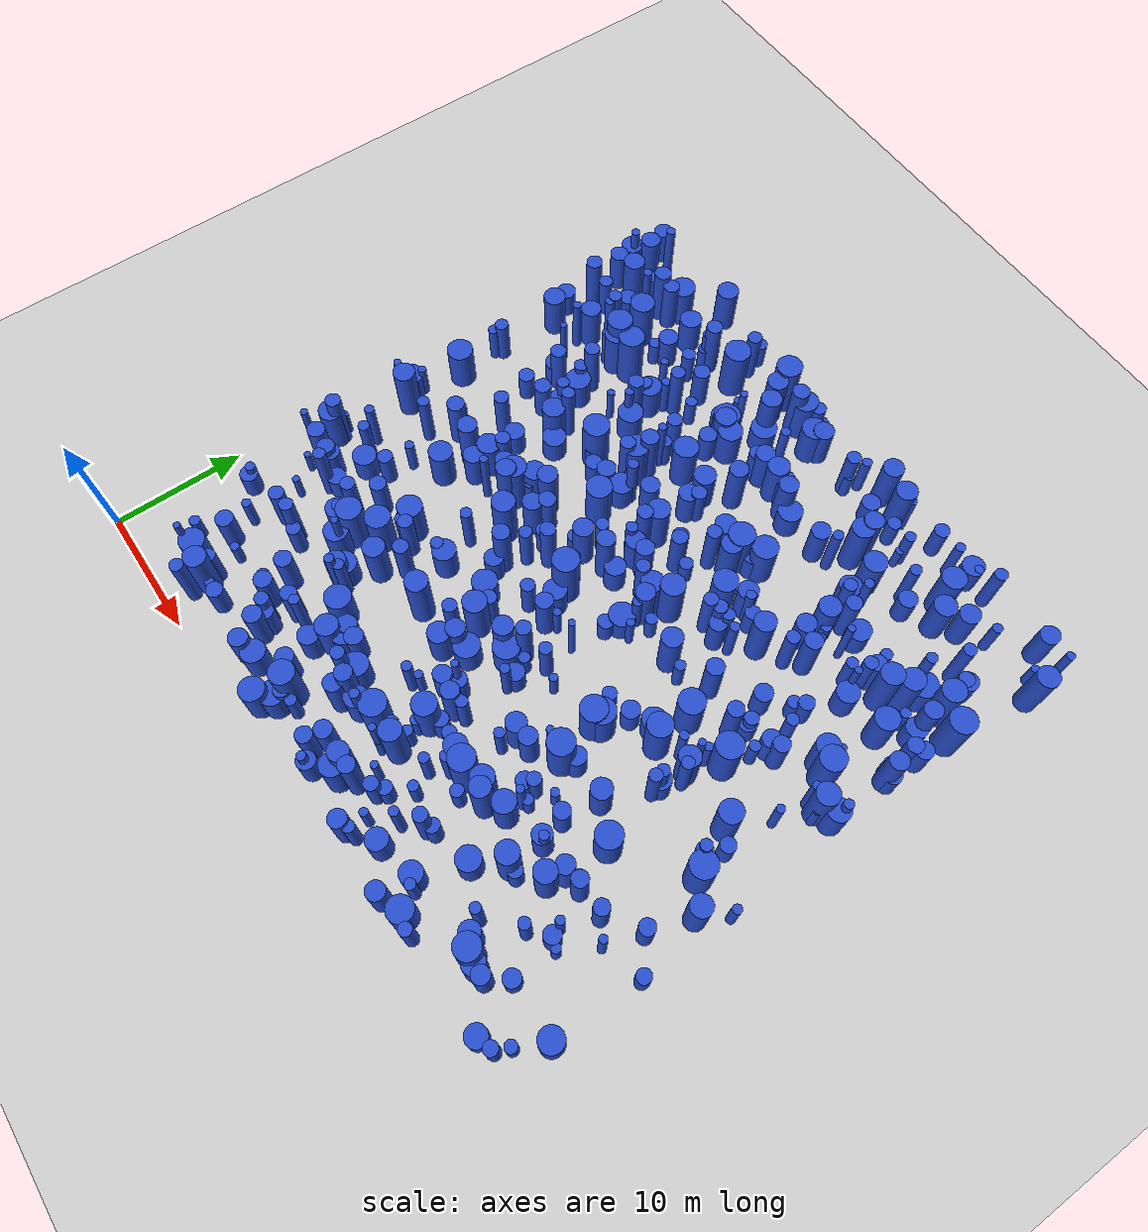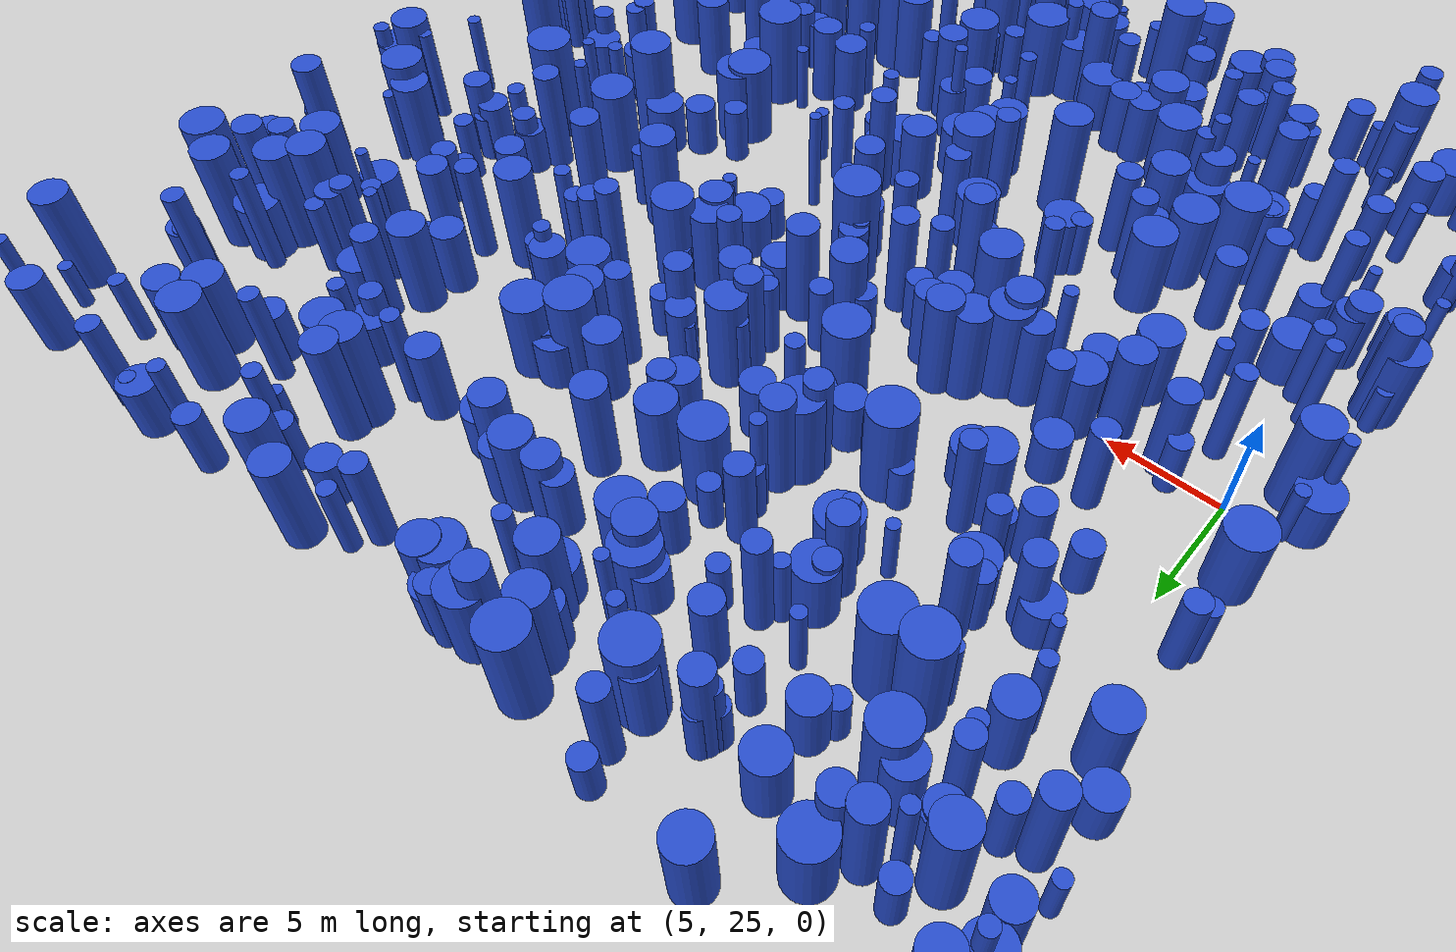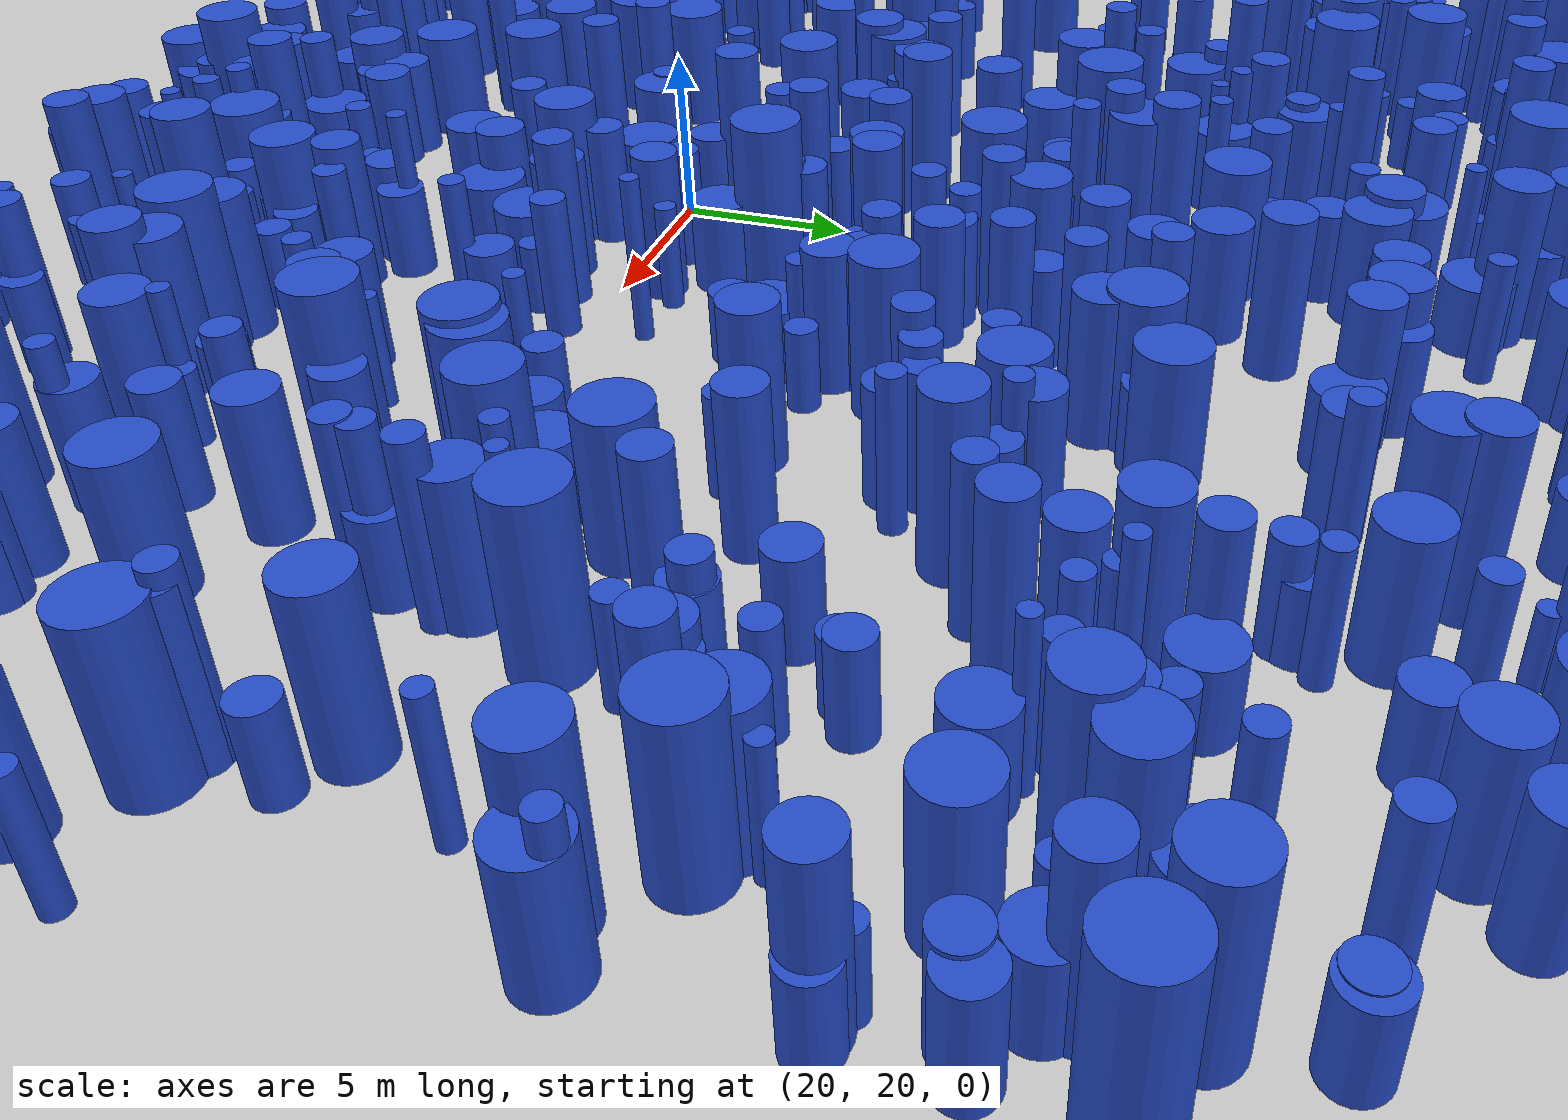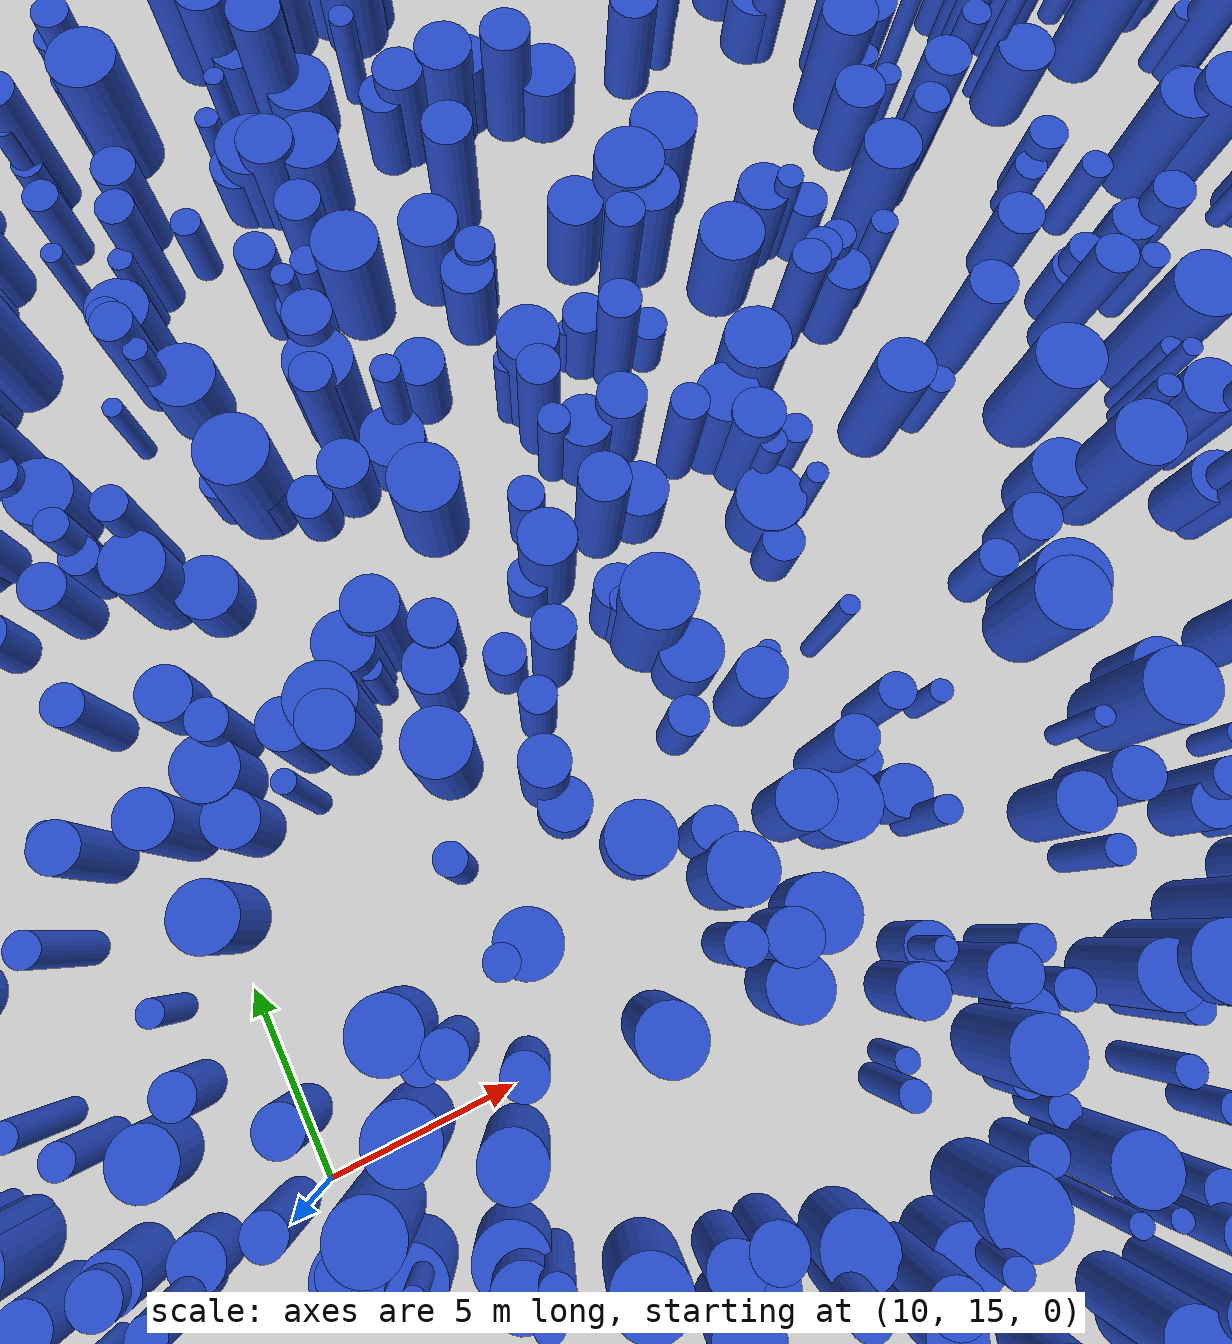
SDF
<sdf version="1.6">
 <world name="default">
  <light name="sun" type="directional">
   <pose>0 0 10 0 -0 0</pose>
   <diffuse>0.8 0.8 0.8 1</diffuse>
   <specular>0.1 0.1 0.1 1</specular>
   <attenuation>
    <range>1000</range>
    <constant>0.9</constant>
    <linear>0.01</linear>
    <quadratic>0.001</quadratic>
   </attenuation>
   <direction>-0.5 0.5 -1</direction>
  </light>
  <model name="ground_plane">
   <static>1</static>
   <link name="link">
    <collision name="collision">
     <geometry><plane><normal>0 0 1</normal><size>100 100</size></plane></geometry>
     <surface><friction><ode><mu>100</mu><mu2>50</mu2></ode></friction></surface>
    </collision>
    <visual name="visual">
     <cast_shadows>0</cast_shadows>
     <geometry><plane><normal>0 0 1</normal><size>100 100</size></plane></geometry>
     <material>
      <script><uri>file://media/materials/scripts/gazebo.material</uri><name>Gazebo/Grey</name></script>
     </material>
    </visual>
   </link>
  </model>
  <gravity>0 0 -9.8</gravity>
  <magnetic_field>6e-06 2.3e-05 -4.2e-05</magnetic_field>
  <atmosphere type="adiabatic"/>
  <physics name="default_physics" default="0" type="ode">
   <max_step_size>0.001</max_step_size>
   <real_time_factor>1</real_time_factor>
   <real_time_update_rate>1000</real_time_update_rate>
  </physics>
  <scene><ambient>0.4 0.4 0.4 1</ambient><background>0.7 0.7 0.7 1</background><shadows>1</shadows></scene>
  <spherical_coordinates>
   <surface_model>EARTH_WGS84</surface_model>
   <latitude_deg>0</latitude_deg>
   <longitude_deg>0</longitude_deg>
   <elevation>0</elevation>
   <heading_deg>0</heading_deg>
  </spherical_coordinates>
  <model name="0">
   <static>0</static>
   <link name="link">
    <inertial>
     <mass>2</mass>
     <inertia><ixx>3.82085</ixx><ixy>0</ixy><ixz>0</ixz><iyy>3.82085</iyy><iyz>0</iyz><izz>0.122841</izz></inertia>
    </inertial>
    <collision name="collision">
     <geometry><cylinder><length>4.74937</length><radius>0.350486</radius></cylinder></geometry>
     <surface><contact><collide_without_contact>1</collide_without_contact></contact></surface>
    </collision>
    <visual name="visual">
     <geometry><cylinder><length>4.74937</length><radius>0.350486</radius></cylinder></geometry>
     <material>
      <script><uri>file://media/materials/scripts/gazebo.material</uri><name>Gazebo/Blue</name></script>
     </material>
    </visual>
    <gravity>0</gravity>
   </link>
   <pose>13.9637 10.7957 2.37469 0 -0 0</pose>
  </model>
  <model name="1">
   <static>0</static>
   <link name="link">
    <inertial>
     <mass>2</mass>
     <inertia><ixx>1.29937</ixx><ixy>0</ixy><ixz>0</ixz><iyy>1.29937</iyy><iyz>0</iyz><izz>0.270526</izz></inertia>
    </inertial>
    <collision name="collision">
     <geometry><cylinder><length>2.64284</length><radius>0.520121</radius></cylinder></geometry>
     <surface><contact><collide_without_contact>1</collide_without_contact></contact></surface>
    </collision>
    <visual name="visual">
     <geometry><cylinder><length>2.64284</length><radius>0.520121</radius></cylinder></geometry>
     <material>
      <script><uri>file://media/materials/scripts/gazebo.material</uri><name>Gazebo/Blue</name></script>
     </material>
    </visual>
    <gravity>0</gravity>
   </link>
   <pose>32.0876 21.3109 1.32142 0 -0 0</pose>
  </model>
  <model name="2">
   <static>0</static>
   <link name="link">
    <inertial>
     <mass>2</mass>
     <inertia><ixx>1.22837</ixx><ixy>0</ixy><ixz>0</ixz><iyy>1.22837</iyy><iyz>0</iyz><izz>0.232608</izz></inertia>
    </inertial>
    <collision name="collision">
     <geometry><cylinder><length>2.5831</length><radius>0.482294</radius></cylinder></geometry>
     <surface><contact><collide_without_contact>1</collide_without_contact></contact></surface>
    </collision>
    <visual name="visual">
     <geometry><cylinder><length>2.5831</length><radius>0.482294</radius></cylinder></geometry>
     <material>
      <script><uri>file://media/materials/scripts/gazebo.material</uri><name>Gazebo/Blue</name></script>
     </material>
    </visual>
    <gravity>0</gravity>
   </link>
   <pose>7.27465 25.3161 1.29155 0 -0 0</pose>
  </model>
  <model name="3">
   <static>0</static>
   <link name="link">
    <inertial>
     <mass>2</mass>
     <inertia><ixx>2.57983</ixx><ixy>0</ixy><ixz>0</ixz><iyy>2.57983</iyy><iyz>0</iyz><izz>0.566458</izz></inertia>
    </inertial>
    <collision name="collision">
     <geometry><cylinder><length>3.71209</length><radius>0.752634</radius></cylinder></geometry>
     <surface><contact><collide_without_contact>1</collide_without_contact></contact></surface>
    </collision>
    <visual name="visual">
     <geometry><cylinder><length>3.71209</length><radius>0.752634</radius></cylinder></geometry>
     <material>
      <script><uri>file://media/materials/scripts/gazebo.material</uri><name>Gazebo/Blue</name></script>
     </material>
    </visual>
    <gravity>0</gravity>
   </link>
   <pose>15.6778 44.6487 1.85604 0 -0 0</pose>
  </model>
  <model name="4">
   <static>0</static>
   <link name="link">
    <inertial>
     <mass>2</mass>
     <inertia>
      <ixx>2.76351</ixx>
      <ixy>0</ixy>
      <ixz>0</ixz>
      <iyy>2.76351</iyy>
      <iyz>0</iyz>
      <izz>0.0663908</izz>
     </inertia>
    </inertial>
    <collision name="collision">
     <geometry><cylinder><length>4.04745</length><radius>0.257664</radius></cylinder></geometry>
     <surface><contact><collide_without_contact>1</collide_without_contact></contact></surface>
    </collision>
    <visual name="visual">
     <geometry><cylinder><length>4.04745</length><radius>0.257664</radius></cylinder></geometry>
     <material>
      <script><uri>file://media/materials/scripts/gazebo.material</uri><name>Gazebo/Blue</name></script>
     </material>
    </visual>
    <gravity>0</gravity>
   </link>
   <pose>6.37285 35.2988 2.02373 0 -0 0</pose>
  </model>
  <model name="5">
   <static>0</static>
   <link name="link">
    <inertial>
     <mass>2</mass>
     <inertia><ixx>1.28365</ixx><ixy>0</ixy><ixz>0</ixz><iyy>1.28365</iyy><iyz>0</iyz><izz>0.136114</izz></inertia>
    </inertial>
    <collision name="collision">
     <geometry><cylinder><length>2.70066</length><radius>0.368937</radius></cylinder></geometry>
     <surface><contact><collide_without_contact>1</collide_without_contact></contact></surface>
    </collision>
    <visual name="visual">
     <geometry><cylinder><length>2.70066</length><radius>0.368937</radius></cylinder></geometry>
     <material>
      <script><uri>file://media/materials/scripts/gazebo.material</uri><name>Gazebo/Blue</name></script>
     </material>
    </visual>
    <gravity>0</gravity>
   </link>
   <pose>44.2189 36.454 1.35033 0 -0 0</pose>
  </model>
  <model name="6">
   <static>0</static>
   <link name="link">
    <inertial>
     <mass>2</mass>
     <inertia><ixx>1.67554</ixx><ixy>0</ixy><ixz>0</ixz><iyy>1.67554</iyy><iyz>0</iyz><izz>0.257363</izz></inertia>
    </inertial>
    <collision name="collision">
     <geometry><cylinder><length>3.04649</length><radius>0.50731</radius></cylinder></geometry>
     <surface><contact><collide_without_contact>1</collide_without_contact></contact></surface>
    </collision>
    <visual name="visual">
     <geometry><cylinder><length>3.04649</length><radius>0.50731</radius></cylinder></geometry>
     <material>
      <script><uri>file://media/materials/scripts/gazebo.material</uri><name>Gazebo/Blue</name></script>
     </material>
    </visual>
    <gravity>0</gravity>
   </link>
   <pose>34.1541 13.9376 1.52325 0 -0 0</pose>
  </model>
  <model name="7">
   <static>0</static>
   <link name="link">
    <inertial>
     <mass>2</mass>
     <inertia><ixx>1.62705</ixx><ixy>0</ixy><ixz>0</ixz><iyy>1.62705</iyy><iyz>0</iyz><izz>0.555531</izz></inertia>
    </inertial>
    <collision name="collision">
     <geometry><cylinder><length>2.84529</length><radius>0.745339</radius></cylinder></geometry>
     <surface><contact><collide_without_contact>1</collide_without_contact></contact></surface>
    </collision>
    <visual name="visual">
     <geometry><cylinder><length>2.84529</length><radius>0.745339</radius></cylinder></geometry>
     <material>
      <script><uri>file://media/materials/scripts/gazebo.material</uri><name>Gazebo/Blue</name></script>
     </material>
    </visual>
    <gravity>0</gravity>
   </link>
   <pose>11.1182 41.7888 1.42265 0 -0 0</pose>
  </model>
  <model name="8">
   <static>0</static>
   <link name="link">
    <inertial>
     <mass>2</mass>
     <inertia><ixx>3.2449</ixx><ixy>0</ixy><ixz>0</ixz><iyy>3.2449</iyy><iyz>0</iyz><izz>0.0853454</izz></inertia>
    </inertial>
    <collision name="collision">
     <geometry><cylinder><length>4.3833</length><radius>0.292139</radius></cylinder></geometry>
     <surface><contact><collide_without_contact>1</collide_without_contact></contact></surface>
    </collision>
    <visual name="visual">
     <geometry><cylinder><length>4.3833</length><radius>0.292139</radius></cylinder></geometry>
     <material>
      <script><uri>file://media/materials/scripts/gazebo.material</uri><name>Gazebo/Blue</name></script>
     </material>
    </visual>
    <gravity>0</gravity>
   </link>
   <pose>2.40092 23.0819 2.19165 0 -0 0</pose>
  </model>
  <model name="9">
   <static>0</static>
   <link name="link">
    <inertial>
     <mass>2</mass>
     <inertia><ixx>2.17214</ixx><ixy>0</ixy><ixz>0</ixz><iyy>2.17214</iyy><iyz>0</iyz><izz>0.825516</izz></inertia>
    </inertial>
    <collision name="collision">
     <geometry><cylinder><length>3.24904</length><radius>0.908579</radius></cylinder></geometry>
     <surface><contact><collide_without_contact>1</collide_without_contact></contact></surface>
    </collision>
    <visual name="visual">
     <geometry><cylinder><length>3.24904</length><radius>0.908579</radius></cylinder></geometry>
     <material>
      <script><uri>file://media/materials/scripts/gazebo.material</uri><name>Gazebo/Blue</name></script>
     </material>
    </visual>
    <gravity>0</gravity>
   </link>
   <pose>30.0928 32.4885 1.62452 0 -0 0</pose>
  </model>
  <model name="10">
   <static>0</static>
   <link name="link">
    <inertial>
     <mass>2</mass>
     <inertia><ixx>1.16641</ixx><ixy>0</ixy><ixz>0</ixz><iyy>1.16641</iyy><iyz>0</iyz><izz>0.142317</izz></inertia>
    </inertial>
    <collision name="collision">
     <geometry><cylinder><length>2.56349</length><radius>0.37725</radius></cylinder></geometry>
     <surface><contact><collide_without_contact>1</collide_without_contact></contact></surface>
    </collision>
    <visual name="visual">
     <geometry><cylinder><length>2.56349</length><radius>0.37725</radius></cylinder></geometry>
     <material>
      <script><uri>file://media/materials/scripts/gazebo.material</uri><name>Gazebo/Blue</name></script>
     </material>
    </visual>
    <gravity>0</gravity>
   </link>
   <pose>36.8922 35.3674 1.28175 0 -0 0</pose>
  </model>
  <model name="11">
   <static>0</static>
   <link name="link">
    <inertial>
     <mass>2</mass>
     <inertia><ixx>3.67772</ixx><ixy>0</ixy><ixz>0</ixz><iyy>3.67772</iyy><iyz>0</iyz><izz>0.546704</izz></inertia>
    </inertial>
    <collision name="collision">
     <geometry><cylinder><length>4.51954</length><radius>0.739394</radius></cylinder></geometry>
     <surface><contact><collide_without_contact>1</collide_without_contact></contact></surface>
    </collision>
    <visual name="visual">
     <geometry><cylinder><length>4.51954</length><radius>0.739394</radius></cylinder></geometry>
     <material>
      <script><uri>file://media/materials/scripts/gazebo.material</uri><name>Gazebo/Blue</name></script>
     </material>
    </visual>
    <gravity>0</gravity>
   </link>
   <pose>26.0271 4.56998 2.25977 0 -0 0</pose>
  </model>
  <model name="12">
   <static>0</static>
   <link name="link">
    <inertial>
     <mass>2</mass>
     <inertia><ixx>2.99946</ixx><ixy>0</ixy><ixz>0</ixz><iyy>2.99946</iyy><iyz>0</iyz><izz>0.69692</izz></inertia>
    </inertial>
    <collision name="collision">
     <geometry><cylinder><length>3.98823</length><radius>0.834817</radius></cylinder></geometry>
     <surface><contact><collide_without_contact>1</collide_without_contact></contact></surface>
    </collision>
    <visual name="visual">
     <geometry><cylinder><length>3.98823</length><radius>0.834817</radius></cylinder></geometry>
     <material>
      <script><uri>file://media/materials/scripts/gazebo.material</uri><name>Gazebo/Blue</name></script>
     </material>
    </visual>
    <gravity>0</gravity>
   </link>
   <pose>43.2297 30.4 1.99412 0 -0 0</pose>
  </model>
  <model name="13">
   <static>0</static>
   <link name="link">
    <inertial>
     <mass>2</mass>
     <inertia><ixx>4.00177</ixx><ixy>0</ixy><ixz>0</ixz><iyy>4.00177</iyy><iyz>0</iyz><izz>0.275408</izz></inertia>
    </inertial>
    <collision name="collision">
     <geometry><cylinder><length>4.81501</length><radius>0.524793</radius></cylinder></geometry>
     <surface><contact><collide_without_contact>1</collide_without_contact></contact></surface>
    </collision>
    <visual name="visual">
     <geometry><cylinder><length>4.81501</length><radius>0.524793</radius></cylinder></geometry>
     <material>
      <script><uri>file://media/materials/scripts/gazebo.material</uri><name>Gazebo/Blue</name></script>
     </material>
    </visual>
    <gravity>0</gravity>
   </link>
   <pose>15.2098 39.4486 2.40751 0 -0 0</pose>
  </model>
  <model name="14">
   <static>0</static>
   <link name="link">
    <inertial>
     <mass>2</mass>
     <inertia>
      <ixx>2.88721</ixx>
      <ixy>0</ixy>
      <ixz>0</ixz>
      <iyy>2.88721</iyy>
      <iyz>0</iyz>
      <izz>0.0931527</izz>
     </inertia>
    </inertial>
    <collision name="collision">
     <geometry><cylinder><length>4.12841</length><radius>0.305209</radius></cylinder></geometry>
     <surface><contact><collide_without_contact>1</collide_without_contact></contact></surface>
    </collision>
    <visual name="visual">
     <geometry><cylinder><length>4.12841</length><radius>0.305209</radius></cylinder></geometry>
     <material>
      <script><uri>file://media/materials/scripts/gazebo.material</uri><name>Gazebo/Blue</name></script>
     </material>
    </visual>
    <gravity>0</gravity>
   </link>
   <pose>47.5968 47.3639 2.06421 0 -0 0</pose>
  </model>
  <model name="15">
   <static>0</static>
   <link name="link">
    <inertial>
     <mass>2</mass>
     <inertia><ixx>3.33766</ixx><ixy>0</ixy><ixz>0</ixz><iyy>3.33766</iyy><iyz>0</iyz><izz>0.789182</izz></inertia>
    </inertial>
    <collision name="collision">
     <geometry><cylinder><length>4.20219</length><radius>0.888359</radius></cylinder></geometry>
     <surface><contact><collide_without_contact>1</collide_without_contact></contact></surface>
    </collision>
    <visual name="visual">
     <geometry><cylinder><length>4.20219</length><radius>0.888359</radius></cylinder></geometry>
     <material>
      <script><uri>file://media/materials/scripts/gazebo.material</uri><name>Gazebo/Blue</name></script>
     </material>
    </visual>
    <gravity>0</gravity>
   </link>
   <pose>26.311 10.715 2.1011 0 -0 0</pose>
  </model>
  <model name="16">
   <static>0</static>
   <link name="link">
    <inertial>
     <mass>2</mass>
     <inertia><ixx>3.98692</ixx><ixy>0</ixy><ixz>0</ixz><iyy>3.98692</iyy><iyz>0</iyz><izz>0.541429</izz></inertia>
    </inertial>
    <collision name="collision">
     <geometry><cylinder><length>4.72199</length><radius>0.735818</radius></cylinder></geometry>
     <surface><contact><collide_without_contact>1</collide_without_contact></contact></surface>
    </collision>
    <visual name="visual">
     <geometry><cylinder><length>4.72199</length><radius>0.735818</radius></cylinder></geometry>
     <material>
      <script><uri>file://media/materials/scripts/gazebo.material</uri><name>Gazebo/Blue</name></script>
     </material>
    </visual>
    <gravity>0</gravity>
   </link>
   <pose>16.8892 26.7119 2.361 0 -0 0</pose>
  </model>
  <model name="17">
   <static>0</static>
   <link name="link">
    <inertial>
     <mass>2</mass>
     <inertia><ixx>2.21319</ixx><ixy>0</ixy><ixz>0</ixz><iyy>2.21319</iyy><iyz>0</iyz><izz>0.160005</izz></inertia>
    </inertial>
    <collision name="collision">
     <geometry><cylinder><length>3.57759</length><radius>0.400007</radius></cylinder></geometry>
     <surface><contact><collide_without_contact>1</collide_without_contact></contact></surface>
    </collision>
    <visual name="visual">
     <geometry><cylinder><length>3.57759</length><radius>0.400007</radius></cylinder></geometry>
     <material>
      <script><uri>file://media/materials/scripts/gazebo.material</uri><name>Gazebo/Blue</name></script>
     </material>
    </visual>
    <gravity>0</gravity>
   </link>
   <pose>34.8299 44.982 1.78879 0 -0 0</pose>
  </model>
  <model name="18">
   <static>0</static>
   <link name="link">
    <inertial>
     <mass>2</mass>
     <inertia><ixx>1.88839</ixx><ixy>0</ixy><ixz>0</ixz><iyy>1.88839</iyy><iyz>0</iyz><izz>0.554769</izz></inertia>
    </inertial>
    <collision name="collision">
     <geometry><cylinder><length>3.10903</length><radius>0.744828</radius></cylinder></geometry>
     <surface><contact><collide_without_contact>1</collide_without_contact></contact></surface>
    </collision>
    <visual name="visual">
     <geometry><cylinder><length>3.10903</length><radius>0.744828</radius></cylinder></geometry>
     <material>
      <script><uri>file://media/materials/scripts/gazebo.material</uri><name>Gazebo/Blue</name></script>
     </material>
    </visual>
    <gravity>0</gravity>
   </link>
   <pose>11.6379 23.7222 1.55451 0 -0 0</pose>
  </model>
  <model name="19">
   <static>0</static>
   <link name="link">
    <inertial>
     <mass>2</mass>
     <inertia><ixx>1.64625</ixx><ixy>0</ixy><ixz>0</ixz><iyy>1.64625</iyy><iyz>0</iyz><izz>0.417403</izz></inertia>
    </inertial>
    <collision name="collision">
     <geometry><cylinder><length>2.93689</length><radius>0.646067</radius></cylinder></geometry>
     <surface><contact><collide_without_contact>1</collide_without_contact></contact></surface>
    </collision>
    <visual name="visual">
     <geometry><cylinder><length>2.93689</length><radius>0.646067</radius></cylinder></geometry>
     <material>
      <script><uri>file://media/materials/scripts/gazebo.material</uri><name>Gazebo/Blue</name></script>
     </material>
    </visual>
    <gravity>0</gravity>
   </link>
   <pose>46.8519 35.6651 1.46844 0 -0 0</pose>
  </model>
  <model name="20">
   <static>0</static>
   <link name="link">
    <inertial>
     <mass>2</mass>
     <inertia><ixx>1.55555</ixx><ixy>0</ixy><ixz>0</ixz><iyy>1.55555</iyy><iyz>0</iyz><izz>0.262073</izz></inertia>
    </inertial>
    <collision name="collision">
     <geometry><cylinder><length>2.92354</length><radius>0.51193</radius></cylinder></geometry>
     <surface><contact><collide_without_contact>1</collide_without_contact></contact></surface>
    </collision>
    <visual name="visual">
     <geometry><cylinder><length>2.92354</length><radius>0.51193</radius></cylinder></geometry>
     <material>
      <script><uri>file://media/materials/scripts/gazebo.material</uri><name>Gazebo/Blue</name></script>
     </material>
    </visual>
    <gravity>0</gravity>
   </link>
   <pose>13.3245 42.0815 1.46177 0 -0 0</pose>
  </model>
  <model name="21">
   <static>0</static>
   <link name="link">
    <inertial>
     <mass>2</mass>
     <inertia><ixx>3.15803</ixx><ixy>0</ixy><ixz>0</ixz><iyy>3.15803</iyy><iyz>0</iyz><izz>0.583815</izz></inertia>
    </inertial>
    <collision name="collision">
     <geometry><cylinder><length>4.14689</length><radius>0.764078</radius></cylinder></geometry>
     <surface><contact><collide_without_contact>1</collide_without_contact></contact></surface>
    </collision>
    <visual name="visual">
     <geometry><cylinder><length>4.14689</length><radius>0.764078</radius></cylinder></geometry>
     <material>
      <script><uri>file://media/materials/scripts/gazebo.material</uri><name>Gazebo/Blue</name></script>
     </material>
    </visual>
    <gravity>0</gravity>
   </link>
   <pose>21.5547 26.5343 2.07345 0 -0 0</pose>
  </model>
  <model name="22">
   <static>0</static>
   <link name="link">
    <inertial>
     <mass>2</mass>
     <inertia><ixx>3.25357</ixx><ixy>0</ixy><ixz>0</ixz><iyy>3.25357</iyy><iyz>0</iyz><izz>0.409144</izz></inertia>
    </inertial>
    <collision name="collision">
     <geometry><cylinder><length>4.27715</length><radius>0.639643</radius></cylinder></geometry>
     <surface><contact><collide_without_contact>1</collide_without_contact></contact></surface>
    </collision>
    <visual name="visual">
     <geometry><cylinder><length>4.27715</length><radius>0.639643</radius></cylinder></geometry>
     <material>
      <script><uri>file://media/materials/scripts/gazebo.material</uri><name>Gazebo/Blue</name></script>
     </material>
    </visual>
    <gravity>0</gravity>
   </link>
   <pose>24.6833 21.1514 2.13857 0 -0 0</pose>
  </model>
  <model name="23">
   <static>0</static>
   <link name="link">
    <inertial>
     <mass>2</mass>
     <inertia><ixx>1.86215</ixx><ixy>0</ixy><ixz>0</ixz><iyy>1.86215</iyy><iyz>0</iyz><izz>0.4961</izz></inertia>
    </inertial>
    <collision name="collision">
     <geometry><cylinder><length>3.11201</length><radius>0.704343</radius></cylinder></geometry>
     <surface><contact><collide_without_contact>1</collide_without_contact></contact></surface>
    </collision>
    <visual name="visual">
     <geometry><cylinder><length>3.11201</length><radius>0.704343</radius></cylinder></geometry>
     <material>
      <script><uri>file://media/materials/scripts/gazebo.material</uri><name>Gazebo/Blue</name></script>
     </material>
    </visual>
    <gravity>0</gravity>
   </link>
   <pose>14.7881 2.99423 1.55601 0 -0 0</pose>
  </model>
  <model name="24">
   <static>0</static>
   <link name="link">
    <inertial>
     <mass>2</mass>
     <inertia><ixx>1.49406</ixx><ixy>0</ixy><ixz>0</ixz><iyy>1.49406</iyy><iyz>0</iyz><izz>0.447724</izz></inertia>
    </inertial>
    <collision name="collision">
     <geometry><cylinder><length>2.76065</length><radius>0.669122</radius></cylinder></geometry>
     <surface><contact><collide_without_contact>1</collide_without_contact></contact></surface>
    </collision>
    <visual name="visual">
     <geometry><cylinder><length>2.76065</length><radius>0.669122</radius></cylinder></geometry>
     <material>
      <script><uri>file://media/materials/scripts/gazebo.material</uri><name>Gazebo/Blue</name></script>
     </material>
    </visual>
    <gravity>0</gravity>
   </link>
   <pose>37.853 29.6773 1.38032 0 -0 0</pose>
  </model>
  <model name="25">
   <static>0</static>
   <link name="link">
    <inertial>
     <mass>2</mass>
     <inertia><ixx>3.26068</ixx><ixy>0</ixy><ixz>0</ixz><iyy>3.26068</iyy><iyz>0</iyz><izz>0.425175</izz></inertia>
    </inertial>
    <collision name="collision">
     <geometry><cylinder><length>4.27651</length><radius>0.652054</radius></cylinder></geometry>
     <surface><contact><collide_without_contact>1</collide_without_contact></contact></surface>
    </collision>
    <visual name="visual">
     <geometry><cylinder><length>4.27651</length><radius>0.652054</radius></cylinder></geometry>
     <material>
      <script><uri>file://media/materials/scripts/gazebo.material</uri><name>Gazebo/Blue</name></script>
     </material>
    </visual>
    <gravity>0</gravity>
   </link>
   <pose>7.91158 24.6829 2.13826 0 -0 0</pose>
  </model>
  <model name="26">
   <static>0</static>
   <link name="link">
    <inertial>
     <mass>2</mass>
     <inertia><ixx>1.59022</ixx><ixy>0</ixy><ixz>0</ixz><iyy>1.59022</iyy><iyz>0</iyz><izz>0.948667</izz></inertia>
    </inertial>
    <collision name="collision">
     <geometry><cylinder><length>2.58753</length><radius>0.973996</radius></cylinder></geometry>
     <surface><contact><collide_without_contact>1</collide_without_contact></contact></surface>
    </collision>
    <visual name="visual">
     <geometry><cylinder><length>2.58753</length><radius>0.973996</radius></cylinder></geometry>
     <material>
      <script><uri>file://media/materials/scripts/gazebo.material</uri><name>Gazebo/Blue</name></script>
     </material>
    </visual>
    <gravity>0</gravity>
   </link>
   <pose>25.3744 17.5495 1.29377 0 -0 0</pose>
  </model>
  <model name="27">
   <static>0</static>
   <link name="link">
    <inertial>
     <mass>2</mass>
     <inertia>
      <ixx>2.06442</ixx>
      <ixy>0</ixy>
      <ixz>0</ixz>
      <iyy>2.06442</iyy>
      <iyz>0</iyz>
      <izz>0.0914529</izz>
     </inertia>
    </inertial>
    <collision name="collision">
     <geometry><cylinder><length>3.48025</length><radius>0.302412</radius></cylinder></geometry>
     <surface><contact><collide_without_contact>1</collide_without_contact></contact></surface>
    </collision>
    <visual name="visual">
     <geometry><cylinder><length>3.48025</length><radius>0.302412</radius></cylinder></geometry>
     <material>
      <script><uri>file://media/materials/scripts/gazebo.material</uri><name>Gazebo/Blue</name></script>
     </material>
    </visual>
    <gravity>0</gravity>
   </link>
   <pose>38.8581 24.2263 1.74013 0 -0 0</pose>
  </model>
  <model name="28">
   <static>0</static>
   <link name="link">
    <inertial>
     <mass>2</mass>
     <inertia><ixx>1.90148</ixx><ixy>0</ixy><ixz>0</ixz><iyy>1.90148</iyy><iyz>0</iyz><izz>0.266141</izz></inertia>
    </inertial>
    <collision name="collision">
     <geometry><cylinder><length>3.25737</length><radius>0.515889</radius></cylinder></geometry>
     <surface><contact><collide_without_contact>1</collide_without_contact></contact></surface>
    </collision>
    <visual name="visual">
     <geometry><cylinder><length>3.25737</length><radius>0.515889</radius></cylinder></geometry>
     <material>
      <script><uri>file://media/materials/scripts/gazebo.material</uri><name>Gazebo/Blue</name></script>
     </material>
    </visual>
    <gravity>0</gravity>
   </link>
   <pose>8.19868 4.18258 1.62868 0 -0 0</pose>
  </model>
  <model name="29">
   <static>0</static>
   <link name="link">
    <inertial>
     <mass>2</mass>
     <inertia>
      <ixx>0.983996</ixx>
      <ixy>0</ixy>
      <ixz>0</ixz>
      <iyy>0.983996</iyy>
      <iyz>0</iyz>
      <izz>0.470048</izz>
     </inertia>
    </inertial>
    <collision name="collision">
     <geometry><cylinder><length>2.11987</length><radius>0.685601</radius></cylinder></geometry>
     <surface><contact><collide_without_contact>1</collide_without_contact></contact></surface>
    </collision>
    <visual name="visual">
     <geometry><cylinder><length>2.11987</length><radius>0.685601</radius></cylinder></geometry>
     <material>
      <script><uri>file://media/materials/scripts/gazebo.material</uri><name>Gazebo/Blue</name></script>
     </material>
    </visual>
    <gravity>0</gravity>
   </link>
   <pose>38.7542 27.7533 1.05993 0 -0 0</pose>
  </model>
  <model name="30">
   <static>0</static>
   <link name="link">
    <inertial>
     <mass>2</mass>
     <inertia><ixx>1.36472</ixx><ixy>0</ixy><ixz>0</ixz><iyy>1.36472</iyy><iyz>0</iyz><izz>0.964605</izz></inertia>
    </inertial>
    <collision name="collision">
     <geometry><cylinder><length>2.30098</length><radius>0.982143</radius></cylinder></geometry>
     <surface><contact><collide_without_contact>1</collide_without_contact></contact></surface>
    </collision>
    <visual name="visual">
     <geometry><cylinder><length>2.30098</length><radius>0.982143</radius></cylinder></geometry>
     <material>
      <script><uri>file://media/materials/scripts/gazebo.material</uri><name>Gazebo/Blue</name></script>
     </material>
    </visual>
    <gravity>0</gravity>
   </link>
   <pose>23.6658 15.4375 1.15049 0 -0 0</pose>
  </model>
  <model name="31">
   <static>0</static>
   <link name="link">
    <inertial>
     <mass>2</mass>
     <inertia><ixx>2.45644</ixx><ixy>0</ixy><ixz>0</ixz><iyy>2.45644</iyy><iyz>0</iyz><izz>0.235516</izz></inertia>
    </inertial>
    <collision name="collision">
     <geometry><cylinder><length>3.74595</length><radius>0.4853</radius></cylinder></geometry>
     <surface><contact><collide_without_contact>1</collide_without_contact></contact></surface>
    </collision>
    <visual name="visual">
     <geometry><cylinder><length>3.74595</length><radius>0.4853</radius></cylinder></geometry>
     <material>
      <script><uri>file://media/materials/scripts/gazebo.material</uri><name>Gazebo/Blue</name></script>
     </material>
    </visual>
    <gravity>0</gravity>
   </link>
   <pose>40.4344 36.4539 1.87297 0 -0 0</pose>
  </model>
  <model name="32">
   <static>0</static>
   <link name="link">
    <inertial>
     <mass>2</mass>
     <inertia><ixx>3.68543</ixx><ixy>0</ixy><ixz>0</ixz><iyy>3.68543</iyy><iyz>0</iyz><izz>0.263178</izz></inertia>
    </inertial>
    <collision name="collision">
     <geometry><cylinder><length>4.61769</length><radius>0.513009</radius></cylinder></geometry>
     <surface><contact><collide_without_contact>1</collide_without_contact></contact></surface>
    </collision>
    <visual name="visual">
     <geometry><cylinder><length>4.61769</length><radius>0.513009</radius></cylinder></geometry>
     <material>
      <script><uri>file://media/materials/scripts/gazebo.material</uri><name>Gazebo/Blue</name></script>
     </material>
    </visual>
    <gravity>0</gravity>
   </link>
   <pose>31.0444 30.2874 2.30884 0 -0 0</pose>
  </model>
  <model name="33">
   <static>0</static>
   <link name="link">
    <inertial>
     <mass>2</mass>
     <inertia><ixx>3.67446</ixx><ixy>0</ixy><ixz>0</ixz><iyy>3.67446</iyy><iyz>0</iyz><izz>0.109586</izz></inertia>
    </inertial>
    <collision name="collision">
     <geometry><cylinder><length>4.66025</length><radius>0.331037</radius></cylinder></geometry>
     <surface><contact><collide_without_contact>1</collide_without_contact></contact></surface>
    </collision>
    <visual name="visual">
     <geometry><cylinder><length>4.66025</length><radius>0.331037</radius></cylinder></geometry>
     <material>
      <script><uri>file://media/materials/scripts/gazebo.material</uri><name>Gazebo/Blue</name></script>
     </material>
    </visual>
    <gravity>0</gravity>
   </link>
   <pose>5.79937 36.9559 2.33013 0 -0 0</pose>
  </model>
  <model name="34">
   <static>0</static>
   <link name="link">
    <inertial>
     <mass>2</mass>
     <inertia><ixx>0.87381</ixx><ixy>0</ixy><ixz>0</ixz><iyy>0.87381</iyy><iyz>0</iyz><izz>0.104626</izz></inertia>
    </inertial>
    <collision name="collision">
     <geometry><cylinder><length>2.22013</length><radius>0.323459</radius></cylinder></geometry>
     <surface><contact><collide_without_contact>1</collide_without_contact></contact></surface>
    </collision>
    <visual name="visual">
     <geometry><cylinder><length>2.22013</length><radius>0.323459</radius></cylinder></geometry>
     <material>
      <script><uri>file://media/materials/scripts/gazebo.material</uri><name>Gazebo/Blue</name></script>
     </material>
    </visual>
    <gravity>0</gravity>
   </link>
   <pose>28.0725 29.1738 1.11007 0 -0 0</pose>
  </model>
  <model name="35">
   <static>0</static>
   <link name="link">
    <inertial>
     <mass>2</mass>
     <inertia>
      <ixx>1.09122</ixx>
      <ixy>0</ixy>
      <ixz>0</ixz>
      <iyy>1.09122</iyy>
      <iyz>0</iyz>
      <izz>0.0932913</izz>
     </inertia>
    </inertial>
    <collision name="collision">
     <geometry><cylinder><length>2.50348</length><radius>0.305436</radius></cylinder></geometry>
     <surface><contact><collide_without_contact>1</collide_without_contact></contact></surface>
    </collision>
    <visual name="visual">
     <geometry><cylinder><length>2.50348</length><radius>0.305436</radius></cylinder></geometry>
     <material>
      <script><uri>file://media/materials/scripts/gazebo.material</uri><name>Gazebo/Blue</name></script>
     </material>
    </visual>
    <gravity>0</gravity>
   </link>
   <pose>28.9997 18.9307 1.25174 0 -0 0</pose>
  </model>
  <model name="36">
   <static>0</static>
   <link name="link">
    <inertial>
     <mass>2</mass>
     <inertia><ixx>1.95658</ixx><ixy>0</ixy><ixz>0</ixz><iyy>1.95658</iyy><iyz>0</iyz><izz>0.315427</izz></inertia>
    </inertial>
    <collision name="collision">
     <geometry><cylinder><length>3.2853</length><radius>0.561629</radius></cylinder></geometry>
     <surface><contact><collide_without_contact>1</collide_without_contact></contact></surface>
    </collision>
    <visual name="visual">
     <geometry><cylinder><length>3.2853</length><radius>0.561629</radius></cylinder></geometry>
     <material>
      <script><uri>file://media/materials/scripts/gazebo.material</uri><name>Gazebo/Blue</name></script>
     </material>
    </visual>
    <gravity>0</gravity>
   </link>
   <pose>23.5459 35.1984 1.64265 0 -0 0</pose>
  </model>
  <model name="37">
   <static>0</static>
   <link name="link">
    <inertial>
     <mass>2</mass>
     <inertia><ixx>4.25456</ixx><ixy>0</ixy><ixz>0</ixz><iyy>4.25456</iyy><iyz>0</iyz><izz>0.212678</izz></inertia>
    </inertial>
    <collision name="collision">
     <geometry><cylinder><length>4.98892</length><radius>0.46117</radius></cylinder></geometry>
     <surface><contact><collide_without_contact>1</collide_without_contact></contact></surface>
    </collision>
    <visual name="visual">
     <geometry><cylinder><length>4.98892</length><radius>0.46117</radius></cylinder></geometry>
     <material>
      <script><uri>file://media/materials/scripts/gazebo.material</uri><name>Gazebo/Blue</name></script>
     </material>
    </visual>
    <gravity>0</gravity>
   </link>
   <pose>6.44506 14.3001 2.49446 0 -0 0</pose>
  </model>
  <model name="38">
   <static>0</static>
   <link name="link">
    <inertial>
     <mass>2</mass>
     <inertia><ixx>1.50603</ixx><ixy>0</ixy><ixz>0</ixz><iyy>1.50603</iyy><iyz>0</iyz><izz>0.44841</izz></inertia>
    </inertial>
    <collision name="collision">
     <geometry><cylinder><length>2.77325</length><radius>0.669635</radius></cylinder></geometry>
     <surface><contact><collide_without_contact>1</collide_without_contact></contact></surface>
    </collision>
    <visual name="visual">
     <geometry><cylinder><length>2.77325</length><radius>0.669635</radius></cylinder></geometry>
     <material>
      <script><uri>file://media/materials/scripts/gazebo.material</uri><name>Gazebo/Blue</name></script>
     </material>
    </visual>
    <gravity>0</gravity>
   </link>
   <pose>40.6277 28.1109 1.38663 0 -0 0</pose>
  </model>
  <model name="39">
   <static>0</static>
   <link name="link">
    <inertial>
     <mass>2</mass>
     <inertia><ixx>3.67581</ixx><ixy>0</ixy><ixz>0</ixz><iyy>3.67581</iyy><iyz>0</iyz><izz>0.237626</izz></inertia>
    </inertial>
    <collision name="collision">
     <geometry><cylinder><length>4.61974</length><radius>0.487469</radius></cylinder></geometry>
     <surface><contact><collide_without_contact>1</collide_without_contact></contact></surface>
    </collision>
    <visual name="visual">
     <geometry><cylinder><length>4.61974</length><radius>0.487469</radius></cylinder></geometry>
     <material>
      <script><uri>file://media/materials/scripts/gazebo.material</uri><name>Gazebo/Blue</name></script>
     </material>
    </visual>
    <gravity>0</gravity>
   </link>
   <pose>36.3072 33.0621 2.30987 0 -0 0</pose>
  </model>
  <model name="40">
   <static>0</static>
   <link name="link">
    <inertial>
     <mass>2</mass>
     <inertia><ixx>2.77857</ixx><ixy>0</ixy><ixz>0</ixz><iyy>2.77857</iyy><iyz>0</iyz><izz>0.218702</izz></inertia>
    </inertial>
    <collision name="collision">
     <geometry><cylinder><length>4.00191</length><radius>0.467656</radius></cylinder></geometry>
     <surface><contact><collide_without_contact>1</collide_without_contact></contact></surface>
    </collision>
    <visual name="visual">
     <geometry><cylinder><length>4.00191</length><radius>0.467656</radius></cylinder></geometry>
     <material>
      <script><uri>file://media/materials/scripts/gazebo.material</uri><name>Gazebo/Blue</name></script>
     </material>
    </visual>
    <gravity>0</gravity>
   </link>
   <pose>27.4866 19.3515 2.00096 0 -0 0</pose>
  </model>
  <model name="41">
   <static>0</static>
   <link name="link">
    <inertial>
     <mass>2</mass>
     <inertia><ixx>1.76334</ixx><ixy>0</ixy><ixz>0</ixz><iyy>1.76334</iyy><iyz>0</iyz><izz>0.124496</izz></inertia>
    </inertial>
    <collision name="collision">
     <geometry><cylinder><length>3.19477</length><radius>0.352839</radius></cylinder></geometry>
     <surface><contact><collide_without_contact>1</collide_without_contact></contact></surface>
    </collision>
    <visual name="visual">
     <geometry><cylinder><length>3.19477</length><radius>0.352839</radius></cylinder></geometry>
     <material>
      <script><uri>file://media/materials/scripts/gazebo.material</uri><name>Gazebo/Blue</name></script>
     </material>
    </visual>
    <gravity>0</gravity>
   </link>
   <pose>23.6952 31.2859 1.59739 0 -0 0</pose>
  </model>
  <model name="42">
   <static>0</static>
   <link name="link">
    <inertial>
     <mass>2</mass>
     <inertia><ixx>1.3081</ixx><ixy>0</ixy><ixz>0</ixz><iyy>1.3081</iyy><iyz>0</iyz><izz>0.176853</izz></inertia>
    </inertial>
    <collision name="collision">
     <geometry><cylinder><length>2.70519</length><radius>0.420539</radius></cylinder></geometry>
     <surface><contact><collide_without_contact>1</collide_without_contact></contact></surface>
    </collision>
    <visual name="visual">
     <geometry><cylinder><length>2.70519</length><radius>0.420539</radius></cylinder></geometry>
     <material>
      <script><uri>file://media/materials/scripts/gazebo.material</uri><name>Gazebo/Blue</name></script>
     </material>
    </visual>
    <gravity>0</gravity>
   </link>
   <pose>20.533 3.76774 1.3526 0 -0 0</pose>
  </model>
  <model name="43">
   <static>0</static>
   <link name="link">
    <inertial>
     <mass>2</mass>
     <inertia><ixx>1.55938</ixx><ixy>0</ixy><ixz>0</ixz><iyy>1.55938</iyy><iyz>0</iyz><izz>0.307875</izz></inertia>
    </inertial>
    <collision name="collision">
     <geometry><cylinder><length>2.9039</length><radius>0.554865</radius></cylinder></geometry>
     <surface><contact><collide_without_contact>1</collide_without_contact></contact></surface>
    </collision>
    <visual name="visual">
     <geometry><cylinder><length>2.9039</length><radius>0.554865</radius></cylinder></geometry>
     <material>
      <script><uri>file://media/materials/scripts/gazebo.material</uri><name>Gazebo/Blue</name></script>
     </material>
    </visual>
    <gravity>0</gravity>
   </link>
   <pose>35.5678 47.5327 1.45195 0 -0 0</pose>
  </model>
  <model name="44">
   <static>0</static>
   <link name="link">
    <inertial>
     <mass>2</mass>
     <inertia><ixx>3.63122</ixx><ixy>0</ixy><ixz>0</ixz><iyy>3.63122</iyy><iyz>0</iyz><izz>0.614122</izz></inertia>
    </inertial>
    <collision name="collision">
     <geometry><cylinder><length>4.46598</length><radius>0.783659</radius></cylinder></geometry>
     <surface><contact><collide_without_contact>1</collide_without_contact></contact></surface>
    </collision>
    <visual name="visual">
     <geometry><cylinder><length>4.46598</length><radius>0.783659</radius></cylinder></geometry>
     <material>
      <script><uri>file://media/materials/scripts/gazebo.material</uri><name>Gazebo/Blue</name></script>
     </material>
    </visual>
    <gravity>0</gravity>
   </link>
   <pose>39.6417 11.1136 2.23299 0 -0 0</pose>
  </model>
  <model name="45">
   <static>0</static>
   <link name="link">
    <inertial>
     <mass>2</mass>
     <inertia><ixx>4.31175</ixx><ixy>0</ixy><ixz>0</ixz><iyy>4.31175</iyy><iyz>0</iyz><izz>0.358965</izz></inertia>
    </inertial>
    <collision name="collision">
     <geometry><cylinder><length>4.97932</length><radius>0.599137</radius></cylinder></geometry>
     <surface><contact><collide_without_contact>1</collide_without_contact></contact></surface>
    </collision>
    <visual name="visual">
     <geometry><cylinder><length>4.97932</length><radius>0.599137</radius></cylinder></geometry>
     <material>
      <script><uri>file://media/materials/scripts/gazebo.material</uri><name>Gazebo/Blue</name></script>
     </material>
    </visual>
    <gravity>0</gravity>
   </link>
   <pose>13.5394 44.0868 2.48966 0 -0 0</pose>
  </model>
  <model name="46">
   <static>0</static>
   <link name="link">
    <inertial>
     <mass>2</mass>
     <inertia>
      <ixx>0.904884</ixx>
      <ixy>0</ixy>
      <ixz>0</ixz>
      <iyy>0.904884</iyy>
      <iyz>0</iyz>
      <izz>0.374443</izz>
     </inertia>
    </inertial>
    <collision name="collision">
     <geometry><cylinder><length>2.07508</length><radius>0.611918</radius></cylinder></geometry>
     <surface><contact><collide_without_contact>1</collide_without_contact></contact></surface>
    </collision>
    <visual name="visual">
     <geometry><cylinder><length>2.07508</length><radius>0.611918</radius></cylinder></geometry>
     <material>
      <script><uri>file://media/materials/scripts/gazebo.material</uri><name>Gazebo/Blue</name></script>
     </material>
    </visual>
    <gravity>0</gravity>
   </link>
   <pose>43.3206 6.1671 1.03754 0 -0 0</pose>
  </model>
  <model name="47">
   <static>0</static>
   <link name="link">
    <inertial>
     <mass>2</mass>
     <inertia><ixx>3.56288</ixx><ixy>0</ixy><ixz>0</ixz><iyy>3.56288</iyy><iyz>0</iyz><izz>0.679619</izz></inertia>
    </inertial>
    <collision name="collision">
     <geometry><cylinder><length>4.39755</length><radius>0.82439</radius></cylinder></geometry>
     <surface><contact><collide_without_contact>1</collide_without_contact></contact></surface>
    </collision>
    <visual name="visual">
     <geometry><cylinder><length>4.39755</length><radius>0.82439</radius></cylinder></geometry>
     <material>
      <script><uri>file://media/materials/scripts/gazebo.material</uri><name>Gazebo/Blue</name></script>
     </material>
    </visual>
    <gravity>0</gravity>
   </link>
   <pose>23.4584 31.6278 2.19877 0 -0 0</pose>
  </model>
  <model name="48">
   <static>0</static>
   <link name="link">
    <inertial>
     <mass>2</mass>
     <inertia>
      <ixx>0.818871</ixx>
      <ixy>0</ixy>
      <ixz>0</ixz>
      <iyy>0.818871</iyy>
      <iyz>0</iyz>
      <izz>0.0707383</izz>
     </inertia>
    </inertial>
    <collision name="collision">
     <geometry><cylinder><length>2.16818</length><radius>0.265967</radius></cylinder></geometry>
     <surface><contact><collide_without_contact>1</collide_without_contact></contact></surface>
    </collision>
    <visual name="visual">
     <geometry><cylinder><length>2.16818</length><radius>0.265967</radius></cylinder></geometry>
     <material>
      <script><uri>file://media/materials/scripts/gazebo.material</uri><name>Gazebo/Blue</name></script>
     </material>
    </visual>
    <gravity>0</gravity>
   </link>
   <pose>22.8986 2.94497 1.08409 0 -0 0</pose>
  </model>
  <model name="49">
   <static>0</static>
   <link name="link">
    <inertial>
     <mass>2</mass>
     <inertia><ixx>1.29707</ixx><ixy>0</ixy><ixz>0</ixz><iyy>1.29707</iyy><iyz>0</iyz><izz>0.551894</izz></inertia>
    </inertial>
    <collision name="collision">
     <geometry><cylinder><length>2.47522</length><radius>0.742895</radius></cylinder></geometry>
     <surface><contact><collide_without_contact>1</collide_without_contact></contact></surface>
    </collision>
    <visual name="visual">
     <geometry><cylinder><length>2.47522</length><radius>0.742895</radius></cylinder></geometry>
     <material>
      <script><uri>file://media/materials/scripts/gazebo.material</uri><name>Gazebo/Blue</name></script>
     </material>
    </visual>
    <gravity>0</gravity>
   </link>
   <pose>20.0997 44.5938 1.23761 0 -0 0</pose>
  </model>
  <model name="50">
   <static>0</static>
   <link name="link">
    <inertial>
     <mass>2</mass>
     <inertia><ixx>4.08319</ixx><ixy>0</ixy><ixz>0</ixz><iyy>4.08319</iyy><iyz>0</iyz><izz>0.947286</izz></inertia>
    </inertial>
    <collision name="collision">
     <geometry><cylinder><length>4.65374</length><radius>0.973286</radius></cylinder></geometry>
     <surface><contact><collide_without_contact>1</collide_without_contact></contact></surface>
    </collision>
    <visual name="visual">
     <geometry><cylinder><length>4.65374</length><radius>0.973286</radius></cylinder></geometry>
     <material>
      <script><uri>file://media/materials/scripts/gazebo.material</uri><name>Gazebo/Blue</name></script>
     </material>
    </visual>
    <gravity>0</gravity>
   </link>
   <pose>10.5505 38.6327 2.32687 0 -0 0</pose>
  </model>
  <model name="51">
   <static>0</static>
   <link name="link">
    <inertial>
     <mass>2</mass>
     <inertia><ixx>1.96723</ixx><ixy>0</ixy><ixz>0</ixz><iyy>1.96723</iyy><iyz>0</iyz><izz>0.705018</izz></inertia>
    </inertial>
    <collision name="collision">
     <geometry><cylinder><length>3.11261</length><radius>0.839654</radius></cylinder></geometry>
     <surface><contact><collide_without_contact>1</collide_without_contact></contact></surface>
    </collision>
    <visual name="visual">
     <geometry><cylinder><length>3.11261</length><radius>0.839654</radius></cylinder></geometry>
     <material>
      <script><uri>file://media/materials/scripts/gazebo.material</uri><name>Gazebo/Blue</name></script>
     </material>
    </visual>
    <gravity>0</gravity>
   </link>
   <pose>10.8716 44.1182 1.5563 0 -0 0</pose>
  </model>
  <model name="52">
   <static>0</static>
   <link name="link">
    <inertial>
     <mass>2</mass>
     <inertia><ixx>2.09002</ixx><ixy>0</ixy><ixz>0</ixz><iyy>2.09002</iyy><iyz>0</iyz><izz>0.112428</izz></inertia>
    </inertial>
    <collision name="collision">
     <geometry><cylinder><length>3.49325</length><radius>0.335302</radius></cylinder></geometry>
     <surface><contact><collide_without_contact>1</collide_without_contact></contact></surface>
    </collision>
    <visual name="visual">
     <geometry><cylinder><length>3.49325</length><radius>0.335302</radius></cylinder></geometry>
     <material>
      <script><uri>file://media/materials/scripts/gazebo.material</uri><name>Gazebo/Blue</name></script>
     </material>
    </visual>
    <gravity>0</gravity>
   </link>
   <pose>24.5794 2.51328 1.74663 0 -0 0</pose>
  </model>
  <model name="53">
   <static>0</static>
   <link name="link">
    <inertial>
     <mass>2</mass>
     <inertia><ixx>2.77457</ixx><ixy>0</ixy><ixz>0</ixz><iyy>2.77457</iyy><iyz>0</iyz><izz>0.892205</izz></inertia>
    </inertial>
    <collision name="collision">
     <geometry><cylinder><length>3.73775</length><radius>0.944566</radius></cylinder></geometry>
     <surface><contact><collide_without_contact>1</collide_without_contact></contact></surface>
    </collision>
    <visual name="visual">
     <geometry><cylinder><length>3.73775</length><radius>0.944566</radius></cylinder></geometry>
     <material>
      <script><uri>file://media/materials/scripts/gazebo.material</uri><name>Gazebo/Blue</name></script>
     </material>
    </visual>
    <gravity>0</gravity>
   </link>
   <pose>29.7969 36.1188 1.86888 0 -0 0</pose>
  </model>
  <model name="54">
   <static>0</static>
   <link name="link">
    <inertial>
     <mass>2</mass>
     <inertia><ixx>2.11658</ixx><ixy>0</ixy><ixz>0</ixz><iyy>2.11658</iyy><iyz>0</iyz><izz>0.764272</izz></inertia>
    </inertial>
    <collision name="collision">
     <geometry><cylinder><length>3.22594</length><radius>0.874226</radius></cylinder></geometry>
     <surface><contact><collide_without_contact>1</collide_without_contact></contact></surface>
    </collision>
    <visual name="visual">
     <geometry><cylinder><length>3.22594</length><radius>0.874226</radius></cylinder></geometry>
     <material>
      <script><uri>file://media/materials/scripts/gazebo.material</uri><name>Gazebo/Blue</name></script>
     </material>
    </visual>
    <gravity>0</gravity>
   </link>
   <pose>11.5601 25.1175 1.61297 0 -0 0</pose>
  </model>
  <model name="55">
   <static>0</static>
   <link name="link">
    <inertial>
     <mass>2</mass>
     <inertia><ixx>2.46445</ixx><ixy>0</ixy><ixz>0</ixz><iyy>2.46445</iyy><iyz>0</iyz><izz>0.129583</izz></inertia>
    </inertial>
    <collision name="collision">
     <geometry><cylinder><length>3.79446</length><radius>0.359977</radius></cylinder></geometry>
     <surface><contact><collide_without_contact>1</collide_without_contact></contact></surface>
    </collision>
    <visual name="visual">
     <geometry><cylinder><length>3.79446</length><radius>0.359977</radius></cylinder></geometry>
     <material>
      <script><uri>file://media/materials/scripts/gazebo.material</uri><name>Gazebo/Blue</name></script>
     </material>
    </visual>
    <gravity>0</gravity>
   </link>
   <pose>32.0939 33.0185 1.89723 0 -0 0</pose>
  </model>
  <model name="56">
   <static>0</static>
   <link name="link">
    <inertial>
     <mass>2</mass>
     <inertia><ixx>1.34214</ixx><ixy>0</ixy><ixz>0</ixz><iyy>1.34214</iyy><iyz>0</iyz><izz>0.594662</izz></inertia>
    </inertial>
    <collision name="collision">
     <geometry><cylinder><length>2.50377</length><radius>0.771143</radius></cylinder></geometry>
     <surface><contact><collide_without_contact>1</collide_without_contact></contact></surface>
    </collision>
    <visual name="visual">
     <geometry><cylinder><length>2.50377</length><radius>0.771143</radius></cylinder></geometry>
     <material>
      <script><uri>file://media/materials/scripts/gazebo.material</uri><name>Gazebo/Blue</name></script>
     </material>
    </visual>
    <gravity>0</gravity>
   </link>
   <pose>17.0113 6.99255 1.25189 0 -0 0</pose>
  </model>
  <model name="57">
   <static>0</static>
   <link name="link">
    <inertial>
     <mass>2</mass>
     <inertia>
      <ixx>1.59473</ixx>
      <ixy>0</ixy>
      <ixz>0</ixz>
      <iyy>1.59473</iyy>
      <iyz>0</iyz>
      <izz>0.0761013</izz>
     </inertia>
    </inertial>
    <collision name="collision">
     <geometry><cylinder><length>3.05615</length><radius>0.275865</radius></cylinder></geometry>
     <surface><contact><collide_without_contact>1</collide_without_contact></contact></surface>
    </collision>
    <visual name="visual">
     <geometry><cylinder><length>3.05615</length><radius>0.275865</radius></cylinder></geometry>
     <material>
      <script><uri>file://media/materials/scripts/gazebo.material</uri><name>Gazebo/Blue</name></script>
     </material>
    </visual>
    <gravity>0</gravity>
   </link>
   <pose>12.885 35.111 1.52808 0 -0 0</pose>
  </model>
  <model name="58">
   <static>0</static>
   <link name="link">
    <inertial>
     <mass>2</mass>
     <inertia><ixx>4.36397</ixx><ixy>0</ixy><ixz>0</ixz><iyy>4.36397</iyy><iyz>0</iyz><izz>0.40593</izz></inertia>
    </inertial>
    <collision name="collision">
     <geometry><cylinder><length>4.9966</length><radius>0.637126</radius></cylinder></geometry>
     <surface><contact><collide_without_contact>1</collide_without_contact></contact></surface>
    </collision>
    <visual name="visual">
     <geometry><cylinder><length>4.9966</length><radius>0.637126</radius></cylinder></geometry>
     <material>
      <script><uri>file://media/materials/scripts/gazebo.material</uri><name>Gazebo/Blue</name></script>
     </material>
    </visual>
    <gravity>0</gravity>
   </link>
   <pose>19.0079 21.4355 2.4983 0 -0 0</pose>
  </model>
  <model name="59">
   <static>0</static>
   <link name="link">
    <inertial>
     <mass>2</mass>
     <inertia><ixx>1.53536</ixx><ixy>0</ixy><ixz>0</ixz><iyy>1.53536</iyy><iyz>0</iyz><izz>0.253607</izz></inertia>
    </inertial>
    <collision name="collision">
     <geometry><cylinder><length>2.90712</length><radius>0.503594</radius></cylinder></geometry>
     <surface><contact><collide_without_contact>1</collide_without_contact></contact></surface>
    </collision>
    <visual name="visual">
     <geometry><cylinder><length>2.90712</length><radius>0.503594</radius></cylinder></geometry>
     <material>
      <script><uri>file://media/materials/scripts/gazebo.material</uri><name>Gazebo/Blue</name></script>
     </material>
    </visual>
    <gravity>0</gravity>
   </link>
   <pose>38.8057 27.8795 1.45356 0 -0 0</pose>
  </model>
  <model name="60">
   <static>0</static>
   <link name="link">
    <inertial>
     <mass>2</mass>
     <inertia><ixx>2.10807</ixx><ixy>0</ixy><ixz>0</ixz><iyy>2.10807</iyy><iyz>0</iyz><izz>0.46283</izz></inertia>
    </inertial>
    <collision name="collision">
     <geometry><cylinder><length>3.35558</length><radius>0.680316</radius></cylinder></geometry>
     <surface><contact><collide_without_contact>1</collide_without_contact></contact></surface>
    </collision>
    <visual name="visual">
     <geometry><cylinder><length>3.35558</length><radius>0.680316</radius></cylinder></geometry>
     <material>
      <script><uri>file://media/materials/scripts/gazebo.material</uri><name>Gazebo/Blue</name></script>
     </material>
    </visual>
    <gravity>0</gravity>
   </link>
   <pose>3.4312 15.3851 1.67779 0 -0 0</pose>
  </model>
  <model name="61">
   <static>0</static>
   <link name="link">
    <inertial>
     <mass>2</mass>
     <inertia><ixx>2.0788</ixx><ixy>0</ixy><ixz>0</ixz><iyy>2.0788</iyy><iyz>0</iyz><izz>0.0753611</izz></inertia>
    </inertial>
    <collision name="collision">
     <geometry><cylinder><length>3.49953</length><radius>0.27452</radius></cylinder></geometry>
     <surface><contact><collide_without_contact>1</collide_without_contact></contact></surface>
    </collision>
    <visual name="visual">
     <geometry><cylinder><length>3.49953</length><radius>0.27452</radius></cylinder></geometry>
     <material>
      <script><uri>file://media/materials/scripts/gazebo.material</uri><name>Gazebo/Blue</name></script>
     </material>
    </visual>
    <gravity>0</gravity>
   </link>
   <pose>43.7905 31.2281 1.74976 0 -0 0</pose>
  </model>
  <model name="62">
   <static>0</static>
   <link name="link">
    <inertial>
     <mass>2</mass>
     <inertia><ixx>3.58145</ixx><ixy>0</ixy><ixz>0</ixz><iyy>3.58145</iyy><iyz>0</iyz><izz>0.124934</izz></inertia>
    </inertial>
    <collision name="collision">
     <geometry><cylinder><length>4.59498</length><radius>0.35346</radius></cylinder></geometry>
     <surface><contact><collide_without_contact>1</collide_without_contact></contact></surface>
    </collision>
    <visual name="visual">
     <geometry><cylinder><length>4.59498</length><radius>0.35346</radius></cylinder></geometry>
     <material>
      <script><uri>file://media/materials/scripts/gazebo.material</uri><name>Gazebo/Blue</name></script>
     </material>
    </visual>
    <gravity>0</gravity>
   </link>
   <pose>23.3049 7.35052 2.29749 0 -0 0</pose>
  </model>
  <model name="63">
   <static>0</static>
   <link name="link">
    <inertial>
     <mass>2</mass>
     <inertia><ixx>1.71261</ixx><ixy>0</ixy><ixz>0</ixz><iyy>1.71261</iyy><iyz>0</iyz><izz>0.710603</izz></inertia>
    </inertial>
    <collision name="collision">
     <geometry><cylinder><length>2.85375</length><radius>0.842973</radius></cylinder></geometry>
     <surface><contact><collide_without_contact>1</collide_without_contact></contact></surface>
    </collision>
    <visual name="visual">
     <geometry><cylinder><length>2.85375</length><radius>0.842973</radius></cylinder></geometry>
     <material>
      <script><uri>file://media/materials/scripts/gazebo.material</uri><name>Gazebo/Blue</name></script>
     </material>
    </visual>
    <gravity>0</gravity>
   </link>
   <pose>22.8153 7.3988 1.42687 0 -0 0</pose>
  </model>
  <model name="64">
   <static>0</static>
   <link name="link">
    <inertial>
     <mass>2</mass>
     <inertia><ixx>2.07915</ixx><ixy>0</ixy><ixz>0</ixz><iyy>2.07915</iyy><iyz>0</iyz><izz>0.175917</izz></inertia>
    </inertial>
    <collision name="collision">
     <geometry><cylinder><length>3.45646</length><radius>0.419424</radius></cylinder></geometry>
     <surface><contact><collide_without_contact>1</collide_without_contact></contact></surface>
    </collision>
    <visual name="visual">
     <geometry><cylinder><length>3.45646</length><radius>0.419424</radius></cylinder></geometry>
     <material>
      <script><uri>file://media/materials/scripts/gazebo.material</uri><name>Gazebo/Blue</name></script>
     </material>
    </visual>
    <gravity>0</gravity>
   </link>
   <pose>40.5268 37.8266 1.72823 0 -0 0</pose>
  </model>
  <model name="65">
   <static>0</static>
   <link name="link">
    <inertial>
     <mass>2</mass>
     <inertia><ixx>1.48381</ixx><ixy>0</ixy><ixz>0</ixz><iyy>1.48381</iyy><iyz>0</iyz><izz>0.389355</izz></inertia>
    </inertial>
    <collision name="collision">
     <geometry><cylinder><length>2.78116</length><radius>0.623983</radius></cylinder></geometry>
     <surface><contact><collide_without_contact>1</collide_without_contact></contact></surface>
    </collision>
    <visual name="visual">
     <geometry><cylinder><length>2.78116</length><radius>0.623983</radius></cylinder></geometry>
     <material>
      <script><uri>file://media/materials/scripts/gazebo.material</uri><name>Gazebo/Blue</name></script>
     </material>
    </visual>
    <gravity>0</gravity>
   </link>
   <pose>13.9256 5.41182 1.39058 0 -0 0</pose>
  </model>
  <model name="66">
   <static>0</static>
   <link name="link">
    <inertial>
     <mass>2</mass>
     <inertia>
      <ixx>0.890381</ixx>
      <ixy>0</ixy>
      <ixz>0</ixz>
      <iyy>0.890381</iyy>
      <iyz>0</iyz>
      <izz>0.38752</izz>
     </inertia>
    </inertial>
    <collision name="collision">
     <geometry><cylinder><length>2.04444</length><radius>0.622511</radius></cylinder></geometry>
     <surface><contact><collide_without_contact>1</collide_without_contact></contact></surface>
    </collision>
    <visual name="visual">
     <geometry><cylinder><length>2.04444</length><radius>0.622511</radius></cylinder></geometry>
     <material>
      <script><uri>file://media/materials/scripts/gazebo.material</uri><name>Gazebo/Blue</name></script>
     </material>
    </visual>
    <gravity>0</gravity>
   </link>
   <pose>16.5905 30.9335 1.02222 0 -0 0</pose>
  </model>
  <model name="67">
   <static>0</static>
   <link name="link">
    <inertial>
     <mass>2</mass>
     <inertia><ixx>3.45913</ixx><ixy>0</ixy><ixz>0</ixz><iyy>3.45913</iyy><iyz>0</iyz><izz>0.154991</izz></inertia>
    </inertial>
    <collision name="collision">
     <geometry><cylinder><length>4.50442</length><radius>0.39369</radius></cylinder></geometry>
     <surface><contact><collide_without_contact>1</collide_without_contact></contact></surface>
    </collision>
    <visual name="visual">
     <geometry><cylinder><length>4.50442</length><radius>0.39369</radius></cylinder></geometry>
     <material>
      <script><uri>file://media/materials/scripts/gazebo.material</uri><name>Gazebo/Blue</name></script>
     </material>
    </visual>
    <gravity>0</gravity>
   </link>
   <pose>15.1867 7.39624 2.25221 0 -0 0</pose>
  </model>
  <model name="68">
   <static>0</static>
   <link name="link">
    <inertial>
     <mass>2</mass>
     <inertia><ixx>3.23066</ixx><ixy>0</ixy><ixz>0</ixz><iyy>3.23066</iyy><iyz>0</iyz><izz>0.309378</izz></inertia>
    </inertial>
    <collision name="collision">
     <geometry><cylinder><length>4.29602</length><radius>0.556217</radius></cylinder></geometry>
     <surface><contact><collide_without_contact>1</collide_without_contact></contact></surface>
    </collision>
    <visual name="visual">
     <geometry><cylinder><length>4.29602</length><radius>0.556217</radius></cylinder></geometry>
     <material>
      <script><uri>file://media/materials/scripts/gazebo.material</uri><name>Gazebo/Blue</name></script>
     </material>
    </visual>
    <gravity>0</gravity>
   </link>
   <pose>14.1985 16.6179 2.14801 0 -0 0</pose>
  </model>
  <model name="69">
   <static>0</static>
   <link name="link">
    <inertial>
     <mass>2</mass>
     <inertia><ixx>2.30583</ixx><ixy>0</ixy><ixz>0</ixz><iyy>2.30583</iyy><iyz>0</iyz><izz>0.930994</izz></inertia>
    </inertial>
    <collision name="collision">
     <geometry><cylinder><length>3.32295</length><radius>0.96488</radius></cylinder></geometry>
     <surface><contact><collide_without_contact>1</collide_without_contact></contact></surface>
    </collision>
    <visual name="visual">
     <geometry><cylinder><length>3.32295</length><radius>0.96488</radius></cylinder></geometry>
     <material>
      <script><uri>file://media/materials/scripts/gazebo.material</uri><name>Gazebo/Blue</name></script>
     </material>
    </visual>
    <gravity>0</gravity>
   </link>
   <pose>16.075 9.98892 1.66147 0 -0 0</pose>
  </model>
  <model name="70">
   <static>0</static>
   <link name="link">
    <inertial>
     <mass>2</mass>
     <inertia>
      <ixx>0.970635</ixx>
      <ixy>0</ixy>
      <ixz>0</ixz>
      <iyy>0.970635</iyy>
      <iyz>0</iyz>
      <izz>0.218548</izz>
     </inertia>
    </inertial>
    <collision name="collision">
     <geometry><cylinder><length>2.27336</length><radius>0.467491</radius></cylinder></geometry>
     <surface><contact><collide_without_contact>1</collide_without_contact></contact></surface>
    </collision>
    <visual name="visual">
     <geometry><cylinder><length>2.27336</length><radius>0.467491</radius></cylinder></geometry>
     <material>
      <script><uri>file://media/materials/scripts/gazebo.material</uri><name>Gazebo/Blue</name></script>
     </material>
    </visual>
    <gravity>0</gravity>
   </link>
   <pose>19.2823 37.3799 1.13668 0 -0 0</pose>
  </model>
  <model name="71">
   <static>0</static>
   <link name="link">
    <inertial>
     <mass>2</mass>
     <inertia><ixx>1.25615</ixx><ixy>0</ixy><ixz>0</ixz><iyy>1.25615</iyy><iyz>0</iyz><izz>0.836986</izz></inertia>
    </inertial>
    <collision name="collision">
     <geometry><cylinder><length>2.24185</length><radius>0.914869</radius></cylinder></geometry>
     <surface><contact><collide_without_contact>1</collide_without_contact></contact></surface>
    </collision>
    <visual name="visual">
     <geometry><cylinder><length>2.24185</length><radius>0.914869</radius></cylinder></geometry>
     <material>
      <script><uri>file://media/materials/scripts/gazebo.material</uri><name>Gazebo/Blue</name></script>
     </material>
    </visual>
    <gravity>0</gravity>
   </link>
   <pose>28.0409 40.0976 1.12093 0 -0 0</pose>
  </model>
  <model name="72">
   <static>0</static>
   <link name="link">
    <inertial>
     <mass>2</mass>
     <inertia><ixx>1.15911</ixx><ixy>0</ixy><ixz>0</ixz><iyy>1.15911</iyy><iyz>0</iyz><izz>0.497429</izz></inertia>
    </inertial>
    <collision name="collision">
     <geometry><cylinder><length>2.33717</length><radius>0.705286</radius></cylinder></geometry>
     <surface><contact><collide_without_contact>1</collide_without_contact></contact></surface>
    </collision>
    <visual name="visual">
     <geometry><cylinder><length>2.33717</length><radius>0.705286</radius></cylinder></geometry>
     <material>
      <script><uri>file://media/materials/scripts/gazebo.material</uri><name>Gazebo/Blue</name></script>
     </material>
    </visual>
    <gravity>0</gravity>
   </link>
   <pose>19.1477 20.5677 1.16859 0 -0 0</pose>
  </model>
  <model name="73">
   <static>0</static>
   <link name="link">
    <inertial>
     <mass>2</mass>
     <inertia><ixx>1.07986</ixx><ixy>0</ixy><ixz>0</ixz><iyy>1.07986</iyy><iyz>0</iyz><izz>0.370104</izz></inertia>
    </inertial>
    <collision name="collision">
     <geometry><cylinder><length>2.31708</length><radius>0.608361</radius></cylinder></geometry>
     <surface><contact><collide_without_contact>1</collide_without_contact></contact></surface>
    </collision>
    <visual name="visual">
     <geometry><cylinder><length>2.31708</length><radius>0.608361</radius></cylinder></geometry>
     <material>
      <script><uri>file://media/materials/scripts/gazebo.material</uri><name>Gazebo/Blue</name></script>
     </material>
    </visual>
    <gravity>0</gravity>
   </link>
   <pose>7.54323 31.0733 1.15854 0 -0 0</pose>
  </model>
  <model name="74">
   <static>0</static>
   <link name="link">
    <inertial>
     <mass>2</mass>
     <inertia><ixx>4.13948</ixx><ixy>0</ixy><ixz>0</ixz><iyy>4.13948</iyy><iyz>0</iyz><izz>0.198706</izz></inertia>
    </inertial>
    <collision name="collision">
     <geometry><cylinder><length>4.92349</length><radius>0.445764</radius></cylinder></geometry>
     <surface><contact><collide_without_contact>1</collide_without_contact></contact></surface>
    </collision>
    <visual name="visual">
     <geometry><cylinder><length>4.92349</length><radius>0.445764</radius></cylinder></geometry>
     <material>
      <script><uri>file://media/materials/scripts/gazebo.material</uri><name>Gazebo/Blue</name></script>
     </material>
    </visual>
    <gravity>0</gravity>
   </link>
   <pose>39.2279 22.1338 2.46174 0 -0 0</pose>
  </model>
  <model name="75">
   <static>0</static>
   <link name="link">
    <inertial>
     <mass>2</mass>
     <inertia><ixx>2.1011</ixx><ixy>0</ixy><ixz>0</ixz><iyy>2.1011</iyy><iyz>0</iyz><izz>0.443889</izz></inertia>
    </inertial>
    <collision name="collision">
     <geometry><cylinder><length>3.35781</length><radius>0.66625</radius></cylinder></geometry>
     <surface><contact><collide_without_contact>1</collide_without_contact></contact></surface>
    </collision>
    <visual name="visual">
     <geometry><cylinder><length>3.35781</length><radius>0.66625</radius></cylinder></geometry>
     <material>
      <script><uri>file://media/materials/scripts/gazebo.material</uri><name>Gazebo/Blue</name></script>
     </material>
    </visual>
    <gravity>0</gravity>
   </link>
   <pose>12.0255 6.41465 1.67891 0 -0 0</pose>
  </model>
  <model name="76">
   <static>0</static>
   <link name="link">
    <inertial>
     <mass>2</mass>
     <inertia><ixx>4.14211</ixx><ixy>0</ixy><ixz>0</ixz><iyy>4.14211</iyy><iyz>0</iyz><izz>0.313951</izz></inertia>
    </inertial>
    <collision name="collision">
     <geometry><cylinder><length>4.88987</length><radius>0.560314</radius></cylinder></geometry>
     <surface><contact><collide_without_contact>1</collide_without_contact></contact></surface>
    </collision>
    <visual name="visual">
     <geometry><cylinder><length>4.88987</length><radius>0.560314</radius></cylinder></geometry>
     <material>
      <script><uri>file://media/materials/scripts/gazebo.material</uri><name>Gazebo/Blue</name></script>
     </material>
    </visual>
    <gravity>0</gravity>
   </link>
   <pose>20.5966 24.224 2.44494 0 -0 0</pose>
  </model>
  <model name="77">
   <static>0</static>
   <link name="link">
    <inertial>
     <mass>2</mass>
     <inertia><ixx>1.8782</ixx><ixy>0</ixy><ixz>0</ixz><iyy>1.8782</iyy><iyz>0</iyz><izz>0.551457</izz></inertia>
    </inertial>
    <collision name="collision">
     <geometry><cylinder><length>3.10077</length><radius>0.742602</radius></cylinder></geometry>
     <surface><contact><collide_without_contact>1</collide_without_contact></contact></surface>
    </collision>
    <visual name="visual">
     <geometry><cylinder><length>3.10077</length><radius>0.742602</radius></cylinder></geometry>
     <material>
      <script><uri>file://media/materials/scripts/gazebo.material</uri><name>Gazebo/Blue</name></script>
     </material>
    </visual>
    <gravity>0</gravity>
   </link>
   <pose>23.0701 34.6715 1.55039 0 -0 0</pose>
  </model>
  <model name="78">
   <static>0</static>
   <link name="link">
    <inertial>
     <mass>2</mass>
     <inertia><ixx>4.09063</ixx><ixy>0</ixy><ixz>0</ixz><iyy>4.09063</iyy><iyz>0</iyz><izz>0.371531</izz></inertia>
    </inertial>
    <collision name="collision">
     <geometry><cylinder><length>4.84037</length><radius>0.609533</radius></cylinder></geometry>
     <surface><contact><collide_without_contact>1</collide_without_contact></contact></surface>
    </collision>
    <visual name="visual">
     <geometry><cylinder><length>4.84037</length><radius>0.609533</radius></cylinder></geometry>
     <material>
      <script><uri>file://media/materials/scripts/gazebo.material</uri><name>Gazebo/Blue</name></script>
     </material>
    </visual>
    <gravity>0</gravity>
   </link>
   <pose>3.26079 40.3524 2.42019 0 -0 0</pose>
  </model>
  <model name="79">
   <static>0</static>
   <link name="link">
    <inertial>
     <mass>2</mass>
     <inertia><ixx>1.8778</ixx><ixy>0</ixy><ixz>0</ixz><iyy>1.8778</iyy><iyz>0</iyz><izz>0.557212</izz></inertia>
    </inertial>
    <collision name="collision">
     <geometry><cylinder><length>3.09761</length><radius>0.746467</radius></cylinder></geometry>
     <surface><contact><collide_without_contact>1</collide_without_contact></contact></surface>
    </collision>
    <visual name="visual">
     <geometry><cylinder><length>3.09761</length><radius>0.746467</radius></cylinder></geometry>
     <material>
      <script><uri>file://media/materials/scripts/gazebo.material</uri><name>Gazebo/Blue</name></script>
     </material>
    </visual>
    <gravity>0</gravity>
   </link>
   <pose>24 29.3017 1.54881 0 -0 0</pose>
  </model>
  <model name="80">
   <static>0</static>
   <link name="link">
    <inertial>
     <mass>2</mass>
     <inertia><ixx>1.81109</ixx><ixy>0</ixy><ixz>0</ixz><iyy>1.81109</iyy><iyz>0</iyz><izz>0.995744</izz></inertia>
    </inertial>
    <collision name="collision">
     <geometry><cylinder><length>2.80701</length><radius>0.99787</radius></cylinder></geometry>
     <surface><contact><collide_without_contact>1</collide_without_contact></contact></surface>
    </collision>
    <visual name="visual">
     <geometry><cylinder><length>2.80701</length><radius>0.99787</radius></cylinder></geometry>
     <material>
      <script><uri>file://media/materials/scripts/gazebo.material</uri><name>Gazebo/Blue</name></script>
     </material>
    </visual>
    <gravity>0</gravity>
   </link>
   <pose>19.236 41.1477 1.40351 0 -0 0</pose>
  </model>
  <model name="81">
   <static>0</static>
   <link name="link">
    <inertial>
     <mass>2</mass>
     <inertia><ixx>2.14247</ixx><ixy>0</ixy><ixz>0</ixz><iyy>2.14247</iyy><iyz>0</iyz><izz>0.374912</izz></inertia>
    </inertial>
    <collision name="collision">
     <geometry><cylinder><length>3.42492</length><radius>0.6123</radius></cylinder></geometry>
     <surface><contact><collide_without_contact>1</collide_without_contact></contact></surface>
    </collision>
    <visual name="visual">
     <geometry><cylinder><length>3.42492</length><radius>0.6123</radius></cylinder></geometry>
     <material>
      <script><uri>file://media/materials/scripts/gazebo.material</uri><name>Gazebo/Blue</name></script>
     </material>
    </visual>
    <gravity>0</gravity>
   </link>
   <pose>22.6757 24.7792 1.71246 0 -0 0</pose>
  </model>
  <model name="82">
   <static>0</static>
   <link name="link">
    <inertial>
     <mass>2</mass>
     <inertia><ixx>3.43627</ixx><ixy>0</ixy><ixz>0</ixz><iyy>3.43627</iyy><iyz>0</iyz><izz>0.901871</izz></inertia>
    </inertial>
    <collision name="collision">
     <geometry><cylinder><length>4.23226</length><radius>0.949669</radius></cylinder></geometry>
     <surface><contact><collide_without_contact>1</collide_without_contact></contact></surface>
    </collision>
    <visual name="visual">
     <geometry><cylinder><length>4.23226</length><radius>0.949669</radius></cylinder></geometry>
     <material>
      <script><uri>file://media/materials/scripts/gazebo.material</uri><name>Gazebo/Blue</name></script>
     </material>
    </visual>
    <gravity>0</gravity>
   </link>
   <pose>11.0478 13.9036 2.11613 0 -0 0</pose>
  </model>
  <model name="83">
   <static>0</static>
   <link name="link">
    <inertial>
     <mass>2</mass>
     <inertia><ixx>2.13267</ixx><ixy>0</ixy><ixz>0</ixz><iyy>2.13267</iyy><iyz>0</iyz><izz>0.266317</izz></inertia>
    </inertial>
    <collision name="collision">
     <geometry><cylinder><length>3.46367</length><radius>0.516059</radius></cylinder></geometry>
     <surface><contact><collide_without_contact>1</collide_without_contact></contact></surface>
    </collision>
    <visual name="visual">
     <geometry><cylinder><length>3.46367</length><radius>0.516059</radius></cylinder></geometry>
     <material>
      <script><uri>file://media/materials/scripts/gazebo.material</uri><name>Gazebo/Blue</name></script>
     </material>
    </visual>
    <gravity>0</gravity>
   </link>
   <pose>22.7544 21.0733 1.73184 0 -0 0</pose>
  </model>
  <model name="84">
   <static>0</static>
   <link name="link">
    <inertial>
     <mass>2</mass>
     <inertia><ixx>3.5158</ixx><ixy>0</ixy><ixz>0</ixz><iyy>3.5158</iyy><iyz>0</iyz><izz>0.852529</izz></inertia>
    </inertial>
    <collision name="collision">
     <geometry><cylinder><length>4.30549</length><radius>0.923325</radius></cylinder></geometry>
     <surface><contact><collide_without_contact>1</collide_without_contact></contact></surface>
    </collision>
    <visual name="visual">
     <geometry><cylinder><length>4.30549</length><radius>0.923325</radius></cylinder></geometry>
     <material>
      <script><uri>file://media/materials/scripts/gazebo.material</uri><name>Gazebo/Blue</name></script>
     </material>
    </visual>
    <gravity>0</gravity>
   </link>
   <pose>8.22938 41.3509 2.15274 0 -0 0</pose>
  </model>
  <model name="85">
   <static>0</static>
   <link name="link">
    <inertial>
     <mass>2</mass>
     <inertia><ixx>2.46445</ixx><ixy>0</ixy><ixz>0</ixz><iyy>2.46445</iyy><iyz>0</iyz><izz>0.454652</izz></inertia>
    </inertial>
    <collision name="collision">
     <geometry><cylinder><length>3.66371</length><radius>0.674279</radius></cylinder></geometry>
     <surface><contact><collide_without_contact>1</collide_without_contact></contact></surface>
    </collision>
    <visual name="visual">
     <geometry><cylinder><length>3.66371</length><radius>0.674279</radius></cylinder></geometry>
     <material>
      <script><uri>file://media/materials/scripts/gazebo.material</uri><name>Gazebo/Blue</name></script>
     </material>
    </visual>
    <gravity>0</gravity>
   </link>
   <pose>25.0625 29.2994 1.83185 0 -0 0</pose>
  </model>
  <model name="86">
   <static>0</static>
   <link name="link">
    <inertial>
     <mass>2</mass>
     <inertia>
      <ixx>0.922564</ixx>
      <ixy>0</ixy>
      <ixz>0</ixz>
      <iyy>0.922564</iyy>
      <iyz>0</iyz>
      <izz>0.325367</izz>
     </inertia>
    </inertial>
    <collision name="collision">
     <geometry><cylinder><length>2.13525</length><radius>0.57041</radius></cylinder></geometry>
     <surface><contact><collide_without_contact>1</collide_without_contact></contact></surface>
    </collision>
    <visual name="visual">
     <geometry><cylinder><length>2.13525</length><radius>0.57041</radius></cylinder></geometry>
     <material>
      <script><uri>file://media/materials/scripts/gazebo.material</uri><name>Gazebo/Blue</name></script>
     </material>
    </visual>
    <gravity>0</gravity>
   </link>
   <pose>20.9038 26.3233 1.06762 0 -0 0</pose>
  </model>
  <model name="87">
   <static>0</static>
   <link name="link">
    <inertial>
     <mass>2</mass>
     <inertia>
      <ixx>0.915313</ixx>
      <ixy>0</ixy>
      <ixz>0</ixz>
      <iyy>0.915313</iyy>
      <iyz>0</iyz>
      <izz>0.116767</izz>
     </inertia>
    </inertial>
    <collision name="collision">
     <geometry><cylinder><length>2.26751</length><radius>0.341712</radius></cylinder></geometry>
     <surface><contact><collide_without_contact>1</collide_without_contact></contact></surface>
    </collision>
    <visual name="visual">
     <geometry><cylinder><length>2.26751</length><radius>0.341712</radius></cylinder></geometry>
     <material>
      <script><uri>file://media/materials/scripts/gazebo.material</uri><name>Gazebo/Blue</name></script>
     </material>
    </visual>
    <gravity>0</gravity>
   </link>
   <pose>18.4759 42.9039 1.13375 0 -0 0</pose>
  </model>
  <model name="88">
   <static>0</static>
   <link name="link">
    <inertial>
     <mass>2</mass>
     <inertia><ixx>1.25112</ixx><ixy>0</ixy><ixz>0</ixz><iyy>1.25112</iyy><iyz>0</iyz><izz>0.64833</izz></inertia>
    </inertial>
    <collision name="collision">
     <geometry><cylinder><length>2.35833</length><radius>0.805189</radius></cylinder></geometry>
     <surface><contact><collide_without_contact>1</collide_without_contact></contact></surface>
    </collision>
    <visual name="visual">
     <geometry><cylinder><length>2.35833</length><radius>0.805189</radius></cylinder></geometry>
     <material>
      <script><uri>file://media/materials/scripts/gazebo.material</uri><name>Gazebo/Blue</name></script>
     </material>
    </visual>
    <gravity>0</gravity>
   </link>
   <pose>29.3432 35.7119 1.17916 0 -0 0</pose>
  </model>
  <model name="89">
   <static>0</static>
   <link name="link">
    <inertial>
     <mass>2</mass>
     <inertia><ixx>1.27675</ixx><ixy>0</ixy><ixz>0</ixz><iyy>1.27675</iyy><iyz>0</iyz><izz>0.177285</izz></inertia>
    </inertial>
    <collision name="collision">
     <geometry><cylinder><length>2.66996</length><radius>0.421052</radius></cylinder></geometry>
     <surface><contact><collide_without_contact>1</collide_without_contact></contact></surface>
    </collision>
    <visual name="visual">
     <geometry><cylinder><length>2.66996</length><radius>0.421052</radius></cylinder></geometry>
     <material>
      <script><uri>file://media/materials/scripts/gazebo.material</uri><name>Gazebo/Blue</name></script>
     </material>
    </visual>
    <gravity>0</gravity>
   </link>
   <pose>46.5006 4.01887 1.33498 0 -0 0</pose>
  </model>
  <model name="90">
   <static>0</static>
   <link name="link">
    <inertial>
     <mass>2</mass>
     <inertia><ixx>1.14121</ixx><ixy>0</ixy><ixz>0</ixz><iyy>1.14121</iyy><iyz>0</iyz><izz>0.227526</izz></inertia>
    </inertial>
    <collision name="collision">
     <geometry><cylinder><length>2.48288</length><radius>0.476997</radius></cylinder></geometry>
     <surface><contact><collide_without_contact>1</collide_without_contact></contact></surface>
    </collision>
    <visual name="visual">
     <geometry><cylinder><length>2.48288</length><radius>0.476997</radius></cylinder></geometry>
     <material>
      <script><uri>file://media/materials/scripts/gazebo.material</uri><name>Gazebo/Blue</name></script>
     </material>
    </visual>
    <gravity>0</gravity>
   </link>
   <pose>31.8472 9.54839 1.24144 0 -0 0</pose>
  </model>
  <model name="91">
   <static>0</static>
   <link name="link">
    <inertial>
     <mass>2</mass>
     <inertia><ixx>2.86372</ixx><ixy>0</ixy><ixz>0</ixz><iyy>2.86372</iyy><iyz>0</iyz><izz>0.467923</izz></inertia>
    </inertial>
    <collision name="collision">
     <geometry><cylinder><length>3.97222</length><radius>0.684049</radius></cylinder></geometry>
     <surface><contact><collide_without_contact>1</collide_without_contact></contact></surface>
    </collision>
    <visual name="visual">
     <geometry><cylinder><length>3.97222</length><radius>0.684049</radius></cylinder></geometry>
     <material>
      <script><uri>file://media/materials/scripts/gazebo.material</uri><name>Gazebo/Blue</name></script>
     </material>
    </visual>
    <gravity>0</gravity>
   </link>
   <pose>21.5916 6.60157 1.98611 0 -0 0</pose>
  </model>
  <model name="92">
   <static>0</static>
   <link name="link">
    <inertial>
     <mass>2</mass>
     <inertia><ixx>2.42741</ixx><ixy>0</ixy><ixz>0</ixz><iyy>2.42741</iyy><iyz>0</iyz><izz>0.934347</izz></inertia>
    </inertial>
    <collision name="collision">
     <geometry><cylinder><length>3.4295</length><radius>0.966616</radius></cylinder></geometry>
     <surface><contact><collide_without_contact>1</collide_without_contact></contact></surface>
    </collision>
    <visual name="visual">
     <geometry><cylinder><length>3.4295</length><radius>0.966616</radius></cylinder></geometry>
     <material>
      <script><uri>file://media/materials/scripts/gazebo.material</uri><name>Gazebo/Blue</name></script>
     </material>
    </visual>
    <gravity>0</gravity>
   </link>
   <pose>3.42909 27.821 1.71475 0 -0 0</pose>
  </model>
  <model name="93">
   <static>0</static>
   <link name="link">
    <inertial>
     <mass>2</mass>
     <inertia><ixx>2.18353</ixx><ixy>0</ixy><ixz>0</ixz><iyy>2.18353</iyy><iyz>0</iyz><izz>0.134024</izz></inertia>
    </inertial>
    <collision name="collision">
     <geometry><cylinder><length>3.56358</length><radius>0.366093</radius></cylinder></geometry>
     <surface><contact><collide_without_contact>1</collide_without_contact></contact></surface>
    </collision>
    <visual name="visual">
     <geometry><cylinder><length>3.56358</length><radius>0.366093</radius></cylinder></geometry>
     <material>
      <script><uri>file://media/materials/scripts/gazebo.material</uri><name>Gazebo/Blue</name></script>
     </material>
    </visual>
    <gravity>0</gravity>
   </link>
   <pose>28.0487 26.4916 1.78179 0 -0 0</pose>
  </model>
  <model name="94">
   <static>0</static>
   <link name="link">
    <inertial>
     <mass>2</mass>
     <inertia>
      <ixx>2.38254</ixx>
      <ixy>0</ixy>
      <ixz>0</ixz>
      <iyy>2.38254</iyy>
      <iyz>0</iyz>
      <izz>0.0875542</izz>
     </inertia>
    </inertial>
    <collision name="collision">
     <geometry><cylinder><length>3.74601</length><radius>0.295896</radius></cylinder></geometry>
     <surface><contact><collide_without_contact>1</collide_without_contact></contact></surface>
    </collision>
    <visual name="visual">
     <geometry><cylinder><length>3.74601</length><radius>0.295896</radius></cylinder></geometry>
     <material>
      <script><uri>file://media/materials/scripts/gazebo.material</uri><name>Gazebo/Blue</name></script>
     </material>
    </visual>
    <gravity>0</gravity>
   </link>
   <pose>32.8739 46.9525 1.87301 0 -0 0</pose>
  </model>
  <model name="95">
   <static>0</static>
   <link name="link">
    <inertial>
     <mass>2</mass>
     <inertia><ixx>1.48896</ixx><ixy>0</ixy><ixz>0</ixz><iyy>1.48896</iyy><iyz>0</iyz><izz>0.809699</izz></inertia>
    </inertial>
    <collision name="collision">
     <geometry><cylinder><length>2.55043</length><radius>0.899833</radius></cylinder></geometry>
     <surface><contact><collide_without_contact>1</collide_without_contact></contact></surface>
    </collision>
    <visual name="visual">
     <geometry><cylinder><length>2.55043</length><radius>0.899833</radius></cylinder></geometry>
     <material>
      <script><uri>file://media/materials/scripts/gazebo.material</uri><name>Gazebo/Blue</name></script>
     </material>
    </visual>
    <gravity>0</gravity>
   </link>
   <pose>15.9343 3.34985 1.27521 0 -0 0</pose>
  </model>
  <model name="96">
   <static>0</static>
   <link name="link">
    <inertial>
     <mass>2</mass>
     <inertia><ixx>2.76974</ixx><ixy>0</ixy><ixz>0</ixz><iyy>2.76974</iyy><iyz>0</iyz><izz>0.675124</izz></inertia>
    </inertial>
    <collision name="collision">
     <geometry><cylinder><length>3.82009</length><radius>0.82166</radius></cylinder></geometry>
     <surface><contact><collide_without_contact>1</collide_without_contact></contact></surface>
    </collision>
    <visual name="visual">
     <geometry><cylinder><length>3.82009</length><radius>0.82166</radius></cylinder></geometry>
     <material>
      <script><uri>file://media/materials/scripts/gazebo.material</uri><name>Gazebo/Blue</name></script>
     </material>
    </visual>
    <gravity>0</gravity>
   </link>
   <pose>40.1807 43.2774 1.91004 0 -0 0</pose>
  </model>
  <model name="97">
   <static>0</static>
   <link name="link">
    <inertial>
     <mass>2</mass>
     <inertia><ixx>4.57511</ixx><ixy>0</ixy><ixz>0</ixz><iyy>4.57511</iyy><iyz>0</iyz><izz>0.91378</izz></inertia>
    </inertial>
    <collision name="collision">
     <geometry><cylinder><length>4.97085</length><radius>0.955918</radius></cylinder></geometry>
     <surface><contact><collide_without_contact>1</collide_without_contact></contact></surface>
    </collision>
    <visual name="visual">
     <geometry><cylinder><length>4.97085</length><radius>0.955918</radius></cylinder></geometry>
     <material>
      <script><uri>file://media/materials/scripts/gazebo.material</uri><name>Gazebo/Blue</name></script>
     </material>
    </visual>
    <gravity>0</gravity>
   </link>
   <pose>8.95716 38.6813 2.48542 0 -0 0</pose>
  </model>
  <model name="98">
   <static>0</static>
   <link name="link">
    <inertial>
     <mass>2</mass>
     <inertia><ixx>1.71522</ixx><ixy>0</ixy><ixz>0</ixz><iyy>1.71522</iyy><iyz>0</iyz><izz>0.943107</izz></inertia>
    </inertial>
    <collision name="collision">
     <geometry><cylinder><length>2.73166</length><radius>0.971137</radius></cylinder></geometry>
     <surface><contact><collide_without_contact>1</collide_without_contact></contact></surface>
    </collision>
    <visual name="visual">
     <geometry><cylinder><length>2.73166</length><radius>0.971137</radius></cylinder></geometry>
     <material>
      <script><uri>file://media/materials/scripts/gazebo.material</uri><name>Gazebo/Blue</name></script>
     </material>
    </visual>
    <gravity>0</gravity>
   </link>
   <pose>43.4595 38.8044 1.36583 0 -0 0</pose>
  </model>
  <model name="99">
   <static>0</static>
   <link name="link">
    <inertial>
     <mass>2</mass>
     <inertia><ixx>2.61287</ixx><ixy>0</ixy><ixz>0</ixz><iyy>2.61287</iyy><iyz>0</iyz><izz>0.855804</izz></inertia>
    </inertial>
    <collision name="collision">
     <geometry><cylinder><length>3.62074</length><radius>0.925097</radius></cylinder></geometry>
     <surface><contact><collide_without_contact>1</collide_without_contact></contact></surface>
    </collision>
    <visual name="visual">
     <geometry><cylinder><length>3.62074</length><radius>0.925097</radius></cylinder></geometry>
     <material>
      <script><uri>file://media/materials/scripts/gazebo.material</uri><name>Gazebo/Blue</name></script>
     </material>
    </visual>
    <gravity>0</gravity>
   </link>
   <pose>2.77032 17.0511 1.81037 0 -0 0</pose>
  </model>
  <model name="100">
   <static>0</static>
   <link name="link">
    <inertial>
     <mass>2</mass>
     <inertia><ixx>3.89591</ixx><ixy>0</ixy><ixz>0</ixz><iyy>3.89591</iyy><iyz>0</iyz><izz>0.839775</izz></inertia>
    </inertial>
    <collision name="collision">
     <geometry><cylinder><length>4.56685</length><radius>0.916392</radius></cylinder></geometry>
     <surface><contact><collide_without_contact>1</collide_without_contact></contact></surface>
    </collision>
    <visual name="visual">
     <geometry><cylinder><length>4.56685</length><radius>0.916392</radius></cylinder></geometry>
     <material>
      <script><uri>file://media/materials/scripts/gazebo.material</uri><name>Gazebo/Blue</name></script>
     </material>
    </visual>
    <gravity>0</gravity>
   </link>
   <pose>19.3333 4.19941 2.28343 0 -0 0</pose>
  </model>
  <model name="101">
   <static>0</static>
   <link name="link">
    <inertial>
     <mass>2</mass>
     <inertia>
      <ixx>0.990845</ixx>
      <ixy>0</ixy>
      <ixz>0</ixz>
      <iyy>0.990845</iyy>
      <iyz>0</iyz>
      <izz>0.469471</izz>
     </inertia>
    </inertial>
    <collision name="collision">
     <geometry><cylinder><length>2.12994</length><radius>0.68518</radius></cylinder></geometry>
     <surface><contact><collide_without_contact>1</collide_without_contact></contact></surface>
    </collision>
    <visual name="visual">
     <geometry><cylinder><length>2.12994</length><radius>0.68518</radius></cylinder></geometry>
     <material>
      <script><uri>file://media/materials/scripts/gazebo.material</uri><name>Gazebo/Blue</name></script>
     </material>
    </visual>
    <gravity>0</gravity>
   </link>
   <pose>30.7646 45.382 1.06497 0 -0 0</pose>
  </model>
  <model name="102">
   <static>0</static>
   <link name="link">
    <inertial>
     <mass>2</mass>
     <inertia><ixx>3.00871</ixx><ixy>0</ixy><ixz>0</ixz><iyy>3.00871</iyy><iyz>0</iyz><izz>0.884047</izz></inertia>
    </inertial>
    <collision name="collision">
     <geometry><cylinder><length>3.9243</length><radius>0.940238</radius></cylinder></geometry>
     <surface><contact><collide_without_contact>1</collide_without_contact></contact></surface>
    </collision>
    <visual name="visual">
     <geometry><cylinder><length>3.9243</length><radius>0.940238</radius></cylinder></geometry>
     <material>
      <script><uri>file://media/materials/scripts/gazebo.material</uri><name>Gazebo/Blue</name></script>
     </material>
    </visual>
    <gravity>0</gravity>
   </link>
   <pose>39.9459 15.6386 1.96215 0 -0 0</pose>
  </model>
  <model name="103">
   <static>0</static>
   <link name="link">
    <inertial>
     <mass>2</mass>
     <inertia><ixx>3.29088</ixx><ixy>0</ixy><ixz>0</ixz><iyy>3.29088</iyy><iyz>0</iyz><izz>0.244408</izz></inertia>
    </inertial>
    <collision name="collision">
     <geometry><cylinder><length>4.36028</length><radius>0.494377</radius></cylinder></geometry>
     <surface><contact><collide_without_contact>1</collide_without_contact></contact></surface>
    </collision>
    <visual name="visual">
     <geometry><cylinder><length>4.36028</length><radius>0.494377</radius></cylinder></geometry>
     <material>
      <script><uri>file://media/materials/scripts/gazebo.material</uri><name>Gazebo/Blue</name></script>
     </material>
    </visual>
    <gravity>0</gravity>
   </link>
   <pose>20.099 7.88013 2.18014 0 -0 0</pose>
  </model>
  <model name="104">
   <static>0</static>
   <link name="link">
    <inertial>
     <mass>2</mass>
     <inertia>
      <ixx>0.890538</ixx>
      <ixy>0</ixy>
      <ixz>0</ixz>
      <iyy>0.890538</iyy>
      <iyz>0</iyz>
      <izz>0.072293</izz>
     </inertia>
    </inertial>
    <collision name="collision">
     <geometry><cylinder><length>2.26414</length><radius>0.268874</radius></cylinder></geometry>
     <surface><contact><collide_without_contact>1</collide_without_contact></contact></surface>
    </collision>
    <visual name="visual">
     <geometry><cylinder><length>2.26414</length><radius>0.268874</radius></cylinder></geometry>
     <material>
      <script><uri>file://media/materials/scripts/gazebo.material</uri><name>Gazebo/Blue</name></script>
     </material>
    </visual>
    <gravity>0</gravity>
   </link>
   <pose>5.60318 12.2797 1.13207 0 -0 0</pose>
  </model>
  <model name="105">
   <static>0</static>
   <link name="link">
    <inertial>
     <mass>2</mass>
     <inertia><ixx>4.0356</ixx><ixy>0</ixy><ixz>0</ixz><iyy>4.0356</iyy><iyz>0</iyz><izz>0.07058</izz></inertia>
    </inertial>
    <collision name="collision">
     <geometry><cylinder><length>4.89917</length><radius>0.265669</radius></cylinder></geometry>
     <surface><contact><collide_without_contact>1</collide_without_contact></contact></surface>
    </collision>
    <visual name="visual">
     <geometry><cylinder><length>4.89917</length><radius>0.265669</radius></cylinder></geometry>
     <material>
      <script><uri>file://media/materials/scripts/gazebo.material</uri><name>Gazebo/Blue</name></script>
     </material>
    </visual>
    <gravity>0</gravity>
   </link>
   <pose>11.6727 12.5603 2.44958 0 -0 0</pose>
  </model>
  <model name="106">
   <static>0</static>
   <link name="link">
    <inertial>
     <mass>2</mass>
     <inertia>
      <ixx>4.11623</ixx>
      <ixy>0</ixy>
      <ixz>0</ixz>
      <iyy>4.11623</iyy>
      <iyz>0</iyz>
      <izz>0.0741205</izz>
     </inertia>
    </inertial>
    <collision name="collision">
     <geometry><cylinder><length>4.94722</length><radius>0.272251</radius></cylinder></geometry>
     <surface><contact><collide_without_contact>1</collide_without_contact></contact></surface>
    </collision>
    <visual name="visual">
     <geometry><cylinder><length>4.94722</length><radius>0.272251</radius></cylinder></geometry>
     <material>
      <script><uri>file://media/materials/scripts/gazebo.material</uri><name>Gazebo/Blue</name></script>
     </material>
    </visual>
    <gravity>0</gravity>
   </link>
   <pose>26.0422 7.13223 2.47361 0 -0 0</pose>
  </model>
  <model name="107">
   <static>0</static>
   <link name="link">
    <inertial>
     <mass>2</mass>
     <inertia><ixx>3.99071</ixx><ixy>0</ixy><ixz>0</ixz><iyy>3.99071</iyy><iyz>0</iyz><izz>0.335329</izz></inertia>
    </inertial>
    <collision name="collision">
     <geometry><cylinder><length>4.78939</length><radius>0.579076</radius></cylinder></geometry>
     <surface><contact><collide_without_contact>1</collide_without_contact></contact></surface>
    </collision>
    <visual name="visual">
     <geometry><cylinder><length>4.78939</length><radius>0.579076</radius></cylinder></geometry>
     <material>
      <script><uri>file://media/materials/scripts/gazebo.material</uri><name>Gazebo/Blue</name></script>
     </material>
    </visual>
    <gravity>0</gravity>
   </link>
   <pose>38.1291 26.8125 2.3947 0 -0 0</pose>
  </model>
  <model name="108">
   <static>0</static>
   <link name="link">
    <inertial>
     <mass>2</mass>
     <inertia><ixx>1.72026</ixx><ixy>0</ixy><ixz>0</ixz><iyy>1.72026</iyy><iyz>0</iyz><izz>0.476667</izz></inertia>
    </inertial>
    <collision name="collision">
     <geometry><cylinder><length>2.98187</length><radius>0.690411</radius></cylinder></geometry>
     <surface><contact><collide_without_contact>1</collide_without_contact></contact></surface>
    </collision>
    <visual name="visual">
     <geometry><cylinder><length>2.98187</length><radius>0.690411</radius></cylinder></geometry>
     <material>
      <script><uri>file://media/materials/scripts/gazebo.material</uri><name>Gazebo/Blue</name></script>
     </material>
    </visual>
    <gravity>0</gravity>
   </link>
   <pose>19.0479 9.46239 1.49094 0 -0 0</pose>
  </model>
  <model name="109">
   <static>0</static>
   <link name="link">
    <inertial>
     <mass>2</mass>
     <inertia><ixx>1.09775</ixx><ixy>0</ixy><ixz>0</ixz><iyy>1.09775</iyy><iyz>0</iyz><izz>0.108231</izz></inertia>
    </inertial>
    <collision name="collision">
     <geometry><cylinder><length>2.50236</length><radius>0.328985</radius></cylinder></geometry>
     <surface><contact><collide_without_contact>1</collide_without_contact></contact></surface>
    </collision>
    <visual name="visual">
     <geometry><cylinder><length>2.50236</length><radius>0.328985</radius></cylinder></geometry>
     <material>
      <script><uri>file://media/materials/scripts/gazebo.material</uri><name>Gazebo/Blue</name></script>
     </material>
    </visual>
    <gravity>0</gravity>
   </link>
   <pose>39.2089 47.8125 1.25118 0 -0 0</pose>
  </model>
  <model name="110">
   <static>0</static>
   <link name="link">
    <inertial>
     <mass>2</mass>
     <inertia><ixx>0.82904</ixx><ixy>0</ixy><ixz>0</ixz><iyy>0.82904</iyy><iyz>0</iyz><izz>0.220253</izz></inertia>
    </inertial>
    <collision name="collision">
     <geometry><cylinder><length>2.07689</length><radius>0.469311</radius></cylinder></geometry>
     <surface><contact><collide_without_contact>1</collide_without_contact></contact></surface>
    </collision>
    <visual name="visual">
     <geometry><cylinder><length>2.07689</length><radius>0.469311</radius></cylinder></geometry>
     <material>
      <script><uri>file://media/materials/scripts/gazebo.material</uri><name>Gazebo/Blue</name></script>
     </material>
    </visual>
    <gravity>0</gravity>
   </link>
   <pose>39.37 31.1547 1.03845 0 -0 0</pose>
  </model>
  <model name="111">
   <static>0</static>
   <link name="link">
    <inertial>
     <mass>2</mass>
     <inertia><ixx>2.81372</ixx><ixy>0</ixy><ixz>0</ixz><iyy>2.81372</iyy><iyz>0</iyz><izz>0.674403</izz></inertia>
    </inertial>
    <collision name="collision">
     <geometry><cylinder><length>3.85475</length><radius>0.821221</radius></cylinder></geometry>
     <surface><contact><collide_without_contact>1</collide_without_contact></contact></surface>
    </collision>
    <visual name="visual">
     <geometry><cylinder><length>3.85475</length><radius>0.821221</radius></cylinder></geometry>
     <material>
      <script><uri>file://media/materials/scripts/gazebo.material</uri><name>Gazebo/Blue</name></script>
     </material>
    </visual>
    <gravity>0</gravity>
   </link>
   <pose>34.4897 11.469 1.92738 0 -0 0</pose>
  </model>
  <model name="112">
   <static>0</static>
   <link name="link">
    <inertial>
     <mass>2</mass>
     <inertia><ixx>3.3324</ixx><ixy>0</ixy><ixz>0</ixz><iyy>3.3324</iyy><iyz>0</iyz><izz>0.327172</izz></inertia>
    </inertial>
    <collision name="collision">
     <geometry><cylinder><length>4.36038</length><radius>0.571989</radius></cylinder></geometry>
     <surface><contact><collide_without_contact>1</collide_without_contact></contact></surface>
    </collision>
    <visual name="visual">
     <geometry><cylinder><length>4.36038</length><radius>0.571989</radius></cylinder></geometry>
     <material>
      <script><uri>file://media/materials/scripts/gazebo.material</uri><name>Gazebo/Blue</name></script>
     </material>
    </visual>
    <gravity>0</gravity>
   </link>
   <pose>36.6463 38.0929 2.18019 0 -0 0</pose>
  </model>
  <model name="113">
   <static>0</static>
   <link name="link">
    <inertial>
     <mass>2</mass>
     <inertia>
      <ixx>1.90509</ixx>
      <ixy>0</ixy>
      <ixz>0</ixz>
      <iyy>1.90509</iyy>
      <iyz>0</iyz>
      <izz>0.0679389</izz>
     </inertia>
    </inertial>
    <collision name="collision">
     <geometry><cylinder><length>3.35063</length><radius>0.260651</radius></cylinder></geometry>
     <surface><contact><collide_without_contact>1</collide_without_contact></contact></surface>
    </collision>
    <visual name="visual">
     <geometry><cylinder><length>3.35063</length><radius>0.260651</radius></cylinder></geometry>
     <material>
      <script><uri>file://media/materials/scripts/gazebo.material</uri><name>Gazebo/Blue</name></script>
     </material>
    </visual>
    <gravity>0</gravity>
   </link>
   <pose>21.9005 46.319 1.67532 0 -0 0</pose>
  </model>
  <model name="114">
   <static>0</static>
   <link name="link">
    <inertial>
     <mass>2</mass>
     <inertia>
      <ixx>0.804192</ixx>
      <ixy>0</ixy>
      <ixz>0</ixz>
      <iyy>0.804192</iyy>
      <iyz>0</iyz>
      <izz>0.0938016</izz>
     </inertia>
    </inertial>
    <collision name="collision">
     <geometry><cylinder><length>2.13161</length><radius>0.30627</radius></cylinder></geometry>
     <surface><contact><collide_without_contact>1</collide_without_contact></contact></surface>
    </collision>
    <visual name="visual">
     <geometry><cylinder><length>2.13161</length><radius>0.30627</radius></cylinder></geometry>
     <material>
      <script><uri>file://media/materials/scripts/gazebo.material</uri><name>Gazebo/Blue</name></script>
     </material>
    </visual>
    <gravity>0</gravity>
   </link>
   <pose>46.7886 45.9426 1.0658 0 -0 0</pose>
  </model>
  <model name="115">
   <static>0</static>
   <link name="link">
    <inertial>
     <mass>2</mass>
     <inertia><ixx>2.28306</ixx><ixy>0</ixy><ixz>0</ixz><iyy>2.28306</iyy><iyz>0</iyz><izz>0.38565</izz></inertia>
    </inertial>
    <collision name="collision">
     <geometry><cylinder><length>3.54139</length><radius>0.621007</radius></cylinder></geometry>
     <surface><contact><collide_without_contact>1</collide_without_contact></contact></surface>
    </collision>
    <visual name="visual">
     <geometry><cylinder><length>3.54139</length><radius>0.621007</radius></cylinder></geometry>
     <material>
      <script><uri>file://media/materials/scripts/gazebo.material</uri><name>Gazebo/Blue</name></script>
     </material>
    </visual>
    <gravity>0</gravity>
   </link>
   <pose>40.69 36.9177 1.77069 0 -0 0</pose>
  </model>
  <model name="116">
   <static>0</static>
   <link name="link">
    <inertial>
     <mass>2</mass>
     <inertia><ixx>1.28323</ixx><ixy>0</ixy><ixz>0</ixz><iyy>1.28323</iyy><iyz>0</iyz><izz>0.885443</izz></inertia>
    </inertial>
    <collision name="collision">
     <geometry><cylinder><length>2.24567</length><radius>0.94098</radius></cylinder></geometry>
     <surface><contact><collide_without_contact>1</collide_without_contact></contact></surface>
    </collision>
    <visual name="visual">
     <geometry><cylinder><length>2.24567</length><radius>0.94098</radius></cylinder></geometry>
     <material>
      <script><uri>file://media/materials/scripts/gazebo.material</uri><name>Gazebo/Blue</name></script>
     </material>
    </visual>
    <gravity>0</gravity>
   </link>
   <pose>13.4699 11.7379 1.12284 0 -0 0</pose>
  </model>
  <model name="117">
   <static>0</static>
   <link name="link">
    <inertial>
     <mass>2</mass>
     <inertia><ixx>0.80327</ixx><ixy>0</ixy><ixz>0</ixz><iyy>0.80327</iyy><iyz>0</iyz><izz>0.164603</izz></inertia>
    </inertial>
    <collision name="collision">
     <geometry><cylinder><length>2.07986</length><radius>0.405713</radius></cylinder></geometry>
     <surface><contact><collide_without_contact>1</collide_without_contact></contact></surface>
    </collision>
    <visual name="visual">
     <geometry><cylinder><length>2.07986</length><radius>0.405713</radius></cylinder></geometry>
     <material>
      <script><uri>file://media/materials/scripts/gazebo.material</uri><name>Gazebo/Blue</name></script>
     </material>
    </visual>
    <gravity>0</gravity>
   </link>
   <pose>4.40351 4.67873 1.03993 0 -0 0</pose>
  </model>
  <model name="118">
   <static>0</static>
   <link name="link">
    <inertial>
     <mass>2</mass>
     <inertia><ixx>2.33748</ixx><ixy>0</ixy><ixz>0</ixz><iyy>2.33748</iyy><iyz>0</iyz><izz>0.591398</izz></inertia>
    </inertial>
    <collision name="collision">
     <geometry><cylinder><length>3.5001</length><radius>0.769024</radius></cylinder></geometry>
     <surface><contact><collide_without_contact>1</collide_without_contact></contact></surface>
    </collision>
    <visual name="visual">
     <geometry><cylinder><length>3.5001</length><radius>0.769024</radius></cylinder></geometry>
     <material>
      <script><uri>file://media/materials/scripts/gazebo.material</uri><name>Gazebo/Blue</name></script>
     </material>
    </visual>
    <gravity>0</gravity>
   </link>
   <pose>7.44101 41.7735 1.75005 0 -0 0</pose>
  </model>
  <model name="119">
   <static>0</static>
   <link name="link">
    <inertial>
     <mass>2</mass>
     <inertia>
      <ixx>1.92856</ixx>
      <ixy>0</ixy>
      <ixz>0</ixz>
      <iyy>1.92856</iyy>
      <iyz>0</iyz>
      <izz>0.0917281</izz>
     </inertia>
    </inertial>
    <collision name="collision">
     <geometry><cylinder><length>3.36098</length><radius>0.302867</radius></cylinder></geometry>
     <surface><contact><collide_without_contact>1</collide_without_contact></contact></surface>
    </collision>
    <visual name="visual">
     <geometry><cylinder><length>3.36098</length><radius>0.302867</radius></cylinder></geometry>
     <material>
      <script><uri>file://media/materials/scripts/gazebo.material</uri><name>Gazebo/Blue</name></script>
     </material>
    </visual>
    <gravity>0</gravity>
   </link>
   <pose>13.0608 39.9307 1.68049 0 -0 0</pose>
  </model>
  <model name="120">
   <static>0</static>
   <link name="link">
    <inertial>
     <mass>2</mass>
     <inertia><ixx>2.29085</ixx><ixy>0</ixy><ixz>0</ixz><iyy>2.29085</iyy><iyz>0</iyz><izz>0.499718</izz></inertia>
    </inertial>
    <collision name="collision">
     <geometry><cylinder><length>3.49942</length><radius>0.706907</radius></cylinder></geometry>
     <surface><contact><collide_without_contact>1</collide_without_contact></contact></surface>
    </collision>
    <visual name="visual">
     <geometry><cylinder><length>3.49942</length><radius>0.706907</radius></cylinder></geometry>
     <material>
      <script><uri>file://media/materials/scripts/gazebo.material</uri><name>Gazebo/Blue</name></script>
     </material>
    </visual>
    <gravity>0</gravity>
   </link>
   <pose>45.7009 47.7071 1.74971 0 -0 0</pose>
  </model>
  <model name="121">
   <static>0</static>
   <link name="link">
    <inertial>
     <mass>2</mass>
     <inertia><ixx>2.96479</ixx><ixy>0</ixy><ixz>0</ixz><iyy>2.96479</iyy><iyz>0</iyz><izz>0.93667</izz></inertia>
    </inertial>
    <collision name="collision">
     <geometry><cylinder><length>3.87023</length><radius>0.967817</radius></cylinder></geometry>
     <surface><contact><collide_without_contact>1</collide_without_contact></contact></surface>
    </collision>
    <visual name="visual">
     <geometry><cylinder><length>3.87023</length><radius>0.967817</radius></cylinder></geometry>
     <material>
      <script><uri>file://media/materials/scripts/gazebo.material</uri><name>Gazebo/Blue</name></script>
     </material>
    </visual>
    <gravity>0</gravity>
   </link>
   <pose>32.6949 19.6013 1.93512 0 -0 0</pose>
  </model>
  <model name="122">
   <static>0</static>
   <link name="link">
    <inertial>
     <mass>2</mass>
     <inertia><ixx>0.85917</ixx><ixy>0</ixy><ixz>0</ixz><iyy>0.85917</iyy><iyz>0</iyz><izz>0.253446</izz></inertia>
    </inertial>
    <collision name="collision">
     <geometry><cylinder><length>2.09635</length><radius>0.503434</radius></cylinder></geometry>
     <surface><contact><collide_without_contact>1</collide_without_contact></contact></surface>
    </collision>
    <visual name="visual">
     <geometry><cylinder><length>2.09635</length><radius>0.503434</radius></cylinder></geometry>
     <material>
      <script><uri>file://media/materials/scripts/gazebo.material</uri><name>Gazebo/Blue</name></script>
     </material>
    </visual>
    <gravity>0</gravity>
   </link>
   <pose>27.112 31.4835 1.04817 0 -0 0</pose>
  </model>
  <model name="123">
   <static>0</static>
   <link name="link">
    <inertial>
     <mass>2</mass>
     <inertia><ixx>3.52291</ixx><ixy>0</ixy><ixz>0</ixz><iyy>3.52291</iyy><iyz>0</iyz><izz>0.302522</izz></inertia>
    </inertial>
    <collision name="collision">
     <geometry><cylinder><length>4.49777</length><radius>0.55002</radius></cylinder></geometry>
     <surface><contact><collide_without_contact>1</collide_without_contact></contact></surface>
    </collision>
    <visual name="visual">
     <geometry><cylinder><length>4.49777</length><radius>0.55002</radius></cylinder></geometry>
     <material>
      <script><uri>file://media/materials/scripts/gazebo.material</uri><name>Gazebo/Blue</name></script>
     </material>
    </visual>
    <gravity>0</gravity>
   </link>
   <pose>44.066 19.802 2.24888 0 -0 0</pose>
  </model>
  <model name="124">
   <static>0</static>
   <link name="link">
    <inertial>
     <mass>2</mass>
     <inertia><ixx>1.70853</ixx><ixy>0</ixy><ixz>0</ixz><iyy>1.70853</iyy><iyz>0</iyz><izz>0.488627</izz></inertia>
    </inertial>
    <collision name="collision">
     <geometry><cylinder><length>2.964</length><radius>0.699019</radius></cylinder></geometry>
     <surface><contact><collide_without_contact>1</collide_without_contact></contact></surface>
    </collision>
    <visual name="visual">
     <geometry><cylinder><length>2.964</length><radius>0.699019</radius></cylinder></geometry>
     <material>
      <script><uri>file://media/materials/scripts/gazebo.material</uri><name>Gazebo/Blue</name></script>
     </material>
    </visual>
    <gravity>0</gravity>
   </link>
   <pose>18.0058 9.5359 1.482 0 -0 0</pose>
  </model>
  <model name="125">
   <static>0</static>
   <link name="link">
    <inertial>
     <mass>2</mass>
     <inertia><ixx>3.34124</ixx><ixy>0</ixy><ixz>0</ixz><iyy>3.34124</iyy><iyz>0</iyz><izz>0.173508</izz></inertia>
    </inertial>
    <collision name="collision">
     <geometry><cylinder><length>4.41893</length><radius>0.416543</radius></cylinder></geometry>
     <surface><contact><collide_without_contact>1</collide_without_contact></contact></surface>
    </collision>
    <visual name="visual">
     <geometry><cylinder><length>4.41893</length><radius>0.416543</radius></cylinder></geometry>
     <material>
      <script><uri>file://media/materials/scripts/gazebo.material</uri><name>Gazebo/Blue</name></script>
     </material>
    </visual>
    <gravity>0</gravity>
   </link>
   <pose>16.0917 20.4093 2.20946 0 -0 0</pose>
  </model>
  <model name="126">
   <static>0</static>
   <link name="link">
    <inertial>
     <mass>2</mass>
     <inertia><ixx>3.84882</ixx><ixy>0</ixy><ixz>0</ixz><iyy>3.84882</iyy><iyz>0</iyz><izz>0.201271</izz></inertia>
    </inertial>
    <collision name="collision">
     <geometry><cylinder><length>4.74227</length><radius>0.448632</radius></cylinder></geometry>
     <surface><contact><collide_without_contact>1</collide_without_contact></contact></surface>
    </collision>
    <visual name="visual">
     <geometry><cylinder><length>4.74227</length><radius>0.448632</radius></cylinder></geometry>
     <material>
      <script><uri>file://media/materials/scripts/gazebo.material</uri><name>Gazebo/Blue</name></script>
     </material>
    </visual>
    <gravity>0</gravity>
   </link>
   <pose>18.9164 21.5327 2.37113 0 -0 0</pose>
  </model>
  <model name="127">
   <static>0</static>
   <link name="link">
    <inertial>
     <mass>2</mass>
     <inertia><ixx>1.60144</ixx><ixy>0</ixy><ixz>0</ixz><iyy>1.60144</iyy><iyz>0</iyz><izz>0.190885</izz></inertia>
    </inertial>
    <collision name="collision">
     <geometry><cylinder><length>3.006</length><radius>0.436904</radius></cylinder></geometry>
     <surface><contact><collide_without_contact>1</collide_without_contact></contact></surface>
    </collision>
    <visual name="visual">
     <geometry><cylinder><length>3.006</length><radius>0.436904</radius></cylinder></geometry>
     <material>
      <script><uri>file://media/materials/scripts/gazebo.material</uri><name>Gazebo/Blue</name></script>
     </material>
    </visual>
    <gravity>0</gravity>
   </link>
   <pose>40.4164 29.9772 1.503 0 -0 0</pose>
  </model>
  <model name="128">
   <static>0</static>
   <link name="link">
    <inertial>
     <mass>2</mass>
     <inertia><ixx>3.73478</ixx><ixy>0</ixy><ixz>0</ixz><iyy>3.73478</iyy><iyz>0</iyz><izz>0.491925</izz></inertia>
    </inertial>
    <collision name="collision">
     <geometry><cylinder><length>4.57525</length><radius>0.701374</radius></cylinder></geometry>
     <surface><contact><collide_without_contact>1</collide_without_contact></contact></surface>
    </collision>
    <visual name="visual">
     <geometry><cylinder><length>4.57525</length><radius>0.701374</radius></cylinder></geometry>
     <material>
      <script><uri>file://media/materials/scripts/gazebo.material</uri><name>Gazebo/Blue</name></script>
     </material>
    </visual>
    <gravity>0</gravity>
   </link>
   <pose>24.164 38.1173 2.28762 0 -0 0</pose>
  </model>
  <model name="129">
   <static>0</static>
   <link name="link">
    <inertial>
     <mass>2</mass>
     <inertia><ixx>2.32373</ixx><ixy>0</ixy><ixz>0</ixz><iyy>2.32373</iyy><iyz>0</iyz><izz>0.141262</izz></inertia>
    </inertial>
    <collision name="collision">
     <geometry><cylinder><length>3.67676</length><radius>0.375848</radius></cylinder></geometry>
     <surface><contact><collide_without_contact>1</collide_without_contact></contact></surface>
    </collision>
    <visual name="visual">
     <geometry><cylinder><length>3.67676</length><radius>0.375848</radius></cylinder></geometry>
     <material>
      <script><uri>file://media/materials/scripts/gazebo.material</uri><name>Gazebo/Blue</name></script>
     </material>
    </visual>
    <gravity>0</gravity>
   </link>
   <pose>29.1877 8.8589 1.83838 0 -0 0</pose>
  </model>
  <model name="130">
   <static>0</static>
   <link name="link">
    <inertial>
     <mass>2</mass>
     <inertia><ixx>2.41663</ixx><ixy>0</ixy><ixz>0</ixz><iyy>2.41663</iyy><iyz>0</iyz><izz>0.709872</izz></inertia>
    </inertial>
    <collision name="collision">
     <geometry><cylinder><length>3.51713</length><radius>0.842539</radius></cylinder></geometry>
     <surface><contact><collide_without_contact>1</collide_without_contact></contact></surface>
    </collision>
    <visual name="visual">
     <geometry><cylinder><length>3.51713</length><radius>0.842539</radius></cylinder></geometry>
     <material>
      <script><uri>file://media/materials/scripts/gazebo.material</uri><name>Gazebo/Blue</name></script>
     </material>
    </visual>
    <gravity>0</gravity>
   </link>
   <pose>17.5617 8.2997 1.75856 0 -0 0</pose>
  </model>
  <model name="131">
   <static>0</static>
   <link name="link">
    <inertial>
     <mass>2</mass>
     <inertia><ixx>1.30772</ixx><ixy>0</ixy><ixz>0</ixz><iyy>1.30772</iyy><iyz>0</iyz><izz>0.4134</izz></inertia>
    </inertial>
    <collision name="collision">
     <geometry><cylinder><length>2.57024</length><radius>0.642962</radius></cylinder></geometry>
     <surface><contact><collide_without_contact>1</collide_without_contact></contact></surface>
    </collision>
    <visual name="visual">
     <geometry><cylinder><length>2.57024</length><radius>0.642962</radius></cylinder></geometry>
     <material>
      <script><uri>file://media/materials/scripts/gazebo.material</uri><name>Gazebo/Blue</name></script>
     </material>
    </visual>
    <gravity>0</gravity>
   </link>
   <pose>25.5249 13.6277 1.28512 0 -0 0</pose>
  </model>
  <model name="132">
   <static>0</static>
   <link name="link">
    <inertial>
     <mass>2</mass>
     <inertia><ixx>1.09269</ixx><ixy>0</ixy><ixz>0</ixz><iyy>1.09269</iyy><iyz>0</iyz><izz>0.31635</izz></inertia>
    </inertial>
    <collision name="collision">
     <geometry><cylinder><length>2.36792</length><radius>0.56245</radius></cylinder></geometry>
     <surface><contact><collide_without_contact>1</collide_without_contact></contact></surface>
    </collision>
    <visual name="visual">
     <geometry><cylinder><length>2.36792</length><radius>0.56245</radius></cylinder></geometry>
     <material>
      <script><uri>file://media/materials/scripts/gazebo.material</uri><name>Gazebo/Blue</name></script>
     </material>
    </visual>
    <gravity>0</gravity>
   </link>
   <pose>44.7317 41.5307 1.18396 0 -0 0</pose>
  </model>
  <model name="133">
   <static>0</static>
   <link name="link">
    <inertial>
     <mass>2</mass>
     <inertia><ixx>2.65468</ixx><ixy>0</ixy><ixz>0</ixz><iyy>2.65468</iyy><iyz>0</iyz><izz>0.197735</izz></inertia>
    </inertial>
    <collision name="collision">
     <geometry><cylinder><length>3.91597</length><radius>0.444674</radius></cylinder></geometry>
     <surface><contact><collide_without_contact>1</collide_without_contact></contact></surface>
    </collision>
    <visual name="visual">
     <geometry><cylinder><length>3.91597</length><radius>0.444674</radius></cylinder></geometry>
     <material>
      <script><uri>file://media/materials/scripts/gazebo.material</uri><name>Gazebo/Blue</name></script>
     </material>
    </visual>
    <gravity>0</gravity>
   </link>
   <pose>27.4263 12.8234 1.95799 0 -0 0</pose>
  </model>
  <model name="134">
   <static>0</static>
   <link name="link">
    <inertial>
     <mass>2</mass>
     <inertia><ixx>2.40545</ixx><ixy>0</ixy><ixz>0</ixz><iyy>2.40545</iyy><iyz>0</iyz><izz>0.554931</izz></inertia>
    </inertial>
    <collision name="collision">
     <geometry><cylinder><length>3.57322</length><radius>0.744937</radius></cylinder></geometry>
     <surface><contact><collide_without_contact>1</collide_without_contact></contact></surface>
    </collision>
    <visual name="visual">
     <geometry><cylinder><length>3.57322</length><radius>0.744937</radius></cylinder></geometry>
     <material>
      <script><uri>file://media/materials/scripts/gazebo.material</uri><name>Gazebo/Blue</name></script>
     </material>
    </visual>
    <gravity>0</gravity>
   </link>
   <pose>41.548 44.3428 1.78661 0 -0 0</pose>
  </model>
  <model name="135">
   <static>0</static>
   <link name="link">
    <inertial>
     <mass>2</mass>
     <inertia><ixx>3.93366</ixx><ixy>0</ixy><ixz>0</ixz><iyy>3.93366</iyy><iyz>0</iyz><izz>0.417989</izz></inertia>
    </inertial>
    <collision name="collision">
     <geometry><cylinder><length>4.72736</length><radius>0.646521</radius></cylinder></geometry>
     <surface><contact><collide_without_contact>1</collide_without_contact></contact></surface>
    </collision>
    <visual name="visual">
     <geometry><cylinder><length>4.72736</length><radius>0.646521</radius></cylinder></geometry>
     <material>
      <script><uri>file://media/materials/scripts/gazebo.material</uri><name>Gazebo/Blue</name></script>
     </material>
    </visual>
    <gravity>0</gravity>
   </link>
   <pose>37.3067 33.9645 2.36368 0 -0 0</pose>
  </model>
  <model name="136">
   <static>0</static>
   <link name="link">
    <inertial>
     <mass>2</mass>
     <inertia><ixx>1.13934</ixx><ixy>0</ixy><ixz>0</ixz><iyy>1.13934</iyy><iyz>0</iyz><izz>0.372136</izz></inertia>
    </inertial>
    <collision name="collision">
     <geometry><cylinder><length>2.39158</length><radius>0.610029</radius></cylinder></geometry>
     <surface><contact><collide_without_contact>1</collide_without_contact></contact></surface>
    </collision>
    <visual name="visual">
     <geometry><cylinder><length>2.39158</length><radius>0.610029</radius></cylinder></geometry>
     <material>
      <script><uri>file://media/materials/scripts/gazebo.material</uri><name>Gazebo/Blue</name></script>
     </material>
    </visual>
    <gravity>0</gravity>
   </link>
   <pose>33.7146 13.4707 1.19579 0 -0 0</pose>
  </model>
  <model name="137">
   <static>0</static>
   <link name="link">
    <inertial>
     <mass>2</mass>
     <inertia><ixx>2.74249</ixx><ixy>0</ixy><ixz>0</ixz><iyy>2.74249</iyy><iyz>0</iyz><izz>0.301239</izz></inertia>
    </inertial>
    <collision name="collision">
     <geometry><cylinder><length>3.94351</length><radius>0.548853</radius></cylinder></geometry>
     <surface><contact><collide_without_contact>1</collide_without_contact></contact></surface>
    </collision>
    <visual name="visual">
     <geometry><cylinder><length>3.94351</length><radius>0.548853</radius></cylinder></geometry>
     <material>
      <script><uri>file://media/materials/scripts/gazebo.material</uri><name>Gazebo/Blue</name></script>
     </material>
    </visual>
    <gravity>0</gravity>
   </link>
   <pose>9.06308 14.9023 1.97175 0 -0 0</pose>
  </model>
  <model name="138">
   <static>0</static>
   <link name="link">
    <inertial>
     <mass>2</mass>
     <inertia><ixx>1.25555</ixx><ixy>0</ixy><ixz>0</ixz><iyy>1.25555</iyy><iyz>0</iyz><izz>0.317055</izz></inertia>
    </inertial>
    <collision name="collision">
     <geometry><cylinder><length>2.56557</length><radius>0.563077</radius></cylinder></geometry>
     <surface><contact><collide_without_contact>1</collide_without_contact></contact></surface>
    </collision>
    <visual name="visual">
     <geometry><cylinder><length>2.56557</length><radius>0.563077</radius></cylinder></geometry>
     <material>
      <script><uri>file://media/materials/scripts/gazebo.material</uri><name>Gazebo/Blue</name></script>
     </material>
    </visual>
    <gravity>0</gravity>
   </link>
   <pose>19.4157 24.6248 1.28278 0 -0 0</pose>
  </model>
  <model name="139">
   <static>0</static>
   <link name="link">
    <inertial>
     <mass>2</mass>
     <inertia><ixx>4.20555</ixx><ixy>0</ixy><ixz>0</ixz><iyy>4.20555</iyy><iyz>0</iyz><izz>0.653615</izz></inertia>
    </inertial>
    <collision name="collision">
     <geometry><cylinder><length>4.82415</length><radius>0.808465</radius></cylinder></geometry>
     <surface><contact><collide_without_contact>1</collide_without_contact></contact></surface>
    </collision>
    <visual name="visual">
     <geometry><cylinder><length>4.82415</length><radius>0.808465</radius></cylinder></geometry>
     <material>
      <script><uri>file://media/materials/scripts/gazebo.material</uri><name>Gazebo/Blue</name></script>
     </material>
    </visual>
    <gravity>0</gravity>
   </link>
   <pose>4.9452 42.9406 2.41208 0 -0 0</pose>
  </model>
  <model name="140">
   <static>0</static>
   <link name="link">
    <inertial>
     <mass>2</mass>
     <inertia><ixx>1.35779</ixx><ixy>0</ixy><ixz>0</ixz><iyy>1.35779</iyy><iyz>0</iyz><izz>0.659394</izz></inertia>
    </inertial>
    <collision name="collision">
     <geometry><cylinder><length>2.48366</length><radius>0.812031</radius></cylinder></geometry>
     <surface><contact><collide_without_contact>1</collide_without_contact></contact></surface>
    </collision>
    <visual name="visual">
     <geometry><cylinder><length>2.48366</length><radius>0.812031</radius></cylinder></geometry>
     <material>
      <script><uri>file://media/materials/scripts/gazebo.material</uri><name>Gazebo/Blue</name></script>
     </material>
    </visual>
    <gravity>0</gravity>
   </link>
   <pose>38.7944 47.6769 1.24183 0 -0 0</pose>
  </model>
  <model name="141">
   <static>0</static>
   <link name="link">
    <inertial>
     <mass>2</mass>
     <inertia>
      <ixx>0.773371</ixx>
      <ixy>0</ixy>
      <ixz>0</ixz>
      <iyy>0.773371</iyy>
      <iyz>0</iyz>
      <izz>0.17741</izz>
     </inertia>
    </inertial>
    <collision name="collision">
     <geometry><cylinder><length>2.02682</length><radius>0.421201</radius></cylinder></geometry>
     <surface><contact><collide_without_contact>1</collide_without_contact></contact></surface>
    </collision>
    <visual name="visual">
     <geometry><cylinder><length>2.02682</length><radius>0.421201</radius></cylinder></geometry>
     <material>
      <script><uri>file://media/materials/scripts/gazebo.material</uri><name>Gazebo/Blue</name></script>
     </material>
    </visual>
    <gravity>0</gravity>
   </link>
   <pose>26.534 18.2207 1.01341 0 -0 0</pose>
  </model>
  <model name="142">
   <static>0</static>
   <link name="link">
    <inertial>
     <mass>2</mass>
     <inertia><ixx>3.72978</ixx><ixy>0</ixy><ixz>0</ixz><iyy>3.72978</iyy><iyz>0</iyz><izz>0.206879</izz></inertia>
    </inertial>
    <collision name="collision">
     <geometry><cylinder><length>4.66455</length><radius>0.454839</radius></cylinder></geometry>
     <surface><contact><collide_without_contact>1</collide_without_contact></contact></surface>
    </collision>
    <visual name="visual">
     <geometry><cylinder><length>4.66455</length><radius>0.454839</radius></cylinder></geometry>
     <material>
      <script><uri>file://media/materials/scripts/gazebo.material</uri><name>Gazebo/Blue</name></script>
     </material>
    </visual>
    <gravity>0</gravity>
   </link>
   <pose>38.6761 20.082 2.33228 0 -0 0</pose>
  </model>
  <model name="143">
   <static>0</static>
   <link name="link">
    <inertial>
     <mass>2</mass>
     <inertia>
      <ixx>3.28457</ixx>
      <ixy>0</ixy>
      <ixz>0</ixz>
      <iyy>3.28457</iyy>
      <iyz>0</iyz>
      <izz>0.0998408</izz>
     </inertia>
    </inertial>
    <collision name="collision">
     <geometry><cylinder><length>4.40544</length><radius>0.315976</radius></cylinder></geometry>
     <surface><contact><collide_without_contact>1</collide_without_contact></contact></surface>
    </collision>
    <visual name="visual">
     <geometry><cylinder><length>4.40544</length><radius>0.315976</radius></cylinder></geometry>
     <material>
      <script><uri>file://media/materials/scripts/gazebo.material</uri><name>Gazebo/Blue</name></script>
     </material>
    </visual>
    <gravity>0</gravity>
   </link>
   <pose>44.8876 27.9828 2.20272 0 -0 0</pose>
  </model>
  <model name="144">
   <static>0</static>
   <link name="link">
    <inertial>
     <mass>2</mass>
     <inertia><ixx>2.65699</ixx><ixy>0</ixy><ixz>0</ixz><iyy>2.65699</iyy><iyz>0</iyz><izz>0.740727</izz></inertia>
    </inertial>
    <collision name="collision">
     <geometry><cylinder><length>3.70402</length><radius>0.860655</radius></cylinder></geometry>
     <surface><contact><collide_without_contact>1</collide_without_contact></contact></surface>
    </collision>
    <visual name="visual">
     <geometry><cylinder><length>3.70402</length><radius>0.860655</radius></cylinder></geometry>
     <material>
      <script><uri>file://media/materials/scripts/gazebo.material</uri><name>Gazebo/Blue</name></script>
     </material>
    </visual>
    <gravity>0</gravity>
   </link>
   <pose>11.9288 30.6022 1.85201 0 -0 0</pose>
  </model>
  <model name="145">
   <static>0</static>
   <link name="link">
    <inertial>
     <mass>2</mass>
     <inertia><ixx>1.58926</ixx><ixy>0</ixy><ixz>0</ixz><iyy>1.58926</iyy><iyz>0</iyz><izz>0.858782</izz></inertia>
    </inertial>
    <collision name="collision">
     <geometry><cylinder><length>2.63803</length><radius>0.926705</radius></cylinder></geometry>
     <surface><contact><collide_without_contact>1</collide_without_contact></contact></surface>
    </collision>
    <visual name="visual">
     <geometry><cylinder><length>2.63803</length><radius>0.926705</radius></cylinder></geometry>
     <material>
      <script><uri>file://media/materials/scripts/gazebo.material</uri><name>Gazebo/Blue</name></script>
     </material>
    </visual>
    <gravity>0</gravity>
   </link>
   <pose>20.4552 18.9918 1.31901 0 -0 0</pose>
  </model>
  <model name="146">
   <static>0</static>
   <link name="link">
    <inertial>
     <mass>2</mass>
     <inertia><ixx>1.86074</ixx><ixy>0</ixy><ixz>0</ixz><iyy>1.86074</iyy><iyz>0</iyz><izz>0.802678</izz></inertia>
    </inertial>
    <collision name="collision">
     <geometry><cylinder><length>2.95913</length><radius>0.895923</radius></cylinder></geometry>
     <surface><contact><collide_without_contact>1</collide_without_contact></contact></surface>
    </collision>
    <visual name="visual">
     <geometry><cylinder><length>2.95913</length><radius>0.895923</radius></cylinder></geometry>
     <material>
      <script><uri>file://media/materials/scripts/gazebo.material</uri><name>Gazebo/Blue</name></script>
     </material>
    </visual>
    <gravity>0</gravity>
   </link>
   <pose>14.0103 37.8708 1.47956 0 -0 0</pose>
  </model>
  <model name="147">
   <static>0</static>
   <link name="link">
    <inertial>
     <mass>2</mass>
     <inertia><ixx>2.71197</ixx><ixy>0</ixy><ixz>0</ixz><iyy>2.71197</iyy><iyz>0</iyz><izz>0.566044</izz></inertia>
    </inertial>
    <collision name="collision">
     <geometry><cylinder><length>3.81755</length><radius>0.752359</radius></cylinder></geometry>
     <surface><contact><collide_without_contact>1</collide_without_contact></contact></surface>
    </collision>
    <visual name="visual">
     <geometry><cylinder><length>3.81755</length><radius>0.752359</radius></cylinder></geometry>
     <material>
      <script><uri>file://media/materials/scripts/gazebo.material</uri><name>Gazebo/Blue</name></script>
     </material>
    </visual>
    <gravity>0</gravity>
   </link>
   <pose>37.2852 16.9555 1.90878 0 -0 0</pose>
  </model>
  <model name="148">
   <static>0</static>
   <link name="link">
    <inertial>
     <mass>2</mass>
     <inertia><ixx>1.88797</ixx><ixy>0</ixy><ixz>0</ixz><iyy>1.88797</iyy><iyz>0</iyz><izz>0.238703</izz></inertia>
    </inertial>
    <collision name="collision">
     <geometry><cylinder><length>3.25756</length><radius>0.488572</radius></cylinder></geometry>
     <surface><contact><collide_without_contact>1</collide_without_contact></contact></surface>
    </collision>
    <visual name="visual">
     <geometry><cylinder><length>3.25756</length><radius>0.488572</radius></cylinder></geometry>
     <material>
      <script><uri>file://media/materials/scripts/gazebo.material</uri><name>Gazebo/Blue</name></script>
     </material>
    </visual>
    <gravity>0</gravity>
   </link>
   <pose>21.6938 28.0796 1.62878 0 -0 0</pose>
  </model>
  <model name="149">
   <static>0</static>
   <link name="link">
    <inertial>
     <mass>2</mass>
     <inertia><ixx>2.64866</ixx><ixy>0</ixy><ixz>0</ixz><iyy>2.64866</iyy><iyz>0</iyz><izz>0.882997</izz></inertia>
    </inertial>
    <collision name="collision">
     <geometry><cylinder><length>3.63909</length><radius>0.939679</radius></cylinder></geometry>
     <surface><contact><collide_without_contact>1</collide_without_contact></contact></surface>
    </collision>
    <visual name="visual">
     <geometry><cylinder><length>3.63909</length><radius>0.939679</radius></cylinder></geometry>
     <material>
      <script><uri>file://media/materials/scripts/gazebo.material</uri><name>Gazebo/Blue</name></script>
     </material>
    </visual>
    <gravity>0</gravity>
   </link>
   <pose>21.9892 46.2278 1.81955 0 -0 0</pose>
  </model>
  <model name="150">
   <static>0</static>
   <link name="link">
    <inertial>
     <mass>2</mass>
     <inertia><ixx>1.24083</ixx><ixy>0</ixy><ixz>0</ixz><iyy>1.24083</iyy><iyz>0</iyz><izz>0.266175</izz></inertia>
    </inertial>
    <collision name="collision">
     <geometry><cylinder><length>2.57807</length><radius>0.515922</radius></cylinder></geometry>
     <surface><contact><collide_without_contact>1</collide_without_contact></contact></surface>
    </collision>
    <visual name="visual">
     <geometry><cylinder><length>2.57807</length><radius>0.515922</radius></cylinder></geometry>
     <material>
      <script><uri>file://media/materials/scripts/gazebo.material</uri><name>Gazebo/Blue</name></script>
     </material>
    </visual>
    <gravity>0</gravity>
   </link>
   <pose>47.7472 12.6653 1.28904 0 -0 0</pose>
  </model>
  <model name="151">
   <static>0</static>
   <link name="link">
    <inertial>
     <mass>2</mass>
     <inertia><ixx>2.20462</ixx><ixy>0</ixy><ixz>0</ixz><iyy>2.20462</iyy><iyz>0</iyz><izz>0.718294</izz></inertia>
    </inertial>
    <collision name="collision">
     <geometry><cylinder><length>3.32759</length><radius>0.847522</radius></cylinder></geometry>
     <surface><contact><collide_without_contact>1</collide_without_contact></contact></surface>
    </collision>
    <visual name="visual">
     <geometry><cylinder><length>3.32759</length><radius>0.847522</radius></cylinder></geometry>
     <material>
      <script><uri>file://media/materials/scripts/gazebo.material</uri><name>Gazebo/Blue</name></script>
     </material>
    </visual>
    <gravity>0</gravity>
   </link>
   <pose>2.48471 44.6349 1.6638 0 -0 0</pose>
  </model>
  <model name="152">
   <static>0</static>
   <link name="link">
    <inertial>
     <mass>2</mass>
     <inertia><ixx>2.66705</ixx><ixy>0</ixy><ixz>0</ixz><iyy>2.66705</iyy><iyz>0</iyz><izz>0.437548</izz></inertia>
    </inertial>
    <collision name="collision">
     <geometry><cylinder><length>3.83271</length><radius>0.661474</radius></cylinder></geometry>
     <surface><contact><collide_without_contact>1</collide_without_contact></contact></surface>
    </collision>
    <visual name="visual">
     <geometry><cylinder><length>3.83271</length><radius>0.661474</radius></cylinder></geometry>
     <material>
      <script><uri>file://media/materials/scripts/gazebo.material</uri><name>Gazebo/Blue</name></script>
     </material>
    </visual>
    <gravity>0</gravity>
   </link>
   <pose>39.8846 12.4135 1.91635 0 -0 0</pose>
  </model>
  <model name="153">
   <static>0</static>
   <link name="link">
    <inertial>
     <mass>2</mass>
     <inertia><ixx>2.11623</ixx><ixy>0</ixy><ixz>0</ixz><iyy>2.11623</iyy><iyz>0</iyz><izz>0.485566</izz></inertia>
    </inertial>
    <collision name="collision">
     <geometry><cylinder><length>3.35272</length><radius>0.696826</radius></cylinder></geometry>
     <surface><contact><collide_without_contact>1</collide_without_contact></contact></surface>
    </collision>
    <visual name="visual">
     <geometry><cylinder><length>3.35272</length><radius>0.696826</radius></cylinder></geometry>
     <material>
      <script><uri>file://media/materials/scripts/gazebo.material</uri><name>Gazebo/Blue</name></script>
     </material>
    </visual>
    <gravity>0</gravity>
   </link>
   <pose>37.4483 12.3398 1.67636 0 -0 0</pose>
  </model>
  <model name="154">
   <static>0</static>
   <link name="link">
    <inertial>
     <mass>2</mass>
     <inertia>
      <ixx>1.92605</ixx>
      <ixy>0</ixy>
      <ixz>0</ixz>
      <iyy>1.92605</iyy>
      <iyz>0</iyz>
      <izz>0.0642289</izz>
     </inertia>
    </inertial>
    <collision name="collision">
     <geometry><cylinder><length>3.37099</length><radius>0.253434</radius></cylinder></geometry>
     <surface><contact><collide_without_contact>1</collide_without_contact></contact></surface>
    </collision>
    <visual name="visual">
     <geometry><cylinder><length>3.37099</length><radius>0.253434</radius></cylinder></geometry>
     <material>
      <script><uri>file://media/materials/scripts/gazebo.material</uri><name>Gazebo/Blue</name></script>
     </material>
    </visual>
    <gravity>0</gravity>
   </link>
   <pose>4.89102 3.45856 1.6855 0 -0 0</pose>
  </model>
  <model name="155">
   <static>0</static>
   <link name="link">
    <inertial>
     <mass>2</mass>
     <inertia><ixx>2.83162</ixx><ixy>0</ixy><ixz>0</ixz><iyy>2.83162</iyy><iyz>0</iyz><izz>0.267931</izz></inertia>
    </inertial>
    <collision name="collision">
     <geometry><cylinder><length>4.02317</length><radius>0.517621</radius></cylinder></geometry>
     <surface><contact><collide_without_contact>1</collide_without_contact></contact></surface>
    </collision>
    <visual name="visual">
     <geometry><cylinder><length>4.02317</length><radius>0.517621</radius></cylinder></geometry>
     <material>
      <script><uri>file://media/materials/scripts/gazebo.material</uri><name>Gazebo/Blue</name></script>
     </material>
    </visual>
    <gravity>0</gravity>
   </link>
   <pose>6.3046 40.1762 2.01159 0 -0 0</pose>
  </model>
  <model name="156">
   <static>0</static>
   <link name="link">
    <inertial>
     <mass>2</mass>
     <inertia><ixx>2.84976</ixx><ixy>0</ixy><ixz>0</ixz><iyy>2.84976</iyy><iyz>0</iyz><izz>0.29992</izz></inertia>
    </inertial>
    <collision name="collision">
     <geometry><cylinder><length>4.02477</length><radius>0.54765</radius></cylinder></geometry>
     <surface><contact><collide_without_contact>1</collide_without_contact></contact></surface>
    </collision>
    <visual name="visual">
     <geometry><cylinder><length>4.02477</length><radius>0.54765</radius></cylinder></geometry>
     <material>
      <script><uri>file://media/materials/scripts/gazebo.material</uri><name>Gazebo/Blue</name></script>
     </material>
    </visual>
    <gravity>0</gravity>
   </link>
   <pose>12.1792 25.9984 2.01239 0 -0 0</pose>
  </model>
  <model name="157">
   <static>0</static>
   <link name="link">
    <inertial>
     <mass>2</mass>
     <inertia><ixx>1.63725</ixx><ixy>0</ixy><ixz>0</ixz><iyy>1.63725</iyy><iyz>0</iyz><izz>0.375015</izz></inertia>
    </inertial>
    <collision name="collision">
     <geometry><cylinder><length>2.94932</length><radius>0.612385</radius></cylinder></geometry>
     <surface><contact><collide_without_contact>1</collide_without_contact></contact></surface>
    </collision>
    <visual name="visual">
     <geometry><cylinder><length>2.94932</length><radius>0.612385</radius></cylinder></geometry>
     <material>
      <script><uri>file://media/materials/scripts/gazebo.material</uri><name>Gazebo/Blue</name></script>
     </material>
    </visual>
    <gravity>0</gravity>
   </link>
   <pose>25.42 32.1685 1.47466 0 -0 0</pose>
  </model>
  <model name="158">
   <static>0</static>
   <link name="link">
    <inertial>
     <mass>2</mass>
     <inertia><ixx>3.81418</ixx><ixy>0</ixy><ixz>0</ixz><iyy>3.81418</iyy><iyz>0</iyz><izz>0.83863</izz></inertia>
    </inertial>
    <collision name="collision">
     <geometry><cylinder><length>4.51323</length><radius>0.915767</radius></cylinder></geometry>
     <surface><contact><collide_without_contact>1</collide_without_contact></contact></surface>
    </collision>
    <visual name="visual">
     <geometry><cylinder><length>4.51323</length><radius>0.915767</radius></cylinder></geometry>
     <material>
      <script><uri>file://media/materials/scripts/gazebo.material</uri><name>Gazebo/Blue</name></script>
     </material>
    </visual>
    <gravity>0</gravity>
   </link>
   <pose>14.8925 25.1672 2.25661 0 -0 0</pose>
  </model>
  <model name="159">
   <static>0</static>
   <link name="link">
    <inertial>
     <mass>2</mass>
     <inertia><ixx>2.9021</ixx><ixy>0</ixy><ixz>0</ixz><iyy>2.9021</iyy><iyz>0</iyz><izz>0.328169</izz></inertia>
    </inertial>
    <collision name="collision">
     <geometry><cylinder><length>4.05316</length><radius>0.57286</radius></cylinder></geometry>
     <surface><contact><collide_without_contact>1</collide_without_contact></contact></surface>
    </collision>
    <visual name="visual">
     <geometry><cylinder><length>4.05316</length><radius>0.57286</radius></cylinder></geometry>
     <material>
      <script><uri>file://media/materials/scripts/gazebo.material</uri><name>Gazebo/Blue</name></script>
     </material>
    </visual>
    <gravity>0</gravity>
   </link>
   <pose>15.5833 15.3772 2.02658 0 -0 0</pose>
  </model>
  <model name="160">
   <static>0</static>
   <link name="link">
    <inertial>
     <mass>2</mass>
     <inertia><ixx>4.26634</ixx><ixy>0</ixy><ixz>0</ixz><iyy>4.26634</iyy><iyz>0</iyz><izz>0.406906</izz></inertia>
    </inertial>
    <collision name="collision">
     <geometry><cylinder><length>4.93734</length><radius>0.637892</radius></cylinder></geometry>
     <surface><contact><collide_without_contact>1</collide_without_contact></contact></surface>
    </collision>
    <visual name="visual">
     <geometry><cylinder><length>4.93734</length><radius>0.637892</radius></cylinder></geometry>
     <material>
      <script><uri>file://media/materials/scripts/gazebo.material</uri><name>Gazebo/Blue</name></script>
     </material>
    </visual>
    <gravity>0</gravity>
   </link>
   <pose>21.7808 7.46793 2.46867 0 -0 0</pose>
  </model>
  <model name="161">
   <static>0</static>
   <link name="link">
    <inertial>
     <mass>2</mass>
     <inertia><ixx>1.04062</ixx><ixy>0</ixy><ixz>0</ixz><iyy>1.04062</iyy><iyz>0</iyz><izz>0.257795</izz></inertia>
    </inertial>
    <collision name="collision">
     <geometry><cylinder><length>2.33887</length><radius>0.507735</radius></cylinder></geometry>
     <surface><contact><collide_without_contact>1</collide_without_contact></contact></surface>
    </collision>
    <visual name="visual">
     <geometry><cylinder><length>2.33887</length><radius>0.507735</radius></cylinder></geometry>
     <material>
      <script><uri>file://media/materials/scripts/gazebo.material</uri><name>Gazebo/Blue</name></script>
     </material>
    </visual>
    <gravity>0</gravity>
   </link>
   <pose>28.2179 11.2291 1.16943 0 -0 0</pose>
  </model>
  <model name="162">
   <static>0</static>
   <link name="link">
    <inertial>
     <mass>2</mass>
     <inertia><ixx>1.635</ixx><ixy>0</ixy><ixz>0</ixz><iyy>1.635</iyy><iyz>0</iyz><izz>0.179993</izz></inertia>
    </inertial>
    <collision name="collision">
     <geometry><cylinder><length>3.04468</length><radius>0.424255</radius></cylinder></geometry>
     <surface><contact><collide_without_contact>1</collide_without_contact></contact></surface>
    </collision>
    <visual name="visual">
     <geometry><cylinder><length>3.04468</length><radius>0.424255</radius></cylinder></geometry>
     <material>
      <script><uri>file://media/materials/scripts/gazebo.material</uri><name>Gazebo/Blue</name></script>
     </material>
    </visual>
    <gravity>0</gravity>
   </link>
   <pose>3.04036 31.1089 1.52234 0 -0 0</pose>
  </model>
  <model name="163">
   <static>0</static>
   <link name="link">
    <inertial>
     <mass>2</mass>
     <inertia><ixx>2.54391</ixx><ixy>0</ixy><ixz>0</ixz><iyy>2.54391</iyy><iyz>0</iyz><izz>0.356458</izz></inertia>
    </inertial>
    <collision name="collision">
     <geometry><cylinder><length>3.7675</length><radius>0.597041</radius></cylinder></geometry>
     <surface><contact><collide_without_contact>1</collide_without_contact></contact></surface>
    </collision>
    <visual name="visual">
     <geometry><cylinder><length>3.7675</length><radius>0.597041</radius></cylinder></geometry>
     <material>
      <script><uri>file://media/materials/scripts/gazebo.material</uri><name>Gazebo/Blue</name></script>
     </material>
    </visual>
    <gravity>0</gravity>
   </link>
   <pose>14.1482 7.34496 1.88375 0 -0 0</pose>
  </model>
  <model name="164">
   <static>0</static>
   <link name="link">
    <inertial>
     <mass>2</mass>
     <inertia><ixx>3.75948</ixx><ixy>0</ixy><ixz>0</ixz><iyy>3.75948</iyy><iyz>0</iyz><izz>0.530603</izz></inertia>
    </inertial>
    <collision name="collision">
     <geometry><cylinder><length>4.57876</length><radius>0.728425</radius></cylinder></geometry>
     <surface><contact><collide_without_contact>1</collide_without_contact></contact></surface>
    </collision>
    <visual name="visual">
     <geometry><cylinder><length>4.57876</length><radius>0.728425</radius></cylinder></geometry>
     <material>
      <script><uri>file://media/materials/scripts/gazebo.material</uri><name>Gazebo/Blue</name></script>
     </material>
    </visual>
    <gravity>0</gravity>
   </link>
   <pose>10.0972 24.3275 2.28938 0 -0 0</pose>
  </model>
  <model name="165">
   <static>0</static>
   <link name="link">
    <inertial>
     <mass>2</mass>
     <inertia>
      <ixx>0.994153</ixx>
      <ixy>0</ixy>
      <ixz>0</ixz>
      <iyy>0.994153</iyy>
      <iyz>0</iyz>
      <izz>0.126673</izz>
     </inertia>
    </inertial>
    <collision name="collision">
     <geometry><cylinder><length>2.36324</length><radius>0.355912</radius></cylinder></geometry>
     <surface><contact><collide_without_contact>1</collide_without_contact></contact></surface>
    </collision>
    <visual name="visual">
     <geometry><cylinder><length>2.36324</length><radius>0.355912</radius></cylinder></geometry>
     <material>
      <script><uri>file://media/materials/scripts/gazebo.material</uri><name>Gazebo/Blue</name></script>
     </material>
    </visual>
    <gravity>0</gravity>
   </link>
   <pose>46.1058 33.5172 1.18162 0 -0 0</pose>
  </model>
  <model name="166">
   <static>0</static>
   <link name="link">
    <inertial>
     <mass>2</mass>
     <inertia>
      <ixx>0.802403</ixx>
      <ixy>0</ixy>
      <ixz>0</ixz>
      <iyy>0.802403</iyy>
      <iyz>0</iyz>
      <izz>0.153345</izz>
     </inertia>
    </inertial>
    <collision name="collision">
     <geometry><cylinder><length>2.08672</length><radius>0.391593</radius></cylinder></geometry>
     <surface><contact><collide_without_contact>1</collide_without_contact></contact></surface>
    </collision>
    <visual name="visual">
     <geometry><cylinder><length>2.08672</length><radius>0.391593</radius></cylinder></geometry>
     <material>
      <script><uri>file://media/materials/scripts/gazebo.material</uri><name>Gazebo/Blue</name></script>
     </material>
    </visual>
    <gravity>0</gravity>
   </link>
   <pose>34.8114 12.9983 1.04336 0 -0 0</pose>
  </model>
  <model name="167">
   <static>0</static>
   <link name="link">
    <inertial>
     <mass>2</mass>
     <inertia><ixx>2.69004</ixx><ixy>0</ixy><ixz>0</ixz><iyy>2.69004</iyy><iyz>0</iyz><izz>0.419163</izz></inertia>
    </inertial>
    <collision name="collision">
     <geometry><cylinder><length>3.85781</length><radius>0.647428</radius></cylinder></geometry>
     <surface><contact><collide_without_contact>1</collide_without_contact></contact></surface>
    </collision>
    <visual name="visual">
     <geometry><cylinder><length>3.85781</length><radius>0.647428</radius></cylinder></geometry>
     <material>
      <script><uri>file://media/materials/scripts/gazebo.material</uri><name>Gazebo/Blue</name></script>
     </material>
    </visual>
    <gravity>0</gravity>
   </link>
   <pose>29.5257 2.39468 1.92891 0 -0 0</pose>
  </model>
  <model name="168">
   <static>0</static>
   <link name="link">
    <inertial>
     <mass>2</mass>
     <inertia>
      <ixx>0.823893</ixx>
      <ixy>0</ixy>
      <ixz>0</ixz>
      <iyy>0.823893</iyy>
      <iyz>0</iyz>
      <izz>0.11943</izz>
     </inertia>
    </inertial>
    <collision name="collision">
     <geometry><cylinder><length>2.14128</length><radius>0.345586</radius></cylinder></geometry>
     <surface><contact><collide_without_contact>1</collide_without_contact></contact></surface>
    </collision>
    <visual name="visual">
     <geometry><cylinder><length>2.14128</length><radius>0.345586</radius></cylinder></geometry>
     <material>
      <script><uri>file://media/materials/scripts/gazebo.material</uri><name>Gazebo/Blue</name></script>
     </material>
    </visual>
    <gravity>0</gravity>
   </link>
   <pose>9.36227 3.30652 1.07064 0 -0 0</pose>
  </model>
  <model name="169">
   <static>0</static>
   <link name="link">
    <inertial>
     <mass>2</mass>
     <inertia><ixx>2.0307</ixx><ixy>0</ixy><ixz>0</ixz><iyy>2.0307</iyy><iyz>0</iyz><izz>0.177895</izz></inertia>
    </inertial>
    <collision name="collision">
     <geometry><cylinder><length>3.41328</length><radius>0.421776</radius></cylinder></geometry>
     <surface><contact><collide_without_contact>1</collide_without_contact></contact></surface>
    </collision>
    <visual name="visual">
     <geometry><cylinder><length>3.41328</length><radius>0.421776</radius></cylinder></geometry>
     <material>
      <script><uri>file://media/materials/scripts/gazebo.material</uri><name>Gazebo/Blue</name></script>
     </material>
    </visual>
    <gravity>0</gravity>
   </link>
   <pose>39.6887 35.5802 1.70664 0 -0 0</pose>
  </model>
  <model name="170">
   <static>0</static>
   <link name="link">
    <inertial>
     <mass>2</mass>
     <inertia><ixx>2.04502</ixx><ixy>0</ixy><ixz>0</ixz><iyy>2.04502</iyy><iyz>0</iyz><izz>0.272594</izz></inertia>
    </inertial>
    <collision name="collision">
     <geometry><cylinder><length>3.38413</length><radius>0.522105</radius></cylinder></geometry>
     <surface><contact><collide_without_contact>1</collide_without_contact></contact></surface>
    </collision>
    <visual name="visual">
     <geometry><cylinder><length>3.38413</length><radius>0.522105</radius></cylinder></geometry>
     <material>
      <script><uri>file://media/materials/scripts/gazebo.material</uri><name>Gazebo/Blue</name></script>
     </material>
    </visual>
    <gravity>0</gravity>
   </link>
   <pose>4.32502 40.7291 1.69206 0 -0 0</pose>
  </model>
  <model name="171">
   <static>0</static>
   <link name="link">
    <inertial>
     <mass>2</mass>
     <inertia><ixx>3.80906</ixx><ixy>0</ixy><ixz>0</ixz><iyy>3.80906</iyy><iyz>0</iyz><izz>0.938182</izz></inertia>
    </inertial>
    <collision name="collision">
     <geometry><cylinder><length>4.47658</length><radius>0.968598</radius></cylinder></geometry>
     <surface><contact><collide_without_contact>1</collide_without_contact></contact></surface>
    </collision>
    <visual name="visual">
     <geometry><cylinder><length>4.47658</length><radius>0.968598</radius></cylinder></geometry>
     <material>
      <script><uri>file://media/materials/scripts/gazebo.material</uri><name>Gazebo/Blue</name></script>
     </material>
    </visual>
    <gravity>0</gravity>
   </link>
   <pose>33.5153 16.4732 2.23829 0 -0 0</pose>
  </model>
  <model name="172">
   <static>0</static>
   <link name="link">
    <inertial>
     <mass>2</mass>
     <inertia><ixx>2.75287</ixx><ixy>0</ixy><ixz>0</ixz><iyy>2.75287</iyy><iyz>0</iyz><izz>0.722519</izz></inertia>
    </inertial>
    <collision name="collision">
     <geometry><cylinder><length>3.78809</length><radius>0.850011</radius></cylinder></geometry>
     <surface><contact><collide_without_contact>1</collide_without_contact></contact></surface>
    </collision>
    <visual name="visual">
     <geometry><cylinder><length>3.78809</length><radius>0.850011</radius></cylinder></geometry>
     <material>
      <script><uri>file://media/materials/scripts/gazebo.material</uri><name>Gazebo/Blue</name></script>
     </material>
    </visual>
    <gravity>0</gravity>
   </link>
   <pose>34.9871 41.6125 1.89405 0 -0 0</pose>
  </model>
  <model name="173">
   <static>0</static>
   <link name="link">
    <inertial>
     <mass>2</mass>
     <inertia><ixx>4.09562</ixx><ixy>0</ixy><ixz>0</ixz><iyy>4.09562</iyy><iyz>0</iyz><izz>0.435234</izz></inertia>
    </inertial>
    <collision name="collision">
     <geometry><cylinder><length>4.82369</length><radius>0.659723</radius></cylinder></geometry>
     <surface><contact><collide_without_contact>1</collide_without_contact></contact></surface>
    </collision>
    <visual name="visual">
     <geometry><cylinder><length>4.82369</length><radius>0.659723</radius></cylinder></geometry>
     <material>
      <script><uri>file://media/materials/scripts/gazebo.material</uri><name>Gazebo/Blue</name></script>
     </material>
    </visual>
    <gravity>0</gravity>
   </link>
   <pose>46.6262 33.0929 2.41185 0 -0 0</pose>
  </model>
  <model name="174">
   <static>0</static>
   <link name="link">
    <inertial>
     <mass>2</mass>
     <inertia><ixx>3.38568</ixx><ixy>0</ixy><ixz>0</ixz><iyy>3.38568</iyy><iyz>0</iyz><izz>0.876601</izz></inertia>
    </inertial>
    <collision name="collision">
     <geometry><cylinder><length>4.20526</length><radius>0.93627</radius></cylinder></geometry>
     <surface><contact><collide_without_contact>1</collide_without_contact></contact></surface>
    </collision>
    <visual name="visual">
     <geometry><cylinder><length>4.20526</length><radius>0.93627</radius></cylinder></geometry>
     <material>
      <script><uri>file://media/materials/scripts/gazebo.material</uri><name>Gazebo/Blue</name></script>
     </material>
    </visual>
    <gravity>0</gravity>
   </link>
   <pose>18.3005 33.4376 2.10263 0 -0 0</pose>
  </model>
  <model name="175">
   <static>0</static>
   <link name="link">
    <inertial>
     <mass>2</mass>
     <inertia><ixx>2.14915</ixx><ixy>0</ixy><ixz>0</ixz><iyy>2.14915</iyy><iyz>0</iyz><izz>0.591369</izz></inertia>
    </inertial>
    <collision name="collision">
     <geometry><cylinder><length>3.33479</length><radius>0.769005</radius></cylinder></geometry>
     <surface><contact><collide_without_contact>1</collide_without_contact></contact></surface>
    </collision>
    <visual name="visual">
     <geometry><cylinder><length>3.33479</length><radius>0.769005</radius></cylinder></geometry>
     <material>
      <script><uri>file://media/materials/scripts/gazebo.material</uri><name>Gazebo/Blue</name></script>
     </material>
    </visual>
    <gravity>0</gravity>
   </link>
   <pose>24.633 45.8262 1.66739 0 -0 0</pose>
  </model>
  <model name="176">
   <static>0</static>
   <link name="link">
    <inertial>
     <mass>2</mass>
     <inertia><ixx>3.79879</ixx><ixy>0</ixy><ixz>0</ixz><iyy>3.79879</iyy><iyz>0</iyz><izz>0.971919</izz></inertia>
    </inertial>
    <collision name="collision">
     <geometry><cylinder><length>4.45836</length><radius>0.98586</radius></cylinder></geometry>
     <surface><contact><collide_without_contact>1</collide_without_contact></contact></surface>
    </collision>
    <visual name="visual">
     <geometry><cylinder><length>4.45836</length><radius>0.98586</radius></cylinder></geometry>
     <material>
      <script><uri>file://media/materials/scripts/gazebo.material</uri><name>Gazebo/Blue</name></script>
     </material>
    </visual>
    <gravity>0</gravity>
   </link>
   <pose>15.3652 31.9953 2.22918 0 -0 0</pose>
  </model>
  <model name="177">
   <static>0</static>
   <link name="link">
    <inertial>
     <mass>2</mass>
     <inertia><ixx>1.29724</ixx><ixy>0</ixy><ixz>0</ixz><iyy>1.29724</iyy><iyz>0</iyz><izz>0.287893</izz></inertia>
    </inertial>
    <collision name="collision">
     <geometry><cylinder><length>2.63054</length><radius>0.536557</radius></cylinder></geometry>
     <surface><contact><collide_without_contact>1</collide_without_contact></contact></surface>
    </collision>
    <visual name="visual">
     <geometry><cylinder><length>2.63054</length><radius>0.536557</radius></cylinder></geometry>
     <material>
      <script><uri>file://media/materials/scripts/gazebo.material</uri><name>Gazebo/Blue</name></script>
     </material>
    </visual>
    <gravity>0</gravity>
   </link>
   <pose>32.8916 7.05394 1.31527 0 -0 0</pose>
  </model>
  <model name="178">
   <static>0</static>
   <link name="link">
    <inertial>
     <mass>2</mass>
     <inertia><ixx>3.45321</ixx><ixy>0</ixy><ixz>0</ixz><iyy>3.45321</iyy><iyz>0</iyz><izz>0.929013</izz></inertia>
    </inertial>
    <collision name="collision">
     <geometry><cylinder><length>4.23465</length><radius>0.963853</radius></cylinder></geometry>
     <surface><contact><collide_without_contact>1</collide_without_contact></contact></surface>
    </collision>
    <visual name="visual">
     <geometry><cylinder><length>4.23465</length><radius>0.963853</radius></cylinder></geometry>
     <material>
      <script><uri>file://media/materials/scripts/gazebo.material</uri><name>Gazebo/Blue</name></script>
     </material>
    </visual>
    <gravity>0</gravity>
   </link>
   <pose>28.2389 35.2166 2.11732 0 -0 0</pose>
  </model>
  <model name="179">
   <static>0</static>
   <link name="link">
    <inertial>
     <mass>2</mass>
     <inertia>
      <ixx>3.76703</ixx>
      <ixy>0</ixy>
      <ixz>0</ixz>
      <iyy>3.76703</iyy>
      <iyz>0</iyz>
      <izz>0.0770353</izz>
     </inertia>
    </inertial>
    <collision name="collision">
     <geometry><cylinder><length>4.72981</length><radius>0.277552</radius></cylinder></geometry>
     <surface><contact><collide_without_contact>1</collide_without_contact></contact></surface>
    </collision>
    <visual name="visual">
     <geometry><cylinder><length>4.72981</length><radius>0.277552</radius></cylinder></geometry>
     <material>
      <script><uri>file://media/materials/scripts/gazebo.material</uri><name>Gazebo/Blue</name></script>
     </material>
    </visual>
    <gravity>0</gravity>
   </link>
   <pose>25.2744 13.7542 2.3649 0 -0 0</pose>
  </model>
  <model name="180">
   <static>0</static>
   <link name="link">
    <inertial>
     <mass>2</mass>
     <inertia><ixx>3.44735</ixx><ixy>0</ixy><ixz>0</ixz><iyy>3.44735</iyy><iyz>0</iyz><izz>0.113907</izz></inertia>
    </inertial>
    <collision name="collision">
     <geometry><cylinder><length>4.51025</length><radius>0.337501</radius></cylinder></geometry>
     <surface><contact><collide_without_contact>1</collide_without_contact></contact></surface>
    </collision>
    <visual name="visual">
     <geometry><cylinder><length>4.51025</length><radius>0.337501</radius></cylinder></geometry>
     <material>
      <script><uri>file://media/materials/scripts/gazebo.material</uri><name>Gazebo/Blue</name></script>
     </material>
    </visual>
    <gravity>0</gravity>
   </link>
   <pose>37.7872 12.2615 2.25513 0 -0 0</pose>
  </model>
  <model name="181">
   <static>0</static>
   <link name="link">
    <inertial>
     <mass>2</mass>
     <inertia><ixx>3.07901</ixx><ixy>0</ixy><ixz>0</ixz><iyy>3.07901</iyy><iyz>0</iyz><izz>0.85425</izz></inertia>
    </inertial>
    <collision name="collision">
     <geometry><cylinder><length>3.9889</length><radius>0.924257</radius></cylinder></geometry>
     <surface><contact><collide_without_contact>1</collide_without_contact></contact></surface>
    </collision>
    <visual name="visual">
     <geometry><cylinder><length>3.9889</length><radius>0.924257</radius></cylinder></geometry>
     <material>
      <script><uri>file://media/materials/scripts/gazebo.material</uri><name>Gazebo/Blue</name></script>
     </material>
    </visual>
    <gravity>0</gravity>
   </link>
   <pose>20.3105 36.4134 1.99445 0 -0 0</pose>
  </model>
  <model name="182">
   <static>0</static>
   <link name="link">
    <inertial>
     <mass>2</mass>
     <inertia><ixx>3.45326</ixx><ixy>0</ixy><ixz>0</ixz><iyy>3.45326</iyy><iyz>0</iyz><izz>0.329083</izz></inertia>
    </inertial>
    <collision name="collision">
     <geometry><cylinder><length>4.44211</length><radius>0.573658</radius></cylinder></geometry>
     <surface><contact><collide_without_contact>1</collide_without_contact></contact></surface>
    </collision>
    <visual name="visual">
     <geometry><cylinder><length>4.44211</length><radius>0.573658</radius></cylinder></geometry>
     <material>
      <script><uri>file://media/materials/scripts/gazebo.material</uri><name>Gazebo/Blue</name></script>
     </material>
    </visual>
    <gravity>0</gravity>
   </link>
   <pose>13.9124 36.611 2.22105 0 -0 0</pose>
  </model>
  <model name="183">
   <static>0</static>
   <link name="link">
    <inertial>
     <mass>2</mass>
     <inertia><ixx>1.23998</ixx><ixy>0</ixy><ixz>0</ixz><iyy>1.23998</iyy><iyz>0</iyz><izz>0.606635</izz></inertia>
    </inertial>
    <collision name="collision">
     <geometry><cylinder><length>2.37065</length><radius>0.778868</radius></cylinder></geometry>
     <surface><contact><collide_without_contact>1</collide_without_contact></contact></surface>
    </collision>
    <visual name="visual">
     <geometry><cylinder><length>2.37065</length><radius>0.778868</radius></cylinder></geometry>
     <material>
      <script><uri>file://media/materials/scripts/gazebo.material</uri><name>Gazebo/Blue</name></script>
     </material>
    </visual>
    <gravity>0</gravity>
   </link>
   <pose>45.3782 36.5454 1.18533 0 -0 0</pose>
  </model>
  <model name="184">
   <static>0</static>
   <link name="link">
    <inertial>
     <mass>2</mass>
     <inertia><ixx>2.8983</ixx><ixy>0</ixy><ixz>0</ixz><iyy>2.8983</iyy><iyz>0</iyz><izz>0.305029</izz></inertia>
    </inertial>
    <collision name="collision">
     <geometry><cylinder><length>4.05891</length><radius>0.552294</radius></cylinder></geometry>
     <surface><contact><collide_without_contact>1</collide_without_contact></contact></surface>
    </collision>
    <visual name="visual">
     <geometry><cylinder><length>4.05891</length><radius>0.552294</radius></cylinder></geometry>
     <material>
      <script><uri>file://media/materials/scripts/gazebo.material</uri><name>Gazebo/Blue</name></script>
     </material>
    </visual>
    <gravity>0</gravity>
   </link>
   <pose>43.2383 12.7435 2.02945 0 -0 0</pose>
  </model>
  <model name="185">
   <static>0</static>
   <link name="link">
    <inertial>
     <mass>2</mass>
     <inertia><ixx>3.2904</ixx><ixy>0</ixy><ixz>0</ixz><iyy>3.2904</iyy><iyz>0</iyz><izz>0.257624</izz></inertia>
    </inertial>
    <collision name="collision">
     <geometry><cylinder><length>4.3554</length><radius>0.507566</radius></cylinder></geometry>
     <surface><contact><collide_without_contact>1</collide_without_contact></contact></surface>
    </collision>
    <visual name="visual">
     <geometry><cylinder><length>4.3554</length><radius>0.507566</radius></cylinder></geometry>
     <material>
      <script><uri>file://media/materials/scripts/gazebo.material</uri><name>Gazebo/Blue</name></script>
     </material>
    </visual>
    <gravity>0</gravity>
   </link>
   <pose>26.3808 28.1299 2.1777 0 -0 0</pose>
  </model>
  <model name="186">
   <static>0</static>
   <link name="link">
    <inertial>
     <mass>2</mass>
     <inertia><ixx>1.49718</ixx><ixy>0</ixy><ixz>0</ixz><iyy>1.49718</iyy><iyz>0</iyz><izz>0.218656</izz></inertia>
    </inertial>
    <collision name="collision">
     <geometry><cylinder><length>2.88568</length><radius>0.467607</radius></cylinder></geometry>
     <surface><contact><collide_without_contact>1</collide_without_contact></contact></surface>
    </collision>
    <visual name="visual">
     <geometry><cylinder><length>2.88568</length><radius>0.467607</radius></cylinder></geometry>
     <material>
      <script><uri>file://media/materials/scripts/gazebo.material</uri><name>Gazebo/Blue</name></script>
     </material>
    </visual>
    <gravity>0</gravity>
   </link>
   <pose>11.4374 6.61972 1.44284 0 -0 0</pose>
  </model>
  <model name="187">
   <static>0</static>
   <link name="link">
    <inertial>
     <mass>2</mass>
     <inertia><ixx>1.61433</ixx><ixy>0</ixy><ixz>0</ixz><iyy>1.61433</iyy><iyz>0</iyz><izz>0.267255</izz></inertia>
    </inertial>
    <collision name="collision">
     <geometry><cylinder><length>2.98064</length><radius>0.516967</radius></cylinder></geometry>
     <surface><contact><collide_without_contact>1</collide_without_contact></contact></surface>
    </collision>
    <visual name="visual">
     <geometry><cylinder><length>2.98064</length><radius>0.516967</radius></cylinder></geometry>
     <material>
      <script><uri>file://media/materials/scripts/gazebo.material</uri><name>Gazebo/Blue</name></script>
     </material>
    </visual>
    <gravity>0</gravity>
   </link>
   <pose>9.52698 34.7119 1.49032 0 -0 0</pose>
  </model>
  <model name="188">
   <static>0</static>
   <link name="link">
    <inertial>
     <mass>2</mass>
     <inertia><ixx>2.39885</ixx><ixy>0</ixy><ixz>0</ixz><iyy>2.39885</iyy><iyz>0</iyz><izz>0.903742</izz></inertia>
    </inertial>
    <collision name="collision">
     <geometry><cylinder><length>3.41787</length><radius>0.950653</radius></cylinder></geometry>
     <surface><contact><collide_without_contact>1</collide_without_contact></contact></surface>
    </collision>
    <visual name="visual">
     <geometry><cylinder><length>3.41787</length><radius>0.950653</radius></cylinder></geometry>
     <material>
      <script><uri>file://media/materials/scripts/gazebo.material</uri><name>Gazebo/Blue</name></script>
     </material>
    </visual>
    <gravity>0</gravity>
   </link>
   <pose>8.23711 45.3141 1.70894 0 -0 0</pose>
  </model>
  <model name="189">
   <static>0</static>
   <link name="link">
    <inertial>
     <mass>2</mass>
     <inertia><ixx>3.66883</ixx><ixy>0</ixy><ixz>0</ixz><iyy>3.66883</iyy><iyz>0</iyz><izz>0.588744</izz></inertia>
    </inertial>
    <collision name="collision">
     <geometry><cylinder><length>4.49964</length><radius>0.767297</radius></cylinder></geometry>
     <surface><contact><collide_without_contact>1</collide_without_contact></contact></surface>
    </collision>
    <visual name="visual">
     <geometry><cylinder><length>4.49964</length><radius>0.767297</radius></cylinder></geometry>
     <material>
      <script><uri>file://media/materials/scripts/gazebo.material</uri><name>Gazebo/Blue</name></script>
     </material>
    </visual>
    <gravity>0</gravity>
   </link>
   <pose>31.7734 26.5476 2.24982 0 -0 0</pose>
  </model>
  <model name="190">
   <static>0</static>
   <link name="link">
    <inertial>
     <mass>2</mass>
     <inertia><ixx>1.03917</ixx><ixy>0</ixy><ixz>0</ixz><iyy>1.03917</iyy><iyz>0</iyz><izz>0.215799</izz></inertia>
    </inertial>
    <collision name="collision">
     <geometry><cylinder><length>2.36382</length><radius>0.464542</radius></cylinder></geometry>
     <surface><contact><collide_without_contact>1</collide_without_contact></contact></surface>
    </collision>
    <visual name="visual">
     <geometry><cylinder><length>2.36382</length><radius>0.464542</radius></cylinder></geometry>
     <material>
      <script><uri>file://media/materials/scripts/gazebo.material</uri><name>Gazebo/Blue</name></script>
     </material>
    </visual>
    <gravity>0</gravity>
   </link>
   <pose>13.2619 43.6858 1.18191 0 -0 0</pose>
  </model>
  <model name="191">
   <static>0</static>
   <link name="link">
    <inertial>
     <mass>2</mass>
     <inertia><ixx>4.3988</ixx><ixy>0</ixy><ixz>0</ixz><iyy>4.3988</iyy><iyz>0</iyz><izz>0.551901</izz></inertia>
    </inertial>
    <collision name="collision">
     <geometry><cylinder><length>4.97364</length><radius>0.7429</radius></cylinder></geometry>
     <surface><contact><collide_without_contact>1</collide_without_contact></contact></surface>
    </collision>
    <visual name="visual">
     <geometry><cylinder><length>4.97364</length><radius>0.7429</radius></cylinder></geometry>
     <material>
      <script><uri>file://media/materials/scripts/gazebo.material</uri><name>Gazebo/Blue</name></script>
     </material>
    </visual>
    <gravity>0</gravity>
   </link>
   <pose>33.1657 10.6401 2.48682 0 -0 0</pose>
  </model>
  <model name="192">
   <static>0</static>
   <link name="link">
    <inertial>
     <mass>2</mass>
     <inertia>
      <ixx>0.952831</ixx>
      <ixy>0</ixy>
      <ixz>0</ixz>
      <iyy>0.952831</iyy>
      <iyz>0</iyz>
      <izz>0.320397</izz>
     </inertia>
    </inertial>
    <collision name="collision">
     <geometry><cylinder><length>2.18078</length><radius>0.566036</radius></cylinder></geometry>
     <surface><contact><collide_without_contact>1</collide_without_contact></contact></surface>
    </collision>
    <visual name="visual">
     <geometry><cylinder><length>2.18078</length><radius>0.566036</radius></cylinder></geometry>
     <material>
      <script><uri>file://media/materials/scripts/gazebo.material</uri><name>Gazebo/Blue</name></script>
     </material>
    </visual>
    <gravity>0</gravity>
   </link>
   <pose>40.8881 28.404 1.09039 0 -0 0</pose>
  </model>
  <model name="193">
   <static>0</static>
   <link name="link">
    <inertial>
     <mass>2</mass>
     <inertia><ixx>3.13722</ixx><ixy>0</ixy><ixz>0</ixz><iyy>3.13722</iyy><iyz>0</iyz><izz>0.127114</izz></inertia>
    </inertial>
    <collision name="collision">
     <geometry><cylinder><length>4.29441</length><radius>0.356531</radius></cylinder></geometry>
     <surface><contact><collide_without_contact>1</collide_without_contact></contact></surface>
    </collision>
    <visual name="visual">
     <geometry><cylinder><length>4.29441</length><radius>0.356531</radius></cylinder></geometry>
     <material>
      <script><uri>file://media/materials/scripts/gazebo.material</uri><name>Gazebo/Blue</name></script>
     </material>
    </visual>
    <gravity>0</gravity>
   </link>
   <pose>4.76137 19.2689 2.14721 0 -0 0</pose>
  </model>
  <model name="194">
   <static>0</static>
   <link name="link">
    <inertial>
     <mass>2</mass>
     <inertia><ixx>1.99536</ixx><ixy>0</ixy><ixz>0</ixz><iyy>1.99536</iyy><iyz>0</iyz><izz>0.368304</izz></inertia>
    </inertial>
    <collision name="collision">
     <geometry><cylinder><length>3.29655</length><radius>0.60688</radius></cylinder></geometry>
     <surface><contact><collide_without_contact>1</collide_without_contact></contact></surface>
    </collision>
    <visual name="visual">
     <geometry><cylinder><length>3.29655</length><radius>0.60688</radius></cylinder></geometry>
     <material>
      <script><uri>file://media/materials/scripts/gazebo.material</uri><name>Gazebo/Blue</name></script>
     </material>
    </visual>
    <gravity>0</gravity>
   </link>
   <pose>36.9169 14.1988 1.64828 0 -0 0</pose>
  </model>
  <model name="195">
   <static>0</static>
   <link name="link">
    <inertial>
     <mass>2</mass>
     <inertia><ixx>3.85048</ixx><ixy>0</ixy><ixz>0</ixz><iyy>3.85048</iyy><iyz>0</iyz><izz>0.964794</izz></inertia>
    </inertial>
    <collision name="collision">
     <geometry><cylinder><length>4.49539</length><radius>0.982239</radius></cylinder></geometry>
     <surface><contact><collide_without_contact>1</collide_without_contact></contact></surface>
    </collision>
    <visual name="visual">
     <geometry><cylinder><length>4.49539</length><radius>0.982239</radius></cylinder></geometry>
     <material>
      <script><uri>file://media/materials/scripts/gazebo.material</uri><name>Gazebo/Blue</name></script>
     </material>
    </visual>
    <gravity>0</gravity>
   </link>
   <pose>16.0033 44.4438 2.24769 0 -0 0</pose>
  </model>
  <model name="196">
   <static>0</static>
   <link name="link">
    <inertial>
     <mass>2</mass>
     <inertia><ixx>4.1347</ixx><ixy>0</ixy><ixz>0</ixz><iyy>4.1347</iyy><iyz>0</iyz><izz>0.806814</izz></inertia>
    </inertial>
    <collision name="collision">
     <geometry><cylinder><length>4.73157</length><radius>0.898228</radius></cylinder></geometry>
     <surface><contact><collide_without_contact>1</collide_without_contact></contact></surface>
    </collision>
    <visual name="visual">
     <geometry><cylinder><length>4.73157</length><radius>0.898228</radius></cylinder></geometry>
     <material>
      <script><uri>file://media/materials/scripts/gazebo.material</uri><name>Gazebo/Blue</name></script>
     </material>
    </visual>
    <gravity>0</gravity>
   </link>
   <pose>36.2119 22.2404 2.36579 0 -0 0</pose>
  </model>
  <model name="197">
   <static>0</static>
   <link name="link">
    <inertial>
     <mass>2</mass>
     <inertia><ixx>2.7156</ixx><ixy>0</ixy><ixz>0</ixz><iyy>2.7156</iyy><iyz>0</iyz><izz>0.960869</izz></inertia>
    </inertial>
    <collision name="collision">
     <geometry><cylinder><length>3.6621</length><radius>0.980239</radius></cylinder></geometry>
     <surface><contact><collide_without_contact>1</collide_without_contact></contact></surface>
    </collision>
    <visual name="visual">
     <geometry><cylinder><length>3.6621</length><radius>0.980239</radius></cylinder></geometry>
     <material>
      <script><uri>file://media/materials/scripts/gazebo.material</uri><name>Gazebo/Blue</name></script>
     </material>
    </visual>
    <gravity>0</gravity>
   </link>
   <pose>33.0641 19.9853 1.83105 0 -0 0</pose>
  </model>
  <model name="198">
   <static>0</static>
   <link name="link">
    <inertial>
     <mass>2</mass>
     <inertia><ixx>1.39907</ixx><ixy>0</ixy><ixz>0</ixz><iyy>1.39907</iyy><iyz>0</iyz><izz>0.223634</izz></inertia>
    </inertial>
    <collision name="collision">
     <geometry><cylinder><length>2.77912</length><radius>0.472899</radius></cylinder></geometry>
     <surface><contact><collide_without_contact>1</collide_without_contact></contact></surface>
    </collision>
    <visual name="visual">
     <geometry><cylinder><length>2.77912</length><radius>0.472899</radius></cylinder></geometry>
     <material>
      <script><uri>file://media/materials/scripts/gazebo.material</uri><name>Gazebo/Blue</name></script>
     </material>
    </visual>
    <gravity>0</gravity>
   </link>
   <pose>13.5424 44.3259 1.38956 0 -0 0</pose>
  </model>
  <model name="199">
   <static>0</static>
   <link name="link">
    <inertial>
     <mass>2</mass>
     <inertia><ixx>3.99655</ixx><ixy>0</ixy><ixz>0</ixz><iyy>3.99655</iyy><iyz>0</iyz><izz>0.10954</izz></inertia>
    </inertial>
    <collision name="collision">
     <geometry><cylinder><length>4.8632</length><radius>0.330968</radius></cylinder></geometry>
     <surface><contact><collide_without_contact>1</collide_without_contact></contact></surface>
    </collision>
    <visual name="visual">
     <geometry><cylinder><length>4.8632</length><radius>0.330968</radius></cylinder></geometry>
     <material>
      <script><uri>file://media/materials/scripts/gazebo.material</uri><name>Gazebo/Blue</name></script>
     </material>
    </visual>
    <gravity>0</gravity>
   </link>
   <pose>2.6743 44.7081 2.4316 0 -0 0</pose>
  </model>
  <model name="200">
   <static>0</static>
   <link name="link">
    <inertial>
     <mass>2</mass>
     <inertia><ixx>2.3421</ixx><ixy>0</ixy><ixz>0</ixz><iyy>2.3421</iyy><iyz>0</iyz><izz>0.392913</izz></inertia>
    </inertial>
    <collision name="collision">
     <geometry><cylinder><length>3.58802</length><radius>0.626828</radius></cylinder></geometry>
     <surface><contact><collide_without_contact>1</collide_without_contact></contact></surface>
    </collision>
    <visual name="visual">
     <geometry><cylinder><length>3.58802</length><radius>0.626828</radius></cylinder></geometry>
     <material>
      <script><uri>file://media/materials/scripts/gazebo.material</uri><name>Gazebo/Blue</name></script>
     </material>
    </visual>
    <gravity>0</gravity>
   </link>
   <pose>15.5305 41.5624 1.79401 0 -0 0</pose>
  </model>
  <model name="201">
   <static>0</static>
   <link name="link">
    <inertial>
     <mass>2</mass>
     <inertia><ixx>2.66965</ixx><ixy>0</ixy><ixz>0</ixz><iyy>2.66965</iyy><iyz>0</iyz><izz>0.181986</izz></inertia>
    </inertial>
    <collision name="collision">
     <geometry><cylinder><length>3.93344</length><radius>0.426598</radius></cylinder></geometry>
     <surface><contact><collide_without_contact>1</collide_without_contact></contact></surface>
    </collision>
    <visual name="visual">
     <geometry><cylinder><length>3.93344</length><radius>0.426598</radius></cylinder></geometry>
     <material>
      <script><uri>file://media/materials/scripts/gazebo.material</uri><name>Gazebo/Blue</name></script>
     </material>
    </visual>
    <gravity>0</gravity>
   </link>
   <pose>5.52647 18.2919 1.96672 0 -0 0</pose>
  </model>
  <model name="202">
   <static>0</static>
   <link name="link">
    <inertial>
     <mass>2</mass>
     <inertia><ixx>3.10348</ixx><ixy>0</ixy><ixz>0</ixz><iyy>3.10348</iyy><iyz>0</iyz><izz>0.510542</izz></inertia>
    </inertial>
    <collision name="collision">
     <geometry><cylinder><length>4.13391</length><radius>0.714522</radius></cylinder></geometry>
     <surface><contact><collide_without_contact>1</collide_without_contact></contact></surface>
    </collision>
    <visual name="visual">
     <geometry><cylinder><length>4.13391</length><radius>0.714522</radius></cylinder></geometry>
     <material>
      <script><uri>file://media/materials/scripts/gazebo.material</uri><name>Gazebo/Blue</name></script>
     </material>
    </visual>
    <gravity>0</gravity>
   </link>
   <pose>26.9826 40.4433 2.06696 0 -0 0</pose>
  </model>
  <model name="203">
   <static>0</static>
   <link name="link">
    <inertial>
     <mass>2</mass>
     <inertia><ixx>2.72551</ixx><ixy>0</ixy><ixz>0</ixz><iyy>2.72551</iyy><iyz>0</iyz><izz>0.670454</izz></inertia>
    </inertial>
    <collision name="collision">
     <geometry><cylinder><length>3.78705</length><radius>0.818813</radius></cylinder></geometry>
     <surface><contact><collide_without_contact>1</collide_without_contact></contact></surface>
    </collision>
    <visual name="visual">
     <geometry><cylinder><length>3.78705</length><radius>0.818813</radius></cylinder></geometry>
     <material>
      <script><uri>file://media/materials/scripts/gazebo.material</uri><name>Gazebo/Blue</name></script>
     </material>
    </visual>
    <gravity>0</gravity>
   </link>
   <pose>25.2855 40.9859 1.89352 0 -0 0</pose>
  </model>
  <model name="204">
   <static>0</static>
   <link name="link">
    <inertial>
     <mass>2</mass>
     <inertia><ixx>2.60219</ixx><ixy>0</ixy><ixz>0</ixz><iyy>2.60219</iyy><iyz>0</iyz><izz>0.216827</izz></inertia>
    </inertial>
    <collision name="collision">
     <geometry><cylinder><length>3.86816</length><radius>0.465647</radius></cylinder></geometry>
     <surface><contact><collide_without_contact>1</collide_without_contact></contact></surface>
    </collision>
    <visual name="visual">
     <geometry><cylinder><length>3.86816</length><radius>0.465647</radius></cylinder></geometry>
     <material>
      <script><uri>file://media/materials/scripts/gazebo.material</uri><name>Gazebo/Blue</name></script>
     </material>
    </visual>
    <gravity>0</gravity>
   </link>
   <pose>10.1307 13.4974 1.93408 0 -0 0</pose>
  </model>
  <model name="205">
   <static>0</static>
   <link name="link">
    <inertial>
     <mass>2</mass>
     <inertia><ixx>1.55831</ixx><ixy>0</ixy><ixz>0</ixz><iyy>1.55831</iyy><iyz>0</iyz><izz>0.533917</izz></inertia>
    </inertial>
    <collision name="collision">
     <geometry><cylinder><length>2.78354</length><radius>0.730696</radius></cylinder></geometry>
     <surface><contact><collide_without_contact>1</collide_without_contact></contact></surface>
    </collision>
    <visual name="visual">
     <geometry><cylinder><length>2.78354</length><radius>0.730696</radius></cylinder></geometry>
     <material>
      <script><uri>file://media/materials/scripts/gazebo.material</uri><name>Gazebo/Blue</name></script>
     </material>
    </visual>
    <gravity>0</gravity>
   </link>
   <pose>25.9609 41.1948 1.39177 0 -0 0</pose>
  </model>
  <model name="206">
   <static>0</static>
   <link name="link">
    <inertial>
     <mass>2</mass>
     <inertia><ixx>4.20678</ixx><ixy>0</ixy><ixz>0</ixz><iyy>4.20678</iyy><iyz>0</iyz><izz>0.687476</izz></inertia>
    </inertial>
    <collision name="collision">
     <geometry><cylinder><length>4.81438</length><radius>0.829142</radius></cylinder></geometry>
     <surface><contact><collide_without_contact>1</collide_without_contact></contact></surface>
    </collision>
    <visual name="visual">
     <geometry><cylinder><length>4.81438</length><radius>0.829142</radius></cylinder></geometry>
     <material>
      <script><uri>file://media/materials/scripts/gazebo.material</uri><name>Gazebo/Blue</name></script>
     </material>
    </visual>
    <gravity>0</gravity>
   </link>
   <pose>43.0562 37.5033 2.40719 0 -0 0</pose>
  </model>
  <model name="207">
   <static>0</static>
   <link name="link">
    <inertial>
     <mass>2</mass>
     <inertia><ixx>3.8894</ixx><ixy>0</ixy><ixz>0</ixz><iyy>3.8894</iyy><iyz>0</iyz><izz>0.600913</izz></inertia>
    </inertial>
    <collision name="collision">
     <geometry><cylinder><length>4.64044</length><radius>0.775186</radius></cylinder></geometry>
     <surface><contact><collide_without_contact>1</collide_without_contact></contact></surface>
    </collision>
    <visual name="visual">
     <geometry><cylinder><length>4.64044</length><radius>0.775186</radius></cylinder></geometry>
     <material>
      <script><uri>file://media/materials/scripts/gazebo.material</uri><name>Gazebo/Blue</name></script>
     </material>
    </visual>
    <gravity>0</gravity>
   </link>
   <pose>20.8363 43.7305 2.32022 0 -0 0</pose>
  </model>
  <model name="208">
   <static>0</static>
   <link name="link">
    <inertial>
     <mass>2</mass>
     <inertia><ixx>1.47433</ixx><ixy>0</ixy><ixz>0</ixz><iyy>1.47433</iyy><iyz>0</iyz><izz>0.681332</izz></inertia>
    </inertial>
    <collision name="collision">
     <geometry><cylinder><length>2.60806</length><radius>0.825429</radius></cylinder></geometry>
     <surface><contact><collide_without_contact>1</collide_without_contact></contact></surface>
    </collision>
    <visual name="visual">
     <geometry><cylinder><length>2.60806</length><radius>0.825429</radius></cylinder></geometry>
     <material>
      <script><uri>file://media/materials/scripts/gazebo.material</uri><name>Gazebo/Blue</name></script>
     </material>
    </visual>
    <gravity>0</gravity>
   </link>
   <pose>40.9695 34.3669 1.30403 0 -0 0</pose>
  </model>
  <model name="209">
   <static>0</static>
   <link name="link">
    <inertial>
     <mass>2</mass>
     <inertia><ixx>0.71511</ixx><ixy>0</ixy><ixz>0</ixz><iyy>0.71511</iyy><iyz>0</iyz><izz>0.086054</izz></inertia>
    </inertial>
    <collision name="collision">
     <geometry><cylinder><length>2.00811</length><radius>0.29335</radius></cylinder></geometry>
     <surface><contact><collide_without_contact>1</collide_without_contact></contact></surface>
    </collision>
    <visual name="visual">
     <geometry><cylinder><length>2.00811</length><radius>0.29335</radius></cylinder></geometry>
     <material>
      <script><uri>file://media/materials/scripts/gazebo.material</uri><name>Gazebo/Blue</name></script>
     </material>
    </visual>
    <gravity>0</gravity>
   </link>
   <pose>34.8444 44.496 1.00405 0 -0 0</pose>
  </model>
  <model name="210">
   <static>0</static>
   <link name="link">
    <inertial>
     <mass>2</mass>
     <inertia><ixx>3.04474</ixx><ixy>0</ixy><ixz>0</ixz><iyy>3.04474</iyy><iyz>0</iyz><izz>0.671848</izz></inertia>
    </inertial>
    <collision name="collision">
     <geometry><cylinder><length>4.03149</length><radius>0.819663</radius></cylinder></geometry>
     <surface><contact><collide_without_contact>1</collide_without_contact></contact></surface>
    </collision>
    <visual name="visual">
     <geometry><cylinder><length>4.03149</length><radius>0.819663</radius></cylinder></geometry>
     <material>
      <script><uri>file://media/materials/scripts/gazebo.material</uri><name>Gazebo/Blue</name></script>
     </material>
    </visual>
    <gravity>0</gravity>
   </link>
   <pose>14.5509 13.827 2.01574 0 -0 0</pose>
  </model>
  <model name="211">
   <static>0</static>
   <link name="link">
    <inertial>
     <mass>2</mass>
     <inertia><ixx>2.15898</ixx><ixy>0</ixy><ixz>0</ixz><iyy>2.15898</iyy><iyz>0</iyz><izz>0.107893</izz></inertia>
    </inertial>
    <collision name="collision">
     <geometry><cylinder><length>3.5539</length><radius>0.328471</radius></cylinder></geometry>
     <surface><contact><collide_without_contact>1</collide_without_contact></contact></surface>
    </collision>
    <visual name="visual">
     <geometry><cylinder><length>3.5539</length><radius>0.328471</radius></cylinder></geometry>
     <material>
      <script><uri>file://media/materials/scripts/gazebo.material</uri><name>Gazebo/Blue</name></script>
     </material>
    </visual>
    <gravity>0</gravity>
   </link>
   <pose>8.47169 37.8363 1.77695 0 -0 0</pose>
  </model>
  <model name="212">
   <static>0</static>
   <link name="link">
    <inertial>
     <mass>2</mass>
     <inertia>
      <ixx>1.71859</ixx>
      <ixy>0</ixy>
      <ixz>0</ixz>
      <iyy>1.71859</iyy>
      <iyz>0</iyz>
      <izz>0.0738454</izz>
     </inertia>
    </inertial>
    <collision name="collision">
     <geometry><cylinder><length>3.17647</length><radius>0.271745</radius></cylinder></geometry>
     <surface><contact><collide_without_contact>1</collide_without_contact></contact></surface>
    </collision>
    <visual name="visual">
     <geometry><cylinder><length>3.17647</length><radius>0.271745</radius></cylinder></geometry>
     <material>
      <script><uri>file://media/materials/scripts/gazebo.material</uri><name>Gazebo/Blue</name></script>
     </material>
    </visual>
    <gravity>0</gravity>
   </link>
   <pose>32.0536 16.6024 1.58824 0 -0 0</pose>
  </model>
  <model name="213">
   <static>0</static>
   <link name="link">
    <inertial>
     <mass>2</mass>
     <inertia><ixx>2.75082</ixx><ixy>0</ixy><ixz>0</ixz><iyy>2.75082</iyy><iyz>0</iyz><izz>0.142225</izz></inertia>
    </inertial>
    <collision name="collision">
     <geometry><cylinder><length>4.00977</length><radius>0.377127</radius></cylinder></geometry>
     <surface><contact><collide_without_contact>1</collide_without_contact></contact></surface>
    </collision>
    <visual name="visual">
     <geometry><cylinder><length>4.00977</length><radius>0.377127</radius></cylinder></geometry>
     <material>
      <script><uri>file://media/materials/scripts/gazebo.material</uri><name>Gazebo/Blue</name></script>
     </material>
    </visual>
    <gravity>0</gravity>
   </link>
   <pose>29.9703 10.0145 2.00488 0 -0 0</pose>
  </model>
  <model name="214">
   <static>0</static>
   <link name="link">
    <inertial>
     <mass>2</mass>
     <inertia><ixx>4.34058</ixx><ixy>0</ixy><ixz>0</ixz><iyy>4.34058</iyy><iyz>0</iyz><izz>0.920696</izz></inertia>
    </inertial>
    <collision name="collision">
     <geometry><cylinder><length>4.82508</length><radius>0.959529</radius></cylinder></geometry>
     <surface><contact><collide_without_contact>1</collide_without_contact></contact></surface>
    </collision>
    <visual name="visual">
     <geometry><cylinder><length>4.82508</length><radius>0.959529</radius></cylinder></geometry>
     <material>
      <script><uri>file://media/materials/scripts/gazebo.material</uri><name>Gazebo/Blue</name></script>
     </material>
    </visual>
    <gravity>0</gravity>
   </link>
   <pose>39.8046 25.0265 2.41254 0 -0 0</pose>
  </model>
  <model name="215">
   <static>0</static>
   <link name="link">
    <inertial>
     <mass>2</mass>
     <inertia><ixx>2.74024</ixx><ixy>0</ixy><ixz>0</ixz><iyy>2.74024</iyy><iyz>0</iyz><izz>0.308937</izz></inertia>
    </inertial>
    <collision name="collision">
     <geometry><cylinder><length>3.93886</length><radius>0.555821</radius></cylinder></geometry>
     <surface><contact><collide_without_contact>1</collide_without_contact></contact></surface>
    </collision>
    <visual name="visual">
     <geometry><cylinder><length>3.93886</length><radius>0.555821</radius></cylinder></geometry>
     <material>
      <script><uri>file://media/materials/scripts/gazebo.material</uri><name>Gazebo/Blue</name></script>
     </material>
    </visual>
    <gravity>0</gravity>
   </link>
   <pose>41.0527 12.6409 1.96943 0 -0 0</pose>
  </model>
  <model name="216">
   <static>0</static>
   <link name="link">
    <inertial>
     <mass>2</mass>
     <inertia><ixx>1.51501</ixx><ixy>0</ixy><ixz>0</ixz><iyy>1.51501</iyy><iyz>0</iyz><izz>0.904808</izz></inertia>
    </inertial>
    <collision name="collision">
     <geometry><cylinder><length>2.525</length><radius>0.951214</radius></cylinder></geometry>
     <surface><contact><collide_without_contact>1</collide_without_contact></contact></surface>
    </collision>
    <visual name="visual">
     <geometry><cylinder><length>2.525</length><radius>0.951214</radius></cylinder></geometry>
     <material>
      <script><uri>file://media/materials/scripts/gazebo.material</uri><name>Gazebo/Blue</name></script>
     </material>
    </visual>
    <gravity>0</gravity>
   </link>
   <pose>10.1743 34.0222 1.2625 0 -0 0</pose>
  </model>
  <model name="217">
   <static>0</static>
   <link name="link">
    <inertial>
     <mass>2</mass>
     <inertia><ixx>4.38609</ixx><ixy>0</ixy><ixz>0</ixz><iyy>4.38609</iyy><iyz>0</iyz><izz>0.511184</izz></inertia>
    </inertial>
    <collision name="collision">
     <geometry><cylinder><length>4.97825</length><radius>0.714971</radius></cylinder></geometry>
     <surface><contact><collide_without_contact>1</collide_without_contact></contact></surface>
    </collision>
    <visual name="visual">
     <geometry><cylinder><length>4.97825</length><radius>0.714971</radius></cylinder></geometry>
     <material>
      <script><uri>file://media/materials/scripts/gazebo.material</uri><name>Gazebo/Blue</name></script>
     </material>
    </visual>
    <gravity>0</gravity>
   </link>
   <pose>32.816 43.0186 2.48913 0 -0 0</pose>
  </model>
  <model name="218">
   <static>0</static>
   <link name="link">
    <inertial>
     <mass>2</mass>
     <inertia><ixx>1.70712</ixx><ixy>0</ixy><ixz>0</ixz><iyy>1.70712</iyy><iyz>0</iyz><izz>0.130764</izz></inertia>
    </inertial>
    <collision name="collision">
     <geometry><cylinder><length>3.13854</length><radius>0.361613</radius></cylinder></geometry>
     <surface><contact><collide_without_contact>1</collide_without_contact></contact></surface>
    </collision>
    <visual name="visual">
     <geometry><cylinder><length>3.13854</length><radius>0.361613</radius></cylinder></geometry>
     <material>
      <script><uri>file://media/materials/scripts/gazebo.material</uri><name>Gazebo/Blue</name></script>
     </material>
    </visual>
    <gravity>0</gravity>
   </link>
   <pose>43.2841 45.3669 1.56927 0 -0 0</pose>
  </model>
  <model name="219">
   <static>0</static>
   <link name="link">
    <inertial>
     <mass>2</mass>
     <inertia><ixx>1.58303</ixx><ixy>0</ixy><ixz>0</ixz><iyy>1.58303</iyy><iyz>0</iyz><izz>0.626246</izz></inertia>
    </inertial>
    <collision name="collision">
     <geometry><cylinder><length>2.76034</length><radius>0.791357</radius></cylinder></geometry>
     <surface><contact><collide_without_contact>1</collide_without_contact></contact></surface>
    </collision>
    <visual name="visual">
     <geometry><cylinder><length>2.76034</length><radius>0.791357</radius></cylinder></geometry>
     <material>
      <script><uri>file://media/materials/scripts/gazebo.material</uri><name>Gazebo/Blue</name></script>
     </material>
    </visual>
    <gravity>0</gravity>
   </link>
   <pose>31.6978 3.75579 1.38017 0 -0 0</pose>
  </model>
  <model name="220">
   <static>0</static>
   <link name="link">
    <inertial>
     <mass>2</mass>
     <inertia><ixx>3.14732</ixx><ixy>0</ixy><ixz>0</ixz><iyy>3.14732</iyy><iyz>0</iyz><izz>0.266988</izz></inertia>
    </inertial>
    <collision name="collision">
     <geometry><cylinder><length>4.25241</length><radius>0.516709</radius></cylinder></geometry>
     <surface><contact><collide_without_contact>1</collide_without_contact></contact></surface>
    </collision>
    <visual name="visual">
     <geometry><cylinder><length>4.25241</length><radius>0.516709</radius></cylinder></geometry>
     <material>
      <script><uri>file://media/materials/scripts/gazebo.material</uri><name>Gazebo/Blue</name></script>
     </material>
    </visual>
    <gravity>0</gravity>
   </link>
   <pose>21.3533 15.7514 2.1262 0 -0 0</pose>
  </model>
  <model name="221">
   <static>0</static>
   <link name="link">
    <inertial>
     <mass>2</mass>
     <inertia><ixx>2.31346</ixx><ixy>0</ixy><ixz>0</ixz><iyy>2.31346</iyy><iyz>0</iyz><izz>0.365877</izz></inertia>
    </inertial>
    <collision name="collision">
     <geometry><cylinder><length>3.57535</length><radius>0.604878</radius></cylinder></geometry>
     <surface><contact><collide_without_contact>1</collide_without_contact></contact></surface>
    </collision>
    <visual name="visual">
     <geometry><cylinder><length>3.57535</length><radius>0.604878</radius></cylinder></geometry>
     <material>
      <script><uri>file://media/materials/scripts/gazebo.material</uri><name>Gazebo/Blue</name></script>
     </material>
    </visual>
    <gravity>0</gravity>
   </link>
   <pose>23.4732 3.32358 1.78767 0 -0 0</pose>
  </model>
  <model name="222">
   <static>0</static>
   <link name="link">
    <inertial>
     <mass>2</mass>
     <inertia><ixx>1.978</ixx><ixy>0</ixy><ixz>0</ixz><iyy>1.978</iyy><iyz>0</iyz><izz>0.418624</izz></inertia>
    </inertial>
    <collision name="collision">
     <geometry><cylinder><length>3.25763</length><radius>0.647012</radius></cylinder></geometry>
     <surface><contact><collide_without_contact>1</collide_without_contact></contact></surface>
    </collision>
    <visual name="visual">
     <geometry><cylinder><length>3.25763</length><radius>0.647012</radius></cylinder></geometry>
     <material>
      <script><uri>file://media/materials/scripts/gazebo.material</uri><name>Gazebo/Blue</name></script>
     </material>
    </visual>
    <gravity>0</gravity>
   </link>
   <pose>5.01282 15.2778 1.62881 0 -0 0</pose>
  </model>
  <model name="223">
   <static>0</static>
   <link name="link">
    <inertial>
     <mass>2</mass>
     <inertia><ixx>4.06294</ixx><ixy>0</ixy><ixz>0</ixz><iyy>4.06294</iyy><iyz>0</iyz><izz>0.409572</izz></inertia>
    </inertial>
    <collision name="collision">
     <geometry><cylinder><length>4.81133</length><radius>0.639978</radius></cylinder></geometry>
     <surface><contact><collide_without_contact>1</collide_without_contact></contact></surface>
    </collision>
    <visual name="visual">
     <geometry><cylinder><length>4.81133</length><radius>0.639978</radius></cylinder></geometry>
     <material>
      <script><uri>file://media/materials/scripts/gazebo.material</uri><name>Gazebo/Blue</name></script>
     </material>
    </visual>
    <gravity>0</gravity>
   </link>
   <pose>7.15701 44.0655 2.40566 0 -0 0</pose>
  </model>
  <model name="224">
   <static>0</static>
   <link name="link">
    <inertial>
     <mass>2</mass>
     <inertia><ixx>2.13754</ixx><ixy>0</ixy><ixz>0</ixz><iyy>2.13754</iyy><iyz>0</iyz><izz>0.501197</izz></inertia>
    </inertial>
    <collision name="collision">
     <geometry><cylinder><length>3.36477</length><radius>0.707953</radius></cylinder></geometry>
     <surface><contact><collide_without_contact>1</collide_without_contact></contact></surface>
    </collision>
    <visual name="visual">
     <geometry><cylinder><length>3.36477</length><radius>0.707953</radius></cylinder></geometry>
     <material>
      <script><uri>file://media/materials/scripts/gazebo.material</uri><name>Gazebo/Blue</name></script>
     </material>
    </visual>
    <gravity>0</gravity>
   </link>
   <pose>22.593 15.3313 1.68238 0 -0 0</pose>
  </model>
  <model name="225">
   <static>0</static>
   <link name="link">
    <inertial>
     <mass>2</mass>
     <inertia><ixx>1.28209</ixx><ixy>0</ixy><ixz>0</ixz><iyy>1.28209</iyy><iyz>0</iyz><izz>0.149104</izz></inertia>
    </inertial>
    <collision name="collision">
     <geometry><cylinder><length>2.6917</length><radius>0.38614</radius></cylinder></geometry>
     <surface><contact><collide_without_contact>1</collide_without_contact></contact></surface>
    </collision>
    <visual name="visual">
     <geometry><cylinder><length>2.6917</length><radius>0.38614</radius></cylinder></geometry>
     <material>
      <script><uri>file://media/materials/scripts/gazebo.material</uri><name>Gazebo/Blue</name></script>
     </material>
    </visual>
    <gravity>0</gravity>
   </link>
   <pose>30.0636 7.40903 1.34585 0 -0 0</pose>
  </model>
  <model name="226">
   <static>0</static>
   <link name="link">
    <inertial>
     <mass>2</mass>
     <inertia>
      <ixx>1.53462</ixx>
      <ixy>0</ixy>
      <ixz>0</ixz>
      <iyy>1.53462</iyy>
      <iyz>0</iyz>
      <izz>0.0871782</izz>
     </inertia>
    </inertial>
    <collision name="collision">
     <geometry><cylinder><length>2.99101</length><radius>0.29526</radius></cylinder></geometry>
     <surface><contact><collide_without_contact>1</collide_without_contact></contact></surface>
    </collision>
    <visual name="visual">
     <geometry><cylinder><length>2.99101</length><radius>0.29526</radius></cylinder></geometry>
     <material>
      <script><uri>file://media/materials/scripts/gazebo.material</uri><name>Gazebo/Blue</name></script>
     </material>
    </visual>
    <gravity>0</gravity>
   </link>
   <pose>28.8541 25.3477 1.49551 0 -0 0</pose>
  </model>
  <model name="227">
   <static>0</static>
   <link name="link">
    <inertial>
     <mass>2</mass>
     <inertia><ixx>3.36596</ixx><ixy>0</ixy><ixz>0</ixz><iyy>3.36596</iyy><iyz>0</iyz><izz>0.434671</izz></inertia>
    </inertial>
    <collision name="collision">
     <geometry><cylinder><length>4.34647</length><radius>0.659296</radius></cylinder></geometry>
     <surface><contact><collide_without_contact>1</collide_without_contact></contact></surface>
    </collision>
    <visual name="visual">
     <geometry><cylinder><length>4.34647</length><radius>0.659296</radius></cylinder></geometry>
     <material>
      <script><uri>file://media/materials/scripts/gazebo.material</uri><name>Gazebo/Blue</name></script>
     </material>
    </visual>
    <gravity>0</gravity>
   </link>
   <pose>26.5161 12.5519 2.17323 0 -0 0</pose>
  </model>
  <model name="228">
   <static>0</static>
   <link name="link">
    <inertial>
     <mass>2</mass>
     <inertia><ixx>3.89679</ixx><ixy>0</ixy><ixz>0</ixz><iyy>3.89679</iyy><iyz>0</iyz><izz>0.417637</izz></inertia>
    </inertial>
    <collision name="collision">
     <geometry><cylinder><length>4.70402</length><radius>0.646248</radius></cylinder></geometry>
     <surface><contact><collide_without_contact>1</collide_without_contact></contact></surface>
    </collision>
    <visual name="visual">
     <geometry><cylinder><length>4.70402</length><radius>0.646248</radius></cylinder></geometry>
     <material>
      <script><uri>file://media/materials/scripts/gazebo.material</uri><name>Gazebo/Blue</name></script>
     </material>
    </visual>
    <gravity>0</gravity>
   </link>
   <pose>21.617 45.8694 2.35201 0 -0 0</pose>
  </model>
  <model name="229">
   <static>0</static>
   <link name="link">
    <inertial>
     <mass>2</mass>
     <inertia><ixx>1.1566</ixx><ixy>0</ixy><ixz>0</ixz><iyy>1.1566</iyy><iyz>0</iyz><izz>0.973857</izz></inertia>
    </inertial>
    <collision name="collision">
     <geometry><cylinder><length>2.0045</length><radius>0.986842</radius></cylinder></geometry>
     <surface><contact><collide_without_contact>1</collide_without_contact></contact></surface>
    </collision>
    <visual name="visual">
     <geometry><cylinder><length>2.0045</length><radius>0.986842</radius></cylinder></geometry>
     <material>
      <script><uri>file://media/materials/scripts/gazebo.material</uri><name>Gazebo/Blue</name></script>
     </material>
    </visual>
    <gravity>0</gravity>
   </link>
   <pose>21.3527 43.0901 1.00225 0 -0 0</pose>
  </model>
  <model name="230">
   <static>0</static>
   <link name="link">
    <inertial>
     <mass>2</mass>
     <inertia><ixx>2.15786</ixx><ixy>0</ixy><ixz>0</ixz><iyy>2.15786</iyy><iyz>0</iyz><izz>0.14933</izz></inertia>
    </inertial>
    <collision name="collision">
     <geometry><cylinder><length>3.53542</length><radius>0.386433</radius></cylinder></geometry>
     <surface><contact><collide_without_contact>1</collide_without_contact></contact></surface>
    </collision>
    <visual name="visual">
     <geometry><cylinder><length>3.53542</length><radius>0.386433</radius></cylinder></geometry>
     <material>
      <script><uri>file://media/materials/scripts/gazebo.material</uri><name>Gazebo/Blue</name></script>
     </material>
    </visual>
    <gravity>0</gravity>
   </link>
   <pose>22.6501 24.3655 1.76771 0 -0 0</pose>
  </model>
  <model name="231">
   <static>0</static>
   <link name="link">
    <inertial>
     <mass>2</mass>
     <inertia><ixx>2.96091</ixx><ixy>0</ixy><ixz>0</ixz><iyy>2.96091</iyy><iyz>0</iyz><izz>0.303057</izz></inertia>
    </inertial>
    <collision name="collision">
     <geometry><cylinder><length>4.10564</length><radius>0.550506</radius></cylinder></geometry>
     <surface><contact><collide_without_contact>1</collide_without_contact></contact></surface>
    </collision>
    <visual name="visual">
     <geometry><cylinder><length>4.10564</length><radius>0.550506</radius></cylinder></geometry>
     <material>
      <script><uri>file://media/materials/scripts/gazebo.material</uri><name>Gazebo/Blue</name></script>
     </material>
    </visual>
    <gravity>0</gravity>
   </link>
   <pose>9.21298 27.8071 2.05282 0 -0 0</pose>
  </model>
  <model name="232">
   <static>0</static>
   <link name="link">
    <inertial>
     <mass>2</mass>
     <inertia><ixx>1.0838</ixx><ixy>0</ixy><ixz>0</ixz><iyy>1.0838</iyy><iyz>0</iyz><izz>0.788768</izz></inertia>
    </inertial>
    <collision name="collision">
     <geometry><cylinder><length>2.03384</length><radius>0.888126</radius></cylinder></geometry>
     <surface><contact><collide_without_contact>1</collide_without_contact></contact></surface>
    </collision>
    <visual name="visual">
     <geometry><cylinder><length>2.03384</length><radius>0.888126</radius></cylinder></geometry>
     <material>
      <script><uri>file://media/materials/scripts/gazebo.material</uri><name>Gazebo/Blue</name></script>
     </material>
    </visual>
    <gravity>0</gravity>
   </link>
   <pose>13.1248 29.806 1.01692 0 -0 0</pose>
  </model>
  <model name="233">
   <static>0</static>
   <link name="link">
    <inertial>
     <mass>2</mass>
     <inertia><ixx>1.04622</ixx><ixy>0</ixy><ixz>0</ixz><iyy>1.04622</iyy><iyz>0</iyz><izz>0.62655</izz></inertia>
    </inertial>
    <collision name="collision">
     <geometry><cylinder><length>2.09707</length><radius>0.791549</radius></cylinder></geometry>
     <surface><contact><collide_without_contact>1</collide_without_contact></contact></surface>
    </collision>
    <visual name="visual">
     <geometry><cylinder><length>2.09707</length><radius>0.791549</radius></cylinder></geometry>
     <material>
      <script><uri>file://media/materials/scripts/gazebo.material</uri><name>Gazebo/Blue</name></script>
     </material>
    </visual>
    <gravity>0</gravity>
   </link>
   <pose>18.6839 41.1884 1.04853 0 -0 0</pose>
  </model>
  <model name="234">
   <static>0</static>
   <link name="link">
    <inertial>
     <mass>2</mass>
     <inertia><ixx>3.28474</ixx><ixy>0</ixy><ixz>0</ixz><iyy>3.28474</iyy><iyz>0</iyz><izz>0.269996</izz></inertia>
    </inertial>
    <collision name="collision">
     <geometry><cylinder><length>4.34723</length><radius>0.519611</radius></cylinder></geometry>
     <surface><contact><collide_without_contact>1</collide_without_contact></contact></surface>
    </collision>
    <visual name="visual">
     <geometry><cylinder><length>4.34723</length><radius>0.519611</radius></cylinder></geometry>
     <material>
      <script><uri>file://media/materials/scripts/gazebo.material</uri><name>Gazebo/Blue</name></script>
     </material>
    </visual>
    <gravity>0</gravity>
   </link>
   <pose>27.9701 45.538 2.17362 0 -0 0</pose>
  </model>
  <model name="235">
   <static>0</static>
   <link name="link">
    <inertial>
     <mass>2</mass>
     <inertia><ixx>3.77912</ixx><ixy>0</ixy><ixz>0</ixz><iyy>3.77912</iyy><iyz>0</iyz><izz>0.145848</izz></inertia>
    </inertial>
    <collision name="collision">
     <geometry><cylinder><length>4.71563</length><radius>0.3819</radius></cylinder></geometry>
     <surface><contact><collide_without_contact>1</collide_without_contact></contact></surface>
    </collision>
    <visual name="visual">
     <geometry><cylinder><length>4.71563</length><radius>0.3819</radius></cylinder></geometry>
     <material>
      <script><uri>file://media/materials/scripts/gazebo.material</uri><name>Gazebo/Blue</name></script>
     </material>
    </visual>
    <gravity>0</gravity>
   </link>
   <pose>39.1013 6.48615 2.35781 0 -0 0</pose>
  </model>
  <model name="236">
   <static>0</static>
   <link name="link">
    <inertial>
     <mass>2</mass>
     <inertia>
      <ixx>2.86049</ixx>
      <ixy>0</ixy>
      <ixz>0</ixz>
      <iyy>2.86049</iyy>
      <iyz>0</iyz>
      <izz>0.0831779</izz>
     </inertia>
    </inertial>
    <collision name="collision">
     <geometry><cylinder><length>4.11259</length><radius>0.288406</radius></cylinder></geometry>
     <surface><contact><collide_without_contact>1</collide_without_contact></contact></surface>
    </collision>
    <visual name="visual">
     <geometry><cylinder><length>4.11259</length><radius>0.288406</radius></cylinder></geometry>
     <material>
      <script><uri>file://media/materials/scripts/gazebo.material</uri><name>Gazebo/Blue</name></script>
     </material>
    </visual>
    <gravity>0</gravity>
   </link>
   <pose>34.4621 12.7183 2.0563 0 -0 0</pose>
  </model>
  <model name="237">
   <static>0</static>
   <link name="link">
    <inertial>
     <mass>2</mass>
     <inertia>
      <ixx>0.795104</ixx>
      <ixy>0</ixy>
      <ixz>0</ixz>
      <iyy>0.795104</iyy>
      <iyz>0</iyz>
      <izz>0.118819</izz>
     </inertia>
    </inertial>
    <collision name="collision">
     <geometry><cylinder><length>2.10099</length><radius>0.344702</radius></cylinder></geometry>
     <surface><contact><collide_without_contact>1</collide_without_contact></contact></surface>
    </collision>
    <visual name="visual">
     <geometry><cylinder><length>2.10099</length><radius>0.344702</radius></cylinder></geometry>
     <material>
      <script><uri>file://media/materials/scripts/gazebo.material</uri><name>Gazebo/Blue</name></script>
     </material>
    </visual>
    <gravity>0</gravity>
   </link>
   <pose>27.0916 7.81483 1.0505 0 -0 0</pose>
  </model>
  <model name="238">
   <static>0</static>
   <link name="link">
    <inertial>
     <mass>2</mass>
     <inertia><ixx>1.67716</ixx><ixy>0</ixy><ixz>0</ixz><iyy>1.67716</iyy><iyz>0</iyz><izz>0.503337</izz></inertia>
    </inertial>
    <collision name="collision">
     <geometry><cylinder><length>2.92454</length><radius>0.709462</radius></cylinder></geometry>
     <surface><contact><collide_without_contact>1</collide_without_contact></contact></surface>
    </collision>
    <visual name="visual">
     <geometry><cylinder><length>2.92454</length><radius>0.709462</radius></cylinder></geometry>
     <material>
      <script><uri>file://media/materials/scripts/gazebo.material</uri><name>Gazebo/Blue</name></script>
     </material>
    </visual>
    <gravity>0</gravity>
   </link>
   <pose>2.46278 47.7417 1.46227 0 -0 0</pose>
  </model>
  <model name="239">
   <static>0</static>
   <link name="link">
    <inertial>
     <mass>2</mass>
     <inertia>
      <ixx>0.915663</ixx>
      <ixy>0</ixy>
      <ixz>0</ixz>
      <iyy>0.915663</iyy>
      <iyz>0</iyz>
      <izz>0.444297</izz>
     </inertia>
    </inertial>
    <collision name="collision">
     <geometry><cylinder><length>2.03987</length><radius>0.666556</radius></cylinder></geometry>
     <surface><contact><collide_without_contact>1</collide_without_contact></contact></surface>
    </collision>
    <visual name="visual">
     <geometry><cylinder><length>2.03987</length><radius>0.666556</radius></cylinder></geometry>
     <material>
      <script><uri>file://media/materials/scripts/gazebo.material</uri><name>Gazebo/Blue</name></script>
     </material>
    </visual>
    <gravity>0</gravity>
   </link>
   <pose>3.13023 9.67576 1.01994 0 -0 0</pose>
  </model>
  <model name="240">
   <static>0</static>
   <link name="link">
    <inertial>
     <mass>2</mass>
     <inertia><ixx>2.06992</ixx><ixy>0</ixy><ixz>0</ixz><iyy>2.06992</iyy><iyz>0</iyz><izz>0.686423</izz></inertia>
    </inertial>
    <collision name="collision">
     <geometry><cylinder><length>3.21873</length><radius>0.828507</radius></cylinder></geometry>
     <surface><contact><collide_without_contact>1</collide_without_contact></contact></surface>
    </collision>
    <visual name="visual">
     <geometry><cylinder><length>3.21873</length><radius>0.828507</radius></cylinder></geometry>
     <material>
      <script><uri>file://media/materials/scripts/gazebo.material</uri><name>Gazebo/Blue</name></script>
     </material>
    </visual>
    <gravity>0</gravity>
   </link>
   <pose>22.1756 14.2551 1.60937 0 -0 0</pose>
  </model>
  <model name="241">
   <static>0</static>
   <link name="link">
    <inertial>
     <mass>2</mass>
     <inertia><ixx>2.07604</ixx><ixy>0</ixy><ixz>0</ixz><iyy>2.07604</iyy><iyz>0</iyz><izz>0.114754</izz></inertia>
    </inertial>
    <collision name="collision">
     <geometry><cylinder><length>3.48022</length><radius>0.338753</radius></cylinder></geometry>
     <surface><contact><collide_without_contact>1</collide_without_contact></contact></surface>
    </collision>
    <visual name="visual">
     <geometry><cylinder><length>3.48022</length><radius>0.338753</radius></cylinder></geometry>
     <material>
      <script><uri>file://media/materials/scripts/gazebo.material</uri><name>Gazebo/Blue</name></script>
     </material>
    </visual>
    <gravity>0</gravity>
   </link>
   <pose>14.6877 38.8595 1.74011 0 -0 0</pose>
  </model>
  <model name="242">
   <static>0</static>
   <link name="link">
    <inertial>
     <mass>2</mass>
     <inertia><ixx>2.29349</ixx><ixy>0</ixy><ixz>0</ixz><iyy>2.29349</iyy><iyz>0</iyz><izz>0.657443</izz></inertia>
    </inertial>
    <collision name="collision">
     <geometry><cylinder><length>3.43346</length><radius>0.810829</radius></cylinder></geometry>
     <surface><contact><collide_without_contact>1</collide_without_contact></contact></surface>
    </collision>
    <visual name="visual">
     <geometry><cylinder><length>3.43346</length><radius>0.810829</radius></cylinder></geometry>
     <material>
      <script><uri>file://media/materials/scripts/gazebo.material</uri><name>Gazebo/Blue</name></script>
     </material>
    </visual>
    <gravity>0</gravity>
   </link>
   <pose>19.6193 40.6578 1.71673 0 -0 0</pose>
  </model>
  <model name="243">
   <static>0</static>
   <link name="link">
    <inertial>
     <mass>2</mass>
     <inertia><ixx>4.24812</ixx><ixy>0</ixy><ixz>0</ixz><iyy>4.24812</iyy><iyz>0</iyz><izz>0.909035</izz></inertia>
    </inertial>
    <collision name="collision">
     <geometry><cylinder><length>4.77091</length><radius>0.953433</radius></cylinder></geometry>
     <surface><contact><collide_without_contact>1</collide_without_contact></contact></surface>
    </collision>
    <visual name="visual">
     <geometry><cylinder><length>4.77091</length><radius>0.953433</radius></cylinder></geometry>
     <material>
      <script><uri>file://media/materials/scripts/gazebo.material</uri><name>Gazebo/Blue</name></script>
     </material>
    </visual>
    <gravity>0</gravity>
   </link>
   <pose>30.8804 10.7206 2.38546 0 -0 0</pose>
  </model>
  <model name="244">
   <static>0</static>
   <link name="link">
    <inertial>
     <mass>2</mass>
     <inertia><ixx>4.27315</ixx><ixy>0</ixy><ixz>0</ixz><iyy>4.27315</iyy><iyz>0</iyz><izz>0.321418</izz></inertia>
    </inertial>
    <collision name="collision">
     <geometry><cylinder><length>4.96736</length><radius>0.566938</radius></cylinder></geometry>
     <surface><contact><collide_without_contact>1</collide_without_contact></contact></surface>
    </collision>
    <visual name="visual">
     <geometry><cylinder><length>4.96736</length><radius>0.566938</radius></cylinder></geometry>
     <material>
      <script><uri>file://media/materials/scripts/gazebo.material</uri><name>Gazebo/Blue</name></script>
     </material>
    </visual>
    <gravity>0</gravity>
   </link>
   <pose>3.04799 17.3425 2.48368 0 -0 0</pose>
  </model>
  <model name="245">
   <static>0</static>
   <link name="link">
    <inertial>
     <mass>2</mass>
     <inertia><ixx>2.39322</ixx><ixy>0</ixy><ixz>0</ixz><iyy>2.39322</iyy><iyz>0</iyz><izz>0.353974</izz></inertia>
    </inertial>
    <collision name="collision">
     <geometry><cylinder><length>3.64656</length><radius>0.594957</radius></cylinder></geometry>
     <surface><contact><collide_without_contact>1</collide_without_contact></contact></surface>
    </collision>
    <visual name="visual">
     <geometry><cylinder><length>3.64656</length><radius>0.594957</radius></cylinder></geometry>
     <material>
      <script><uri>file://media/materials/scripts/gazebo.material</uri><name>Gazebo/Blue</name></script>
     </material>
    </visual>
    <gravity>0</gravity>
   </link>
   <pose>41.4235 28.1396 1.82328 0 -0 0</pose>
  </model>
  <model name="246">
   <static>0</static>
   <link name="link">
    <inertial>
     <mass>2</mass>
     <inertia><ixx>1.04546</ixx><ixy>0</ixy><ixz>0</ixz><iyy>1.04546</iyy><iyz>0</iyz><izz>0.451553</izz></inertia>
    </inertial>
    <collision name="collision">
     <geometry><cylinder><length>2.21768</length><radius>0.671977</radius></cylinder></geometry>
     <surface><contact><collide_without_contact>1</collide_without_contact></contact></surface>
    </collision>
    <visual name="visual">
     <geometry><cylinder><length>2.21768</length><radius>0.671977</radius></cylinder></geometry>
     <material>
      <script><uri>file://media/materials/scripts/gazebo.material</uri><name>Gazebo/Blue</name></script>
     </material>
    </visual>
    <gravity>0</gravity>
   </link>
   <pose>5.94914 41.8862 1.10884 0 -0 0</pose>
  </model>
  <model name="247">
   <static>0</static>
   <link name="link">
    <inertial>
     <mass>2</mass>
     <inertia>
      <ixx>0.961599</ixx>
      <ixy>0</ixy>
      <ixz>0</ixz>
      <iyy>0.961599</iyy>
      <iyz>0</iyz>
      <izz>0.0758823</izz>
     </inertia>
    </inertial>
    <collision name="collision">
     <geometry><cylinder><length>2.35413</length><radius>0.275467</radius></cylinder></geometry>
     <surface><contact><collide_without_contact>1</collide_without_contact></contact></surface>
    </collision>
    <visual name="visual">
     <geometry><cylinder><length>2.35413</length><radius>0.275467</radius></cylinder></geometry>
     <material>
      <script><uri>file://media/materials/scripts/gazebo.material</uri><name>Gazebo/Blue</name></script>
     </material>
    </visual>
    <gravity>0</gravity>
   </link>
   <pose>26.1173 7.07936 1.17707 0 -0 0</pose>
  </model>
  <model name="248">
   <static>0</static>
   <link name="link">
    <inertial>
     <mass>2</mass>
     <inertia><ixx>3.39187</ixx><ixy>0</ixy><ixz>0</ixz><iyy>3.39187</iyy><iyz>0</iyz><izz>0.283691</izz></inertia>
    </inertial>
    <collision name="collision">
     <geometry><cylinder><length>4.4159</length><radius>0.532627</radius></cylinder></geometry>
     <surface><contact><collide_without_contact>1</collide_without_contact></contact></surface>
    </collision>
    <visual name="visual">
     <geometry><cylinder><length>4.4159</length><radius>0.532627</radius></cylinder></geometry>
     <material>
      <script><uri>file://media/materials/scripts/gazebo.material</uri><name>Gazebo/Blue</name></script>
     </material>
    </visual>
    <gravity>0</gravity>
   </link>
   <pose>15.7405 46.2928 2.20795 0 -0 0</pose>
  </model>
  <model name="249">
   <static>0</static>
   <link name="link">
    <inertial>
     <mass>2</mass>
     <inertia><ixx>2.36358</ixx><ixy>0</ixy><ixz>0</ixz><iyy>2.36358</iyy><iyz>0</iyz><izz>0.677552</izz></inertia>
    </inertial>
    <collision name="collision">
     <geometry><cylinder><length>3.48552</length><radius>0.823135</radius></cylinder></geometry>
     <surface><contact><collide_without_contact>1</collide_without_contact></contact></surface>
    </collision>
    <visual name="visual">
     <geometry><cylinder><length>3.48552</length><radius>0.823135</radius></cylinder></geometry>
     <material>
      <script><uri>file://media/materials/scripts/gazebo.material</uri><name>Gazebo/Blue</name></script>
     </material>
    </visual>
    <gravity>0</gravity>
   </link>
   <pose>46.7576 28.4282 1.74276 0 -0 0</pose>
  </model>
  <model name="250">
   <static>0</static>
   <link name="link">
    <inertial>
     <mass>2</mass>
     <inertia><ixx>2.24118</ixx><ixy>0</ixy><ixz>0</ixz><iyy>2.24118</iyy><iyz>0</iyz><izz>0.314927</izz></inertia>
    </inertial>
    <collision name="collision">
     <geometry><cylinder><length>3.53586</length><radius>0.561184</radius></cylinder></geometry>
     <surface><contact><collide_without_contact>1</collide_without_contact></contact></surface>
    </collision>
    <visual name="visual">
     <geometry><cylinder><length>3.53586</length><radius>0.561184</radius></cylinder></geometry>
     <material>
      <script><uri>file://media/materials/scripts/gazebo.material</uri><name>Gazebo/Blue</name></script>
     </material>
    </visual>
    <gravity>0</gravity>
   </link>
   <pose>22.0371 18.3769 1.76793 0 -0 0</pose>
  </model>
  <model name="251">
   <static>0</static>
   <link name="link">
    <inertial>
     <mass>2</mass>
     <inertia><ixx>1.77631</ixx><ixy>0</ixy><ixz>0</ixz><iyy>1.77631</iyy><iyz>0</iyz><izz>0.434542</izz></inertia>
    </inertial>
    <collision name="collision">
     <geometry><cylinder><length>3.05847</length><radius>0.659198</radius></cylinder></geometry>
     <surface><contact><collide_without_contact>1</collide_without_contact></contact></surface>
    </collision>
    <visual name="visual">
     <geometry><cylinder><length>3.05847</length><radius>0.659198</radius></cylinder></geometry>
     <material>
      <script><uri>file://media/materials/scripts/gazebo.material</uri><name>Gazebo/Blue</name></script>
     </material>
    </visual>
    <gravity>0</gravity>
   </link>
   <pose>17.7293 4.91754 1.52923 0 -0 0</pose>
  </model>
  <model name="252">
   <static>0</static>
   <link name="link">
    <inertial>
     <mass>2</mass>
     <inertia><ixx>4.15909</ixx><ixy>0</ixy><ixz>0</ixz><iyy>4.15909</iyy><iyz>0</iyz><izz>0.299996</izz></inertia>
    </inertial>
    <collision name="collision">
     <geometry><cylinder><length>4.90454</length><radius>0.547719</radius></cylinder></geometry>
     <surface><contact><collide_without_contact>1</collide_without_contact></contact></surface>
    </collision>
    <visual name="visual">
     <geometry><cylinder><length>4.90454</length><radius>0.547719</radius></cylinder></geometry>
     <material>
      <script><uri>file://media/materials/scripts/gazebo.material</uri><name>Gazebo/Blue</name></script>
     </material>
    </visual>
    <gravity>0</gravity>
   </link>
   <pose>25.7835 18.7773 2.45227 0 -0 0</pose>
  </model>
  <model name="253">
   <static>0</static>
   <link name="link">
    <inertial>
     <mass>2</mass>
     <inertia><ixx>3.93288</ixx><ixy>0</ixy><ixz>0</ixz><iyy>3.93288</iyy><iyz>0</iyz><izz>0.90199</izz></inertia>
    </inertial>
    <collision name="collision">
     <geometry><cylinder><length>4.5707</length><radius>0.949731</radius></cylinder></geometry>
     <surface><contact><collide_without_contact>1</collide_without_contact></contact></surface>
    </collision>
    <visual name="visual">
     <geometry><cylinder><length>4.5707</length><radius>0.949731</radius></cylinder></geometry>
     <material>
      <script><uri>file://media/materials/scripts/gazebo.material</uri><name>Gazebo/Blue</name></script>
     </material>
    </visual>
    <gravity>0</gravity>
   </link>
   <pose>44.7552 19.207 2.28535 0 -0 0</pose>
  </model>
  <model name="254">
   <static>0</static>
   <link name="link">
    <inertial>
     <mass>2</mass>
     <inertia><ixx>2.11916</ixx><ixy>0</ixy><ixz>0</ixz><iyy>2.11916</iyy><iyz>0</iyz><izz>0.185647</izz></inertia>
    </inertial>
    <collision name="collision">
     <geometry><cylinder><length>3.48683</length><radius>0.430868</radius></cylinder></geometry>
     <surface><contact><collide_without_contact>1</collide_without_contact></contact></surface>
    </collision>
    <visual name="visual">
     <geometry><cylinder><length>3.48683</length><radius>0.430868</radius></cylinder></geometry>
     <material>
      <script><uri>file://media/materials/scripts/gazebo.material</uri><name>Gazebo/Blue</name></script>
     </material>
    </visual>
    <gravity>0</gravity>
   </link>
   <pose>30.2282 2.70434 1.74342 0 -0 0</pose>
  </model>
  <model name="255">
   <static>0</static>
   <link name="link">
    <inertial>
     <mass>2</mass>
     <inertia><ixx>1.3897</ixx><ixy>0</ixy><ixz>0</ixz><iyy>1.3897</iyy><iyz>0</iyz><izz>0.118542</izz></inertia>
    </inertial>
    <collision name="collision">
     <geometry><cylinder><length>2.82534</length><radius>0.344299</radius></cylinder></geometry>
     <surface><contact><collide_without_contact>1</collide_without_contact></contact></surface>
    </collision>
    <visual name="visual">
     <geometry><cylinder><length>2.82534</length><radius>0.344299</radius></cylinder></geometry>
     <material>
      <script><uri>file://media/materials/scripts/gazebo.material</uri><name>Gazebo/Blue</name></script>
     </material>
    </visual>
    <gravity>0</gravity>
   </link>
   <pose>5.699 8.34542 1.41267 0 -0 0</pose>
  </model>
  <model name="256">
   <static>0</static>
   <link name="link">
    <inertial>
     <mass>2</mass>
     <inertia><ixx>2.10368</ixx><ixy>0</ixy><ixz>0</ixz><iyy>2.10368</iyy><iyz>0</iyz><izz>0.106031</izz></inertia>
    </inertial>
    <collision name="collision">
     <geometry><cylinder><length>3.5077</length><radius>0.325623</radius></cylinder></geometry>
     <surface><contact><collide_without_contact>1</collide_without_contact></contact></surface>
    </collision>
    <visual name="visual">
     <geometry><cylinder><length>3.5077</length><radius>0.325623</radius></cylinder></geometry>
     <material>
      <script><uri>file://media/materials/scripts/gazebo.material</uri><name>Gazebo/Blue</name></script>
     </material>
    </visual>
    <gravity>0</gravity>
   </link>
   <pose>47.8961 19.4395 1.75385 0 -0 0</pose>
  </model>
  <model name="257">
   <static>0</static>
   <link name="link">
    <inertial>
     <mass>2</mass>
     <inertia><ixx>3.9849</ixx><ixy>0</ixy><ixz>0</ixz><iyy>3.9849</iyy><iyz>0</iyz><izz>0.931676</izz></inertia>
    </inertial>
    <collision name="collision">
     <geometry><cylinder><length>4.59504</length><radius>0.965234</radius></cylinder></geometry>
     <surface><contact><collide_without_contact>1</collide_without_contact></contact></surface>
    </collision>
    <visual name="visual">
     <geometry><cylinder><length>4.59504</length><radius>0.965234</radius></cylinder></geometry>
     <material>
      <script><uri>file://media/materials/scripts/gazebo.material</uri><name>Gazebo/Blue</name></script>
     </material>
    </visual>
    <gravity>0</gravity>
   </link>
   <pose>19.3403 46.6537 2.29752 0 -0 0</pose>
  </model>
  <model name="258">
   <static>0</static>
   <link name="link">
    <inertial>
     <mass>2</mass>
     <inertia><ixx>1.73007</ixx><ixy>0</ixy><ixz>0</ixz><iyy>1.73007</iyy><iyz>0</iyz><izz>0.245088</izz></inertia>
    </inertial>
    <collision name="collision">
     <geometry><cylinder><length>3.10567</length><radius>0.495063</radius></cylinder></geometry>
     <surface><contact><collide_without_contact>1</collide_without_contact></contact></surface>
    </collision>
    <visual name="visual">
     <geometry><cylinder><length>3.10567</length><radius>0.495063</radius></cylinder></geometry>
     <material>
      <script><uri>file://media/materials/scripts/gazebo.material</uri><name>Gazebo/Blue</name></script>
     </material>
    </visual>
    <gravity>0</gravity>
   </link>
   <pose>35.1834 39.3774 1.55283 0 -0 0</pose>
  </model>
  <model name="259">
   <static>0</static>
   <link name="link">
    <inertial>
     <mass>2</mass>
     <inertia><ixx>3.96416</ixx><ixy>0</ixy><ixz>0</ixz><iyy>3.96416</iyy><iyz>0</iyz><izz>0.822619</izz></inertia>
    </inertial>
    <collision name="collision">
     <geometry><cylinder><length>4.61705</length><radius>0.906983</radius></cylinder></geometry>
     <surface><contact><collide_without_contact>1</collide_without_contact></contact></surface>
    </collision>
    <visual name="visual">
     <geometry><cylinder><length>4.61705</length><radius>0.906983</radius></cylinder></geometry>
     <material>
      <script><uri>file://media/materials/scripts/gazebo.material</uri><name>Gazebo/Blue</name></script>
     </material>
    </visual>
    <gravity>0</gravity>
   </link>
   <pose>40.6644 4.91271 2.30852 0 -0 0</pose>
  </model>
  <model name="260">
   <static>0</static>
   <link name="link">
    <inertial>
     <mass>2</mass>
     <inertia><ixx>1.48732</ixx><ixy>0</ixy><ixz>0</ixz><iyy>1.48732</iyy><iyz>0</iyz><izz>0.326078</izz></inertia>
    </inertial>
    <collision name="collision">
     <geometry><cylinder><length>2.81881</length><radius>0.571033</radius></cylinder></geometry>
     <surface><contact><collide_without_contact>1</collide_without_contact></contact></surface>
    </collision>
    <visual name="visual">
     <geometry><cylinder><length>2.81881</length><radius>0.571033</radius></cylinder></geometry>
     <material>
      <script><uri>file://media/materials/scripts/gazebo.material</uri><name>Gazebo/Blue</name></script>
     </material>
    </visual>
    <gravity>0</gravity>
   </link>
   <pose>7.97253 18.4479 1.4094 0 -0 0</pose>
  </model>
  <model name="261">
   <static>0</static>
   <link name="link">
    <inertial>
     <mass>2</mass>
     <inertia><ixx>1.90318</ixx><ixy>0</ixy><ixz>0</ixz><iyy>1.90318</iyy><iyz>0</iyz><izz>0.637956</izz></inertia>
    </inertial>
    <collision name="collision">
     <geometry><cylinder><length>3.08306</length><radius>0.798721</radius></cylinder></geometry>
     <surface><contact><collide_without_contact>1</collide_without_contact></contact></surface>
    </collision>
    <visual name="visual">
     <geometry><cylinder><length>3.08306</length><radius>0.798721</radius></cylinder></geometry>
     <material>
      <script><uri>file://media/materials/scripts/gazebo.material</uri><name>Gazebo/Blue</name></script>
     </material>
    </visual>
    <gravity>0</gravity>
   </link>
   <pose>41.405 4.72773 1.54153 0 -0 0</pose>
  </model>
  <model name="262">
   <static>0</static>
   <link name="link">
    <inertial>
     <mass>2</mass>
     <inertia><ixx>4.07851</ixx><ixy>0</ixy><ixz>0</ixz><iyy>4.07851</iyy><iyz>0</iyz><izz>0.09361</izz></inertia>
    </inertial>
    <collision name="collision">
     <geometry><cylinder><length>4.91836</length><radius>0.305958</radius></cylinder></geometry>
     <surface><contact><collide_without_contact>1</collide_without_contact></contact></surface>
    </collision>
    <visual name="visual">
     <geometry><cylinder><length>4.91836</length><radius>0.305958</radius></cylinder></geometry>
     <material>
      <script><uri>file://media/materials/scripts/gazebo.material</uri><name>Gazebo/Blue</name></script>
     </material>
    </visual>
    <gravity>0</gravity>
   </link>
   <pose>13.4034 23.6331 2.45918 0 -0 0</pose>
  </model>
  <model name="263">
   <static>0</static>
   <link name="link">
    <inertial>
     <mass>2</mass>
     <inertia><ixx>1.3769</ixx><ixy>0</ixy><ixz>0</ixz><iyy>1.3769</iyy><iyz>0</iyz><izz>0.498679</izz></inertia>
    </inertial>
    <collision name="collision">
     <geometry><cylinder><length>2.60103</length><radius>0.706172</radius></cylinder></geometry>
     <surface><contact><collide_without_contact>1</collide_without_contact></contact></surface>
    </collision>
    <visual name="visual">
     <geometry><cylinder><length>2.60103</length><radius>0.706172</radius></cylinder></geometry>
     <material>
      <script><uri>file://media/materials/scripts/gazebo.material</uri><name>Gazebo/Blue</name></script>
     </material>
    </visual>
    <gravity>0</gravity>
   </link>
   <pose>34.3339 17.1024 1.30051 0 -0 0</pose>
  </model>
  <model name="264">
   <static>0</static>
   <link name="link">
    <inertial>
     <mass>2</mass>
     <inertia><ixx>3.14359</ixx><ixy>0</ixy><ixz>0</ixz><iyy>3.14359</iyy><iyz>0</iyz><izz>0.609297</izz></inertia>
    </inertial>
    <collision name="collision">
     <geometry><cylinder><length>4.12718</length><radius>0.780575</radius></cylinder></geometry>
     <surface><contact><collide_without_contact>1</collide_without_contact></contact></surface>
    </collision>
    <visual name="visual">
     <geometry><cylinder><length>4.12718</length><radius>0.780575</radius></cylinder></geometry>
     <material>
      <script><uri>file://media/materials/scripts/gazebo.material</uri><name>Gazebo/Blue</name></script>
     </material>
    </visual>
    <gravity>0</gravity>
   </link>
   <pose>28.4073 34.23 2.06359 0 -0 0</pose>
  </model>
  <model name="265">
   <static>0</static>
   <link name="link">
    <inertial>
     <mass>2</mass>
     <inertia><ixx>2.92827</ixx><ixy>0</ixy><ixz>0</ixz><iyy>2.92827</iyy><iyz>0</iyz><izz>0.567818</izz></inertia>
    </inertial>
    <collision name="collision">
     <geometry><cylinder><length>3.98323</length><radius>0.753537</radius></cylinder></geometry>
     <surface><contact><collide_without_contact>1</collide_without_contact></contact></surface>
    </collision>
    <visual name="visual">
     <geometry><cylinder><length>3.98323</length><radius>0.753537</radius></cylinder></geometry>
     <material>
      <script><uri>file://media/materials/scripts/gazebo.material</uri><name>Gazebo/Blue</name></script>
     </material>
    </visual>
    <gravity>0</gravity>
   </link>
   <pose>3.36315 45.7477 1.99162 0 -0 0</pose>
  </model>
  <model name="266">
   <static>0</static>
   <link name="link">
    <inertial>
     <mass>2</mass>
     <inertia><ixx>4.49575</ixx><ixy>0</ixy><ixz>0</ixz><iyy>4.49575</iyy><iyz>0</iyz><izz>0.676822</izz></inertia>
    </inertial>
    <collision name="collision">
     <geometry><cylinder><length>4.9944</length><radius>0.822692</radius></cylinder></geometry>
     <surface><contact><collide_without_contact>1</collide_without_contact></contact></surface>
    </collision>
    <visual name="visual">
     <geometry><cylinder><length>4.9944</length><radius>0.822692</radius></cylinder></geometry>
     <material>
      <script><uri>file://media/materials/scripts/gazebo.material</uri><name>Gazebo/Blue</name></script>
     </material>
    </visual>
    <gravity>0</gravity>
   </link>
   <pose>42.0422 36.5466 2.4972 0 -0 0</pose>
  </model>
  <model name="267">
   <static>0</static>
   <link name="link">
    <inertial>
     <mass>2</mass>
     <inertia><ixx>2.92981</ixx><ixy>0</ixy><ixz>0</ixz><iyy>2.92981</iyy><iyz>0</iyz><izz>0.740889</izz></inertia>
    </inertial>
    <collision name="collision">
     <geometry><cylinder><length>3.9187</length><radius>0.860749</radius></cylinder></geometry>
     <surface><contact><collide_without_contact>1</collide_without_contact></contact></surface>
    </collision>
    <visual name="visual">
     <geometry><cylinder><length>3.9187</length><radius>0.860749</radius></cylinder></geometry>
     <material>
      <script><uri>file://media/materials/scripts/gazebo.material</uri><name>Gazebo/Blue</name></script>
     </material>
    </visual>
    <gravity>0</gravity>
   </link>
   <pose>43.9752 34.7066 1.95935 0 -0 0</pose>
  </model>
  <model name="268">
   <static>0</static>
   <link name="link">
    <inertial>
     <mass>2</mass>
     <inertia>
      <ixx>1.28497</ixx>
      <ixy>0</ixy>
      <ixz>0</ixz>
      <iyy>1.28497</iyy>
      <iyz>0</iyz>
      <izz>0.0908611</izz>
     </inertia>
    </inertial>
    <collision name="collision">
     <geometry><cylinder><length>2.72713</length><radius>0.301432</radius></cylinder></geometry>
     <surface><contact><collide_without_contact>1</collide_without_contact></contact></surface>
    </collision>
    <visual name="visual">
     <geometry><cylinder><length>2.72713</length><radius>0.301432</radius></cylinder></geometry>
     <material>
      <script><uri>file://media/materials/scripts/gazebo.material</uri><name>Gazebo/Blue</name></script>
     </material>
    </visual>
    <gravity>0</gravity>
   </link>
   <pose>29.7561 3.94768 1.36356 0 -0 0</pose>
  </model>
  <model name="269">
   <static>0</static>
   <link name="link">
    <inertial>
     <mass>2</mass>
     <inertia><ixx>3.28078</ixx><ixy>0</ixy><ixz>0</ixz><iyy>3.28078</iyy><iyz>0</iyz><izz>0.106426</izz></inertia>
    </inertial>
    <collision name="collision">
     <geometry><cylinder><length>4.40061</length><radius>0.326229</radius></cylinder></geometry>
     <surface><contact><collide_without_contact>1</collide_without_contact></contact></surface>
    </collision>
    <visual name="visual">
     <geometry><cylinder><length>4.40061</length><radius>0.326229</radius></cylinder></geometry>
     <material>
      <script><uri>file://media/materials/scripts/gazebo.material</uri><name>Gazebo/Blue</name></script>
     </material>
    </visual>
    <gravity>0</gravity>
   </link>
   <pose>37.5575 23.1611 2.20031 0 -0 0</pose>
  </model>
  <model name="270">
   <static>0</static>
   <link name="link">
    <inertial>
     <mass>2</mass>
     <inertia><ixx>1.51486</ixx><ixy>0</ixy><ixz>0</ixz><iyy>1.51486</iyy><iyz>0</iyz><izz>0.898197</izz></inertia>
    </inertial>
    <collision name="collision">
     <geometry><cylinder><length>2.52875</length><radius>0.947732</radius></cylinder></geometry>
     <surface><contact><collide_without_contact>1</collide_without_contact></contact></surface>
    </collision>
    <visual name="visual">
     <geometry><cylinder><length>2.52875</length><radius>0.947732</radius></cylinder></geometry>
     <material>
      <script><uri>file://media/materials/scripts/gazebo.material</uri><name>Gazebo/Blue</name></script>
     </material>
    </visual>
    <gravity>0</gravity>
   </link>
   <pose>19.3232 2.96096 1.26437 0 -0 0</pose>
  </model>
  <model name="271">
   <static>0</static>
   <link name="link">
    <inertial>
     <mass>2</mass>
     <inertia><ixx>2.3098</ixx><ixy>0</ixy><ixz>0</ixz><iyy>2.3098</iyy><iyz>0</iyz><izz>0.262045</izz></inertia>
    </inertial>
    <collision name="collision">
     <geometry><cylinder><length>3.61562</length><radius>0.511903</radius></cylinder></geometry>
     <surface><contact><collide_without_contact>1</collide_without_contact></contact></surface>
    </collision>
    <visual name="visual">
     <geometry><cylinder><length>3.61562</length><radius>0.511903</radius></cylinder></geometry>
     <material>
      <script><uri>file://media/materials/scripts/gazebo.material</uri><name>Gazebo/Blue</name></script>
     </material>
    </visual>
    <gravity>0</gravity>
   </link>
   <pose>13.3896 5.65712 1.80781 0 -0 0</pose>
  </model>
  <model name="272">
   <static>0</static>
   <link name="link">
    <inertial>
     <mass>2</mass>
     <inertia><ixx>1.13346</ixx><ixy>0</ixy><ixz>0</ixz><iyy>1.13346</iyy><iyz>0</iyz><izz>0.697418</izz></inertia>
    </inertial>
    <collision name="collision">
     <geometry><cylinder><length>2.16991</length><radius>0.835115</radius></cylinder></geometry>
     <surface><contact><collide_without_contact>1</collide_without_contact></contact></surface>
    </collision>
    <visual name="visual">
     <geometry><cylinder><length>2.16991</length><radius>0.835115</radius></cylinder></geometry>
     <material>
      <script><uri>file://media/materials/scripts/gazebo.material</uri><name>Gazebo/Blue</name></script>
     </material>
    </visual>
    <gravity>0</gravity>
   </link>
   <pose>35.0149 39.7969 1.08495 0 -0 0</pose>
  </model>
  <model name="273">
   <static>0</static>
   <link name="link">
    <inertial>
     <mass>2</mass>
     <inertia><ixx>2.21963</ixx><ixy>0</ixy><ixz>0</ixz><iyy>2.21963</iyy><iyz>0</iyz><izz>0.688123</izz></inertia>
    </inertial>
    <collision name="collision">
     <geometry><cylinder><length>3.35461</length><radius>0.829532</radius></cylinder></geometry>
     <surface><contact><collide_without_contact>1</collide_without_contact></contact></surface>
    </collision>
    <visual name="visual">
     <geometry><cylinder><length>3.35461</length><radius>0.829532</radius></cylinder></geometry>
     <material>
      <script><uri>file://media/materials/scripts/gazebo.material</uri><name>Gazebo/Blue</name></script>
     </material>
    </visual>
    <gravity>0</gravity>
   </link>
   <pose>22.6849 36.378 1.67731 0 -0 0</pose>
  </model>
  <model name="274">
   <static>0</static>
   <link name="link">
    <inertial>
     <mass>2</mass>
     <inertia><ixx>2.36523</ixx><ixy>0</ixy><ixz>0</ixz><iyy>2.36523</iyy><iyz>0</iyz><izz>0.389089</izz></inertia>
    </inertial>
    <collision name="collision">
     <geometry><cylinder><length>3.60889</length><radius>0.62377</radius></cylinder></geometry>
     <surface><contact><collide_without_contact>1</collide_without_contact></contact></surface>
    </collision>
    <visual name="visual">
     <geometry><cylinder><length>3.60889</length><radius>0.62377</radius></cylinder></geometry>
     <material>
      <script><uri>file://media/materials/scripts/gazebo.material</uri><name>Gazebo/Blue</name></script>
     </material>
    </visual>
    <gravity>0</gravity>
   </link>
   <pose>10.0898 16.7271 1.80445 0 -0 0</pose>
  </model>
  <model name="275">
   <static>0</static>
   <link name="link">
    <inertial>
     <mass>2</mass>
     <inertia>
      <ixx>1.47608</ixx>
      <ixy>0</ixy>
      <ixz>0</ixz>
      <iyy>1.47608</iyy>
      <iyz>0</iyz>
      <izz>0.0747339</izz>
     </inertia>
    </inertial>
    <collision name="collision">
     <geometry><cylinder><length>2.93808</length><radius>0.273375</radius></cylinder></geometry>
     <surface><contact><collide_without_contact>1</collide_without_contact></contact></surface>
    </collision>
    <visual name="visual">
     <geometry><cylinder><length>2.93808</length><radius>0.273375</radius></cylinder></geometry>
     <material>
      <script><uri>file://media/materials/scripts/gazebo.material</uri><name>Gazebo/Blue</name></script>
     </material>
    </visual>
    <gravity>0</gravity>
   </link>
   <pose>27.5332 6.06495 1.46904 0 -0 0</pose>
  </model>
  <model name="276">
   <static>0</static>
   <link name="link">
    <inertial>
     <mass>2</mass>
     <inertia>
      <ixx>0.941637</ixx>
      <ixy>0</ixy>
      <ixz>0</ixz>
      <iyy>0.941637</iyy>
      <iyz>0</iyz>
      <izz>0.121126</izz>
     </inertia>
    </inertial>
    <collision name="collision">
     <geometry><cylinder><length>2.29923</length><radius>0.348032</radius></cylinder></geometry>
     <surface><contact><collide_without_contact>1</collide_without_contact></contact></surface>
    </collision>
    <visual name="visual">
     <geometry><cylinder><length>2.29923</length><radius>0.348032</radius></cylinder></geometry>
     <material>
      <script><uri>file://media/materials/scripts/gazebo.material</uri><name>Gazebo/Blue</name></script>
     </material>
    </visual>
    <gravity>0</gravity>
   </link>
   <pose>43.3975 9.28931 1.14961 0 -0 0</pose>
  </model>
  <model name="277">
   <static>0</static>
   <link name="link">
    <inertial>
     <mass>2</mass>
     <inertia><ixx>1.46714</ixx><ixy>0</ixy><ixz>0</ixz><iyy>1.46714</iyy><iyz>0</iyz><izz>0.509604</izz></inertia>
    </inertial>
    <collision name="collision">
     <geometry><cylinder><length>2.69705</length><radius>0.713866</radius></cylinder></geometry>
     <surface><contact><collide_without_contact>1</collide_without_contact></contact></surface>
    </collision>
    <visual name="visual">
     <geometry><cylinder><length>2.69705</length><radius>0.713866</radius></cylinder></geometry>
     <material>
      <script><uri>file://media/materials/scripts/gazebo.material</uri><name>Gazebo/Blue</name></script>
     </material>
    </visual>
    <gravity>0</gravity>
   </link>
   <pose>20.7955 32.9551 1.34852 0 -0 0</pose>
  </model>
  <model name="278">
   <static>0</static>
   <link name="link">
    <inertial>
     <mass>2</mass>
     <inertia><ixx>2.51276</ixx><ixy>0</ixy><ixz>0</ixz><iyy>2.51276</iyy><iyz>0</iyz><izz>0.59347</izz></inertia>
    </inertial>
    <collision name="collision">
     <geometry><cylinder><length>3.64639</length><radius>0.77037</radius></cylinder></geometry>
     <surface><contact><collide_without_contact>1</collide_without_contact></contact></surface>
    </collision>
    <visual name="visual">
     <geometry><cylinder><length>3.64639</length><radius>0.77037</radius></cylinder></geometry>
     <material>
      <script><uri>file://media/materials/scripts/gazebo.material</uri><name>Gazebo/Blue</name></script>
     </material>
    </visual>
    <gravity>0</gravity>
   </link>
   <pose>6.0175 38.1187 1.8232 0 -0 0</pose>
  </model>
  <model name="279">
   <static>0</static>
   <link name="link">
    <inertial>
     <mass>2</mass>
     <inertia><ixx>1.15917</ixx><ixy>0</ixy><ixz>0</ixz><iyy>1.15917</iyy><iyz>0</iyz><izz>0.807337</izz></inertia>
    </inertial>
    <collision name="collision">
     <geometry><cylinder><length>2.12909</length><radius>0.898519</radius></cylinder></geometry>
     <surface><contact><collide_without_contact>1</collide_without_contact></contact></surface>
    </collision>
    <visual name="visual">
     <geometry><cylinder><length>2.12909</length><radius>0.898519</radius></cylinder></geometry>
     <material>
      <script><uri>file://media/materials/scripts/gazebo.material</uri><name>Gazebo/Blue</name></script>
     </material>
    </visual>
    <gravity>0</gravity>
   </link>
   <pose>6.58471 17.4071 1.06455 0 -0 0</pose>
  </model>
  <model name="280">
   <static>0</static>
   <link name="link">
    <inertial>
     <mass>2</mass>
     <inertia><ixx>2.64761</ixx><ixy>0</ixy><ixz>0</ixz><iyy>2.64761</iyy><iyz>0</iyz><izz>0.135025</izz></inertia>
    </inertial>
    <collision name="collision">
     <geometry><cylinder><length>3.93454</length><radius>0.367457</radius></cylinder></geometry>
     <surface><contact><collide_without_contact>1</collide_without_contact></contact></surface>
    </collision>
    <visual name="visual">
     <geometry><cylinder><length>3.93454</length><radius>0.367457</radius></cylinder></geometry>
     <material>
      <script><uri>file://media/materials/scripts/gazebo.material</uri><name>Gazebo/Blue</name></script>
     </material>
    </visual>
    <gravity>0</gravity>
   </link>
   <pose>6.43365 39.5996 1.96727 0 -0 0</pose>
  </model>
  <model name="281">
   <static>0</static>
   <link name="link">
    <inertial>
     <mass>2</mass>
     <inertia><ixx>4.04759</ixx><ixy>0</ixy><ixz>0</ixz><iyy>4.04759</iyy><iyz>0</iyz><izz>0.453666</izz></inertia>
    </inertial>
    <collision name="collision">
     <geometry><cylinder><length>4.78796</length><radius>0.673547</radius></cylinder></geometry>
     <surface><contact><collide_without_contact>1</collide_without_contact></contact></surface>
    </collision>
    <visual name="visual">
     <geometry><cylinder><length>4.78796</length><radius>0.673547</radius></cylinder></geometry>
     <material>
      <script><uri>file://media/materials/scripts/gazebo.material</uri><name>Gazebo/Blue</name></script>
     </material>
    </visual>
    <gravity>0</gravity>
   </link>
   <pose>23.4184 27.1185 2.39398 0 -0 0</pose>
  </model>
  <model name="282">
   <static>0</static>
   <link name="link">
    <inertial>
     <mass>2</mass>
     <inertia><ixx>1.20351</ixx><ixy>0</ixy><ixz>0</ixz><iyy>1.20351</iyy><iyz>0</iyz><izz>0.809383</izz></inertia>
    </inertial>
    <collision name="collision">
     <geometry><cylinder><length>2.18927</length><radius>0.899657</radius></cylinder></geometry>
     <surface><contact><collide_without_contact>1</collide_without_contact></contact></surface>
    </collision>
    <visual name="visual">
     <geometry><cylinder><length>2.18927</length><radius>0.899657</radius></cylinder></geometry>
     <material>
      <script><uri>file://media/materials/scripts/gazebo.material</uri><name>Gazebo/Blue</name></script>
     </material>
    </visual>
    <gravity>0</gravity>
   </link>
   <pose>19.286 31.5082 1.09464 0 -0 0</pose>
  </model>
  <model name="283">
   <static>0</static>
   <link name="link">
    <inertial>
     <mass>2</mass>
     <inertia><ixx>3.98726</ixx><ixy>0</ixy><ixz>0</ixz><iyy>3.98726</iyy><iyz>0</iyz><izz>0.635827</izz></inertia>
    </inertial>
    <collision name="collision">
     <geometry><cylinder><length>4.69213</length><radius>0.797388</radius></cylinder></geometry>
     <surface><contact><collide_without_contact>1</collide_without_contact></contact></surface>
    </collision>
    <visual name="visual">
     <geometry><cylinder><length>4.69213</length><radius>0.797388</radius></cylinder></geometry>
     <material>
      <script><uri>file://media/materials/scripts/gazebo.material</uri><name>Gazebo/Blue</name></script>
     </material>
    </visual>
    <gravity>0</gravity>
   </link>
   <pose>47.8674 44.8192 2.34606 0 -0 0</pose>
  </model>
  <model name="284">
   <static>0</static>
   <link name="link">
    <inertial>
     <mass>2</mass>
     <inertia><ixx>3.54887</ixx><ixy>0</ixy><ixz>0</ixz><iyy>3.54887</iyy><iyz>0</iyz><izz>0.10048</izz></inertia>
    </inertial>
    <collision name="collision">
     <geometry><cylinder><length>4.58168</length><radius>0.316986</radius></cylinder></geometry>
     <surface><contact><collide_without_contact>1</collide_without_contact></contact></surface>
    </collision>
    <visual name="visual">
     <geometry><cylinder><length>4.58168</length><radius>0.316986</radius></cylinder></geometry>
     <material>
      <script><uri>file://media/materials/scripts/gazebo.material</uri><name>Gazebo/Blue</name></script>
     </material>
    </visual>
    <gravity>0</gravity>
   </link>
   <pose>6.27377 43.265 2.29084 0 -0 0</pose>
  </model>
  <model name="285">
   <static>0</static>
   <link name="link">
    <inertial>
     <mass>2</mass>
     <inertia><ixx>3.06325</ixx><ixy>0</ixy><ixz>0</ixz><iyy>3.06325</iyy><iyz>0</iyz><izz>0.459008</izz></inertia>
    </inertial>
    <collision name="collision">
     <geometry><cylinder><length>4.12341</length><radius>0.677501</radius></cylinder></geometry>
     <surface><contact><collide_without_contact>1</collide_without_contact></contact></surface>
    </collision>
    <visual name="visual">
     <geometry><cylinder><length>4.12341</length><radius>0.677501</radius></cylinder></geometry>
     <material>
      <script><uri>file://media/materials/scripts/gazebo.material</uri><name>Gazebo/Blue</name></script>
     </material>
    </visual>
    <gravity>0</gravity>
   </link>
   <pose>13.8036 25.0693 2.0617 0 -0 0</pose>
  </model>
  <model name="286">
   <static>0</static>
   <link name="link">
    <inertial>
     <mass>2</mass>
     <inertia><ixx>1.40685</ixx><ixy>0</ixy><ixz>0</ixz><iyy>1.40685</iyy><iyz>0</iyz><izz>0.216245</izz></inertia>
    </inertial>
    <collision name="collision">
     <geometry><cylinder><length>2.79149</length><radius>0.465022</radius></cylinder></geometry>
     <surface><contact><collide_without_contact>1</collide_without_contact></contact></surface>
    </collision>
    <visual name="visual">
     <geometry><cylinder><length>2.79149</length><radius>0.465022</radius></cylinder></geometry>
     <material>
      <script><uri>file://media/materials/scripts/gazebo.material</uri><name>Gazebo/Blue</name></script>
     </material>
    </visual>
    <gravity>0</gravity>
   </link>
   <pose>16.1155 17.8211 1.39574 0 -0 0</pose>
  </model>
  <model name="287">
   <static>0</static>
   <link name="link">
    <inertial>
     <mass>2</mass>
     <inertia><ixx>1.29198</ixx><ixy>0</ixy><ixz>0</ixz><iyy>1.29198</iyy><iyz>0</iyz><izz>0.576317</izz></inertia>
    </inertial>
    <collision name="collision">
     <geometry><cylinder><length>2.45416</length><radius>0.759155</radius></cylinder></geometry>
     <surface><contact><collide_without_contact>1</collide_without_contact></contact></surface>
    </collision>
    <visual name="visual">
     <geometry><cylinder><length>2.45416</length><radius>0.759155</radius></cylinder></geometry>
     <material>
      <script><uri>file://media/materials/scripts/gazebo.material</uri><name>Gazebo/Blue</name></script>
     </material>
    </visual>
    <gravity>0</gravity>
   </link>
   <pose>38.6268 20.7002 1.22708 0 -0 0</pose>
  </model>
  <model name="288">
   <static>0</static>
   <link name="link">
    <inertial>
     <mass>2</mass>
     <inertia><ixx>3.47202</ixx><ixy>0</ixy><ixz>0</ixz><iyy>3.47202</iyy><iyz>0</iyz><izz>0.174667</izz></inertia>
    </inertial>
    <collision name="collision">
     <geometry><cylinder><length>4.50645</length><radius>0.417932</radius></cylinder></geometry>
     <surface><contact><collide_without_contact>1</collide_without_contact></contact></surface>
    </collision>
    <visual name="visual">
     <geometry><cylinder><length>4.50645</length><radius>0.417932</radius></cylinder></geometry>
     <material>
      <script><uri>file://media/materials/scripts/gazebo.material</uri><name>Gazebo/Blue</name></script>
     </material>
    </visual>
    <gravity>0</gravity>
   </link>
   <pose>37.1809 43.0605 2.25323 0 -0 0</pose>
  </model>
  <model name="289">
   <static>0</static>
   <link name="link">
    <inertial>
     <mass>2</mass>
     <inertia><ixx>3.34449</ixx><ixy>0</ixy><ixz>0</ixz><iyy>3.34449</iyy><iyz>0</iyz><izz>0.335247</izz></inertia>
    </inertial>
    <collision name="collision">
     <geometry><cylinder><length>4.36592</length><radius>0.579005</radius></cylinder></geometry>
     <surface><contact><collide_without_contact>1</collide_without_contact></contact></surface>
    </collision>
    <visual name="visual">
     <geometry><cylinder><length>4.36592</length><radius>0.579005</radius></cylinder></geometry>
     <material>
      <script><uri>file://media/materials/scripts/gazebo.material</uri><name>Gazebo/Blue</name></script>
     </material>
    </visual>
    <gravity>0</gravity>
   </link>
   <pose>41.1795 12.5993 2.18296 0 -0 0</pose>
  </model>
  <model name="290">
   <static>0</static>
   <link name="link">
    <inertial>
     <mass>2</mass>
     <inertia><ixx>1.8244</ixx><ixy>0</ixy><ixz>0</ixz><iyy>1.8244</iyy><iyz>0</iyz><izz>0.817081</izz></inertia>
    </inertial>
    <collision name="collision">
     <geometry><cylinder><length>2.91465</length><radius>0.903926</radius></cylinder></geometry>
     <surface><contact><collide_without_contact>1</collide_without_contact></contact></surface>
    </collision>
    <visual name="visual">
     <geometry><cylinder><length>2.91465</length><radius>0.903926</radius></cylinder></geometry>
     <material>
      <script><uri>file://media/materials/scripts/gazebo.material</uri><name>Gazebo/Blue</name></script>
     </material>
    </visual>
    <gravity>0</gravity>
   </link>
   <pose>11.3039 12.4655 1.45732 0 -0 0</pose>
  </model>
  <model name="291">
   <static>0</static>
   <link name="link">
    <inertial>
     <mass>2</mass>
     <inertia><ixx>2.48132</ixx><ixy>0</ixy><ixz>0</ixz><iyy>2.48132</iyy><iyz>0</iyz><izz>0.135993</izz></inertia>
    </inertial>
    <collision name="collision">
     <geometry><cylinder><length>3.80525</length><radius>0.368772</radius></cylinder></geometry>
     <surface><contact><collide_without_contact>1</collide_without_contact></contact></surface>
    </collision>
    <visual name="visual">
     <geometry><cylinder><length>3.80525</length><radius>0.368772</radius></cylinder></geometry>
     <material>
      <script><uri>file://media/materials/scripts/gazebo.material</uri><name>Gazebo/Blue</name></script>
     </material>
    </visual>
    <gravity>0</gravity>
   </link>
   <pose>23.2663 11.1714 1.90263 0 -0 0</pose>
  </model>
  <model name="292">
   <static>0</static>
   <link name="link">
    <inertial>
     <mass>2</mass>
     <inertia><ixx>1.30599</ixx><ixy>0</ixy><ixz>0</ixz><iyy>1.30599</iyy><iyz>0</iyz><izz>0.103898</izz></inertia>
    </inertial>
    <collision name="collision">
     <geometry><cylinder><length>2.74303</length><radius>0.322332</radius></cylinder></geometry>
     <surface><contact><collide_without_contact>1</collide_without_contact></contact></surface>
    </collision>
    <visual name="visual">
     <geometry><cylinder><length>2.74303</length><radius>0.322332</radius></cylinder></geometry>
     <material>
      <script><uri>file://media/materials/scripts/gazebo.material</uri><name>Gazebo/Blue</name></script>
     </material>
    </visual>
    <gravity>0</gravity>
   </link>
   <pose>45.9521 27.54 1.37152 0 -0 0</pose>
  </model>
  <model name="293">
   <static>0</static>
   <link name="link">
    <inertial>
     <mass>2</mass>
     <inertia>
      <ixx>2.70857</ixx>
      <ixy>0</ixy>
      <ixz>0</ixz>
      <iyy>2.70857</iyy>
      <iyz>0</iyz>
      <izz>0.0855814</izz>
     </inertia>
    </inertial>
    <collision name="collision">
     <geometry><cylinder><length>3.99933</length><radius>0.292543</radius></cylinder></geometry>
     <surface><contact><collide_without_contact>1</collide_without_contact></contact></surface>
    </collision>
    <visual name="visual">
     <geometry><cylinder><length>3.99933</length><radius>0.292543</radius></cylinder></geometry>
     <material>
      <script><uri>file://media/materials/scripts/gazebo.material</uri><name>Gazebo/Blue</name></script>
     </material>
    </visual>
    <gravity>0</gravity>
   </link>
   <pose>44.7925 11.7557 1.99967 0 -0 0</pose>
  </model>
  <model name="294">
   <static>0</static>
   <link name="link">
    <inertial>
     <mass>2</mass>
     <inertia><ixx>1.75286</ixx><ixy>0</ixy><ixz>0</ixz><iyy>1.75286</iyy><iyz>0</iyz><izz>0.444906</izz></inertia>
    </inertial>
    <collision name="collision">
     <geometry><cylinder><length>3.03026</length><radius>0.667012</radius></cylinder></geometry>
     <surface><contact><collide_without_contact>1</collide_without_contact></contact></surface>
    </collision>
    <visual name="visual">
     <geometry><cylinder><length>3.03026</length><radius>0.667012</radius></cylinder></geometry>
     <material>
      <script><uri>file://media/materials/scripts/gazebo.material</uri><name>Gazebo/Blue</name></script>
     </material>
    </visual>
    <gravity>0</gravity>
   </link>
   <pose>24.7612 12.908 1.51513 0 -0 0</pose>
  </model>
  <model name="295">
   <static>0</static>
   <link name="link">
    <inertial>
     <mass>2</mass>
     <inertia><ixx>1.48766</ixx><ixy>0</ixy><ixz>0</ixz><iyy>1.48766</iyy><iyz>0</iyz><izz>0.536914</izz></inertia>
    </inertial>
    <collision name="collision">
     <geometry><cylinder><length>2.70467</length><radius>0.732744</radius></cylinder></geometry>
     <surface><contact><collide_without_contact>1</collide_without_contact></contact></surface>
    </collision>
    <visual name="visual">
     <geometry><cylinder><length>2.70467</length><radius>0.732744</radius></cylinder></geometry>
     <material>
      <script><uri>file://media/materials/scripts/gazebo.material</uri><name>Gazebo/Blue</name></script>
     </material>
    </visual>
    <gravity>0</gravity>
   </link>
   <pose>5.23721 15.388 1.35234 0 -0 0</pose>
  </model>
  <model name="296">
   <static>0</static>
   <link name="link">
    <inertial>
     <mass>2</mass>
     <inertia><ixx>3.60598</ixx><ixy>0</ixy><ixz>0</ixz><iyy>3.60598</iyy><iyz>0</iyz><izz>0.150347</izz></inertia>
    </inertial>
    <collision name="collision">
     <geometry><cylinder><length>4.6027</length><radius>0.387746</radius></cylinder></geometry>
     <surface><contact><collide_without_contact>1</collide_without_contact></contact></surface>
    </collision>
    <visual name="visual">
     <geometry><cylinder><length>4.6027</length><radius>0.387746</radius></cylinder></geometry>
     <material>
      <script><uri>file://media/materials/scripts/gazebo.material</uri><name>Gazebo/Blue</name></script>
     </material>
    </visual>
    <gravity>0</gravity>
   </link>
   <pose>32.1855 40.4181 2.30135 0 -0 0</pose>
  </model>
  <model name="297">
   <static>0</static>
   <link name="link">
    <inertial>
     <mass>2</mass>
     <inertia>
      <ixx>2.53705</ixx>
      <ixy>0</ixy>
      <ixz>0</ixz>
      <iyy>2.53705</iyy>
      <iyz>0</iyz>
      <izz>0.0895186</izz>
     </inertia>
    </inertial>
    <collision name="collision">
     <geometry><cylinder><length>3.86701</length><radius>0.299197</radius></cylinder></geometry>
     <surface><contact><collide_without_contact>1</collide_without_contact></contact></surface>
    </collision>
    <visual name="visual">
     <geometry><cylinder><length>3.86701</length><radius>0.299197</radius></cylinder></geometry>
     <material>
      <script><uri>file://media/materials/scripts/gazebo.material</uri><name>Gazebo/Blue</name></script>
     </material>
    </visual>
    <gravity>0</gravity>
   </link>
   <pose>44.6521 25.365 1.9335 0 -0 0</pose>
  </model>
  <model name="298">
   <static>0</static>
   <link name="link">
    <inertial>
     <mass>2</mass>
     <inertia><ixx>4.18128</ixx><ixy>0</ixy><ixz>0</ixz><iyy>4.18128</iyy><iyz>0</iyz><izz>0.642537</izz></inertia>
    </inertial>
    <collision name="collision">
     <geometry><cylinder><length>4.81249</length><radius>0.801584</radius></cylinder></geometry>
     <surface><contact><collide_without_contact>1</collide_without_contact></contact></surface>
    </collision>
    <visual name="visual">
     <geometry><cylinder><length>4.81249</length><radius>0.801584</radius></cylinder></geometry>
     <material>
      <script><uri>file://media/materials/scripts/gazebo.material</uri><name>Gazebo/Blue</name></script>
     </material>
    </visual>
    <gravity>0</gravity>
   </link>
   <pose>26.8054 7.95598 2.40624 0 -0 0</pose>
  </model>
  <model name="299">
   <static>0</static>
   <link name="link">
    <inertial>
     <mass>2</mass>
     <inertia><ixx>3.77595</ixx><ixy>0</ixy><ixz>0</ixz><iyy>3.77595</iyy><iyz>0</iyz><izz>0.246653</izz></inertia>
    </inertial>
    <collision name="collision">
     <geometry><cylinder><length>4.68143</length><radius>0.496641</radius></cylinder></geometry>
     <surface><contact><collide_without_contact>1</collide_without_contact></contact></surface>
    </collision>
    <visual name="visual">
     <geometry><cylinder><length>4.68143</length><radius>0.496641</radius></cylinder></geometry>
     <material>
      <script><uri>file://media/materials/scripts/gazebo.material</uri><name>Gazebo/Blue</name></script>
     </material>
    </visual>
    <gravity>0</gravity>
   </link>
   <pose>8.50836 2.07163 2.34071 0 -0 0</pose>
  </model>
  <model name="300">
   <static>0</static>
   <link name="link">
    <inertial>
     <mass>2</mass>
     <inertia><ixx>2.01141</ixx><ixy>0</ixy><ixz>0</ixz><iyy>2.01141</iyy><iyz>0</iyz><izz>0.445665</izz></inertia>
    </inertial>
    <collision name="collision">
     <geometry><cylinder><length>3.27589</length><radius>0.667582</radius></cylinder></geometry>
     <surface><contact><collide_without_contact>1</collide_without_contact></contact></surface>
    </collision>
    <visual name="visual">
     <geometry><cylinder><length>3.27589</length><radius>0.667582</radius></cylinder></geometry>
     <material>
      <script><uri>file://media/materials/scripts/gazebo.material</uri><name>Gazebo/Blue</name></script>
     </material>
    </visual>
    <gravity>0</gravity>
   </link>
   <pose>6.2201 6.46044 1.63795 0 -0 0</pose>
  </model>
  <model name="301">
   <static>0</static>
   <link name="link">
    <inertial>
     <mass>2</mass>
     <inertia><ixx>2.5743</ixx><ixy>0</ixy><ixz>0</ixz><iyy>2.5743</iyy><iyz>0</iyz><izz>0.232116</izz></inertia>
    </inertial>
    <collision name="collision">
     <geometry><cylinder><length>3.8405</length><radius>0.481784</radius></cylinder></geometry>
     <surface><contact><collide_without_contact>1</collide_without_contact></contact></surface>
    </collision>
    <visual name="visual">
     <geometry><cylinder><length>3.8405</length><radius>0.481784</radius></cylinder></geometry>
     <material>
      <script><uri>file://media/materials/scripts/gazebo.material</uri><name>Gazebo/Blue</name></script>
     </material>
    </visual>
    <gravity>0</gravity>
   </link>
   <pose>46.0183 3.01262 1.92025 0 -0 0</pose>
  </model>
  <model name="302">
   <static>0</static>
   <link name="link">
    <inertial>
     <mass>2</mass>
     <inertia><ixx>3.61802</ixx><ixy>0</ixy><ixz>0</ixz><iyy>3.61802</iyy><iyz>0</iyz><izz>0.197455</izz></inertia>
    </inertial>
    <collision name="collision">
     <geometry><cylinder><length>4.59519</length><radius>0.444359</radius></cylinder></geometry>
     <surface><contact><collide_without_contact>1</collide_without_contact></contact></surface>
    </collision>
    <visual name="visual">
     <geometry><cylinder><length>4.59519</length><radius>0.444359</radius></cylinder></geometry>
     <material>
      <script><uri>file://media/materials/scripts/gazebo.material</uri><name>Gazebo/Blue</name></script>
     </material>
    </visual>
    <gravity>0</gravity>
   </link>
   <pose>6.59784 22.7795 2.29759 0 -0 0</pose>
  </model>
  <model name="303">
   <static>0</static>
   <link name="link">
    <inertial>
     <mass>2</mass>
     <inertia><ixx>4.02054</ixx><ixy>0</ixy><ixz>0</ixz><iyy>4.02054</iyy><iyz>0</iyz><izz>0.651375</izz></inertia>
    </inertial>
    <collision name="collision">
     <geometry><cylinder><length>4.70841</length><radius>0.807078</radius></cylinder></geometry>
     <surface><contact><collide_without_contact>1</collide_without_contact></contact></surface>
    </collision>
    <visual name="visual">
     <geometry><cylinder><length>4.70841</length><radius>0.807078</radius></cylinder></geometry>
     <material>
      <script><uri>file://media/materials/scripts/gazebo.material</uri><name>Gazebo/Blue</name></script>
     </material>
    </visual>
    <gravity>0</gravity>
   </link>
   <pose>37.437 9.83505 2.35421 0 -0 0</pose>
  </model>
  <model name="304">
   <static>0</static>
   <link name="link">
    <inertial>
     <mass>2</mass>
     <inertia>
      <ixx>3.83924</ixx>
      <ixy>0</ixy>
      <ixz>0</ixz>
      <iyy>3.83924</iyy>
      <iyz>0</iyz>
      <izz>0.0645809</izz>
     </inertia>
    </inertial>
    <collision name="collision">
     <geometry><cylinder><length>4.7793</length><radius>0.254128</radius></cylinder></geometry>
     <surface><contact><collide_without_contact>1</collide_without_contact></contact></surface>
    </collision>
    <visual name="visual">
     <geometry><cylinder><length>4.7793</length><radius>0.254128</radius></cylinder></geometry>
     <material>
      <script><uri>file://media/materials/scripts/gazebo.material</uri><name>Gazebo/Blue</name></script>
     </material>
    </visual>
    <gravity>0</gravity>
   </link>
   <pose>27.2433 21.6225 2.38965 0 -0 0</pose>
  </model>
  <model name="305">
   <static>0</static>
   <link name="link">
    <inertial>
     <mass>2</mass>
     <inertia><ixx>1.26854</ixx><ixy>0</ixy><ixz>0</ixz><iyy>1.26854</iyy><iyz>0</iyz><izz>0.904178</izz></inertia>
    </inertial>
    <collision name="collision">
     <geometry><cylinder><length>2.2133</length><radius>0.950883</radius></cylinder></geometry>
     <surface><contact><collide_without_contact>1</collide_without_contact></contact></surface>
    </collision>
    <visual name="visual">
     <geometry><cylinder><length>2.2133</length><radius>0.950883</radius></cylinder></geometry>
     <material>
      <script><uri>file://media/materials/scripts/gazebo.material</uri><name>Gazebo/Blue</name></script>
     </material>
    </visual>
    <gravity>0</gravity>
   </link>
   <pose>2.39537 23.8954 1.10665 0 -0 0</pose>
  </model>
  <model name="306">
   <static>0</static>
   <link name="link">
    <inertial>
     <mass>2</mass>
     <inertia><ixx>2.92772</ixx><ixy>0</ixy><ixz>0</ixz><iyy>2.92772</iyy><iyz>0</iyz><izz>0.495754</izz></inertia>
    </inertial>
    <collision name="collision">
     <geometry><cylinder><length>4.00987</length><radius>0.704098</radius></cylinder></geometry>
     <surface><contact><collide_without_contact>1</collide_without_contact></contact></surface>
    </collision>
    <visual name="visual">
     <geometry><cylinder><length>4.00987</length><radius>0.704098</radius></cylinder></geometry>
     <material>
      <script><uri>file://media/materials/scripts/gazebo.material</uri><name>Gazebo/Blue</name></script>
     </material>
    </visual>
    <gravity>0</gravity>
   </link>
   <pose>27.9331 27.2007 2.00493 0 -0 0</pose>
  </model>
  <model name="307">
   <static>0</static>
   <link name="link">
    <inertial>
     <mass>2</mass>
     <inertia><ixx>4.06389</ixx><ixy>0</ixy><ixz>0</ixz><iyy>4.06389</iyy><iyz>0</iyz><izz>0.438309</izz></inertia>
    </inertial>
    <collision name="collision">
     <geometry><cylinder><length>4.80296</length><radius>0.662049</radius></cylinder></geometry>
     <surface><contact><collide_without_contact>1</collide_without_contact></contact></surface>
    </collision>
    <visual name="visual">
     <geometry><cylinder><length>4.80296</length><radius>0.662049</radius></cylinder></geometry>
     <material>
      <script><uri>file://media/materials/scripts/gazebo.material</uri><name>Gazebo/Blue</name></script>
     </material>
    </visual>
    <gravity>0</gravity>
   </link>
   <pose>18.5424 34.4415 2.40148 0 -0 0</pose>
  </model>
  <model name="308">
   <static>0</static>
   <link name="link">
    <inertial>
     <mass>2</mass>
     <inertia><ixx>1.25859</ixx><ixy>0</ixy><ixz>0</ixz><iyy>1.25859</iyy><iyz>0</iyz><izz>0.725328</izz></inertia>
    </inertial>
    <collision name="collision">
     <geometry><cylinder><length>2.31852</length><radius>0.851662</radius></cylinder></geometry>
     <surface><contact><collide_without_contact>1</collide_without_contact></contact></surface>
    </collision>
    <visual name="visual">
     <geometry><cylinder><length>2.31852</length><radius>0.851662</radius></cylinder></geometry>
     <material>
      <script><uri>file://media/materials/scripts/gazebo.material</uri><name>Gazebo/Blue</name></script>
     </material>
    </visual>
    <gravity>0</gravity>
   </link>
   <pose>35.105 22.7625 1.15926 0 -0 0</pose>
  </model>
  <model name="309">
   <static>0</static>
   <link name="link">
    <inertial>
     <mass>2</mass>
     <inertia><ixx>1.09079</ixx><ixy>0</ixy><ixz>0</ixz><iyy>1.09079</iyy><iyz>0</iyz><izz>0.36606</izz></inertia>
    </inertial>
    <collision name="collision">
     <geometry><cylinder><length>2.33379</length><radius>0.605029</radius></cylinder></geometry>
     <surface><contact><collide_without_contact>1</collide_without_contact></contact></surface>
    </collision>
    <visual name="visual">
     <geometry><cylinder><length>2.33379</length><radius>0.605029</radius></cylinder></geometry>
     <material>
      <script><uri>file://media/materials/scripts/gazebo.material</uri><name>Gazebo/Blue</name></script>
     </material>
    </visual>
    <gravity>0</gravity>
   </link>
   <pose>46.9109 33.1233 1.16689 0 -0 0</pose>
  </model>
  <model name="310">
   <static>0</static>
   <link name="link">
    <inertial>
     <mass>2</mass>
     <inertia><ixx>2.99651</ixx><ixy>0</ixy><ixz>0</ixz><iyy>2.99651</iyy><iyz>0</iyz><izz>0.119883</izz></inertia>
    </inertial>
    <collision name="collision">
     <geometry><cylinder><length>4.19755</length><radius>0.346241</radius></cylinder></geometry>
     <surface><contact><collide_without_contact>1</collide_without_contact></contact></surface>
    </collision>
    <visual name="visual">
     <geometry><cylinder><length>4.19755</length><radius>0.346241</radius></cylinder></geometry>
     <material>
      <script><uri>file://media/materials/scripts/gazebo.material</uri><name>Gazebo/Blue</name></script>
     </material>
    </visual>
    <gravity>0</gravity>
   </link>
   <pose>31.2247 5.50876 2.09878 0 -0 0</pose>
  </model>
  <model name="311">
   <static>0</static>
   <link name="link">
    <inertial>
     <mass>2</mass>
     <inertia><ixx>3.64164</ixx><ixy>0</ixy><ixz>0</ixz><iyy>3.64164</iyy><iyz>0</iyz><izz>0.189184</izz></inertia>
    </inertial>
    <collision name="collision">
     <geometry><cylinder><length>4.61327</length><radius>0.434953</radius></cylinder></geometry>
     <surface><contact><collide_without_contact>1</collide_without_contact></contact></surface>
    </collision>
    <visual name="visual">
     <geometry><cylinder><length>4.61327</length><radius>0.434953</radius></cylinder></geometry>
     <material>
      <script><uri>file://media/materials/scripts/gazebo.material</uri><name>Gazebo/Blue</name></script>
     </material>
    </visual>
    <gravity>0</gravity>
   </link>
   <pose>38.6861 20.6618 2.30664 0 -0 0</pose>
  </model>
  <model name="312">
   <static>0</static>
   <link name="link">
    <inertial>
     <mass>2</mass>
     <inertia><ixx>1.64833</ixx><ixy>0</ixy><ixz>0</ixz><iyy>1.64833</iyy><iyz>0</iyz><izz>0.764226</izz></inertia>
    </inertial>
    <collision name="collision">
     <geometry><cylinder><length>2.75632</length><radius>0.8742</radius></cylinder></geometry>
     <surface><contact><collide_without_contact>1</collide_without_contact></contact></surface>
    </collision>
    <visual name="visual">
     <geometry><cylinder><length>2.75632</length><radius>0.8742</radius></cylinder></geometry>
     <material>
      <script><uri>file://media/materials/scripts/gazebo.material</uri><name>Gazebo/Blue</name></script>
     </material>
    </visual>
    <gravity>0</gravity>
   </link>
   <pose>16.8675 17.9294 1.37816 0 -0 0</pose>
  </model>
  <model name="313">
   <static>0</static>
   <link name="link">
    <inertial>
     <mass>2</mass>
     <inertia><ixx>3.45773</ixx><ixy>0</ixy><ixz>0</ixz><iyy>3.45773</iyy><iyz>0</iyz><izz>0.751185</izz></inertia>
    </inertial>
    <collision name="collision">
     <geometry><cylinder><length>4.30033</length><radius>0.866709</radius></cylinder></geometry>
     <surface><contact><collide_without_contact>1</collide_without_contact></contact></surface>
    </collision>
    <visual name="visual">
     <geometry><cylinder><length>4.30033</length><radius>0.866709</radius></cylinder></geometry>
     <material>
      <script><uri>file://media/materials/scripts/gazebo.material</uri><name>Gazebo/Blue</name></script>
     </material>
    </visual>
    <gravity>0</gravity>
   </link>
   <pose>22.0897 17.2629 2.15017 0 -0 0</pose>
  </model>
  <model name="314">
   <static>0</static>
   <link name="link">
    <inertial>
     <mass>2</mass>
     <inertia><ixx>2.21041</ixx><ixy>0</ixy><ixz>0</ixz><iyy>2.21041</iyy><iyz>0</iyz><izz>0.827614</izz></inertia>
    </inertial>
    <collision name="collision">
     <geometry><cylinder><length>3.28323</length><radius>0.909733</radius></cylinder></geometry>
     <surface><contact><collide_without_contact>1</collide_without_contact></contact></surface>
    </collision>
    <visual name="visual">
     <geometry><cylinder><length>3.28323</length><radius>0.909733</radius></cylinder></geometry>
     <material>
      <script><uri>file://media/materials/scripts/gazebo.material</uri><name>Gazebo/Blue</name></script>
     </material>
    </visual>
    <gravity>0</gravity>
   </link>
   <pose>18.6549 2.02282 1.64161 0 -0 0</pose>
  </model>
  <model name="315">
   <static>0</static>
   <link name="link">
    <inertial>
     <mass>2</mass>
     <inertia><ixx>2.10453</ixx><ixy>0</ixy><ixz>0</ixz><iyy>2.10453</iyy><iyz>0</iyz><izz>0.607323</izz></inertia>
    </inertial>
    <collision name="collision">
     <geometry><cylinder><length>3.28713</length><radius>0.77931</radius></cylinder></geometry>
     <surface><contact><collide_without_contact>1</collide_without_contact></contact></surface>
    </collision>
    <visual name="visual">
     <geometry><cylinder><length>3.28713</length><radius>0.77931</radius></cylinder></geometry>
     <material>
      <script><uri>file://media/materials/scripts/gazebo.material</uri><name>Gazebo/Blue</name></script>
     </material>
    </visual>
    <gravity>0</gravity>
   </link>
   <pose>26.62 35.1973 1.64356 0 -0 0</pose>
  </model>
  <model name="316">
   <static>0</static>
   <link name="link">
    <inertial>
     <mass>2</mass>
     <inertia><ixx>2.14174</ixx><ixy>0</ixy><ixz>0</ixz><iyy>2.14174</iyy><iyz>0</iyz><izz>0.144232</izz></inertia>
    </inertial>
    <collision name="collision">
     <geometry><cylinder><length>3.52389</length><radius>0.379779</radius></cylinder></geometry>
     <surface><contact><collide_without_contact>1</collide_without_contact></contact></surface>
    </collision>
    <visual name="visual">
     <geometry><cylinder><length>3.52389</length><radius>0.379779</radius></cylinder></geometry>
     <material>
      <script><uri>file://media/materials/scripts/gazebo.material</uri><name>Gazebo/Blue</name></script>
     </material>
    </visual>
    <gravity>0</gravity>
   </link>
   <pose>30.4843 13.725 1.76194 0 -0 0</pose>
  </model>
  <model name="317">
   <static>0</static>
   <link name="link">
    <inertial>
     <mass>2</mass>
     <inertia><ixx>3.03619</ixx><ixy>0</ixy><ixz>0</ixz><iyy>3.03619</iyy><iyz>0</iyz><izz>0.899867</izz></inertia>
    </inertial>
    <collision name="collision">
     <geometry><cylinder><length>3.93923</length><radius>0.948613</radius></cylinder></geometry>
     <surface><contact><collide_without_contact>1</collide_without_contact></contact></surface>
    </collision>
    <visual name="visual">
     <geometry><cylinder><length>3.93923</length><radius>0.948613</radius></cylinder></geometry>
     <material>
      <script><uri>file://media/materials/scripts/gazebo.material</uri><name>Gazebo/Blue</name></script>
     </material>
    </visual>
    <gravity>0</gravity>
   </link>
   <pose>19.4307 29.3952 1.96962 0 -0 0</pose>
  </model>
  <model name="318">
   <static>0</static>
   <link name="link">
    <inertial>
     <mass>2</mass>
     <inertia><ixx>1.0758</ixx><ixy>0</ixy><ixz>0</ixz><iyy>1.0758</iyy><iyz>0</iyz><izz>0.568319</izz></inertia>
    </inertial>
    <collision name="collision">
     <geometry><cylinder><length>2.17942</length><radius>0.753869</radius></cylinder></geometry>
     <surface><contact><collide_without_contact>1</collide_without_contact></contact></surface>
    </collision>
    <visual name="visual">
     <geometry><cylinder><length>2.17942</length><radius>0.753869</radius></cylinder></geometry>
     <material>
      <script><uri>file://media/materials/scripts/gazebo.material</uri><name>Gazebo/Blue</name></script>
     </material>
    </visual>
    <gravity>0</gravity>
   </link>
   <pose>44.8213 2.65543 1.08971 0 -0 0</pose>
  </model>
  <model name="319">
   <static>0</static>
   <link name="link">
    <inertial>
     <mass>2</mass>
     <inertia><ixx>3.92838</ixx><ixy>0</ixy><ixz>0</ixz><iyy>3.92838</iyy><iyz>0</iyz><izz>0.319174</izz></inertia>
    </inertial>
    <collision name="collision">
     <geometry><cylinder><length>4.75529</length><radius>0.564955</radius></cylinder></geometry>
     <surface><contact><collide_without_contact>1</collide_without_contact></contact></surface>
    </collision>
    <visual name="visual">
     <geometry><cylinder><length>4.75529</length><radius>0.564955</radius></cylinder></geometry>
     <material>
      <script><uri>file://media/materials/scripts/gazebo.material</uri><name>Gazebo/Blue</name></script>
     </material>
    </visual>
    <gravity>0</gravity>
   </link>
   <pose>9.84475 35.5074 2.37765 0 -0 0</pose>
  </model>
  <model name="320">
   <static>0</static>
   <link name="link">
    <inertial>
     <mass>2</mass>
     <inertia>
      <ixx>1.31332</ixx>
      <ixy>0</ixy>
      <ixz>0</ixz>
      <iyy>1.31332</iyy>
      <iyz>0</iyz>
      <izz>0.0936573</izz>
     </inertia>
    </inertial>
    <collision name="collision">
     <geometry><cylinder><length>2.75662</length><radius>0.306035</radius></cylinder></geometry>
     <surface><contact><collide_without_contact>1</collide_without_contact></contact></surface>
    </collision>
    <visual name="visual">
     <geometry><cylinder><length>2.75662</length><radius>0.306035</radius></cylinder></geometry>
     <material>
      <script><uri>file://media/materials/scripts/gazebo.material</uri><name>Gazebo/Blue</name></script>
     </material>
    </visual>
    <gravity>0</gravity>
   </link>
   <pose>2.87323 24.7123 1.37831 0 -0 0</pose>
  </model>
  <model name="321">
   <static>0</static>
   <link name="link">
    <inertial>
     <mass>2</mass>
     <inertia><ixx>4.04526</ixx><ixy>0</ixy><ixz>0</ixz><iyy>4.04526</iyy><iyz>0</iyz><izz>0.755439</izz></inertia>
    </inertial>
    <collision name="collision">
     <geometry><cylinder><length>4.69098</length><radius>0.86916</radius></cylinder></geometry>
     <surface><contact><collide_without_contact>1</collide_without_contact></contact></surface>
    </collision>
    <visual name="visual">
     <geometry><cylinder><length>4.69098</length><radius>0.86916</radius></cylinder></geometry>
     <material>
      <script><uri>file://media/materials/scripts/gazebo.material</uri><name>Gazebo/Blue</name></script>
     </material>
    </visual>
    <gravity>0</gravity>
   </link>
   <pose>16.9378 22.9629 2.34549 0 -0 0</pose>
  </model>
  <model name="322">
   <static>0</static>
   <link name="link">
    <inertial>
     <mass>2</mass>
     <inertia><ixx>2.99831</ixx><ixy>0</ixy><ixz>0</ixz><iyy>2.99831</iyy><iyz>0</iyz><izz>0.350652</izz></inertia>
    </inertial>
    <collision name="collision">
     <geometry><cylinder><length>4.11557</length><radius>0.592159</radius></cylinder></geometry>
     <surface><contact><collide_without_contact>1</collide_without_contact></contact></surface>
    </collision>
    <visual name="visual">
     <geometry><cylinder><length>4.11557</length><radius>0.592159</radius></cylinder></geometry>
     <material>
      <script><uri>file://media/materials/scripts/gazebo.material</uri><name>Gazebo/Blue</name></script>
     </material>
    </visual>
    <gravity>0</gravity>
   </link>
   <pose>8.17473 33.5927 2.05779 0 -0 0</pose>
  </model>
  <model name="323">
   <static>0</static>
   <link name="link">
    <inertial>
     <mass>2</mass>
     <inertia><ixx>1.1847</ixx><ixy>0</ixy><ixz>0</ixz><iyy>1.1847</iyy><iyz>0</iyz><izz>0.309535</izz></inertia>
    </inertial>
    <collision name="collision">
     <geometry><cylinder><length>2.48587</length><radius>0.556359</radius></cylinder></geometry>
     <surface><contact><collide_without_contact>1</collide_without_contact></contact></surface>
    </collision>
    <visual name="visual">
     <geometry><cylinder><length>2.48587</length><radius>0.556359</radius></cylinder></geometry>
     <material>
      <script><uri>file://media/materials/scripts/gazebo.material</uri><name>Gazebo/Blue</name></script>
     </material>
    </visual>
    <gravity>0</gravity>
   </link>
   <pose>32.8163 32.7947 1.24294 0 -0 0</pose>
  </model>
  <model name="324">
   <static>0</static>
   <link name="link">
    <inertial>
     <mass>2</mass>
     <inertia><ixx>2.78181</ixx><ixy>0</ixy><ixz>0</ixz><iyy>2.78181</iyy><iyz>0</iyz><izz>0.889732</izz></inertia>
    </inertial>
    <collision name="collision">
     <geometry><cylinder><length>3.74455</length><radius>0.943256</radius></cylinder></geometry>
     <surface><contact><collide_without_contact>1</collide_without_contact></contact></surface>
    </collision>
    <visual name="visual">
     <geometry><cylinder><length>3.74455</length><radius>0.943256</radius></cylinder></geometry>
     <material>
      <script><uri>file://media/materials/scripts/gazebo.material</uri><name>Gazebo/Blue</name></script>
     </material>
    </visual>
    <gravity>0</gravity>
   </link>
   <pose>12.4847 15.3006 1.87228 0 -0 0</pose>
  </model>
  <model name="325">
   <static>0</static>
   <link name="link">
    <inertial>
     <mass>2</mass>
     <inertia><ixx>3.89424</ixx><ixy>0</ixy><ixz>0</ixz><iyy>3.89424</iyy><iyz>0</iyz><izz>0.834516</izz></inertia>
    </inertial>
    <collision name="collision">
     <geometry><cylinder><length>4.56748</length><radius>0.913519</radius></cylinder></geometry>
     <surface><contact><collide_without_contact>1</collide_without_contact></contact></surface>
    </collision>
    <visual name="visual">
     <geometry><cylinder><length>4.56748</length><radius>0.913519</radius></cylinder></geometry>
     <material>
      <script><uri>file://media/materials/scripts/gazebo.material</uri><name>Gazebo/Blue</name></script>
     </material>
    </visual>
    <gravity>0</gravity>
   </link>
   <pose>44.1191 29.9154 2.28374 0 -0 0</pose>
  </model>
  <model name="326">
   <static>0</static>
   <link name="link">
    <inertial>
     <mass>2</mass>
     <inertia><ixx>2.50047</ixx><ixy>0</ixy><ixz>0</ixz><iyy>2.50047</iyy><iyz>0</iyz><izz>0.512412</izz></inertia>
    </inertial>
    <collision name="collision">
     <geometry><cylinder><length>3.66955</length><radius>0.715829</radius></cylinder></geometry>
     <surface><contact><collide_without_contact>1</collide_without_contact></contact></surface>
    </collision>
    <visual name="visual">
     <geometry><cylinder><length>3.66955</length><radius>0.715829</radius></cylinder></geometry>
     <material>
      <script><uri>file://media/materials/scripts/gazebo.material</uri><name>Gazebo/Blue</name></script>
     </material>
    </visual>
    <gravity>0</gravity>
   </link>
   <pose>23.8476 40.9403 1.83478 0 -0 0</pose>
  </model>
  <model name="327">
   <static>0</static>
   <link name="link">
    <inertial>
     <mass>2</mass>
     <inertia>
      <ixx>0.983309</ixx>
      <ixy>0</ixy>
      <ixz>0</ixz>
      <iyy>0.983309</iyy>
      <iyz>0</iyz>
      <izz>0.46405</izz>
     </inertia>
    </inertial>
    <collision name="collision">
     <geometry><cylinder><length>2.12314</length><radius>0.681212</radius></cylinder></geometry>
     <surface><contact><collide_without_contact>1</collide_without_contact></contact></surface>
    </collision>
    <visual name="visual">
     <geometry><cylinder><length>2.12314</length><radius>0.681212</radius></cylinder></geometry>
     <material>
      <script><uri>file://media/materials/scripts/gazebo.material</uri><name>Gazebo/Blue</name></script>
     </material>
    </visual>
    <gravity>0</gravity>
   </link>
   <pose>15.4896 31.6923 1.06157 0 -0 0</pose>
  </model>
  <model name="328">
   <static>0</static>
   <link name="link">
    <inertial>
     <mass>2</mass>
     <inertia><ixx>2.66189</ixx><ixy>0</ixy><ixz>0</ixz><iyy>2.66189</iyy><iyz>0</iyz><izz>0.125615</izz></inertia>
    </inertial>
    <collision name="collision">
     <geometry><cylinder><length>3.94899</length><radius>0.354422</radius></cylinder></geometry>
     <surface><contact><collide_without_contact>1</collide_without_contact></contact></surface>
    </collision>
    <visual name="visual">
     <geometry><cylinder><length>3.94899</length><radius>0.354422</radius></cylinder></geometry>
     <material>
      <script><uri>file://media/materials/scripts/gazebo.material</uri><name>Gazebo/Blue</name></script>
     </material>
    </visual>
    <gravity>0</gravity>
   </link>
   <pose>27.1461 16.3628 1.97449 0 -0 0</pose>
  </model>
  <model name="329">
   <static>0</static>
   <link name="link">
    <inertial>
     <mass>2</mass>
     <inertia><ixx>4.33352</ixx><ixy>0</ixy><ixz>0</ixz><iyy>4.33352</iyy><iyz>0</iyz><izz>0.682214</izz></inertia>
    </inertial>
    <collision name="collision">
     <geometry><cylinder><length>4.89433</length><radius>0.825963</radius></cylinder></geometry>
     <surface><contact><collide_without_contact>1</collide_without_contact></contact></surface>
    </collision>
    <visual name="visual">
     <geometry><cylinder><length>4.89433</length><radius>0.825963</radius></cylinder></geometry>
     <material>
      <script><uri>file://media/materials/scripts/gazebo.material</uri><name>Gazebo/Blue</name></script>
     </material>
    </visual>
    <gravity>0</gravity>
   </link>
   <pose>32.8185 42.0839 2.44717 0 -0 0</pose>
  </model>
  <model name="330">
   <static>0</static>
   <link name="link">
    <inertial>
     <mass>2</mass>
     <inertia><ixx>1.4139</ixx><ixy>0</ixy><ixz>0</ixz><iyy>1.4139</iyy><iyz>0</iyz><izz>0.44708</izz></inertia>
    </inertial>
    <collision name="collision">
     <geometry><cylinder><length>2.67249</length><radius>0.668641</radius></cylinder></geometry>
     <surface><contact><collide_without_contact>1</collide_without_contact></contact></surface>
    </collision>
    <visual name="visual">
     <geometry><cylinder><length>2.67249</length><radius>0.668641</radius></cylinder></geometry>
     <material>
      <script><uri>file://media/materials/scripts/gazebo.material</uri><name>Gazebo/Blue</name></script>
     </material>
    </visual>
    <gravity>0</gravity>
   </link>
   <pose>19.7615 38.9932 1.33624 0 -0 0</pose>
  </model>
  <model name="331">
   <static>0</static>
   <link name="link">
    <inertial>
     <mass>2</mass>
     <inertia><ixx>4.18482</ixx><ixy>0</ixy><ixz>0</ixz><iyy>4.18482</iyy><iyz>0</iyz><izz>0.366313</izz></inertia>
    </inertial>
    <collision name="collision">
     <geometry><cylinder><length>4.9</length><radius>0.605238</radius></cylinder></geometry>
     <surface><contact><collide_without_contact>1</collide_without_contact></contact></surface>
    </collision>
    <visual name="visual">
     <geometry><cylinder><length>4.9</length><radius>0.605238</radius></cylinder></geometry>
     <material>
      <script><uri>file://media/materials/scripts/gazebo.material</uri><name>Gazebo/Blue</name></script>
     </material>
    </visual>
    <gravity>0</gravity>
   </link>
   <pose>27.2165 4.5778 2.45 0 -0 0</pose>
  </model>
  <model name="332">
   <static>0</static>
   <link name="link">
    <inertial>
     <mass>2</mass>
     <inertia><ixx>1.82973</ixx><ixy>0</ixy><ixz>0</ixz><iyy>1.82973</iyy><iyz>0</iyz><izz>0.258966</izz></inertia>
    </inertial>
    <collision name="collision">
     <geometry><cylinder><length>3.19398</length><radius>0.508887</radius></cylinder></geometry>
     <surface><contact><collide_without_contact>1</collide_without_contact></contact></surface>
    </collision>
    <visual name="visual">
     <geometry><cylinder><length>3.19398</length><radius>0.508887</radius></cylinder></geometry>
     <material>
      <script><uri>file://media/materials/scripts/gazebo.material</uri><name>Gazebo/Blue</name></script>
     </material>
    </visual>
    <gravity>0</gravity>
   </link>
   <pose>13.6757 37.7012 1.59699 0 -0 0</pose>
  </model>
  <model name="333">
   <static>0</static>
   <link name="link">
    <inertial>
     <mass>2</mass>
     <inertia><ixx>1.34998</ixx><ixy>0</ixy><ixz>0</ixz><iyy>1.34998</iyy><iyz>0</iyz><izz>0.288613</izz></inertia>
    </inertial>
    <collision name="collision">
     <geometry><cylinder><length>2.68962</length><radius>0.537228</radius></cylinder></geometry>
     <surface><contact><collide_without_contact>1</collide_without_contact></contact></surface>
    </collision>
    <visual name="visual">
     <geometry><cylinder><length>2.68962</length><radius>0.537228</radius></cylinder></geometry>
     <material>
      <script><uri>file://media/materials/scripts/gazebo.material</uri><name>Gazebo/Blue</name></script>
     </material>
    </visual>
    <gravity>0</gravity>
   </link>
   <pose>38.174 9.7947 1.34481 0 -0 0</pose>
  </model>
  <model name="334">
   <static>0</static>
   <link name="link">
    <inertial>
     <mass>2</mass>
     <inertia>
      <ixx>0.709161</ixx>
      <ixy>0</ixy>
      <ixz>0</ixz>
      <iyy>0.709161</iyy>
      <iyz>0</iyz>
      <izz>0.0686356</izz>
     </inertia>
    </inertial>
    <collision name="collision">
     <geometry><cylinder><length>2.01223</length><radius>0.261984</radius></cylinder></geometry>
     <surface><contact><collide_without_contact>1</collide_without_contact></contact></surface>
    </collision>
    <visual name="visual">
     <geometry><cylinder><length>2.01223</length><radius>0.261984</radius></cylinder></geometry>
     <material>
      <script><uri>file://media/materials/scripts/gazebo.material</uri><name>Gazebo/Blue</name></script>
     </material>
    </visual>
    <gravity>0</gravity>
   </link>
   <pose>4.07556 14.0215 1.00611 0 -0 0</pose>
  </model>
  <model name="335">
   <static>0</static>
   <link name="link">
    <inertial>
     <mass>2</mass>
     <inertia><ixx>2.80488</ixx><ixy>0</ixy><ixz>0</ixz><iyy>2.80488</iyy><iyz>0</iyz><izz>0.865118</izz></inertia>
    </inertial>
    <collision name="collision">
     <geometry><cylinder><length>3.77278</length><radius>0.930117</radius></cylinder></geometry>
     <surface><contact><collide_without_contact>1</collide_without_contact></contact></surface>
    </collision>
    <visual name="visual">
     <geometry><cylinder><length>3.77278</length><radius>0.930117</radius></cylinder></geometry>
     <material>
      <script><uri>file://media/materials/scripts/gazebo.material</uri><name>Gazebo/Blue</name></script>
     </material>
    </visual>
    <gravity>0</gravity>
   </link>
   <pose>13.0672 17.5651 1.88639 0 -0 0</pose>
  </model>
  <model name="336">
   <static>0</static>
   <link name="link">
    <inertial>
     <mass>2</mass>
     <inertia><ixx>1.03424</ixx><ixy>0</ixy><ixz>0</ixz><iyy>1.03424</iyy><iyz>0</iyz><izz>0.544578</izz></inertia>
    </inertial>
    <collision name="collision">
     <geometry><cylinder><length>2.13816</length><radius>0.737955</radius></cylinder></geometry>
     <surface><contact><collide_without_contact>1</collide_without_contact></contact></surface>
    </collision>
    <visual name="visual">
     <geometry><cylinder><length>2.13816</length><radius>0.737955</radius></cylinder></geometry>
     <material>
      <script><uri>file://media/materials/scripts/gazebo.material</uri><name>Gazebo/Blue</name></script>
     </material>
    </visual>
    <gravity>0</gravity>
   </link>
   <pose>2.49815 38.2133 1.06908 0 -0 0</pose>
  </model>
  <model name="337">
   <static>0</static>
   <link name="link">
    <inertial>
     <mass>2</mass>
     <inertia><ixx>2.04331</ixx><ixy>0</ixy><ixz>0</ixz><iyy>2.04331</iyy><iyz>0</iyz><izz>0.5535</izz></inertia>
    </inertial>
    <collision name="collision">
     <geometry><cylinder><length>3.25567</length><radius>0.743976</radius></cylinder></geometry>
     <surface><contact><collide_without_contact>1</collide_without_contact></contact></surface>
    </collision>
    <visual name="visual">
     <geometry><cylinder><length>3.25567</length><radius>0.743976</radius></cylinder></geometry>
     <material>
      <script><uri>file://media/materials/scripts/gazebo.material</uri><name>Gazebo/Blue</name></script>
     </material>
    </visual>
    <gravity>0</gravity>
   </link>
   <pose>31.5651 33.3166 1.62784 0 -0 0</pose>
  </model>
  <model name="338">
   <static>0</static>
   <link name="link">
    <inertial>
     <mass>2</mass>
     <inertia><ixx>1.35917</ixx><ixy>0</ixy><ixz>0</ixz><iyy>1.35917</iyy><iyz>0</iyz><izz>0.376686</izz></inertia>
    </inertial>
    <collision name="collision">
     <geometry><cylinder><length>2.65046</length><radius>0.613748</radius></cylinder></geometry>
     <surface><contact><collide_without_contact>1</collide_without_contact></contact></surface>
    </collision>
    <visual name="visual">
     <geometry><cylinder><length>2.65046</length><radius>0.613748</radius></cylinder></geometry>
     <material>
      <script><uri>file://media/materials/scripts/gazebo.material</uri><name>Gazebo/Blue</name></script>
     </material>
    </visual>
    <gravity>0</gravity>
   </link>
   <pose>10.4404 3.32655 1.32523 0 -0 0</pose>
  </model>
  <model name="339">
   <static>0</static>
   <link name="link">
    <inertial>
     <mass>2</mass>
     <inertia>
      <ixx>4.01166</ixx>
      <ixy>0</ixy>
      <ixz>0</ixz>
      <iyy>4.01166</iyy>
      <iyz>0</iyz>
      <izz>0.0983812</izz>
     </inertia>
    </inertial>
    <collision name="collision">
     <geometry><cylinder><length>4.87594</length><radius>0.313658</radius></cylinder></geometry>
     <surface><contact><collide_without_contact>1</collide_without_contact></contact></surface>
    </collision>
    <visual name="visual">
     <geometry><cylinder><length>4.87594</length><radius>0.313658</radius></cylinder></geometry>
     <material>
      <script><uri>file://media/materials/scripts/gazebo.material</uri><name>Gazebo/Blue</name></script>
     </material>
    </visual>
    <gravity>0</gravity>
   </link>
   <pose>18.4054 35.6569 2.43797 0 -0 0</pose>
  </model>
  <model name="340">
   <static>0</static>
   <link name="link">
    <inertial>
     <mass>2</mass>
     <inertia><ixx>2.00319</ixx><ixy>0</ixy><ixz>0</ixz><iyy>2.00319</iyy><iyz>0</iyz><izz>0.397957</izz></inertia>
    </inertial>
    <collision name="collision">
     <geometry><cylinder><length>3.29018</length><radius>0.630838</radius></cylinder></geometry>
     <surface><contact><collide_without_contact>1</collide_without_contact></contact></surface>
    </collision>
    <visual name="visual">
     <geometry><cylinder><length>3.29018</length><radius>0.630838</radius></cylinder></geometry>
     <material>
      <script><uri>file://media/materials/scripts/gazebo.material</uri><name>Gazebo/Blue</name></script>
     </material>
    </visual>
    <gravity>0</gravity>
   </link>
   <pose>32.3569 30.0811 1.64509 0 -0 0</pose>
  </model>
  <model name="341">
   <static>0</static>
   <link name="link">
    <inertial>
     <mass>2</mass>
     <inertia><ixx>3.9869</ixx><ixy>0</ixy><ixz>0</ixz><iyy>3.9869</iyy><iyz>0</iyz><izz>0.69711</izz></inertia>
    </inertial>
    <collision name="collision">
     <geometry><cylinder><length>4.67226</length><radius>0.834931</radius></cylinder></geometry>
     <surface><contact><collide_without_contact>1</collide_without_contact></contact></surface>
    </collision>
    <visual name="visual">
     <geometry><cylinder><length>4.67226</length><radius>0.834931</radius></cylinder></geometry>
     <material>
      <script><uri>file://media/materials/scripts/gazebo.material</uri><name>Gazebo/Blue</name></script>
     </material>
    </visual>
    <gravity>0</gravity>
   </link>
   <pose>43.1622 22.5309 2.33613 0 -0 0</pose>
  </model>
  <model name="342">
   <static>0</static>
   <link name="link">
    <inertial>
     <mass>2</mass>
     <inertia><ixx>3.51338</ixx><ixy>0</ixy><ixz>0</ixz><iyy>3.51338</iyy><iyz>0</iyz><izz>0.609566</izz></inertia>
    </inertial>
    <collision name="collision">
     <geometry><cylinder><length>4.38766</length><radius>0.780747</radius></cylinder></geometry>
     <surface><contact><collide_without_contact>1</collide_without_contact></contact></surface>
    </collision>
    <visual name="visual">
     <geometry><cylinder><length>4.38766</length><radius>0.780747</radius></cylinder></geometry>
     <material>
      <script><uri>file://media/materials/scripts/gazebo.material</uri><name>Gazebo/Blue</name></script>
     </material>
    </visual>
    <gravity>0</gravity>
   </link>
   <pose>19.7935 45.2377 2.19383 0 -0 0</pose>
  </model>
  <model name="343">
   <static>0</static>
   <link name="link">
    <inertial>
     <mass>2</mass>
     <inertia><ixx>2.56725</ixx><ixy>0</ixy><ixz>0</ixz><iyy>2.56725</iyy><iyz>0</iyz><izz>0.210444</izz></inertia>
    </inertial>
    <collision name="collision">
     <geometry><cylinder><length>3.84346</length><radius>0.458742</radius></cylinder></geometry>
     <surface><contact><collide_without_contact>1</collide_without_contact></contact></surface>
    </collision>
    <visual name="visual">
     <geometry><cylinder><length>3.84346</length><radius>0.458742</radius></cylinder></geometry>
     <material>
      <script><uri>file://media/materials/scripts/gazebo.material</uri><name>Gazebo/Blue</name></script>
     </material>
    </visual>
    <gravity>0</gravity>
   </link>
   <pose>32.3847 30.8606 1.92173 0 -0 0</pose>
  </model>
  <model name="344">
   <static>0</static>
   <link name="link">
    <inertial>
     <mass>2</mass>
     <inertia><ixx>3.97624</ixx><ixy>0</ixy><ixz>0</ixz><iyy>3.97624</iyy><iyz>0</iyz><izz>0.314707</izz></inertia>
    </inertial>
    <collision name="collision">
     <geometry><cylinder><length>4.78679</length><radius>0.560987</radius></cylinder></geometry>
     <surface><contact><collide_without_contact>1</collide_without_contact></contact></surface>
    </collision>
    <visual name="visual">
     <geometry><cylinder><length>4.78679</length><radius>0.560987</radius></cylinder></geometry>
     <material>
      <script><uri>file://media/materials/scripts/gazebo.material</uri><name>Gazebo/Blue</name></script>
     </material>
    </visual>
    <gravity>0</gravity>
   </link>
   <pose>17.9844 32.8829 2.39339 0 -0 0</pose>
  </model>
  <model name="345">
   <static>0</static>
   <link name="link">
    <inertial>
     <mass>2</mass>
     <inertia>
      <ixx>0.953451</ixx>
      <ixy>0</ixy>
      <ixz>0</ixz>
      <iyy>0.953451</iyy>
      <iyz>0</iyz>
      <izz>0.264322</izz>
     </inertia>
    </inertial>
    <collision name="collision">
     <geometry><cylinder><length>2.21985</length><radius>0.514123</radius></cylinder></geometry>
     <surface><contact><collide_without_contact>1</collide_without_contact></contact></surface>
    </collision>
    <visual name="visual">
     <geometry><cylinder><length>2.21985</length><radius>0.514123</radius></cylinder></geometry>
     <material>
      <script><uri>file://media/materials/scripts/gazebo.material</uri><name>Gazebo/Blue</name></script>
     </material>
    </visual>
    <gravity>0</gravity>
   </link>
   <pose>15.3448 47.5494 1.10993 0 -0 0</pose>
  </model>
  <model name="346">
   <static>0</static>
   <link name="link">
    <inertial>
     <mass>2</mass>
     <inertia>
      <ixx>3.42717</ixx>
      <ixy>0</ixy>
      <ixz>0</ixz>
      <iyy>3.42717</iyy>
      <iyz>0</iyz>
      <izz>0.0698452</izz>
     </inertia>
    </inertial>
    <collision name="collision">
     <geometry><cylinder><length>4.51148</length><radius>0.264282</radius></cylinder></geometry>
     <surface><contact><collide_without_contact>1</collide_without_contact></contact></surface>
    </collision>
    <visual name="visual">
     <geometry><cylinder><length>4.51148</length><radius>0.264282</radius></cylinder></geometry>
     <material>
      <script><uri>file://media/materials/scripts/gazebo.material</uri><name>Gazebo/Blue</name></script>
     </material>
    </visual>
    <gravity>0</gravity>
   </link>
   <pose>38.6072 23.7853 2.25574 0 -0 0</pose>
  </model>
  <model name="347">
   <static>0</static>
   <link name="link">
    <inertial>
     <mass>2</mass>
     <inertia>
      <ixx>0.972293</ixx>
      <ixy>0</ixy>
      <ixz>0</ixz>
      <iyy>0.972293</iyy>
      <iyz>0</iyz>
      <izz>0.163174</izz>
     </inertia>
    </inertial>
    <collision name="collision">
     <geometry><cylinder><length>2.31176</length><radius>0.403948</radius></cylinder></geometry>
     <surface><contact><collide_without_contact>1</collide_without_contact></contact></surface>
    </collision>
    <visual name="visual">
     <geometry><cylinder><length>2.31176</length><radius>0.403948</radius></cylinder></geometry>
     <material>
      <script><uri>file://media/materials/scripts/gazebo.material</uri><name>Gazebo/Blue</name></script>
     </material>
    </visual>
    <gravity>0</gravity>
   </link>
   <pose>26.5631 9.01259 1.15588 0 -0 0</pose>
  </model>
  <model name="348">
   <static>0</static>
   <link name="link">
    <inertial>
     <mass>2</mass>
     <inertia><ixx>3.19341</ixx><ixy>0</ixy><ixz>0</ixz><iyy>3.19341</iyy><iyz>0</iyz><izz>0.675979</izz></inertia>
    </inertial>
    <collision name="collision">
     <geometry><cylinder><length>4.13915</length><radius>0.822179</radius></cylinder></geometry>
     <surface><contact><collide_without_contact>1</collide_without_contact></contact></surface>
    </collision>
    <visual name="visual">
     <geometry><cylinder><length>4.13915</length><radius>0.822179</radius></cylinder></geometry>
     <material>
      <script><uri>file://media/materials/scripts/gazebo.material</uri><name>Gazebo/Blue</name></script>
     </material>
    </visual>
    <gravity>0</gravity>
   </link>
   <pose>29.7749 10.92 2.06957 0 -0 0</pose>
  </model>
  <model name="349">
   <static>0</static>
   <link name="link">
    <inertial>
     <mass>2</mass>
     <inertia><ixx>2.46085</ixx><ixy>0</ixy><ixz>0</ixz><iyy>2.46085</iyy><iyz>0</iyz><izz>0.53316</izz></inertia>
    </inertial>
    <collision name="collision">
     <geometry><cylinder><length>3.62844</length><radius>0.730178</radius></cylinder></geometry>
     <surface><contact><collide_without_contact>1</collide_without_contact></contact></surface>
    </collision>
    <visual name="visual">
     <geometry><cylinder><length>3.62844</length><radius>0.730178</radius></cylinder></geometry>
     <material>
      <script><uri>file://media/materials/scripts/gazebo.material</uri><name>Gazebo/Blue</name></script>
     </material>
    </visual>
    <gravity>0</gravity>
   </link>
   <pose>17.5803 24.9371 1.81422 0 -0 0</pose>
  </model>
  <model name="350">
   <static>0</static>
   <link name="link">
    <inertial>
     <mass>2</mass>
     <inertia><ixx>1.7116</ixx><ixy>0</ixy><ixz>0</ixz><iyy>1.7116</iyy><iyz>0</iyz><izz>0.335169</izz></inertia>
    </inertial>
    <collision name="collision">
     <geometry><cylinder><length>3.0437</length><radius>0.578938</radius></cylinder></geometry>
     <surface><contact><collide_without_contact>1</collide_without_contact></contact></surface>
    </collision>
    <visual name="visual">
     <geometry><cylinder><length>3.0437</length><radius>0.578938</radius></cylinder></geometry>
     <material>
      <script><uri>file://media/materials/scripts/gazebo.material</uri><name>Gazebo/Blue</name></script>
     </material>
    </visual>
    <gravity>0</gravity>
   </link>
   <pose>46.2697 35.3737 1.52185 0 -0 0</pose>
  </model>
  <model name="351">
   <static>0</static>
   <link name="link">
    <inertial>
     <mass>2</mass>
     <inertia><ixx>3.00387</ixx><ixy>0</ixy><ixz>0</ixz><iyy>3.00387</iyy><iyz>0</iyz><izz>0.264907</izz></inertia>
    </inertial>
    <collision name="collision">
     <geometry><cylinder><length>4.15072</length><radius>0.514691</radius></cylinder></geometry>
     <surface><contact><collide_without_contact>1</collide_without_contact></contact></surface>
    </collision>
    <visual name="visual">
     <geometry><cylinder><length>4.15072</length><radius>0.514691</radius></cylinder></geometry>
     <material>
      <script><uri>file://media/materials/scripts/gazebo.material</uri><name>Gazebo/Blue</name></script>
     </material>
    </visual>
    <gravity>0</gravity>
   </link>
   <pose>31.7085 30.6545 2.07536 0 -0 0</pose>
  </model>
  <model name="352">
   <static>0</static>
   <link name="link">
    <inertial>
     <mass>2</mass>
     <inertia><ixx>3.19634</ixx><ixy>0</ixy><ixz>0</ixz><iyy>3.19634</iyy><iyz>0</iyz><izz>0.221575</izz></inertia>
    </inertial>
    <collision name="collision">
     <geometry><cylinder><length>4.30271</length><radius>0.470718</radius></cylinder></geometry>
     <surface><contact><collide_without_contact>1</collide_without_contact></contact></surface>
    </collision>
    <visual name="visual">
     <geometry><cylinder><length>4.30271</length><radius>0.470718</radius></cylinder></geometry>
     <material>
      <script><uri>file://media/materials/scripts/gazebo.material</uri><name>Gazebo/Blue</name></script>
     </material>
    </visual>
    <gravity>0</gravity>
   </link>
   <pose>40.6793 47.6928 2.15136 0 -0 0</pose>
  </model>
  <model name="353">
   <static>0</static>
   <link name="link">
    <inertial>
     <mass>2</mass>
     <inertia><ixx>3.07415</ixx><ixy>0</ixy><ixz>0</ixz><iyy>3.07415</iyy><iyz>0</iyz><izz>0.975444</izz></inertia>
    </inertial>
    <collision name="collision">
     <geometry><cylinder><length>3.93936</length><radius>0.987646</radius></cylinder></geometry>
     <surface><contact><collide_without_contact>1</collide_without_contact></contact></surface>
    </collision>
    <visual name="visual">
     <geometry><cylinder><length>3.93936</length><radius>0.987646</radius></cylinder></geometry>
     <material>
      <script><uri>file://media/materials/scripts/gazebo.material</uri><name>Gazebo/Blue</name></script>
     </material>
    </visual>
    <gravity>0</gravity>
   </link>
   <pose>24.2463 8.02418 1.96968 0 -0 0</pose>
  </model>
  <model name="354">
   <static>0</static>
   <link name="link">
    <inertial>
     <mass>2</mass>
     <inertia>
      <ixx>0.919214</ixx>
      <ixy>0</ixy>
      <ixz>0</ixz>
      <iyy>0.919214</iyy>
      <iyz>0</iyz>
      <izz>0.494793</izz>
     </inertia>
    </inertial>
    <collision name="collision">
     <geometry><cylinder><length>2.00771</length><radius>0.703415</radius></cylinder></geometry>
     <surface><contact><collide_without_contact>1</collide_without_contact></contact></surface>
    </collision>
    <visual name="visual">
     <geometry><cylinder><length>2.00771</length><radius>0.703415</radius></cylinder></geometry>
     <material>
      <script><uri>file://media/materials/scripts/gazebo.material</uri><name>Gazebo/Blue</name></script>
     </material>
    </visual>
    <gravity>0</gravity>
   </link>
   <pose>6.89858 14.8534 1.00386 0 -0 0</pose>
  </model>
  <model name="355">
   <static>0</static>
   <link name="link">
    <inertial>
     <mass>2</mass>
     <inertia><ixx>3.43469</ixx><ixy>0</ixy><ixz>0</ixz><iyy>3.43469</iyy><iyz>0</iyz><izz>0.329364</izz></inertia>
    </inertial>
    <collision name="collision">
     <geometry><cylinder><length>4.42945</length><radius>0.573902</radius></cylinder></geometry>
     <surface><contact><collide_without_contact>1</collide_without_contact></contact></surface>
    </collision>
    <visual name="visual">
     <geometry><cylinder><length>4.42945</length><radius>0.573902</radius></cylinder></geometry>
     <material>
      <script><uri>file://media/materials/scripts/gazebo.material</uri><name>Gazebo/Blue</name></script>
     </material>
    </visual>
    <gravity>0</gravity>
   </link>
   <pose>26.0519 31.4616 2.21473 0 -0 0</pose>
  </model>
  <model name="356">
   <static>0</static>
   <link name="link">
    <inertial>
     <mass>2</mass>
     <inertia><ixx>1.49663</ixx><ixy>0</ixy><ixz>0</ixz><iyy>1.49663</iyy><iyz>0</iyz><izz>0.767004</izz></inertia>
    </inertial>
    <collision name="collision">
     <geometry><cylinder><length>2.58433</length><radius>0.875788</radius></cylinder></geometry>
     <surface><contact><collide_without_contact>1</collide_without_contact></contact></surface>
    </collision>
    <visual name="visual">
     <geometry><cylinder><length>2.58433</length><radius>0.875788</radius></cylinder></geometry>
     <material>
      <script><uri>file://media/materials/scripts/gazebo.material</uri><name>Gazebo/Blue</name></script>
     </material>
    </visual>
    <gravity>0</gravity>
   </link>
   <pose>35.9291 7.82679 1.29216 0 -0 0</pose>
  </model>
  <model name="357">
   <static>0</static>
   <link name="link">
    <inertial>
     <mass>2</mass>
     <inertia><ixx>2.21227</ixx><ixy>0</ixy><ixz>0</ixz><iyy>2.21227</iyy><iyz>0</iyz><izz>0.516927</izz></inertia>
    </inertial>
    <collision name="collision">
     <geometry><cylinder><length>3.42386</length><radius>0.718976</radius></cylinder></geometry>
     <surface><contact><collide_without_contact>1</collide_without_contact></contact></surface>
    </collision>
    <visual name="visual">
     <geometry><cylinder><length>3.42386</length><radius>0.718976</radius></cylinder></geometry>
     <material>
      <script><uri>file://media/materials/scripts/gazebo.material</uri><name>Gazebo/Blue</name></script>
     </material>
    </visual>
    <gravity>0</gravity>
   </link>
   <pose>39.836 5.50938 1.71193 0 -0 0</pose>
  </model>
  <model name="358">
   <static>0</static>
   <link name="link">
    <inertial>
     <mass>2</mass>
     <inertia><ixx>1.16296</ixx><ixy>0</ixy><ixz>0</ixz><iyy>1.16296</iyy><iyz>0</iyz><izz>0.724806</izz></inertia>
    </inertial>
    <collision name="collision">
     <geometry><cylinder><length>2.19166</length><radius>0.851355</radius></cylinder></geometry>
     <surface><contact><collide_without_contact>1</collide_without_contact></contact></surface>
    </collision>
    <visual name="visual">
     <geometry><cylinder><length>2.19166</length><radius>0.851355</radius></cylinder></geometry>
     <material>
      <script><uri>file://media/materials/scripts/gazebo.material</uri><name>Gazebo/Blue</name></script>
     </material>
    </visual>
    <gravity>0</gravity>
   </link>
   <pose>37.9164 38.1057 1.09583 0 -0 0</pose>
  </model>
  <model name="359">
   <static>0</static>
   <link name="link">
    <inertial>
     <mass>2</mass>
     <inertia><ixx>1.16653</ixx><ixy>0</ixy><ixz>0</ixz><iyy>1.16653</iyy><iyz>0</iyz><izz>0.308994</izz></inertia>
    </inertial>
    <collision name="collision">
     <geometry><cylinder><length>2.46418</length><radius>0.555872</radius></cylinder></geometry>
     <surface><contact><collide_without_contact>1</collide_without_contact></contact></surface>
    </collision>
    <visual name="visual">
     <geometry><cylinder><length>2.46418</length><radius>0.555872</radius></cylinder></geometry>
     <material>
      <script><uri>file://media/materials/scripts/gazebo.material</uri><name>Gazebo/Blue</name></script>
     </material>
    </visual>
    <gravity>0</gravity>
   </link>
   <pose>44.4258 21.6249 1.23209 0 -0 0</pose>
  </model>
  <model name="360">
   <static>0</static>
   <link name="link">
    <inertial>
     <mass>2</mass>
     <inertia><ixx>2.96996</ixx><ixy>0</ixy><ixz>0</ixz><iyy>2.96996</iyy><iyz>0</iyz><izz>0.319183</izz></inertia>
    </inertial>
    <collision name="collision">
     <geometry><cylinder><length>4.10636</length><radius>0.564963</radius></cylinder></geometry>
     <surface><contact><collide_without_contact>1</collide_without_contact></contact></surface>
    </collision>
    <visual name="visual">
     <geometry><cylinder><length>4.10636</length><radius>0.564963</radius></cylinder></geometry>
     <material>
      <script><uri>file://media/materials/scripts/gazebo.material</uri><name>Gazebo/Blue</name></script>
     </material>
    </visual>
    <gravity>0</gravity>
   </link>
   <pose>18.0344 37.1051 2.05318 0 -0 0</pose>
  </model>
  <model name="361">
   <static>0</static>
   <link name="link">
    <inertial>
     <mass>2</mass>
     <inertia><ixx>2.14155</ixx><ixy>0</ixy><ixz>0</ixz><iyy>2.14155</iyy><iyz>0</iyz><izz>0.847478</izz></inertia>
    </inertial>
    <collision name="collision">
     <geometry><cylinder><length>3.21043</length><radius>0.920586</radius></cylinder></geometry>
     <surface><contact><collide_without_contact>1</collide_without_contact></contact></surface>
    </collision>
    <visual name="visual">
     <geometry><cylinder><length>3.21043</length><radius>0.920586</radius></cylinder></geometry>
     <material>
      <script><uri>file://media/materials/scripts/gazebo.material</uri><name>Gazebo/Blue</name></script>
     </material>
    </visual>
    <gravity>0</gravity>
   </link>
   <pose>20.6783 40.2806 1.60522 0 -0 0</pose>
  </model>
  <model name="362">
   <static>0</static>
   <link name="link">
    <inertial>
     <mass>2</mass>
     <inertia><ixx>2.09269</ixx><ixy>0</ixy><ixz>0</ixz><iyy>2.09269</iyy><iyz>0</iyz><izz>0.111361</izz></inertia>
    </inertial>
    <collision name="collision">
     <geometry><cylinder><length>3.496</length><radius>0.333708</radius></cylinder></geometry>
     <surface><contact><collide_without_contact>1</collide_without_contact></contact></surface>
    </collision>
    <visual name="visual">
     <geometry><cylinder><length>3.496</length><radius>0.333708</radius></cylinder></geometry>
     <material>
      <script><uri>file://media/materials/scripts/gazebo.material</uri><name>Gazebo/Blue</name></script>
     </material>
    </visual>
    <gravity>0</gravity>
   </link>
   <pose>16.1903 25.5768 1.748 0 -0 0</pose>
  </model>
  <model name="363">
   <static>0</static>
   <link name="link">
    <inertial>
     <mass>2</mass>
     <inertia><ixx>2.26321</ixx><ixy>0</ixy><ixz>0</ixz><iyy>2.26321</iyy><iyz>0</iyz><izz>0.133048</izz></inertia>
    </inertial>
    <collision name="collision">
     <geometry><cylinder><length>3.63044</length><radius>0.364758</radius></cylinder></geometry>
     <surface><contact><collide_without_contact>1</collide_without_contact></contact></surface>
    </collision>
    <visual name="visual">
     <geometry><cylinder><length>3.63044</length><radius>0.364758</radius></cylinder></geometry>
     <material>
      <script><uri>file://media/materials/scripts/gazebo.material</uri><name>Gazebo/Blue</name></script>
     </material>
    </visual>
    <gravity>0</gravity>
   </link>
   <pose>35.9597 40.2422 1.81522 0 -0 0</pose>
  </model>
  <model name="364">
   <static>0</static>
   <link name="link">
    <inertial>
     <mass>2</mass>
     <inertia><ixx>4.57289</ixx><ixy>0</ixy><ixz>0</ixz><iyy>4.57289</iyy><iyz>0</iyz><izz>0.938023</izz></inertia>
    </inertial>
    <collision name="collision">
     <geometry><cylinder><length>4.96218</length><radius>0.968516</radius></cylinder></geometry>
     <surface><contact><collide_without_contact>1</collide_without_contact></contact></surface>
    </collision>
    <visual name="visual">
     <geometry><cylinder><length>4.96218</length><radius>0.968516</radius></cylinder></geometry>
     <material>
      <script><uri>file://media/materials/scripts/gazebo.material</uri><name>Gazebo/Blue</name></script>
     </material>
    </visual>
    <gravity>0</gravity>
   </link>
   <pose>23.2527 23.8889 2.48109 0 -0 0</pose>
  </model>
  <model name="365">
   <static>0</static>
   <link name="link">
    <inertial>
     <mass>2</mass>
     <inertia><ixx>2.56423</ixx><ixy>0</ixy><ixz>0</ixz><iyy>2.56423</iyy><iyz>0</iyz><izz>0.441031</izz></inertia>
    </inertial>
    <collision name="collision">
     <geometry><cylinder><length>3.74997</length><radius>0.664102</radius></cylinder></geometry>
     <surface><contact><collide_without_contact>1</collide_without_contact></contact></surface>
    </collision>
    <visual name="visual">
     <geometry><cylinder><length>3.74997</length><radius>0.664102</radius></cylinder></geometry>
     <material>
      <script><uri>file://media/materials/scripts/gazebo.material</uri><name>Gazebo/Blue</name></script>
     </material>
    </visual>
    <gravity>0</gravity>
   </link>
   <pose>31.7716 15.0887 1.87498 0 -0 0</pose>
  </model>
  <model name="366">
   <static>0</static>
   <link name="link">
    <inertial>
     <mass>2</mass>
     <inertia>
      <ixx>1.60809</ixx>
      <ixy>0</ixy>
      <ixz>0</ixz>
      <iyy>1.60809</iyy>
      <iyz>0</iyz>
      <izz>0.0912538</izz>
     </inertia>
    </inertial>
    <collision name="collision">
     <geometry><cylinder><length>3.06183</length><radius>0.302083</radius></cylinder></geometry>
     <surface><contact><collide_without_contact>1</collide_without_contact></contact></surface>
    </collision>
    <visual name="visual">
     <geometry><cylinder><length>3.06183</length><radius>0.302083</radius></cylinder></geometry>
     <material>
      <script><uri>file://media/materials/scripts/gazebo.material</uri><name>Gazebo/Blue</name></script>
     </material>
    </visual>
    <gravity>0</gravity>
   </link>
   <pose>25.3988 21.688 1.53091 0 -0 0</pose>
  </model>
  <model name="367">
   <static>0</static>
   <link name="link">
    <inertial>
     <mass>2</mass>
     <inertia><ixx>2.35981</ixx><ixy>0</ixy><ixz>0</ixz><iyy>2.35981</iyy><iyz>0</iyz><izz>0.79383</izz></inertia>
    </inertial>
    <collision name="collision">
     <geometry><cylinder><length>3.43182</length><radius>0.890971</radius></cylinder></geometry>
     <surface><contact><collide_without_contact>1</collide_without_contact></contact></surface>
    </collision>
    <visual name="visual">
     <geometry><cylinder><length>3.43182</length><radius>0.890971</radius></cylinder></geometry>
     <material>
      <script><uri>file://media/materials/scripts/gazebo.material</uri><name>Gazebo/Blue</name></script>
     </material>
    </visual>
    <gravity>0</gravity>
   </link>
   <pose>10.2521 21.8246 1.71591 0 -0 0</pose>
  </model>
  <model name="368">
   <static>0</static>
   <link name="link">
    <inertial>
     <mass>2</mass>
     <inertia><ixx>1.40716</ixx><ixy>0</ixy><ixz>0</ixz><iyy>1.40716</iyy><iyz>0</iyz><izz>0.156494</izz></inertia>
    </inertial>
    <collision name="collision">
     <geometry><cylinder><length>2.82374</length><radius>0.395593</radius></cylinder></geometry>
     <surface><contact><collide_without_contact>1</collide_without_contact></contact></surface>
    </collision>
    <visual name="visual">
     <geometry><cylinder><length>2.82374</length><radius>0.395593</radius></cylinder></geometry>
     <material>
      <script><uri>file://media/materials/scripts/gazebo.material</uri><name>Gazebo/Blue</name></script>
     </material>
    </visual>
    <gravity>0</gravity>
   </link>
   <pose>33.1906 26.2865 1.41187 0 -0 0</pose>
  </model>
  <model name="369">
   <static>0</static>
   <link name="link">
    <inertial>
     <mass>2</mass>
     <inertia>
      <ixx>0.990083</ixx>
      <ixy>0</ixy>
      <ixz>0</ixz>
      <iyy>0.990083</iyy>
      <iyz>0</iyz>
      <izz>0.27052</izz>
     </inertia>
    </inertial>
    <collision name="collision">
     <geometry><cylinder><length>2.26472</length><radius>0.520116</radius></cylinder></geometry>
     <surface><contact><collide_without_contact>1</collide_without_contact></contact></surface>
    </collision>
    <visual name="visual">
     <geometry><cylinder><length>2.26472</length><radius>0.520116</radius></cylinder></geometry>
     <material>
      <script><uri>file://media/materials/scripts/gazebo.material</uri><name>Gazebo/Blue</name></script>
     </material>
    </visual>
    <gravity>0</gravity>
   </link>
   <pose>28.9977 5.86889 1.13236 0 -0 0</pose>
  </model>
  <model name="370">
   <static>0</static>
   <link name="link">
    <inertial>
     <mass>2</mass>
     <inertia><ixx>2.18728</ixx><ixy>0</ixy><ixz>0</ixz><iyy>2.18728</iyy><iyz>0</iyz><izz>0.486485</izz></inertia>
    </inertial>
    <collision name="collision">
     <geometry><cylinder><length>3.41529</length><radius>0.697485</radius></cylinder></geometry>
     <surface><contact><collide_without_contact>1</collide_without_contact></contact></surface>
    </collision>
    <visual name="visual">
     <geometry><cylinder><length>3.41529</length><radius>0.697485</radius></cylinder></geometry>
     <material>
      <script><uri>file://media/materials/scripts/gazebo.material</uri><name>Gazebo/Blue</name></script>
     </material>
    </visual>
    <gravity>0</gravity>
   </link>
   <pose>2.70122 43.188 1.70765 0 -0 0</pose>
  </model>
  <model name="371">
   <static>0</static>
   <link name="link">
    <inertial>
     <mass>2</mass>
     <inertia><ixx>3.32502</ixx><ixy>0</ixy><ixz>0</ixz><iyy>3.32502</iyy><iyz>0</iyz><izz>0.632117</izz></inertia>
    </inertial>
    <collision name="collision">
     <geometry><cylinder><length>4.24897</length><radius>0.795058</radius></cylinder></geometry>
     <surface><contact><collide_without_contact>1</collide_without_contact></contact></surface>
    </collision>
    <visual name="visual">
     <geometry><cylinder><length>4.24897</length><radius>0.795058</radius></cylinder></geometry>
     <material>
      <script><uri>file://media/materials/scripts/gazebo.material</uri><name>Gazebo/Blue</name></script>
     </material>
    </visual>
    <gravity>0</gravity>
   </link>
   <pose>35.9043 36.661 2.12449 0 -0 0</pose>
  </model>
  <model name="372">
   <static>0</static>
   <link name="link">
    <inertial>
     <mass>2</mass>
     <inertia><ixx>2.8286</ixx><ixy>0</ixy><ixz>0</ixz><iyy>2.8286</iyy><iyz>0</iyz><izz>0.178091</izz></inertia>
    </inertial>
    <collision name="collision">
     <geometry><cylinder><length>4.0543</length><radius>0.422008</radius></cylinder></geometry>
     <surface><contact><collide_without_contact>1</collide_without_contact></contact></surface>
    </collision>
    <visual name="visual">
     <geometry><cylinder><length>4.0543</length><radius>0.422008</radius></cylinder></geometry>
     <material>
      <script><uri>file://media/materials/scripts/gazebo.material</uri><name>Gazebo/Blue</name></script>
     </material>
    </visual>
    <gravity>0</gravity>
   </link>
   <pose>14.3321 11.1571 2.02715 0 -0 0</pose>
  </model>
  <model name="373">
   <static>0</static>
   <link name="link">
    <inertial>
     <mass>2</mass>
     <inertia><ixx>3.33339</ixx><ixy>0</ixy><ixz>0</ixz><iyy>3.33339</iyy><iyz>0</iyz><izz>0.375404</izz></inertia>
    </inertial>
    <collision name="collision">
     <geometry><cylinder><length>4.34444</length><radius>0.612703</radius></cylinder></geometry>
     <surface><contact><collide_without_contact>1</collide_without_contact></contact></surface>
    </collision>
    <visual name="visual">
     <geometry><cylinder><length>4.34444</length><radius>0.612703</radius></cylinder></geometry>
     <material>
      <script><uri>file://media/materials/scripts/gazebo.material</uri><name>Gazebo/Blue</name></script>
     </material>
    </visual>
    <gravity>0</gravity>
   </link>
   <pose>8.22939 44.1037 2.17222 0 -0 0</pose>
  </model>
  <model name="374">
   <static>0</static>
   <link name="link">
    <inertial>
     <mass>2</mass>
     <inertia><ixx>2.36032</ixx><ixy>0</ixy><ixz>0</ixz><iyy>2.36032</iyy><iyz>0</iyz><izz>0.257529</izz></inertia>
    </inertial>
    <collision name="collision">
     <geometry><cylinder><length>3.65914</length><radius>0.507473</radius></cylinder></geometry>
     <surface><contact><collide_without_contact>1</collide_without_contact></contact></surface>
    </collision>
    <visual name="visual">
     <geometry><cylinder><length>3.65914</length><radius>0.507473</radius></cylinder></geometry>
     <material>
      <script><uri>file://media/materials/scripts/gazebo.material</uri><name>Gazebo/Blue</name></script>
     </material>
    </visual>
    <gravity>0</gravity>
   </link>
   <pose>3.39471 31.6282 1.82957 0 -0 0</pose>
  </model>
  <model name="375">
   <static>0</static>
   <link name="link">
    <inertial>
     <mass>2</mass>
     <inertia>
      <ixx>1.16819</ixx>
      <ixy>0</ixy>
      <ixz>0</ixz>
      <iyy>1.16819</iyy>
      <iyz>0</iyz>
      <izz>0.0938175</izz>
     </inertia>
    </inertial>
    <collision name="collision">
     <geometry><cylinder><length>2.59378</length><radius>0.306296</radius></cylinder></geometry>
     <surface><contact><collide_without_contact>1</collide_without_contact></contact></surface>
    </collision>
    <visual name="visual">
     <geometry><cylinder><length>2.59378</length><radius>0.306296</radius></cylinder></geometry>
     <material>
      <script><uri>file://media/materials/scripts/gazebo.material</uri><name>Gazebo/Blue</name></script>
     </material>
    </visual>
    <gravity>0</gravity>
   </link>
   <pose>23.7353 11.6468 1.29689 0 -0 0</pose>
  </model>
  <model name="376">
   <static>0</static>
   <link name="link">
    <inertial>
     <mass>2</mass>
     <inertia><ixx>1.63634</ixx><ixy>0</ixy><ixz>0</ixz><iyy>1.63634</iyy><iyz>0</iyz><izz>0.645225</izz></inertia>
    </inertial>
    <collision name="collision">
     <geometry><cylinder><length>2.80756</length><radius>0.803259</radius></cylinder></geometry>
     <surface><contact><collide_without_contact>1</collide_without_contact></contact></surface>
    </collision>
    <visual name="visual">
     <geometry><cylinder><length>2.80756</length><radius>0.803259</radius></cylinder></geometry>
     <material>
      <script><uri>file://media/materials/scripts/gazebo.material</uri><name>Gazebo/Blue</name></script>
     </material>
    </visual>
    <gravity>0</gravity>
   </link>
   <pose>18.4415 8.9259 1.40378 0 -0 0</pose>
  </model>
  <model name="377">
   <static>0</static>
   <link name="link">
    <inertial>
     <mass>2</mass>
     <inertia>
      <ixx>0.967429</ixx>
      <ixy>0</ixy>
      <ixz>0</ixz>
      <iyy>0.967429</iyy>
      <iyz>0</iyz>
      <izz>0.181478</izz>
     </inertia>
    </inertial>
    <collision name="collision">
     <geometry><cylinder><length>2.2935</length><radius>0.426002</radius></cylinder></geometry>
     <surface><contact><collide_without_contact>1</collide_without_contact></contact></surface>
    </collision>
    <visual name="visual">
     <geometry><cylinder><length>2.2935</length><radius>0.426002</radius></cylinder></geometry>
     <material>
      <script><uri>file://media/materials/scripts/gazebo.material</uri><name>Gazebo/Blue</name></script>
     </material>
    </visual>
    <gravity>0</gravity>
   </link>
   <pose>28.2015 45.4392 1.14675 0 -0 0</pose>
  </model>
  <model name="378">
   <static>0</static>
   <link name="link">
    <inertial>
     <mass>2</mass>
     <inertia><ixx>3.75294</ixx><ixy>0</ixy><ixz>0</ixz><iyy>3.75294</iyy><iyz>0</iyz><izz>0.774034</izz></inertia>
    </inertial>
    <collision name="collision">
     <geometry><cylinder><length>4.49395</length><radius>0.879792</radius></cylinder></geometry>
     <surface><contact><collide_without_contact>1</collide_without_contact></contact></surface>
    </collision>
    <visual name="visual">
     <geometry><cylinder><length>4.49395</length><radius>0.879792</radius></cylinder></geometry>
     <material>
      <script><uri>file://media/materials/scripts/gazebo.material</uri><name>Gazebo/Blue</name></script>
     </material>
    </visual>
    <gravity>0</gravity>
   </link>
   <pose>28.7247 28.9027 2.24697 0 -0 0</pose>
  </model>
  <model name="379">
   <static>0</static>
   <link name="link">
    <inertial>
     <mass>2</mass>
     <inertia><ixx>2.40781</ixx><ixy>0</ixy><ixz>0</ixz><iyy>2.40781</iyy><iyz>0</iyz><izz>0.25377</izz></inertia>
    </inertial>
    <collision name="collision">
     <geometry><cylinder><length>3.6994</length><radius>0.503756</radius></cylinder></geometry>
     <surface><contact><collide_without_contact>1</collide_without_contact></contact></surface>
    </collision>
    <visual name="visual">
     <geometry><cylinder><length>3.6994</length><radius>0.503756</radius></cylinder></geometry>
     <material>
      <script><uri>file://media/materials/scripts/gazebo.material</uri><name>Gazebo/Blue</name></script>
     </material>
    </visual>
    <gravity>0</gravity>
   </link>
   <pose>13.5567 16.6291 1.8497 0 -0 0</pose>
  </model>
  <model name="380">
   <static>0</static>
   <link name="link">
    <inertial>
     <mass>2</mass>
     <inertia><ixx>2.48884</ixx><ixy>0</ixy><ixz>0</ixz><iyy>2.48884</iyy><iyz>0</iyz><izz>0.406811</izz></inertia>
    </inertial>
    <collision name="collision">
     <geometry><cylinder><length>3.70305</length><radius>0.637817</radius></cylinder></geometry>
     <surface><contact><collide_without_contact>1</collide_without_contact></contact></surface>
    </collision>
    <visual name="visual">
     <geometry><cylinder><length>3.70305</length><radius>0.637817</radius></cylinder></geometry>
     <material>
      <script><uri>file://media/materials/scripts/gazebo.material</uri><name>Gazebo/Blue</name></script>
     </material>
    </visual>
    <gravity>0</gravity>
   </link>
   <pose>18.0615 25.8887 1.85153 0 -0 0</pose>
  </model>
  <model name="381">
   <static>0</static>
   <link name="link">
    <inertial>
     <mass>2</mass>
     <inertia><ixx>0.83392</ixx><ixy>0</ixy><ixz>0</ixz><iyy>0.83392</iyy><iyz>0</iyz><izz>0.331734</izz></inertia>
    </inertial>
    <collision name="collision">
     <geometry><cylinder><length>2.00208</length><radius>0.575963</radius></cylinder></geometry>
     <surface><contact><collide_without_contact>1</collide_without_contact></contact></surface>
    </collision>
    <visual name="visual">
     <geometry><cylinder><length>2.00208</length><radius>0.575963</radius></cylinder></geometry>
     <material>
      <script><uri>file://media/materials/scripts/gazebo.material</uri><name>Gazebo/Blue</name></script>
     </material>
    </visual>
    <gravity>0</gravity>
   </link>
   <pose>27.472 24.2909 1.00104 0 -0 0</pose>
  </model>
  <model name="382">
   <static>0</static>
   <link name="link">
    <inertial>
     <mass>2</mass>
     <inertia><ixx>3.19026</ixx><ixy>0</ixy><ixz>0</ixz><iyy>3.19026</iyy><iyz>0</iyz><izz>0.120068</izz></inertia>
    </inertial>
    <collision name="collision">
     <geometry><cylinder><length>4.33375</length><radius>0.346508</radius></cylinder></geometry>
     <surface><contact><collide_without_contact>1</collide_without_contact></contact></surface>
    </collision>
    <visual name="visual">
     <geometry><cylinder><length>4.33375</length><radius>0.346508</radius></cylinder></geometry>
     <material>
      <script><uri>file://media/materials/scripts/gazebo.material</uri><name>Gazebo/Blue</name></script>
     </material>
    </visual>
    <gravity>0</gravity>
   </link>
   <pose>46.8887 28.8667 2.16687 0 -0 0</pose>
  </model>
  <model name="383">
   <static>0</static>
   <link name="link">
    <inertial>
     <mass>2</mass>
     <inertia><ixx>1.4937</ixx><ixy>0</ixy><ixz>0</ixz><iyy>1.4937</iyy><iyz>0</iyz><izz>0.714581</izz></inertia>
    </inertial>
    <collision name="collision">
     <geometry><cylinder><length>2.61122</length><radius>0.845329</radius></cylinder></geometry>
     <surface><contact><collide_without_contact>1</collide_without_contact></contact></surface>
    </collision>
    <visual name="visual">
     <geometry><cylinder><length>2.61122</length><radius>0.845329</radius></cylinder></geometry>
     <material>
      <script><uri>file://media/materials/scripts/gazebo.material</uri><name>Gazebo/Blue</name></script>
     </material>
    </visual>
    <gravity>0</gravity>
   </link>
   <pose>23.7545 22.624 1.30561 0 -0 0</pose>
  </model>
  <model name="384">
   <static>0</static>
   <link name="link">
    <inertial>
     <mass>2</mass>
     <inertia><ixx>2.39766</ixx><ixy>0</ixy><ixz>0</ixz><iyy>2.39766</iyy><iyz>0</iyz><izz>0.488857</izz></inertia>
    </inertial>
    <collision name="collision">
     <geometry><cylinder><length>3.59435</length><radius>0.699183</radius></cylinder></geometry>
     <surface><contact><collide_without_contact>1</collide_without_contact></contact></surface>
    </collision>
    <visual name="visual">
     <geometry><cylinder><length>3.59435</length><radius>0.699183</radius></cylinder></geometry>
     <material>
      <script><uri>file://media/materials/scripts/gazebo.material</uri><name>Gazebo/Blue</name></script>
     </material>
    </visual>
    <gravity>0</gravity>
   </link>
   <pose>30.9471 40.1961 1.79718 0 -0 0</pose>
  </model>
  <model name="385">
   <static>0</static>
   <link name="link">
    <inertial>
     <mass>2</mass>
     <inertia><ixx>3.7214</ixx><ixy>0</ixy><ixz>0</ixz><iyy>3.7214</iyy><iyz>0</iyz><izz>0.690577</izz></inertia>
    </inertial>
    <collision name="collision">
     <geometry><cylinder><length>4.50074</length><radius>0.83101</radius></cylinder></geometry>
     <surface><contact><collide_without_contact>1</collide_without_contact></contact></surface>
    </collision>
    <visual name="visual">
     <geometry><cylinder><length>4.50074</length><radius>0.83101</radius></cylinder></geometry>
     <material>
      <script><uri>file://media/materials/scripts/gazebo.material</uri><name>Gazebo/Blue</name></script>
     </material>
    </visual>
    <gravity>0</gravity>
   </link>
   <pose>32.5852 11.1486 2.25037 0 -0 0</pose>
  </model>
  <model name="386">
   <static>0</static>
   <link name="link">
    <inertial>
     <mass>2</mass>
     <inertia><ixx>2.81265</ixx><ixy>0</ixy><ixz>0</ixz><iyy>2.81265</iyy><iyz>0</iyz><izz>0.701896</izz></inertia>
    </inertial>
    <collision name="collision">
     <geometry><cylinder><length>3.84321</length><radius>0.837793</radius></cylinder></geometry>
     <surface><contact><collide_without_contact>1</collide_without_contact></contact></surface>
    </collision>
    <visual name="visual">
     <geometry><cylinder><length>3.84321</length><radius>0.837793</radius></cylinder></geometry>
     <material>
      <script><uri>file://media/materials/scripts/gazebo.material</uri><name>Gazebo/Blue</name></script>
     </material>
    </visual>
    <gravity>0</gravity>
   </link>
   <pose>10.32 13.3099 1.9216 0 -0 0</pose>
  </model>
  <model name="387">
   <static>0</static>
   <link name="link">
    <inertial>
     <mass>2</mass>
     <inertia><ixx>1.15955</ixx><ixy>0</ixy><ixz>0</ixz><iyy>1.15955</iyy><iyz>0</iyz><izz>0.452819</izz></inertia>
    </inertial>
    <collision name="collision">
     <geometry><cylinder><length>2.36619</length><radius>0.672918</radius></cylinder></geometry>
     <surface><contact><collide_without_contact>1</collide_without_contact></contact></surface>
    </collision>
    <visual name="visual">
     <geometry><cylinder><length>2.36619</length><radius>0.672918</radius></cylinder></geometry>
     <material>
      <script><uri>file://media/materials/scripts/gazebo.material</uri><name>Gazebo/Blue</name></script>
     </material>
    </visual>
    <gravity>0</gravity>
   </link>
   <pose>33.7284 21.8766 1.1831 0 -0 0</pose>
  </model>
  <model name="388">
   <static>0</static>
   <link name="link">
    <inertial>
     <mass>2</mass>
     <inertia><ixx>1.30269</ixx><ixy>0</ixy><ixz>0</ixz><iyy>1.30269</iyy><iyz>0</iyz><izz>0.928459</izz></inertia>
    </inertial>
    <collision name="collision">
     <geometry><cylinder><length>2.24294</length><radius>0.963566</radius></cylinder></geometry>
     <surface><contact><collide_without_contact>1</collide_without_contact></contact></surface>
    </collision>
    <visual name="visual">
     <geometry><cylinder><length>2.24294</length><radius>0.963566</radius></cylinder></geometry>
     <material>
      <script><uri>file://media/materials/scripts/gazebo.material</uri><name>Gazebo/Blue</name></script>
     </material>
    </visual>
    <gravity>0</gravity>
   </link>
   <pose>5.75697 3.78995 1.12147 0 -0 0</pose>
  </model>
  <model name="389">
   <static>0</static>
   <link name="link">
    <inertial>
     <mass>2</mass>
     <inertia><ixx>1.86877</ixx><ixy>0</ixy><ixz>0</ixz><iyy>1.86877</iyy><iyz>0</iyz><izz>0.412964</izz></inertia>
    </inertial>
    <collision name="collision">
     <geometry><cylinder><length>3.15812</length><radius>0.642623</radius></cylinder></geometry>
     <surface><contact><collide_without_contact>1</collide_without_contact></contact></surface>
    </collision>
    <visual name="visual">
     <geometry><cylinder><length>3.15812</length><radius>0.642623</radius></cylinder></geometry>
     <material>
      <script><uri>file://media/materials/scripts/gazebo.material</uri><name>Gazebo/Blue</name></script>
     </material>
    </visual>
    <gravity>0</gravity>
   </link>
   <pose>9.54189 31.229 1.57906 0 -0 0</pose>
  </model>
  <model name="390">
   <static>0</static>
   <link name="link">
    <inertial>
     <mass>2</mass>
     <inertia><ixx>2.69496</ixx><ixy>0</ixy><ixz>0</ixz><iyy>2.69496</iyy><iyz>0</iyz><izz>0.171897</izz></inertia>
    </inertial>
    <collision name="collision">
     <geometry><cylinder><length>3.95652</length><radius>0.414605</radius></cylinder></geometry>
     <surface><contact><collide_without_contact>1</collide_without_contact></contact></surface>
    </collision>
    <visual name="visual">
     <geometry><cylinder><length>3.95652</length><radius>0.414605</radius></cylinder></geometry>
     <material>
      <script><uri>file://media/materials/scripts/gazebo.material</uri><name>Gazebo/Blue</name></script>
     </material>
    </visual>
    <gravity>0</gravity>
   </link>
   <pose>41.372 8.43063 1.97826 0 -0 0</pose>
  </model>
  <model name="391">
   <static>0</static>
   <link name="link">
    <inertial>
     <mass>2</mass>
     <inertia>
      <ixx>0.932234</ixx>
      <ixy>0</ixy>
      <ixz>0</ixz>
      <iyy>0.932234</iyy>
      <iyz>0</iyz>
      <izz>0.47763</izz>
     </inertia>
    </inertial>
    <collision name="collision">
     <geometry><cylinder><length>2.03973</length><radius>0.691108</radius></cylinder></geometry>
     <surface><contact><collide_without_contact>1</collide_without_contact></contact></surface>
    </collision>
    <visual name="visual">
     <geometry><cylinder><length>2.03973</length><radius>0.691108</radius></cylinder></geometry>
     <material>
      <script><uri>file://media/materials/scripts/gazebo.material</uri><name>Gazebo/Blue</name></script>
     </material>
    </visual>
    <gravity>0</gravity>
   </link>
   <pose>27.056 17.1266 1.01987 0 -0 0</pose>
  </model>
  <model name="392">
   <static>0</static>
   <link name="link">
    <inertial>
     <mass>2</mass>
     <inertia><ixx>1.16149</ixx><ixy>0</ixy><ixz>0</ixz><iyy>1.16149</iyy><iyz>0</iyz><izz>0.136449</izz></inertia>
    </inertial>
    <collision name="collision">
     <geometry><cylinder><length>2.56117</length><radius>0.36939</radius></cylinder></geometry>
     <surface><contact><collide_without_contact>1</collide_without_contact></contact></surface>
    </collision>
    <visual name="visual">
     <geometry><cylinder><length>2.56117</length><radius>0.36939</radius></cylinder></geometry>
     <material>
      <script><uri>file://media/materials/scripts/gazebo.material</uri><name>Gazebo/Blue</name></script>
     </material>
    </visual>
    <gravity>0</gravity>
   </link>
   <pose>2.94923 10.0031 1.28058 0 -0 0</pose>
  </model>
  <model name="393">
   <static>0</static>
   <link name="link">
    <inertial>
     <mass>2</mass>
     <inertia><ixx>3.98282</ixx><ixy>0</ixy><ixz>0</ixz><iyy>3.98282</iyy><iyz>0</iyz><izz>0.280525</izz></inertia>
    </inertial>
    <collision name="collision">
     <geometry><cylinder><length>4.8016</length><radius>0.529646</radius></cylinder></geometry>
     <surface><contact><collide_without_contact>1</collide_without_contact></contact></surface>
    </collision>
    <visual name="visual">
     <geometry><cylinder><length>4.8016</length><radius>0.529646</radius></cylinder></geometry>
     <material>
      <script><uri>file://media/materials/scripts/gazebo.material</uri><name>Gazebo/Blue</name></script>
     </material>
    </visual>
    <gravity>0</gravity>
   </link>
   <pose>27.2204 33.5344 2.4008 0 -0 0</pose>
  </model>
  <model name="394">
   <static>0</static>
   <link name="link">
    <inertial>
     <mass>2</mass>
     <inertia><ixx>1.46649</ixx><ixy>0</ixy><ixz>0</ixz><iyy>1.46649</iyy><iyz>0</iyz><izz>0.899745</izz></inertia>
    </inertial>
    <collision name="collision">
     <geometry><cylinder><length>2.46975</length><radius>0.948549</radius></cylinder></geometry>
     <surface><contact><collide_without_contact>1</collide_without_contact></contact></surface>
    </collision>
    <visual name="visual">
     <geometry><cylinder><length>2.46975</length><radius>0.948549</radius></cylinder></geometry>
     <material>
      <script><uri>file://media/materials/scripts/gazebo.material</uri><name>Gazebo/Blue</name></script>
     </material>
    </visual>
    <gravity>0</gravity>
   </link>
   <pose>14.8178 35.5403 1.23488 0 -0 0</pose>
  </model>
  <model name="395">
   <static>0</static>
   <link name="link">
    <inertial>
     <mass>2</mass>
     <inertia><ixx>2.09401</ixx><ixy>0</ixy><ixz>0</ixz><iyy>2.09401</iyy><iyz>0</iyz><izz>0.137588</izz></inertia>
    </inertial>
    <collision name="collision">
     <geometry><cylinder><length>3.48587</length><radius>0.370929</radius></cylinder></geometry>
     <surface><contact><collide_without_contact>1</collide_without_contact></contact></surface>
    </collision>
    <visual name="visual">
     <geometry><cylinder><length>3.48587</length><radius>0.370929</radius></cylinder></geometry>
     <material>
      <script><uri>file://media/materials/scripts/gazebo.material</uri><name>Gazebo/Blue</name></script>
     </material>
    </visual>
    <gravity>0</gravity>
   </link>
   <pose>28.5084 46.5463 1.74293 0 -0 0</pose>
  </model>
  <model name="396">
   <static>0</static>
   <link name="link">
    <inertial>
     <mass>2</mass>
     <inertia><ixx>0.94366</ixx><ixy>0</ixy><ixz>0</ixz><iyy>0.94366</iyy><iyz>0</iyz><izz>0.065271</izz></inertia>
    </inertial>
    <collision name="collision">
     <geometry><cylinder><length>2.33798</length><radius>0.255482</radius></cylinder></geometry>
     <surface><contact><collide_without_contact>1</collide_without_contact></contact></surface>
    </collision>
    <visual name="visual">
     <geometry><cylinder><length>2.33798</length><radius>0.255482</radius></cylinder></geometry>
     <material>
      <script><uri>file://media/materials/scripts/gazebo.material</uri><name>Gazebo/Blue</name></script>
     </material>
    </visual>
    <gravity>0</gravity>
   </link>
   <pose>24.9401 32.2654 1.16899 0 -0 0</pose>
  </model>
  <model name="397">
   <static>0</static>
   <link name="link">
    <inertial>
     <mass>2</mass>
     <inertia><ixx>2.26137</ixx><ixy>0</ixy><ixz>0</ixz><iyy>2.26137</iyy><iyz>0</iyz><izz>0.220916</izz></inertia>
    </inertial>
    <collision name="collision">
     <geometry><cylinder><length>3.59242</length><radius>0.470017</radius></cylinder></geometry>
     <surface><contact><collide_without_contact>1</collide_without_contact></contact></surface>
    </collision>
    <visual name="visual">
     <geometry><cylinder><length>3.59242</length><radius>0.470017</radius></cylinder></geometry>
     <material>
      <script><uri>file://media/materials/scripts/gazebo.material</uri><name>Gazebo/Blue</name></script>
     </material>
    </visual>
    <gravity>0</gravity>
   </link>
   <pose>10.4171 32.482 1.79621 0 -0 0</pose>
  </model>
  <model name="398">
   <static>0</static>
   <link name="link">
    <inertial>
     <mass>2</mass>
     <inertia><ixx>2.44963</ixx><ixy>0</ixy><ixz>0</ixz><iyy>2.44963</iyy><iyz>0</iyz><izz>0.725626</izz></inertia>
    </inertial>
    <collision name="collision">
     <geometry><cylinder><length>3.53848</length><radius>0.851837</radius></cylinder></geometry>
     <surface><contact><collide_without_contact>1</collide_without_contact></contact></surface>
    </collision>
    <visual name="visual">
     <geometry><cylinder><length>3.53848</length><radius>0.851837</radius></cylinder></geometry>
     <material>
      <script><uri>file://media/materials/scripts/gazebo.material</uri><name>Gazebo/Blue</name></script>
     </material>
    </visual>
    <gravity>0</gravity>
   </link>
   <pose>26.1994 3.78914 1.76924 0 -0 0</pose>
  </model>
  <model name="399">
   <static>0</static>
   <link name="link">
    <inertial>
     <mass>2</mass>
     <inertia><ixx>1.81493</ixx><ixy>0</ixy><ixz>0</ixz><iyy>1.81493</iyy><iyz>0</iyz><izz>0.276465</izz></inertia>
    </inertial>
    <collision name="collision">
     <geometry><cylinder><length>3.17178</length><radius>0.525799</radius></cylinder></geometry>
     <surface><contact><collide_without_contact>1</collide_without_contact></contact></surface>
    </collision>
    <visual name="visual">
     <geometry><cylinder><length>3.17178</length><radius>0.525799</radius></cylinder></geometry>
     <material>
      <script><uri>file://media/materials/scripts/gazebo.material</uri><name>Gazebo/Blue</name></script>
     </material>
    </visual>
    <gravity>0</gravity>
   </link>
   <pose>28.5718 5.25535 1.58589 0 -0 0</pose>
  </model>
  <model name="400">
   <static>0</static>
   <link name="link">
    <inertial>
     <mass>2</mass>
     <inertia><ixx>2.23096</ixx><ixy>0</ixy><ixz>0</ixz><iyy>2.23096</iyy><iyz>0</iyz><izz>0.187975</izz></inertia>
    </inertial>
    <collision name="collision">
     <geometry><cylinder><length>3.58076</length><radius>0.433561</radius></cylinder></geometry>
     <surface><contact><collide_without_contact>1</collide_without_contact></contact></surface>
    </collision>
    <visual name="visual">
     <geometry><cylinder><length>3.58076</length><radius>0.433561</radius></cylinder></geometry>
     <material>
      <script><uri>file://media/materials/scripts/gazebo.material</uri><name>Gazebo/Blue</name></script>
     </material>
    </visual>
    <gravity>0</gravity>
   </link>
   <pose>23.1962 29.521 1.79038 0 -0 0</pose>
  </model>
  <model name="401">
   <static>0</static>
   <link name="link">
    <inertial>
     <mass>2</mass>
     <inertia><ixx>2.58117</ixx><ixy>0</ixy><ixz>0</ixz><iyy>2.58117</iyy><iyz>0</iyz><izz>0.21424</izz></inertia>
    </inertial>
    <collision name="collision">
     <geometry><cylinder><length>3.85283</length><radius>0.462861</radius></cylinder></geometry>
     <surface><contact><collide_without_contact>1</collide_without_contact></contact></surface>
    </collision>
    <visual name="visual">
     <geometry><cylinder><length>3.85283</length><radius>0.462861</radius></cylinder></geometry>
     <material>
      <script><uri>file://media/materials/scripts/gazebo.material</uri><name>Gazebo/Blue</name></script>
     </material>
    </visual>
    <gravity>0</gravity>
   </link>
   <pose>37.6129 2.41657 1.92641 0 -0 0</pose>
  </model>
  <model name="402">
   <static>0</static>
   <link name="link">
    <inertial>
     <mass>2</mass>
     <inertia><ixx>1.48949</ixx><ixy>0</ixy><ixz>0</ixz><iyy>1.48949</iyy><iyz>0</iyz><izz>0.645846</izz></inertia>
    </inertial>
    <collision name="collision">
     <geometry><cylinder><length>2.64564</length><radius>0.803645</radius></cylinder></geometry>
     <surface><contact><collide_without_contact>1</collide_without_contact></contact></surface>
    </collision>
    <visual name="visual">
     <geometry><cylinder><length>2.64564</length><radius>0.803645</radius></cylinder></geometry>
     <material>
      <script><uri>file://media/materials/scripts/gazebo.material</uri><name>Gazebo/Blue</name></script>
     </material>
    </visual>
    <gravity>0</gravity>
   </link>
   <pose>34.6831 4.43078 1.32282 0 -0 0</pose>
  </model>
  <model name="403">
   <static>0</static>
   <link name="link">
    <inertial>
     <mass>2</mass>
     <inertia>
      <ixx>3.71436</ixx>
      <ixy>0</ixy>
      <ixz>0</ixz>
      <iyy>3.71436</iyy>
      <iyz>0</iyz>
      <izz>0.0707189</izz>
     </inertia>
    </inertial>
    <collision name="collision">
     <geometry><cylinder><length>4.6983</length><radius>0.26593</radius></cylinder></geometry>
     <surface><contact><collide_without_contact>1</collide_without_contact></contact></surface>
    </collision>
    <visual name="visual">
     <geometry><cylinder><length>4.6983</length><radius>0.26593</radius></cylinder></geometry>
     <material>
      <script><uri>file://media/materials/scripts/gazebo.material</uri><name>Gazebo/Blue</name></script>
     </material>
    </visual>
    <gravity>0</gravity>
   </link>
   <pose>2.55624 15.1915 2.34915 0 -0 0</pose>
  </model>
  <model name="404">
   <static>0</static>
   <link name="link">
    <inertial>
     <mass>2</mass>
     <inertia><ixx>1.18438</ixx><ixy>0</ixy><ixz>0</ixz><iyy>1.18438</iyy><iyz>0</iyz><izz>0.91879</izz></inertia>
    </inertial>
    <collision name="collision">
     <geometry><cylinder><length>2.08565</length><radius>0.958535</radius></cylinder></geometry>
     <surface><contact><collide_without_contact>1</collide_without_contact></contact></surface>
    </collision>
    <visual name="visual">
     <geometry><cylinder><length>2.08565</length><radius>0.958535</radius></cylinder></geometry>
     <material>
      <script><uri>file://media/materials/scripts/gazebo.material</uri><name>Gazebo/Blue</name></script>
     </material>
    </visual>
    <gravity>0</gravity>
   </link>
   <pose>27.7304 25.4964 1.04282 0 -0 0</pose>
  </model>
  <model name="405">
   <static>0</static>
   <link name="link">
    <inertial>
     <mass>2</mass>
     <inertia><ixx>1.30005</ixx><ixy>0</ixy><ixz>0</ixz><iyy>1.30005</iyy><iyz>0</iyz><izz>0.144463</izz></inertia>
    </inertial>
    <collision name="collision">
     <geometry><cylinder><length>2.71421</length><radius>0.380082</radius></cylinder></geometry>
     <surface><contact><collide_without_contact>1</collide_without_contact></contact></surface>
    </collision>
    <visual name="visual">
     <geometry><cylinder><length>2.71421</length><radius>0.380082</radius></cylinder></geometry>
     <material>
      <script><uri>file://media/materials/scripts/gazebo.material</uri><name>Gazebo/Blue</name></script>
     </material>
    </visual>
    <gravity>0</gravity>
   </link>
   <pose>36.5413 36.1475 1.3571 0 -0 0</pose>
  </model>
  <model name="406">
   <static>0</static>
   <link name="link">
    <inertial>
     <mass>2</mass>
     <inertia><ixx>4.39638</ixx><ixy>0</ixy><ixz>0</ixz><iyy>4.39638</iyy><iyz>0</iyz><izz>0.698768</izz></inertia>
    </inertial>
    <collision name="collision">
     <geometry><cylinder><length>4.92768</length><radius>0.835924</radius></cylinder></geometry>
     <surface><contact><collide_without_contact>1</collide_without_contact></contact></surface>
    </collision>
    <visual name="visual">
     <geometry><cylinder><length>4.92768</length><radius>0.835924</radius></cylinder></geometry>
     <material>
      <script><uri>file://media/materials/scripts/gazebo.material</uri><name>Gazebo/Blue</name></script>
     </material>
    </visual>
    <gravity>0</gravity>
   </link>
   <pose>18.8583 14.7406 2.46384 0 -0 0</pose>
  </model>
  <model name="407">
   <static>0</static>
   <link name="link">
    <inertial>
     <mass>2</mass>
     <inertia><ixx>1.12834</ixx><ixy>0</ixy><ixz>0</ixz><iyy>1.12834</iyy><iyz>0</iyz><izz>0.260921</izz></inertia>
    </inertial>
    <collision name="collision">
     <geometry><cylinder><length>2.44689</length><radius>0.510804</radius></cylinder></geometry>
     <surface><contact><collide_without_contact>1</collide_without_contact></contact></surface>
    </collision>
    <visual name="visual">
     <geometry><cylinder><length>2.44689</length><radius>0.510804</radius></cylinder></geometry>
     <material>
      <script><uri>file://media/materials/scripts/gazebo.material</uri><name>Gazebo/Blue</name></script>
     </material>
    </visual>
    <gravity>0</gravity>
   </link>
   <pose>33.0907 45.4302 1.22345 0 -0 0</pose>
  </model>
  <model name="408">
   <static>0</static>
   <link name="link">
    <inertial>
     <mass>2</mass>
     <inertia><ixx>2.5939</ixx><ixy>0</ixy><ixz>0</ixz><iyy>2.5939</iyy><iyz>0</iyz><izz>0.431404</izz></inertia>
    </inertial>
    <collision name="collision">
     <geometry><cylinder><length>3.77746</length><radius>0.656813</radius></cylinder></geometry>
     <surface><contact><collide_without_contact>1</collide_without_contact></contact></surface>
    </collision>
    <visual name="visual">
     <geometry><cylinder><length>3.77746</length><radius>0.656813</radius></cylinder></geometry>
     <material>
      <script><uri>file://media/materials/scripts/gazebo.material</uri><name>Gazebo/Blue</name></script>
     </material>
    </visual>
    <gravity>0</gravity>
   </link>
   <pose>11.6644 8.28685 1.88873 0 -0 0</pose>
  </model>
  <model name="409">
   <static>0</static>
   <link name="link">
    <inertial>
     <mass>2</mass>
     <inertia><ixx>3.40767</ixx><ixy>0</ixy><ixz>0</ixz><iyy>3.40767</iyy><iyz>0</iyz><izz>0.129093</izz></inertia>
    </inertial>
    <collision name="collision">
     <geometry><cylinder><length>4.4787</length><radius>0.359295</radius></cylinder></geometry>
     <surface><contact><collide_without_contact>1</collide_without_contact></contact></surface>
    </collision>
    <visual name="visual">
     <geometry><cylinder><length>4.4787</length><radius>0.359295</radius></cylinder></geometry>
     <material>
      <script><uri>file://media/materials/scripts/gazebo.material</uri><name>Gazebo/Blue</name></script>
     </material>
    </visual>
    <gravity>0</gravity>
   </link>
   <pose>3.90648 47.2774 2.23935 0 -0 0</pose>
  </model>
  <model name="410">
   <static>0</static>
   <link name="link">
    <inertial>
     <mass>2</mass>
     <inertia>
      <ixx>3.64508</ixx>
      <ixy>0</ixy>
      <ixz>0</ixz>
      <iyy>3.64508</iyy>
      <iyz>0</iyz>
      <izz>0.0772008</izz>
     </inertia>
    </inertial>
    <collision name="collision">
     <geometry><cylinder><length>4.65176</length><radius>0.27785</radius></cylinder></geometry>
     <surface><contact><collide_without_contact>1</collide_without_contact></contact></surface>
    </collision>
    <visual name="visual">
     <geometry><cylinder><length>4.65176</length><radius>0.27785</radius></cylinder></geometry>
     <material>
      <script><uri>file://media/materials/scripts/gazebo.material</uri><name>Gazebo/Blue</name></script>
     </material>
    </visual>
    <gravity>0</gravity>
   </link>
   <pose>38.0342 36.5896 2.32588 0 -0 0</pose>
  </model>
  <model name="411">
   <static>0</static>
   <link name="link">
    <inertial>
     <mass>2</mass>
     <inertia>
      <ixx>0.827458</ixx>
      <ixy>0</ixy>
      <ixz>0</ixz>
      <iyy>0.827458</iyy>
      <iyz>0</iyz>
      <izz>0.0778628</izz>
     </inertia>
    </inertial>
    <collision name="collision">
     <geometry><cylinder><length>2.17512</length><radius>0.279039</radius></cylinder></geometry>
     <surface><contact><collide_without_contact>1</collide_without_contact></contact></surface>
    </collision>
    <visual name="visual">
     <geometry><cylinder><length>2.17512</length><radius>0.279039</radius></cylinder></geometry>
     <material>
      <script><uri>file://media/materials/scripts/gazebo.material</uri><name>Gazebo/Blue</name></script>
     </material>
    </visual>
    <gravity>0</gravity>
   </link>
   <pose>5.9985 38.5905 1.08756 0 -0 0</pose>
  </model>
  <model name="412">
   <static>0</static>
   <link name="link">
    <inertial>
     <mass>2</mass>
     <inertia><ixx>4.19929</ixx><ixy>0</ixy><ixz>0</ixz><iyy>4.19929</iyy><iyz>0</iyz><izz>0.23009</izz></inertia>
    </inertial>
    <collision name="collision">
     <geometry><cylinder><length>4.9503</length><radius>0.479677</radius></cylinder></geometry>
     <surface><contact><collide_without_contact>1</collide_without_contact></contact></surface>
    </collision>
    <visual name="visual">
     <geometry><cylinder><length>4.9503</length><radius>0.479677</radius></cylinder></geometry>
     <material>
      <script><uri>file://media/materials/scripts/gazebo.material</uri><name>Gazebo/Blue</name></script>
     </material>
    </visual>
    <gravity>0</gravity>
   </link>
   <pose>12.1891 31.7289 2.47515 0 -0 0</pose>
  </model>
  <model name="413">
   <static>0</static>
   <link name="link">
    <inertial>
     <mass>2</mass>
     <inertia><ixx>2.11775</ixx><ixy>0</ixy><ixz>0</ixz><iyy>2.11775</iyy><iyz>0</iyz><izz>0.293182</izz></inertia>
    </inertial>
    <collision name="collision">
     <geometry><cylinder><length>3.43904</length><radius>0.541463</radius></cylinder></geometry>
     <surface><contact><collide_without_contact>1</collide_without_contact></contact></surface>
    </collision>
    <visual name="visual">
     <geometry><cylinder><length>3.43904</length><radius>0.541463</radius></cylinder></geometry>
     <material>
      <script><uri>file://media/materials/scripts/gazebo.material</uri><name>Gazebo/Blue</name></script>
     </material>
    </visual>
    <gravity>0</gravity>
   </link>
   <pose>22.9563 46.7304 1.71952 0 -0 0</pose>
  </model>
  <model name="414">
   <static>0</static>
   <link name="link">
    <inertial>
     <mass>2</mass>
     <inertia><ixx>1.14513</ixx><ixy>0</ixy><ixz>0</ixz><iyy>1.14513</iyy><iyz>0</iyz><izz>0.190993</izz></inertia>
    </inertial>
    <collision name="collision">
     <geometry><cylinder><length>2.50955</length><radius>0.437027</radius></cylinder></geometry>
     <surface><contact><collide_without_contact>1</collide_without_contact></contact></surface>
    </collision>
    <visual name="visual">
     <geometry><cylinder><length>2.50955</length><radius>0.437027</radius></cylinder></geometry>
     <material>
      <script><uri>file://media/materials/scripts/gazebo.material</uri><name>Gazebo/Blue</name></script>
     </material>
    </visual>
    <gravity>0</gravity>
   </link>
   <pose>16.6654 39.8146 1.25477 0 -0 0</pose>
  </model>
  <model name="415">
   <static>0</static>
   <link name="link">
    <inertial>
     <mass>2</mass>
     <inertia><ixx>2.73571</ixx><ixy>0</ixy><ixz>0</ixz><iyy>2.73571</iyy><iyz>0</iyz><izz>0.680036</izz></inertia>
    </inertial>
    <collision name="collision">
     <geometry><cylinder><length>3.79133</length><radius>0.824643</radius></cylinder></geometry>
     <surface><contact><collide_without_contact>1</collide_without_contact></contact></surface>
    </collision>
    <visual name="visual">
     <geometry><cylinder><length>3.79133</length><radius>0.824643</radius></cylinder></geometry>
     <material>
      <script><uri>file://media/materials/scripts/gazebo.material</uri><name>Gazebo/Blue</name></script>
     </material>
    </visual>
    <gravity>0</gravity>
   </link>
   <pose>10.7214 47.756 1.89566 0 -0 0</pose>
  </model>
  <model name="416">
   <static>0</static>
   <link name="link">
    <inertial>
     <mass>2</mass>
     <inertia><ixx>1.48748</ixx><ixy>0</ixy><ixz>0</ixz><iyy>1.48748</iyy><iyz>0</iyz><izz>0.12147</izz></inertia>
    </inertial>
    <collision name="collision">
     <geometry><cylinder><length>2.92582</length><radius>0.348525</radius></cylinder></geometry>
     <surface><contact><collide_without_contact>1</collide_without_contact></contact></surface>
    </collision>
    <visual name="visual">
     <geometry><cylinder><length>2.92582</length><radius>0.348525</radius></cylinder></geometry>
     <material>
      <script><uri>file://media/materials/scripts/gazebo.material</uri><name>Gazebo/Blue</name></script>
     </material>
    </visual>
    <gravity>0</gravity>
   </link>
   <pose>8.20265 20.3858 1.46291 0 -0 0</pose>
  </model>
  <model name="417">
   <static>0</static>
   <link name="link">
    <inertial>
     <mass>2</mass>
     <inertia><ixx>1.48074</ixx><ixy>0</ixy><ixz>0</ixz><iyy>1.48074</iyy><iyz>0</iyz><izz>0.28943</izz></inertia>
    </inertial>
    <collision name="collision">
     <geometry><cylinder><length>2.83128</length><radius>0.537987</radius></cylinder></geometry>
     <surface><contact><collide_without_contact>1</collide_without_contact></contact></surface>
    </collision>
    <visual name="visual">
     <geometry><cylinder><length>2.83128</length><radius>0.537987</radius></cylinder></geometry>
     <material>
      <script><uri>file://media/materials/scripts/gazebo.material</uri><name>Gazebo/Blue</name></script>
     </material>
    </visual>
    <gravity>0</gravity>
   </link>
   <pose>9.40662 10.1091 1.41564 0 -0 0</pose>
  </model>
  <model name="418">
   <static>0</static>
   <link name="link">
    <inertial>
     <mass>2</mass>
     <inertia><ixx>2.22253</ixx><ixy>0</ixy><ixz>0</ixz><iyy>2.22253</iyy><iyz>0</iyz><izz>0.895246</izz></inertia>
    </inertial>
    <collision name="collision">
     <geometry><cylinder><length>3.26335</length><radius>0.946175</radius></cylinder></geometry>
     <surface><contact><collide_without_contact>1</collide_without_contact></contact></surface>
    </collision>
    <visual name="visual">
     <geometry><cylinder><length>3.26335</length><radius>0.946175</radius></cylinder></geometry>
     <material>
      <script><uri>file://media/materials/scripts/gazebo.material</uri><name>Gazebo/Blue</name></script>
     </material>
    </visual>
    <gravity>0</gravity>
   </link>
   <pose>24.0566 45.4408 1.63167 0 -0 0</pose>
  </model>
  <model name="419">
   <static>0</static>
   <link name="link">
    <inertial>
     <mass>2</mass>
     <inertia><ixx>4.32696</ixx><ixy>0</ixy><ixz>0</ixz><iyy>4.32696</iyy><iyz>0</iyz><izz>0.647797</izz></inertia>
    </inertial>
    <collision name="collision">
     <geometry><cylinder><length>4.90085</length><radius>0.804858</radius></cylinder></geometry>
     <surface><contact><collide_without_contact>1</collide_without_contact></contact></surface>
    </collision>
    <visual name="visual">
     <geometry><cylinder><length>4.90085</length><radius>0.804858</radius></cylinder></geometry>
     <material>
      <script><uri>file://media/materials/scripts/gazebo.material</uri><name>Gazebo/Blue</name></script>
     </material>
    </visual>
    <gravity>0</gravity>
   </link>
   <pose>45.7177 28.0551 2.45043 0 -0 0</pose>
  </model>
  <model name="420">
   <static>0</static>
   <link name="link">
    <inertial>
     <mass>2</mass>
     <inertia>
      <ixx>0.845794</ixx>
      <ixy>0</ixy>
      <ixz>0</ixz>
      <iyy>0.845794</iyy>
      <iyz>0</iyz>
      <izz>0.167707</izz>
     </inertia>
    </inertial>
    <collision name="collision">
     <geometry><cylinder><length>2.13814</length><radius>0.409521</radius></cylinder></geometry>
     <surface><contact><collide_without_contact>1</collide_without_contact></contact></surface>
    </collision>
    <visual name="visual">
     <geometry><cylinder><length>2.13814</length><radius>0.409521</radius></cylinder></geometry>
     <material>
      <script><uri>file://media/materials/scripts/gazebo.material</uri><name>Gazebo/Blue</name></script>
     </material>
    </visual>
    <gravity>0</gravity>
   </link>
   <pose>26.1834 9.90676 1.06907 0 -0 0</pose>
  </model>
  <model name="421">
   <static>0</static>
   <link name="link">
    <inertial>
     <mass>2</mass>
     <inertia><ixx>2.47581</ixx><ixy>0</ixy><ixz>0</ixz><iyy>2.47581</iyy><iyz>0</iyz><izz>0.128317</izz></inertia>
    </inertial>
    <collision name="collision">
     <geometry><cylinder><length>3.80393</length><radius>0.358214</radius></cylinder></geometry>
     <surface><contact><collide_without_contact>1</collide_without_contact></contact></surface>
    </collision>
    <visual name="visual">
     <geometry><cylinder><length>3.80393</length><radius>0.358214</radius></cylinder></geometry>
     <material>
      <script><uri>file://media/materials/scripts/gazebo.material</uri><name>Gazebo/Blue</name></script>
     </material>
    </visual>
    <gravity>0</gravity>
   </link>
   <pose>37.4734 47.1396 1.90197 0 -0 0</pose>
  </model>
  <model name="422">
   <static>0</static>
   <link name="link">
    <inertial>
     <mass>2</mass>
     <inertia><ixx>2.04981</ixx><ixy>0</ixy><ixz>0</ixz><iyy>2.04981</iyy><iyz>0</iyz><izz>0.726781</izz></inertia>
    </inertial>
    <collision name="collision">
     <geometry><cylinder><length>3.18097</length><radius>0.852515</radius></cylinder></geometry>
     <surface><contact><collide_without_contact>1</collide_without_contact></contact></surface>
    </collision>
    <visual name="visual">
     <geometry><cylinder><length>3.18097</length><radius>0.852515</radius></cylinder></geometry>
     <material>
      <script><uri>file://media/materials/scripts/gazebo.material</uri><name>Gazebo/Blue</name></script>
     </material>
    </visual>
    <gravity>0</gravity>
   </link>
   <pose>47.5751 6.13872 1.59048 0 -0 0</pose>
  </model>
  <model name="423">
   <static>0</static>
   <link name="link">
    <inertial>
     <mass>2</mass>
     <inertia>
      <ixx>2.34147</ixx>
      <ixy>0</ixy>
      <ixz>0</ixz>
      <iyy>2.34147</iyy>
      <iyz>0</iyz>
      <izz>0.0982831</izz>
     </inertia>
    </inertial>
    <collision name="collision">
     <geometry><cylinder><length>3.70863</length><radius>0.313501</radius></cylinder></geometry>
     <surface><contact><collide_without_contact>1</collide_without_contact></contact></surface>
    </collision>
    <visual name="visual">
     <geometry><cylinder><length>3.70863</length><radius>0.313501</radius></cylinder></geometry>
     <material>
      <script><uri>file://media/materials/scripts/gazebo.material</uri><name>Gazebo/Blue</name></script>
     </material>
    </visual>
    <gravity>0</gravity>
   </link>
   <pose>42.395 10.2965 1.85432 0 -0 0</pose>
  </model>
  <model name="424">
   <static>0</static>
   <link name="link">
    <inertial>
     <mass>2</mass>
     <inertia><ixx>1.40338</ixx><ixy>0</ixy><ixz>0</ixz><iyy>1.40338</iyy><iyz>0</iyz><izz>0.469278</izz></inertia>
    </inertial>
    <collision name="collision">
     <geometry><cylinder><length>2.64811</length><radius>0.685039</radius></cylinder></geometry>
     <surface><contact><collide_without_contact>1</collide_without_contact></contact></surface>
    </collision>
    <visual name="visual">
     <geometry><cylinder><length>2.64811</length><radius>0.685039</radius></cylinder></geometry>
     <material>
      <script><uri>file://media/materials/scripts/gazebo.material</uri><name>Gazebo/Blue</name></script>
     </material>
    </visual>
    <gravity>0</gravity>
   </link>
   <pose>24.6839 2.59762 1.32405 0 -0 0</pose>
  </model>
  <model name="425">
   <static>0</static>
   <link name="link">
    <inertial>
     <mass>2</mass>
     <inertia><ixx>4.06559</ixx><ixy>0</ixy><ixz>0</ixz><iyy>4.06559</iyy><iyz>0</iyz><izz>0.153631</izz></inertia>
    </inertial>
    <collision name="collision">
     <geometry><cylinder><length>4.8921</length><radius>0.391958</radius></cylinder></geometry>
     <surface><contact><collide_without_contact>1</collide_without_contact></contact></surface>
    </collision>
    <visual name="visual">
     <geometry><cylinder><length>4.8921</length><radius>0.391958</radius></cylinder></geometry>
     <material>
      <script><uri>file://media/materials/scripts/gazebo.material</uri><name>Gazebo/Blue</name></script>
     </material>
    </visual>
    <gravity>0</gravity>
   </link>
   <pose>19.7169 32.0905 2.44605 0 -0 0</pose>
  </model>
  <model name="426">
   <static>0</static>
   <link name="link">
    <inertial>
     <mass>2</mass>
     <inertia><ixx>1.16662</ixx><ixy>0</ixy><ixz>0</ixz><iyy>1.16662</iyy><iyz>0</iyz><izz>0.488435</izz></inertia>
    </inertial>
    <collision name="collision">
     <geometry><cylinder><length>2.35253</length><radius>0.698881</radius></cylinder></geometry>
     <surface><contact><collide_without_contact>1</collide_without_contact></contact></surface>
    </collision>
    <visual name="visual">
     <geometry><cylinder><length>2.35253</length><radius>0.698881</radius></cylinder></geometry>
     <material>
      <script><uri>file://media/materials/scripts/gazebo.material</uri><name>Gazebo/Blue</name></script>
     </material>
    </visual>
    <gravity>0</gravity>
   </link>
   <pose>5.88523 41.7735 1.17626 0 -0 0</pose>
  </model>
  <model name="427">
   <static>0</static>
   <link name="link">
    <inertial>
     <mass>2</mass>
     <inertia><ixx>1.67933</ixx><ixy>0</ixy><ixz>0</ixz><iyy>1.67933</iyy><iyz>0</iyz><izz>0.328664</izz></inertia>
    </inertial>
    <collision name="collision">
     <geometry><cylinder><length>3.01496</length><radius>0.573292</radius></cylinder></geometry>
     <surface><contact><collide_without_contact>1</collide_without_contact></contact></surface>
    </collision>
    <visual name="visual">
     <geometry><cylinder><length>3.01496</length><radius>0.573292</radius></cylinder></geometry>
     <material>
      <script><uri>file://media/materials/scripts/gazebo.material</uri><name>Gazebo/Blue</name></script>
     </material>
    </visual>
    <gravity>0</gravity>
   </link>
   <pose>19.6808 3.6029 1.50748 0 -0 0</pose>
  </model>
  <model name="428">
   <static>0</static>
   <link name="link">
    <inertial>
     <mass>2</mass>
     <inertia><ixx>2.65782</ixx><ixy>0</ixy><ixz>0</ixz><iyy>2.65782</iyy><iyz>0</iyz><izz>0.164064</izz></inertia>
    </inertial>
    <collision name="collision">
     <geometry><cylinder><length>3.93125</length><radius>0.405049</radius></cylinder></geometry>
     <surface><contact><collide_without_contact>1</collide_without_contact></contact></surface>
    </collision>
    <visual name="visual">
     <geometry><cylinder><length>3.93125</length><radius>0.405049</radius></cylinder></geometry>
     <material>
      <script><uri>file://media/materials/scripts/gazebo.material</uri><name>Gazebo/Blue</name></script>
     </material>
    </visual>
    <gravity>0</gravity>
   </link>
   <pose>13.2729 43.8642 1.96563 0 -0 0</pose>
  </model>
  <model name="429">
   <static>0</static>
   <link name="link">
    <inertial>
     <mass>2</mass>
     <inertia><ixx>1.97538</ixx><ixy>0</ixy><ixz>0</ixz><iyy>1.97538</iyy><iyz>0</iyz><izz>0.843716</izz></inertia>
    </inertial>
    <collision name="collision">
     <geometry><cylinder><length>3.05305</length><radius>0.91854</radius></cylinder></geometry>
     <surface><contact><collide_without_contact>1</collide_without_contact></contact></surface>
    </collision>
    <visual name="visual">
     <geometry><cylinder><length>3.05305</length><radius>0.91854</radius></cylinder></geometry>
     <material>
      <script><uri>file://media/materials/scripts/gazebo.material</uri><name>Gazebo/Blue</name></script>
     </material>
    </visual>
    <gravity>0</gravity>
   </link>
   <pose>36.2549 2.74621 1.52653 0 -0 0</pose>
  </model>
  <model name="430">
   <static>0</static>
   <link name="link">
    <inertial>
     <mass>2</mass>
     <inertia><ixx>2.83448</ixx><ixy>0</ixy><ixz>0</ixz><iyy>2.83448</iyy><iyz>0</iyz><izz>0.108666</izz></inertia>
    </inertial>
    <collision name="collision">
     <geometry><cylinder><length>4.08422</length><radius>0.329646</radius></cylinder></geometry>
     <surface><contact><collide_without_contact>1</collide_without_contact></contact></surface>
    </collision>
    <visual name="visual">
     <geometry><cylinder><length>4.08422</length><radius>0.329646</radius></cylinder></geometry>
     <material>
      <script><uri>file://media/materials/scripts/gazebo.material</uri><name>Gazebo/Blue</name></script>
     </material>
    </visual>
    <gravity>0</gravity>
   </link>
   <pose>14.1571 35.8301 2.04211 0 -0 0</pose>
  </model>
  <model name="431">
   <static>0</static>
   <link name="link">
    <inertial>
     <mass>2</mass>
     <inertia><ixx>1.54188</ixx><ixy>0</ixy><ixz>0</ixz><iyy>1.54188</iyy><iyz>0</iyz><izz>0.877681</izz></inertia>
    </inertial>
    <collision name="collision">
     <geometry><cylinder><length>2.57259</length><radius>0.936847</radius></cylinder></geometry>
     <surface><contact><collide_without_contact>1</collide_without_contact></contact></surface>
    </collision>
    <visual name="visual">
     <geometry><cylinder><length>2.57259</length><radius>0.936847</radius></cylinder></geometry>
     <material>
      <script><uri>file://media/materials/scripts/gazebo.material</uri><name>Gazebo/Blue</name></script>
     </material>
    </visual>
    <gravity>0</gravity>
   </link>
   <pose>20.7173 8.55203 1.28629 0 -0 0</pose>
  </model>
  <model name="432">
   <static>0</static>
   <link name="link">
    <inertial>
     <mass>2</mass>
     <inertia><ixx>2.09434</ixx><ixy>0</ixy><ixz>0</ixz><iyy>2.09434</iyy><iyz>0</iyz><izz>0.134374</izz></inertia>
    </inertial>
    <collision name="collision">
     <geometry><cylinder><length>3.48754</length><radius>0.36657</radius></cylinder></geometry>
     <surface><contact><collide_without_contact>1</collide_without_contact></contact></surface>
    </collision>
    <visual name="visual">
     <geometry><cylinder><length>3.48754</length><radius>0.36657</radius></cylinder></geometry>
     <material>
      <script><uri>file://media/materials/scripts/gazebo.material</uri><name>Gazebo/Blue</name></script>
     </material>
    </visual>
    <gravity>0</gravity>
   </link>
   <pose>23.1545 43.4012 1.74377 0 -0 0</pose>
  </model>
  <model name="433">
   <static>0</static>
   <link name="link">
    <inertial>
     <mass>2</mass>
     <inertia><ixx>1.75584</ixx><ixy>0</ixy><ixz>0</ixz><iyy>1.75584</iyy><iyz>0</iyz><izz>0.443059</izz></inertia>
    </inertial>
    <collision name="collision">
     <geometry><cylinder><length>3.03411</length><radius>0.665627</radius></cylinder></geometry>
     <surface><contact><collide_without_contact>1</collide_without_contact></contact></surface>
    </collision>
    <visual name="visual">
     <geometry><cylinder><length>3.03411</length><radius>0.665627</radius></cylinder></geometry>
     <material>
      <script><uri>file://media/materials/scripts/gazebo.material</uri><name>Gazebo/Blue</name></script>
     </material>
    </visual>
    <gravity>0</gravity>
   </link>
   <pose>23.2619 40.8715 1.51706 0 -0 0</pose>
  </model>
  <model name="434">
   <static>0</static>
   <link name="link">
    <inertial>
     <mass>2</mass>
     <inertia><ixx>1.31295</ixx><ixy>0</ixy><ixz>0</ixz><iyy>1.31295</iyy><iyz>0</iyz><izz>0.611923</izz></inertia>
    </inertial>
    <collision name="collision">
     <geometry><cylinder><length>2.45803</length><radius>0.782255</radius></cylinder></geometry>
     <surface><contact><collide_without_contact>1</collide_without_contact></contact></surface>
    </collision>
    <visual name="visual">
     <geometry><cylinder><length>2.45803</length><radius>0.782255</radius></cylinder></geometry>
     <material>
      <script><uri>file://media/materials/scripts/gazebo.material</uri><name>Gazebo/Blue</name></script>
     </material>
    </visual>
    <gravity>0</gravity>
   </link>
   <pose>24.5858 27.1471 1.22902 0 -0 0</pose>
  </model>
  <model name="435">
   <static>0</static>
   <link name="link">
    <inertial>
     <mass>2</mass>
     <inertia><ixx>1.21323</ixx><ixy>0</ixy><ixz>0</ixz><iyy>1.21323</iyy><iyz>0</iyz><izz>0.470789</izz></inertia>
    </inertial>
    <collision name="collision">
     <geometry><cylinder><length>2.42219</length><radius>0.686141</radius></cylinder></geometry>
     <surface><contact><collide_without_contact>1</collide_without_contact></contact></surface>
    </collision>
    <visual name="visual">
     <geometry><cylinder><length>2.42219</length><radius>0.686141</radius></cylinder></geometry>
     <material>
      <script><uri>file://media/materials/scripts/gazebo.material</uri><name>Gazebo/Blue</name></script>
     </material>
    </visual>
    <gravity>0</gravity>
   </link>
   <pose>38.0861 42.2666 1.21109 0 -0 0</pose>
  </model>
  <model name="436">
   <static>0</static>
   <link name="link">
    <inertial>
     <mass>2</mass>
     <inertia><ixx>3.52722</ixx><ixy>0</ixy><ixz>0</ixz><iyy>3.52722</iyy><iyz>0</iyz><izz>0.70407</izz></inertia>
    </inertial>
    <collision name="collision">
     <geometry><cylinder><length>4.36476</length><radius>0.839089</radius></cylinder></geometry>
     <surface><contact><collide_without_contact>1</collide_without_contact></contact></surface>
    </collision>
    <visual name="visual">
     <geometry><cylinder><length>4.36476</length><radius>0.839089</radius></cylinder></geometry>
     <material>
      <script><uri>file://media/materials/scripts/gazebo.material</uri><name>Gazebo/Blue</name></script>
     </material>
    </visual>
    <gravity>0</gravity>
   </link>
   <pose>8.40641 3.35895 2.18238 0 -0 0</pose>
  </model>
  <model name="437">
   <static>0</static>
   <link name="link">
    <inertial>
     <mass>2</mass>
     <inertia>
      <ixx>2.74793</ixx>
      <ixy>0</ixy>
      <ixz>0</ixz>
      <iyy>2.74793</iyy>
      <iyz>0</iyz>
      <izz>0.0808397</izz>
     </inertia>
    </inertial>
    <collision name="collision">
     <geometry><cylinder><length>4.03052</length><radius>0.284323</radius></cylinder></geometry>
     <surface><contact><collide_without_contact>1</collide_without_contact></contact></surface>
    </collision>
    <visual name="visual">
     <geometry><cylinder><length>4.03052</length><radius>0.284323</radius></cylinder></geometry>
     <material>
      <script><uri>file://media/materials/scripts/gazebo.material</uri><name>Gazebo/Blue</name></script>
     </material>
    </visual>
    <gravity>0</gravity>
   </link>
   <pose>19.0926 42.6613 2.01526 0 -0 0</pose>
  </model>
  <model name="438">
   <static>0</static>
   <link name="link">
    <inertial>
     <mass>2</mass>
     <inertia><ixx>1.2605</ixx><ixy>0</ixy><ixz>0</ixz><iyy>1.2605</iyy><iyz>0</iyz><izz>0.510558</izz></inertia>
    </inertial>
    <collision name="collision">
     <geometry><cylinder><length>2.45588</length><radius>0.714533</radius></cylinder></geometry>
     <surface><contact><collide_without_contact>1</collide_without_contact></contact></surface>
    </collision>
    <visual name="visual">
     <geometry><cylinder><length>2.45588</length><radius>0.714533</radius></cylinder></geometry>
     <material>
      <script><uri>file://media/materials/scripts/gazebo.material</uri><name>Gazebo/Blue</name></script>
     </material>
    </visual>
    <gravity>0</gravity>
   </link>
   <pose>17.7698 31.2497 1.22794 0 -0 0</pose>
  </model>
  <model name="439">
   <static>0</static>
   <link name="link">
    <inertial>
     <mass>2</mass>
     <inertia><ixx>2.51418</ixx><ixy>0</ixy><ixz>0</ixz><iyy>2.51418</iyy><iyz>0</iyz><izz>0.695095</izz></inertia>
    </inertial>
    <collision name="collision">
     <geometry><cylinder><length>3.60552</length><radius>0.833724</radius></cylinder></geometry>
     <surface><contact><collide_without_contact>1</collide_without_contact></contact></surface>
    </collision>
    <visual name="visual">
     <geometry><cylinder><length>3.60552</length><radius>0.833724</radius></cylinder></geometry>
     <material>
      <script><uri>file://media/materials/scripts/gazebo.material</uri><name>Gazebo/Blue</name></script>
     </material>
    </visual>
    <gravity>0</gravity>
   </link>
   <pose>3.42693 36.4871 1.80276 0 -0 0</pose>
  </model>
  <model name="440">
   <static>0</static>
   <link name="link">
    <inertial>
     <mass>2</mass>
     <inertia><ixx>4.1137</ixx><ixy>0</ixy><ixz>0</ixz><iyy>4.1137</iyy><iyz>0</iyz><izz>0.543625</izz></inertia>
    </inertial>
    <collision name="collision">
     <geometry><cylinder><length>4.80118</length><radius>0.737309</radius></cylinder></geometry>
     <surface><contact><collide_without_contact>1</collide_without_contact></contact></surface>
    </collision>
    <visual name="visual">
     <geometry><cylinder><length>4.80118</length><radius>0.737309</radius></cylinder></geometry>
     <material>
      <script><uri>file://media/materials/scripts/gazebo.material</uri><name>Gazebo/Blue</name></script>
     </material>
    </visual>
    <gravity>0</gravity>
   </link>
   <pose>14.8078 24.5815 2.40059 0 -0 0</pose>
  </model>
  <model name="441">
   <static>0</static>
   <link name="link">
    <inertial>
     <mass>2</mass>
     <inertia><ixx>1.26284</ixx><ixy>0</ixy><ixz>0</ixz><iyy>1.26284</iyy><iyz>0</iyz><izz>0.251954</izz></inertia>
    </inertial>
    <collision name="collision">
     <geometry><cylinder><length>2.61174</length><radius>0.50195</radius></cylinder></geometry>
     <surface><contact><collide_without_contact>1</collide_without_contact></contact></surface>
    </collision>
    <visual name="visual">
     <geometry><cylinder><length>2.61174</length><radius>0.50195</radius></cylinder></geometry>
     <material>
      <script><uri>file://media/materials/scripts/gazebo.material</uri><name>Gazebo/Blue</name></script>
     </material>
    </visual>
    <gravity>0</gravity>
   </link>
   <pose>18.4032 36.0696 1.30587 0 -0 0</pose>
  </model>
  <model name="442">
   <static>0</static>
   <link name="link">
    <inertial>
     <mass>2</mass>
     <inertia>
      <ixx>0.869342</ixx>
      <ixy>0</ixy>
      <ixz>0</ixz>
      <iyy>0.869342</iyy>
      <iyz>0</iyz>
      <izz>0.216681</izz>
     </inertia>
    </inertial>
    <collision name="collision">
     <geometry><cylinder><length>2.13682</length><radius>0.46549</radius></cylinder></geometry>
     <surface><contact><collide_without_contact>1</collide_without_contact></contact></surface>
    </collision>
    <visual name="visual">
     <geometry><cylinder><length>2.13682</length><radius>0.46549</radius></cylinder></geometry>
     <material>
      <script><uri>file://media/materials/scripts/gazebo.material</uri><name>Gazebo/Blue</name></script>
     </material>
    </visual>
    <gravity>0</gravity>
   </link>
   <pose>10.5715 40.989 1.06841 0 -0 0</pose>
  </model>
  <model name="443">
   <static>0</static>
   <link name="link">
    <inertial>
     <mass>2</mass>
     <inertia><ixx>3.85047</ixx><ixy>0</ixy><ixz>0</ixz><iyy>3.85047</iyy><iyz>0</iyz><izz>0.627599</izz></inertia>
    </inertial>
    <collision name="collision">
     <geometry><cylinder><length>4.60652</length><radius>0.792211</radius></cylinder></geometry>
     <surface><contact><collide_without_contact>1</collide_without_contact></contact></surface>
    </collision>
    <visual name="visual">
     <geometry><cylinder><length>4.60652</length><radius>0.792211</radius></cylinder></geometry>
     <material>
      <script><uri>file://media/materials/scripts/gazebo.material</uri><name>Gazebo/Blue</name></script>
     </material>
    </visual>
    <gravity>0</gravity>
   </link>
   <pose>32.2263 46.6576 2.30326 0 -0 0</pose>
  </model>
  <model name="444">
   <static>0</static>
   <link name="link">
    <inertial>
     <mass>2</mass>
     <inertia>
      <ixx>2.10249</ixx>
      <ixy>0</ixy>
      <ixz>0</ixz>
      <iyy>2.10249</iyy>
      <iyz>0</iyz>
      <izz>0.0626351</izz>
     </inertia>
    </inertial>
    <collision name="collision">
     <geometry><cylinder><length>3.5252</length><radius>0.25027</radius></cylinder></geometry>
     <surface><contact><collide_without_contact>1</collide_without_contact></contact></surface>
    </collision>
    <visual name="visual">
     <geometry><cylinder><length>3.5252</length><radius>0.25027</radius></cylinder></geometry>
     <material>
      <script><uri>file://media/materials/scripts/gazebo.material</uri><name>Gazebo/Blue</name></script>
     </material>
    </visual>
    <gravity>0</gravity>
   </link>
   <pose>10.521 38.6327 1.7626 0 -0 0</pose>
  </model>
  <model name="445">
   <static>0</static>
   <link name="link">
    <inertial>
     <mass>2</mass>
     <inertia><ixx>1.05108</ixx><ixy>0</ixy><ixz>0</ixz><iyy>1.05108</iyy><iyz>0</iyz><izz>0.577948</izz></inertia>
    </inertial>
    <collision name="collision">
     <geometry><cylinder><length>2.13837</length><radius>0.760229</radius></cylinder></geometry>
     <surface><contact><collide_without_contact>1</collide_without_contact></contact></surface>
    </collision>
    <visual name="visual">
     <geometry><cylinder><length>2.13837</length><radius>0.760229</radius></cylinder></geometry>
     <material>
      <script><uri>file://media/materials/scripts/gazebo.material</uri><name>Gazebo/Blue</name></script>
     </material>
    </visual>
    <gravity>0</gravity>
   </link>
   <pose>11.1118 27.6136 1.06919 0 -0 0</pose>
  </model>
  <model name="446">
   <static>0</static>
   <link name="link">
    <inertial>
     <mass>2</mass>
     <inertia><ixx>1.47857</ixx><ixy>0</ixy><ixz>0</ixz><iyy>1.47857</iyy><iyz>0</iyz><izz>0.155639</izz></inertia>
    </inertial>
    <collision name="collision">
     <geometry><cylinder><length>2.89905</length><radius>0.394511</radius></cylinder></geometry>
     <surface><contact><collide_without_contact>1</collide_without_contact></contact></surface>
    </collision>
    <visual name="visual">
     <geometry><cylinder><length>2.89905</length><radius>0.394511</radius></cylinder></geometry>
     <material>
      <script><uri>file://media/materials/scripts/gazebo.material</uri><name>Gazebo/Blue</name></script>
     </material>
    </visual>
    <gravity>0</gravity>
   </link>
   <pose>40.4034 26.8816 1.44953 0 -0 0</pose>
  </model>
  <model name="447">
   <static>0</static>
   <link name="link">
    <inertial>
     <mass>2</mass>
     <inertia><ixx>4.13232</ixx><ixy>0</ixy><ixz>0</ixz><iyy>4.13232</iyy><iyz>0</iyz><izz>0.218994</izz></inertia>
    </inertial>
    <collision name="collision">
     <geometry><cylinder><length>4.91294</length><radius>0.467967</radius></cylinder></geometry>
     <surface><contact><collide_without_contact>1</collide_without_contact></contact></surface>
    </collision>
    <visual name="visual">
     <geometry><cylinder><length>4.91294</length><radius>0.467967</radius></cylinder></geometry>
     <material>
      <script><uri>file://media/materials/scripts/gazebo.material</uri><name>Gazebo/Blue</name></script>
     </material>
    </visual>
    <gravity>0</gravity>
   </link>
   <pose>43.6164 41.8303 2.45647 0 -0 0</pose>
  </model>
  <model name="448">
   <static>0</static>
   <link name="link">
    <inertial>
     <mass>2</mass>
     <inertia><ixx>4.00779</ixx><ixy>0</ixy><ixz>0</ixz><iyy>4.00779</iyy><iyz>0</iyz><izz>0.267893</izz></inertia>
    </inertial>
    <collision name="collision">
     <geometry><cylinder><length>4.82111</length><radius>0.517584</radius></cylinder></geometry>
     <surface><contact><collide_without_contact>1</collide_without_contact></contact></surface>
    </collision>
    <visual name="visual">
     <geometry><cylinder><length>4.82111</length><radius>0.517584</radius></cylinder></geometry>
     <material>
      <script><uri>file://media/materials/scripts/gazebo.material</uri><name>Gazebo/Blue</name></script>
     </material>
    </visual>
    <gravity>0</gravity>
   </link>
   <pose>8.63706 10.4242 2.41055 0 -0 0</pose>
  </model>
  <model name="449">
   <static>0</static>
   <link name="link">
    <inertial>
     <mass>2</mass>
     <inertia><ixx>3.21633</ixx><ixy>0</ixy><ixz>0</ixz><iyy>3.21633</iyy><iyz>0</iyz><izz>0.888935</izz></inertia>
    </inertial>
    <collision name="collision">
     <geometry><cylinder><length>4.07814</length><radius>0.942833</radius></cylinder></geometry>
     <surface><contact><collide_without_contact>1</collide_without_contact></contact></surface>
    </collision>
    <visual name="visual">
     <geometry><cylinder><length>4.07814</length><radius>0.942833</radius></cylinder></geometry>
     <material>
      <script><uri>file://media/materials/scripts/gazebo.material</uri><name>Gazebo/Blue</name></script>
     </material>
    </visual>
    <gravity>0</gravity>
   </link>
   <pose>35.9627 25.0403 2.03907 0 -0 0</pose>
  </model>
  <model name="450">
   <static>0</static>
   <link name="link">
    <inertial>
     <mass>2</mass>
     <inertia><ixx>1.28644</ixx><ixy>0</ixy><ixz>0</ixz><iyy>1.28644</iyy><iyz>0</iyz><izz>0.261476</izz></inertia>
    </inertial>
    <collision name="collision">
     <geometry><cylinder><length>2.63329</length><radius>0.511347</radius></cylinder></geometry>
     <surface><contact><collide_without_contact>1</collide_without_contact></contact></surface>
    </collision>
    <visual name="visual">
     <geometry><cylinder><length>2.63329</length><radius>0.511347</radius></cylinder></geometry>
     <material>
      <script><uri>file://media/materials/scripts/gazebo.material</uri><name>Gazebo/Blue</name></script>
     </material>
    </visual>
    <gravity>0</gravity>
   </link>
   <pose>5.67717 44.5342 1.31665 0 -0 0</pose>
  </model>
  <model name="451">
   <static>0</static>
   <link name="link">
    <inertial>
     <mass>2</mass>
     <inertia><ixx>1.24182</ixx><ixy>0</ixy><ixz>0</ixz><iyy>1.24182</iyy><iyz>0</iyz><izz>0.849357</izz></inertia>
    </inertial>
    <collision name="collision">
     <geometry><cylinder><length>2.21423</length><radius>0.921606</radius></cylinder></geometry>
     <surface><contact><collide_without_contact>1</collide_without_contact></contact></surface>
    </collision>
    <visual name="visual">
     <geometry><cylinder><length>2.21423</length><radius>0.921606</radius></cylinder></geometry>
     <material>
      <script><uri>file://media/materials/scripts/gazebo.material</uri><name>Gazebo/Blue</name></script>
     </material>
    </visual>
    <gravity>0</gravity>
   </link>
   <pose>28.6713 35.9035 1.10712 0 -0 0</pose>
  </model>
  <model name="452">
   <static>0</static>
   <link name="link">
    <inertial>
     <mass>2</mass>
     <inertia><ixx>3.87339</ixx><ixy>0</ixy><ixz>0</ixz><iyy>3.87339</iyy><iyz>0</iyz><izz>0.422561</izz></inertia>
    </inertial>
    <collision name="collision">
     <geometry><cylinder><length>4.6875</length><radius>0.650047</radius></cylinder></geometry>
     <surface><contact><collide_without_contact>1</collide_without_contact></contact></surface>
    </collision>
    <visual name="visual">
     <geometry><cylinder><length>4.6875</length><radius>0.650047</radius></cylinder></geometry>
     <material>
      <script><uri>file://media/materials/scripts/gazebo.material</uri><name>Gazebo/Blue</name></script>
     </material>
    </visual>
    <gravity>0</gravity>
   </link>
   <pose>45.3301 37.1923 2.34375 0 -0 0</pose>
  </model>
  <model name="453">
   <static>0</static>
   <link name="link">
    <inertial>
     <mass>2</mass>
     <inertia><ixx>1.28331</ixx><ixy>0</ixy><ixz>0</ixz><iyy>1.28331</iyy><iyz>0</iyz><izz>0.241476</izz></inertia>
    </inertial>
    <collision name="collision">
     <geometry><cylinder><length>2.6411</length><radius>0.491402</radius></cylinder></geometry>
     <surface><contact><collide_without_contact>1</collide_without_contact></contact></surface>
    </collision>
    <visual name="visual">
     <geometry><cylinder><length>2.6411</length><radius>0.491402</radius></cylinder></geometry>
     <material>
      <script><uri>file://media/materials/scripts/gazebo.material</uri><name>Gazebo/Blue</name></script>
     </material>
    </visual>
    <gravity>0</gravity>
   </link>
   <pose>25.6157 8.44192 1.32055 0 -0 0</pose>
  </model>
  <model name="454">
   <static>0</static>
   <link name="link">
    <inertial>
     <mass>2</mass>
     <inertia><ixx>2.38225</ixx><ixy>0</ixy><ixz>0</ixz><iyy>2.38225</iyy><iyz>0</iyz><izz>0.578679</izz></inertia>
    </inertial>
    <collision name="collision">
     <geometry><cylinder><length>3.54365</length><radius>0.760709</radius></cylinder></geometry>
     <surface><contact><collide_without_contact>1</collide_without_contact></contact></surface>
    </collision>
    <visual name="visual">
     <geometry><cylinder><length>3.54365</length><radius>0.760709</radius></cylinder></geometry>
     <material>
      <script><uri>file://media/materials/scripts/gazebo.material</uri><name>Gazebo/Blue</name></script>
     </material>
    </visual>
    <gravity>0</gravity>
   </link>
   <pose>24.3343 18.0191 1.77182 0 -0 0</pose>
  </model>
  <model name="455">
   <static>0</static>
   <link name="link">
    <inertial>
     <mass>2</mass>
     <inertia><ixx>4.11002</ixx><ixy>0</ixy><ixz>0</ixz><iyy>4.11002</iyy><iyz>0</iyz><izz>0.168583</izz></inertia>
    </inertial>
    <collision name="collision">
     <geometry><cylinder><length>4.91471</length><radius>0.410589</radius></cylinder></geometry>
     <surface><contact><collide_without_contact>1</collide_without_contact></contact></surface>
    </collision>
    <visual name="visual">
     <geometry><cylinder><length>4.91471</length><radius>0.410589</radius></cylinder></geometry>
     <material>
      <script><uri>file://media/materials/scripts/gazebo.material</uri><name>Gazebo/Blue</name></script>
     </material>
    </visual>
    <gravity>0</gravity>
   </link>
   <pose>43.9492 19.9507 2.45735 0 -0 0</pose>
  </model>
  <model name="456">
   <static>0</static>
   <link name="link">
    <inertial>
     <mass>2</mass>
     <inertia><ixx>2.52856</ixx><ixy>0</ixy><ixz>0</ixz><iyy>2.52856</iyy><iyz>0</iyz><izz>0.462434</izz></inertia>
    </inertial>
    <collision name="collision">
     <geometry><cylinder><length>3.71269</length><radius>0.680025</radius></cylinder></geometry>
     <surface><contact><collide_without_contact>1</collide_without_contact></contact></surface>
    </collision>
    <visual name="visual">
     <geometry><cylinder><length>3.71269</length><radius>0.680025</radius></cylinder></geometry>
     <material>
      <script><uri>file://media/materials/scripts/gazebo.material</uri><name>Gazebo/Blue</name></script>
     </material>
    </visual>
    <gravity>0</gravity>
   </link>
   <pose>14.126 4.58621 1.85634 0 -0 0</pose>
  </model>
  <model name="457">
   <static>0</static>
   <link name="link">
    <inertial>
     <mass>2</mass>
     <inertia><ixx>2.25468</ixx><ixy>0</ixy><ixz>0</ixz><iyy>2.25468</iyy><iyz>0</iyz><izz>0.445988</izz></inertia>
    </inertial>
    <collision name="collision">
     <geometry><cylinder><length>3.49143</length><radius>0.667823</radius></cylinder></geometry>
     <surface><contact><collide_without_contact>1</collide_without_contact></contact></surface>
    </collision>
    <visual name="visual">
     <geometry><cylinder><length>3.49143</length><radius>0.667823</radius></cylinder></geometry>
     <material>
      <script><uri>file://media/materials/scripts/gazebo.material</uri><name>Gazebo/Blue</name></script>
     </material>
    </visual>
    <gravity>0</gravity>
   </link>
   <pose>34.5791 2.08868 1.74572 0 -0 0</pose>
  </model>
  <model name="458">
   <static>0</static>
   <link name="link">
    <inertial>
     <mass>2</mass>
     <inertia><ixx>4.1543</ixx><ixy>0</ixy><ixz>0</ixz><iyy>4.1543</iyy><iyz>0</iyz><izz>0.892908</izz></inertia>
    </inertial>
    <collision name="collision">
     <geometry><cylinder><length>4.71668</length><radius>0.944938</radius></cylinder></geometry>
     <surface><contact><collide_without_contact>1</collide_without_contact></contact></surface>
    </collision>
    <visual name="visual">
     <geometry><cylinder><length>4.71668</length><radius>0.944938</radius></cylinder></geometry>
     <material>
      <script><uri>file://media/materials/scripts/gazebo.material</uri><name>Gazebo/Blue</name></script>
     </material>
    </visual>
    <gravity>0</gravity>
   </link>
   <pose>46.9407 38.2563 2.35834 0 -0 0</pose>
  </model>
  <model name="459">
   <static>0</static>
   <link name="link">
    <inertial>
     <mass>2</mass>
     <inertia><ixx>3.53176</ixx><ixy>0</ixy><ixz>0</ixz><iyy>3.53176</iyy><iyz>0</iyz><izz>0.414619</izz></inertia>
    </inertial>
    <collision name="collision">
     <geometry><cylinder><length>4.46618</length><radius>0.643909</radius></cylinder></geometry>
     <surface><contact><collide_without_contact>1</collide_without_contact></contact></surface>
    </collision>
    <visual name="visual">
     <geometry><cylinder><length>4.46618</length><radius>0.643909</radius></cylinder></geometry>
     <material>
      <script><uri>file://media/materials/scripts/gazebo.material</uri><name>Gazebo/Blue</name></script>
     </material>
    </visual>
    <gravity>0</gravity>
   </link>
   <pose>35.0231 27.612 2.23309 0 -0 0</pose>
  </model>
  <model name="460">
   <static>0</static>
   <link name="link">
    <inertial>
     <mass>2</mass>
     <inertia>
      <ixx>0.909761</ixx>
      <ixy>0</ixy>
      <ixz>0</ixz>
      <iyy>0.909761</iyy>
      <iyz>0</iyz>
      <izz>0.24145</izz>
     </inertia>
    </inertial>
    <collision name="collision">
     <geometry><cylinder><length>2.17582</length><radius>0.491376</radius></cylinder></geometry>
     <surface><contact><collide_without_contact>1</collide_without_contact></contact></surface>
    </collision>
    <visual name="visual">
     <geometry><cylinder><length>2.17582</length><radius>0.491376</radius></cylinder></geometry>
     <material>
      <script><uri>file://media/materials/scripts/gazebo.material</uri><name>Gazebo/Blue</name></script>
     </material>
    </visual>
    <gravity>0</gravity>
   </link>
   <pose>14.5262 32.3532 1.08791 0 -0 0</pose>
  </model>
  <model name="461">
   <static>0</static>
   <link name="link">
    <inertial>
     <mass>2</mass>
     <inertia><ixx>2.93679</ixx><ixy>0</ixy><ixz>0</ixz><iyy>2.93679</iyy><iyz>0</iyz><izz>0.722365</izz></inertia>
    </inertial>
    <collision name="collision">
     <geometry><cylinder><length>3.93111</length><radius>0.84992</radius></cylinder></geometry>
     <surface><contact><collide_without_contact>1</collide_without_contact></contact></surface>
    </collision>
    <visual name="visual">
     <geometry><cylinder><length>3.93111</length><radius>0.84992</radius></cylinder></geometry>
     <material>
      <script><uri>file://media/materials/scripts/gazebo.material</uri><name>Gazebo/Blue</name></script>
     </material>
    </visual>
    <gravity>0</gravity>
   </link>
   <pose>9.27968 38.1419 1.96556 0 -0 0</pose>
  </model>
  <model name="462">
   <static>0</static>
   <link name="link">
    <inertial>
     <mass>2</mass>
     <inertia><ixx>2.03656</ixx><ixy>0</ixy><ixz>0</ixz><iyy>2.03656</iyy><iyz>0</iyz><izz>0.122816</izz></inertia>
    </inertial>
    <collision name="collision">
     <geometry><cylinder><length>3.44252</length><radius>0.350451</radius></cylinder></geometry>
     <surface><contact><collide_without_contact>1</collide_without_contact></contact></surface>
    </collision>
    <visual name="visual">
     <geometry><cylinder><length>3.44252</length><radius>0.350451</radius></cylinder></geometry>
     <material>
      <script><uri>file://media/materials/scripts/gazebo.material</uri><name>Gazebo/Blue</name></script>
     </material>
    </visual>
    <gravity>0</gravity>
   </link>
   <pose>22.8108 31.614 1.72126 0 -0 0</pose>
  </model>
  <model name="463">
   <static>0</static>
   <link name="link">
    <inertial>
     <mass>2</mass>
     <inertia>
      <ixx>1.58244</ixx>
      <ixy>0</ixy>
      <ixz>0</ixz>
      <iyy>1.58244</iyy>
      <iyz>0</iyz>
      <izz>0.0759068</izz>
     </inertia>
    </inertial>
    <collision name="collision">
     <geometry><cylinder><length>3.04416</length><radius>0.275512</radius></cylinder></geometry>
     <surface><contact><collide_without_contact>1</collide_without_contact></contact></surface>
    </collision>
    <visual name="visual">
     <geometry><cylinder><length>3.04416</length><radius>0.275512</radius></cylinder></geometry>
     <material>
      <script><uri>file://media/materials/scripts/gazebo.material</uri><name>Gazebo/Blue</name></script>
     </material>
    </visual>
    <gravity>0</gravity>
   </link>
   <pose>44.2717 18.76 1.52208 0 -0 0</pose>
  </model>
  <model name="464">
   <static>0</static>
   <link name="link">
    <inertial>
     <mass>2</mass>
     <inertia><ixx>2.59466</ixx><ixy>0</ixy><ixz>0</ixz><iyy>2.59466</iyy><iyz>0</iyz><izz>0.319707</izz></inertia>
    </inertial>
    <collision name="collision">
     <geometry><cylinder><length>3.82215</length><radius>0.565427</radius></cylinder></geometry>
     <surface><contact><collide_without_contact>1</collide_without_contact></contact></surface>
    </collision>
    <visual name="visual">
     <geometry><cylinder><length>3.82215</length><radius>0.565427</radius></cylinder></geometry>
     <material>
      <script><uri>file://media/materials/scripts/gazebo.material</uri><name>Gazebo/Blue</name></script>
     </material>
    </visual>
    <gravity>0</gravity>
   </link>
   <pose>6.80825 10.3977 1.91107 0 -0 0</pose>
  </model>
  <model name="465">
   <static>0</static>
   <link name="link">
    <inertial>
     <mass>2</mass>
     <inertia><ixx>4.13116</ixx><ixy>0</ixy><ixz>0</ixz><iyy>4.13116</iyy><iyz>0</iyz><izz>0.150827</izz></inertia>
    </inertial>
    <collision name="collision">
     <geometry><cylinder><length>4.933</length><radius>0.388364</radius></cylinder></geometry>
     <surface><contact><collide_without_contact>1</collide_without_contact></contact></surface>
    </collision>
    <visual name="visual">
     <geometry><cylinder><length>4.933</length><radius>0.388364</radius></cylinder></geometry>
     <material>
      <script><uri>file://media/materials/scripts/gazebo.material</uri><name>Gazebo/Blue</name></script>
     </material>
    </visual>
    <gravity>0</gravity>
   </link>
   <pose>42.6284 39.3874 2.4665 0 -0 0</pose>
  </model>
  <model name="466">
   <static>0</static>
   <link name="link">
    <inertial>
     <mass>2</mass>
     <inertia><ixx>1.15281</ixx><ixy>0</ixy><ixz>0</ixz><iyy>1.15281</iyy><iyz>0</iyz><izz>0.490998</izz></inertia>
    </inertial>
    <collision name="collision">
     <geometry><cylinder><length>2.33321</length><radius>0.700712</radius></cylinder></geometry>
     <surface><contact><collide_without_contact>1</collide_without_contact></contact></surface>
    </collision>
    <visual name="visual">
     <geometry><cylinder><length>2.33321</length><radius>0.700712</radius></cylinder></geometry>
     <material>
      <script><uri>file://media/materials/scripts/gazebo.material</uri><name>Gazebo/Blue</name></script>
     </material>
    </visual>
    <gravity>0</gravity>
   </link>
   <pose>44.9239 41.5691 1.16661 0 -0 0</pose>
  </model>
  <model name="467">
   <static>0</static>
   <link name="link">
    <inertial>
     <mass>2</mass>
     <inertia><ixx>1.1012</ixx><ixy>0</ixy><ixz>0</ixz><iyy>1.1012</iyy><iyz>0</iyz><izz>0.316673</izz></inertia>
    </inertial>
    <collision name="collision">
     <geometry><cylinder><length>2.37849</length><radius>0.562737</radius></cylinder></geometry>
     <surface><contact><collide_without_contact>1</collide_without_contact></contact></surface>
    </collision>
    <visual name="visual">
     <geometry><cylinder><length>2.37849</length><radius>0.562737</radius></cylinder></geometry>
     <material>
      <script><uri>file://media/materials/scripts/gazebo.material</uri><name>Gazebo/Blue</name></script>
     </material>
    </visual>
    <gravity>0</gravity>
   </link>
   <pose>10.4994 31.947 1.18924 0 -0 0</pose>
  </model>
  <model name="468">
   <static>0</static>
   <link name="link">
    <inertial>
     <mass>2</mass>
     <inertia><ixx>3.0798</ixx><ixy>0</ixy><ixz>0</ixz><iyy>3.0798</iyy><iyz>0</iyz><izz>0.233439</izz></inertia>
    </inertial>
    <collision name="collision">
     <geometry><cylinder><length>4.21645</length><radius>0.483156</radius></cylinder></geometry>
     <surface><contact><collide_without_contact>1</collide_without_contact></contact></surface>
    </collision>
    <visual name="visual">
     <geometry><cylinder><length>4.21645</length><radius>0.483156</radius></cylinder></geometry>
     <material>
      <script><uri>file://media/materials/scripts/gazebo.material</uri><name>Gazebo/Blue</name></script>
     </material>
    </visual>
    <gravity>0</gravity>
   </link>
   <pose>19.596 23.0257 2.10823 0 -0 0</pose>
  </model>
  <model name="469">
   <static>0</static>
   <link name="link">
    <inertial>
     <mass>2</mass>
     <inertia>
      <ixx>0.999954</ixx>
      <ixy>0</ixy>
      <ixz>0</ixz>
      <iyy>0.999954</iyy>
      <iyz>0</iyz>
      <izz>0.186693</izz>
     </inertia>
    </inertial>
    <collision name="collision">
     <geometry><cylinder><length>2.3323</length><radius>0.43208</radius></cylinder></geometry>
     <surface><contact><collide_without_contact>1</collide_without_contact></contact></surface>
    </collision>
    <visual name="visual">
     <geometry><cylinder><length>2.3323</length><radius>0.43208</radius></cylinder></geometry>
     <material>
      <script><uri>file://media/materials/scripts/gazebo.material</uri><name>Gazebo/Blue</name></script>
     </material>
    </visual>
    <gravity>0</gravity>
   </link>
   <pose>29.214 26.8756 1.16615 0 -0 0</pose>
  </model>
  <model name="470">
   <static>0</static>
   <link name="link">
    <inertial>
     <mass>2</mass>
     <inertia><ixx>1.70838</ixx><ixy>0</ixy><ixz>0</ixz><iyy>1.70838</iyy><iyz>0</iyz><izz>0.150869</izz></inertia>
    </inertial>
    <collision name="collision">
     <geometry><cylinder><length>3.13013</length><radius>0.388418</radius></cylinder></geometry>
     <surface><contact><collide_without_contact>1</collide_without_contact></contact></surface>
    </collision>
    <visual name="visual">
     <geometry><cylinder><length>3.13013</length><radius>0.388418</radius></cylinder></geometry>
     <material>
      <script><uri>file://media/materials/scripts/gazebo.material</uri><name>Gazebo/Blue</name></script>
     </material>
    </visual>
    <gravity>0</gravity>
   </link>
   <pose>35.339 4.02475 1.56506 0 -0 0</pose>
  </model>
  <model name="471">
   <static>0</static>
   <link name="link">
    <inertial>
     <mass>2</mass>
     <inertia><ixx>1.33019</ixx><ixy>0</ixy><ixz>0</ixz><iyy>1.33019</iyy><iyz>0</iyz><izz>0.309439</izz></inertia>
    </inertial>
    <collision name="collision">
     <geometry><cylinder><length>2.65572</length><radius>0.556272</radius></cylinder></geometry>
     <surface><contact><collide_without_contact>1</collide_without_contact></contact></surface>
    </collision>
    <visual name="visual">
     <geometry><cylinder><length>2.65572</length><radius>0.556272</radius></cylinder></geometry>
     <material>
      <script><uri>file://media/materials/scripts/gazebo.material</uri><name>Gazebo/Blue</name></script>
     </material>
    </visual>
    <gravity>0</gravity>
   </link>
   <pose>39.994 31.6107 1.32786 0 -0 0</pose>
  </model>
  <model name="472">
   <static>0</static>
   <link name="link">
    <inertial>
     <mass>2</mass>
     <inertia><ixx>3.73341</ixx><ixy>0</ixy><ixz>0</ixz><iyy>3.73341</iyy><iyz>0</iyz><izz>0.756382</izz></inertia>
    </inertial>
    <collision name="collision">
     <geometry><cylinder><length>4.4868</length><radius>0.869702</radius></cylinder></geometry>
     <surface><contact><collide_without_contact>1</collide_without_contact></contact></surface>
    </collision>
    <visual name="visual">
     <geometry><cylinder><length>4.4868</length><radius>0.869702</radius></cylinder></geometry>
     <material>
      <script><uri>file://media/materials/scripts/gazebo.material</uri><name>Gazebo/Blue</name></script>
     </material>
    </visual>
    <gravity>0</gravity>
   </link>
   <pose>39.1035 44.8022 2.2434 0 -0 0</pose>
  </model>
  <model name="473">
   <static>0</static>
   <link name="link">
    <inertial>
     <mass>2</mass>
     <inertia><ixx>1.01433</ixx><ixy>0</ixy><ixz>0</ixz><iyy>1.01433</iyy><iyz>0</iyz><izz>0.651958</izz></inertia>
    </inertial>
    <collision name="collision">
     <geometry><cylinder><length>2.03227</length><radius>0.807439</radius></cylinder></geometry>
     <surface><contact><collide_without_contact>1</collide_without_contact></contact></surface>
    </collision>
    <visual name="visual">
     <geometry><cylinder><length>2.03227</length><radius>0.807439</radius></cylinder></geometry>
     <material>
      <script><uri>file://media/materials/scripts/gazebo.material</uri><name>Gazebo/Blue</name></script>
     </material>
    </visual>
    <gravity>0</gravity>
   </link>
   <pose>7.60399 33.7319 1.01613 0 -0 0</pose>
  </model>
  <model name="474">
   <static>0</static>
   <link name="link">
    <inertial>
     <mass>2</mass>
     <inertia><ixx>1.75225</ixx><ixy>0</ixy><ixz>0</ixz><iyy>1.75225</iyy><iyz>0</iyz><izz>0.43893</izz></inertia>
    </inertial>
    <collision name="collision">
     <geometry><cylinder><length>3.0326</length><radius>0.662518</radius></cylinder></geometry>
     <surface><contact><collide_without_contact>1</collide_without_contact></contact></surface>
    </collision>
    <visual name="visual">
     <geometry><cylinder><length>3.0326</length><radius>0.662518</radius></cylinder></geometry>
     <material>
      <script><uri>file://media/materials/scripts/gazebo.material</uri><name>Gazebo/Blue</name></script>
     </material>
    </visual>
    <gravity>0</gravity>
   </link>
   <pose>23.6367 4.52793 1.5163 0 -0 0</pose>
  </model>
  <model name="475">
   <static>0</static>
   <link name="link">
    <inertial>
     <mass>2</mass>
     <inertia><ixx>4.30712</ixx><ixy>0</ixy><ixz>0</ixz><iyy>4.30712</iyy><iyz>0</iyz><izz>0.607594</izz></inertia>
    </inertial>
    <collision name="collision">
     <geometry><cylinder><length>4.90102</length><radius>0.779483</radius></cylinder></geometry>
     <surface><contact><collide_without_contact>1</collide_without_contact></contact></surface>
    </collision>
    <visual name="visual">
     <geometry><cylinder><length>4.90102</length><radius>0.779483</radius></cylinder></geometry>
     <material>
      <script><uri>file://media/materials/scripts/gazebo.material</uri><name>Gazebo/Blue</name></script>
     </material>
    </visual>
    <gravity>0</gravity>
   </link>
   <pose>34.4678 32.1362 2.45051 0 -0 0</pose>
  </model>
  <model name="476">
   <static>0</static>
   <link name="link">
    <inertial>
     <mass>2</mass>
     <inertia>
      <ixx>0.756627</ixx>
      <ixy>0</ixy>
      <ixz>0</ixz>
      <iyy>0.756627</iyy>
      <iyz>0</iyz>
      <izz>0.111663</izz>
     </inertia>
    </inertial>
    <collision name="collision">
     <geometry><cylinder><length>2.05055</length><radius>0.33416</radius></cylinder></geometry>
     <surface><contact><collide_without_contact>1</collide_without_contact></contact></surface>
    </collision>
    <visual name="visual">
     <geometry><cylinder><length>2.05055</length><radius>0.33416</radius></cylinder></geometry>
     <material>
      <script><uri>file://media/materials/scripts/gazebo.material</uri><name>Gazebo/Blue</name></script>
     </material>
    </visual>
    <gravity>0</gravity>
   </link>
   <pose>7.87051 6.0638 1.02528 0 -0 0</pose>
  </model>
  <model name="477">
   <static>0</static>
   <link name="link">
    <inertial>
     <mass>2</mass>
     <inertia><ixx>1.82619</ixx><ixy>0</ixy><ixz>0</ixz><iyy>1.82619</iyy><iyz>0</iyz><izz>0.521051</izz></inertia>
    </inertial>
    <collision name="collision">
     <geometry><cylinder><length>3.06496</length><radius>0.721839</radius></cylinder></geometry>
     <surface><contact><collide_without_contact>1</collide_without_contact></contact></surface>
    </collision>
    <visual name="visual">
     <geometry><cylinder><length>3.06496</length><radius>0.721839</radius></cylinder></geometry>
     <material>
      <script><uri>file://media/materials/scripts/gazebo.material</uri><name>Gazebo/Blue</name></script>
     </material>
    </visual>
    <gravity>0</gravity>
   </link>
   <pose>35.658 35.0845 1.53248 0 -0 0</pose>
  </model>
  <model name="478">
   <static>0</static>
   <link name="link">
    <inertial>
     <mass>2</mass>
     <inertia><ixx>3.62532</ixx><ixy>0</ixy><ixz>0</ixz><iyy>3.62532</iyy><iyz>0</iyz><izz>0.676396</izz></inertia>
    </inertial>
    <collision name="collision">
     <geometry><cylinder><length>4.44103</length><radius>0.822433</radius></cylinder></geometry>
     <surface><contact><collide_without_contact>1</collide_without_contact></contact></surface>
    </collision>
    <visual name="visual">
     <geometry><cylinder><length>4.44103</length><radius>0.822433</radius></cylinder></geometry>
     <material>
      <script><uri>file://media/materials/scripts/gazebo.material</uri><name>Gazebo/Blue</name></script>
     </material>
    </visual>
    <gravity>0</gravity>
   </link>
   <pose>3.48347 22.997 2.22051 0 -0 0</pose>
  </model>
  <model name="479">
   <static>0</static>
   <link name="link">
    <inertial>
     <mass>2</mass>
     <inertia><ixx>1.10691</ixx><ixy>0</ixy><ixz>0</ixz><iyy>1.10691</iyy><iyz>0</iyz><izz>0.105707</izz></inertia>
    </inertial>
    <collision name="collision">
     <geometry><cylinder><length>2.51482</length><radius>0.325126</radius></cylinder></geometry>
     <surface><contact><collide_without_contact>1</collide_without_contact></contact></surface>
    </collision>
    <visual name="visual">
     <geometry><cylinder><length>2.51482</length><radius>0.325126</radius></cylinder></geometry>
     <material>
      <script><uri>file://media/materials/scripts/gazebo.material</uri><name>Gazebo/Blue</name></script>
     </material>
    </visual>
    <gravity>0</gravity>
   </link>
   <pose>2.02479 41.4774 1.25741 0 -0 0</pose>
  </model>
  <model name="480">
   <static>0</static>
   <link name="link">
    <inertial>
     <mass>2</mass>
     <inertia><ixx>4.16105</ixx><ixy>0</ixy><ixz>0</ixz><iyy>4.16105</iyy><iyz>0</iyz><izz>0.70815</izz></inertia>
    </inertial>
    <collision name="collision">
     <geometry><cylinder><length>4.77931</length><radius>0.841516</radius></cylinder></geometry>
     <surface><contact><collide_without_contact>1</collide_without_contact></contact></surface>
    </collision>
    <visual name="visual">
     <geometry><cylinder><length>4.77931</length><radius>0.841516</radius></cylinder></geometry>
     <material>
      <script><uri>file://media/materials/scripts/gazebo.material</uri><name>Gazebo/Blue</name></script>
     </material>
    </visual>
    <gravity>0</gravity>
   </link>
   <pose>45.1109 39.1283 2.38966 0 -0 0</pose>
  </model>
  <model name="481">
   <static>0</static>
   <link name="link">
    <inertial>
     <mass>2</mass>
     <inertia><ixx>2.34888</ixx><ixy>0</ixy><ixz>0</ixz><iyy>2.34888</iyy><iyz>0</iyz><izz>0.387782</izz></inertia>
    </inertial>
    <collision name="collision">
     <geometry><cylinder><length>3.59582</length><radius>0.622722</radius></cylinder></geometry>
     <surface><contact><collide_without_contact>1</collide_without_contact></contact></surface>
    </collision>
    <visual name="visual">
     <geometry><cylinder><length>3.59582</length><radius>0.622722</radius></cylinder></geometry>
     <material>
      <script><uri>file://media/materials/scripts/gazebo.material</uri><name>Gazebo/Blue</name></script>
     </material>
    </visual>
    <gravity>0</gravity>
   </link>
   <pose>42.3025 4.71489 1.79791 0 -0 0</pose>
  </model>
  <model name="482">
   <static>0</static>
   <link name="link">
    <inertial>
     <mass>2</mass>
     <inertia>
      <ixx>0.820223</ixx>
      <ixy>0</ixy>
      <ixz>0</ixz>
      <iyy>0.820223</iyy>
      <iyz>0</iyz>
      <izz>0.112547</izz>
     </inertia>
    </inertial>
    <collision name="collision">
     <geometry><cylinder><length>2.14096</length><radius>0.335481</radius></cylinder></geometry>
     <surface><contact><collide_without_contact>1</collide_without_contact></contact></surface>
    </collision>
    <visual name="visual">
     <geometry><cylinder><length>2.14096</length><radius>0.335481</radius></cylinder></geometry>
     <material>
      <script><uri>file://media/materials/scripts/gazebo.material</uri><name>Gazebo/Blue</name></script>
     </material>
    </visual>
    <gravity>0</gravity>
   </link>
   <pose>2.6436 17.9393 1.07048 0 -0 0</pose>
  </model>
  <model name="483">
   <static>0</static>
   <link name="link">
    <inertial>
     <mass>2</mass>
     <inertia>
      <ixx>3.34661</ixx>
      <ixy>0</ixy>
      <ixz>0</ixz>
      <iyy>3.34661</iyy>
      <iyz>0</iyz>
      <izz>0.0631164</izz>
     </inertia>
    </inertial>
    <collision name="collision">
     <geometry><cylinder><length>4.45986</length><radius>0.25123</radius></cylinder></geometry>
     <surface><contact><collide_without_contact>1</collide_without_contact></contact></surface>
    </collision>
    <visual name="visual">
     <geometry><cylinder><length>4.45986</length><radius>0.25123</radius></cylinder></geometry>
     <material>
      <script><uri>file://media/materials/scripts/gazebo.material</uri><name>Gazebo/Blue</name></script>
     </material>
    </visual>
    <gravity>0</gravity>
   </link>
   <pose>40.493 35.1114 2.22993 0 -0 0</pose>
  </model>
  <model name="484">
   <static>0</static>
   <link name="link">
    <inertial>
     <mass>2</mass>
     <inertia><ixx>1.28029</ixx><ixy>0</ixy><ixz>0</ixz><iyy>1.28029</iyy><iyz>0</iyz><izz>0.732938</izz></inertia>
    </inertial>
    <collision name="collision">
     <geometry><cylinder><length>2.34156</length><radius>0.856118</radius></cylinder></geometry>
     <surface><contact><collide_without_contact>1</collide_without_contact></contact></surface>
    </collision>
    <visual name="visual">
     <geometry><cylinder><length>2.34156</length><radius>0.856118</radius></cylinder></geometry>
     <material>
      <script><uri>file://media/materials/scripts/gazebo.material</uri><name>Gazebo/Blue</name></script>
     </material>
    </visual>
    <gravity>0</gravity>
   </link>
   <pose>23.5666 46.3635 1.17078 0 -0 0</pose>
  </model>
  <model name="485">
   <static>0</static>
   <link name="link">
    <inertial>
     <mass>2</mass>
     <inertia><ixx>2.11892</ixx><ixy>0</ixy><ixz>0</ixz><iyy>2.11892</iyy><iyz>0</iyz><izz>0.581769</izz></inertia>
    </inertial>
    <collision name="collision">
     <geometry><cylinder><length>3.31183</length><radius>0.762738</radius></cylinder></geometry>
     <surface><contact><collide_without_contact>1</collide_without_contact></contact></surface>
    </collision>
    <visual name="visual">
     <geometry><cylinder><length>3.31183</length><radius>0.762738</radius></cylinder></geometry>
     <material>
      <script><uri>file://media/materials/scripts/gazebo.material</uri><name>Gazebo/Blue</name></script>
     </material>
    </visual>
    <gravity>0</gravity>
   </link>
   <pose>13.5438 11.2246 1.65591 0 -0 0</pose>
  </model>
  <model name="486">
   <static>0</static>
   <link name="link">
    <inertial>
     <mass>2</mass>
     <inertia><ixx>2.13586</ixx><ixy>0</ixy><ixz>0</ixz><iyy>2.13586</iyy><iyz>0</iyz><izz>0.551669</izz></inertia>
    </inertial>
    <collision name="collision">
     <geometry><cylinder><length>3.34068</length><radius>0.742744</radius></cylinder></geometry>
     <surface><contact><collide_without_contact>1</collide_without_contact></contact></surface>
    </collision>
    <visual name="visual">
     <geometry><cylinder><length>3.34068</length><radius>0.742744</radius></cylinder></geometry>
     <material>
      <script><uri>file://media/materials/scripts/gazebo.material</uri><name>Gazebo/Blue</name></script>
     </material>
    </visual>
    <gravity>0</gravity>
   </link>
   <pose>30.4511 15.0272 1.67034 0 -0 0</pose>
  </model>
  <model name="487">
   <static>0</static>
   <link name="link">
    <inertial>
     <mass>2</mass>
     <inertia><ixx>3.10431</ixx><ixy>0</ixy><ixz>0</ixz><iyy>3.10431</iyy><iyz>0</iyz><izz>0.126775</izz></inertia>
    </inertial>
    <collision name="collision">
     <geometry><cylinder><length>4.27148</length><radius>0.356054</radius></cylinder></geometry>
     <surface><contact><collide_without_contact>1</collide_without_contact></contact></surface>
    </collision>
    <visual name="visual">
     <geometry><cylinder><length>4.27148</length><radius>0.356054</radius></cylinder></geometry>
     <material>
      <script><uri>file://media/materials/scripts/gazebo.material</uri><name>Gazebo/Blue</name></script>
     </material>
    </visual>
    <gravity>0</gravity>
   </link>
   <pose>33.4455 30.4759 2.13574 0 -0 0</pose>
  </model>
  <model name="488">
   <static>0</static>
   <link name="link">
    <inertial>
     <mass>2</mass>
     <inertia><ixx>3.98671</ixx><ixy>0</ixy><ixz>0</ixz><iyy>3.98671</iyy><iyz>0</iyz><izz>0.324482</izz></inertia>
    </inertial>
    <collision name="collision">
     <geometry><cylinder><length>4.79028</length><radius>0.569633</radius></cylinder></geometry>
     <surface><contact><collide_without_contact>1</collide_without_contact></contact></surface>
    </collision>
    <visual name="visual">
     <geometry><cylinder><length>4.79028</length><radius>0.569633</radius></cylinder></geometry>
     <material>
      <script><uri>file://media/materials/scripts/gazebo.material</uri><name>Gazebo/Blue</name></script>
     </material>
    </visual>
    <gravity>0</gravity>
   </link>
   <pose>23.2536 30.5564 2.39514 0 -0 0</pose>
  </model>
  <model name="489">
   <static>0</static>
   <link name="link">
    <inertial>
     <mass>2</mass>
     <inertia><ixx>4.07992</ixx><ixy>0</ixy><ixz>0</ixz><iyy>4.07992</iyy><iyz>0</iyz><izz>0.577385</izz></inertia>
    </inertial>
    <collision name="collision">
     <geometry><cylinder><length>4.76942</length><radius>0.759858</radius></cylinder></geometry>
     <surface><contact><collide_without_contact>1</collide_without_contact></contact></surface>
    </collision>
    <visual name="visual">
     <geometry><cylinder><length>4.76942</length><radius>0.759858</radius></cylinder></geometry>
     <material>
      <script><uri>file://media/materials/scripts/gazebo.material</uri><name>Gazebo/Blue</name></script>
     </material>
    </visual>
    <gravity>0</gravity>
   </link>
   <pose>46.6258 17.5561 2.38471 0 -0 0</pose>
  </model>
  <model name="490">
   <static>0</static>
   <link name="link">
    <inertial>
     <mass>2</mass>
     <inertia><ixx>3.49085</ixx><ixy>0</ixy><ixz>0</ixz><iyy>3.49085</iyy><iyz>0</iyz><izz>0.58295</izz></inertia>
    </inertial>
    <collision name="collision">
     <geometry><cylinder><length>4.38136</length><radius>0.763512</radius></cylinder></geometry>
     <surface><contact><collide_without_contact>1</collide_without_contact></contact></surface>
    </collision>
    <visual name="visual">
     <geometry><cylinder><length>4.38136</length><radius>0.763512</radius></cylinder></geometry>
     <material>
      <script><uri>file://media/materials/scripts/gazebo.material</uri><name>Gazebo/Blue</name></script>
     </material>
    </visual>
    <gravity>0</gravity>
   </link>
   <pose>30.2319 47.2694 2.19068 0 -0 0</pose>
  </model>
  <model name="491">
   <static>0</static>
   <link name="link">
    <inertial>
     <mass>2</mass>
     <inertia><ixx>3.04847</ixx><ixy>0</ixy><ixz>0</ixz><iyy>3.04847</iyy><iyz>0</iyz><izz>0.605203</izz></inertia>
    </inertial>
    <collision name="collision">
     <geometry><cylinder><length>4.05897</length><radius>0.777948</radius></cylinder></geometry>
     <surface><contact><collide_without_contact>1</collide_without_contact></contact></surface>
    </collision>
    <visual name="visual">
     <geometry><cylinder><length>4.05897</length><radius>0.777948</radius></cylinder></geometry>
     <material>
      <script><uri>file://media/materials/scripts/gazebo.material</uri><name>Gazebo/Blue</name></script>
     </material>
    </visual>
    <gravity>0</gravity>
   </link>
   <pose>38.808 22.7249 2.02948 0 -0 0</pose>
  </model>
  <model name="492">
   <static>0</static>
   <link name="link">
    <inertial>
     <mass>2</mass>
     <inertia><ixx>2.24168</ixx><ixy>0</ixy><ixz>0</ixz><iyy>2.24168</iyy><iyz>0</iyz><izz>0.314971</izz></inertia>
    </inertial>
    <collision name="collision">
     <geometry><cylinder><length>3.53626</length><radius>0.561222</radius></cylinder></geometry>
     <surface><contact><collide_without_contact>1</collide_without_contact></contact></surface>
    </collision>
    <visual name="visual">
     <geometry><cylinder><length>3.53626</length><radius>0.561222</radius></cylinder></geometry>
     <material>
      <script><uri>file://media/materials/scripts/gazebo.material</uri><name>Gazebo/Blue</name></script>
     </material>
    </visual>
    <gravity>0</gravity>
   </link>
   <pose>45.6707 14.3747 1.76813 0 -0 0</pose>
  </model>
  <model name="493">
   <static>0</static>
   <link name="link">
    <inertial>
     <mass>2</mass>
     <inertia><ixx>1.05978</ixx><ixy>0</ixy><ixz>0</ixz><iyy>1.05978</iyy><iyz>0</iyz><izz>0.362599</izz></inertia>
    </inertial>
    <collision name="collision">
     <geometry><cylinder><length>2.29584</length><radius>0.602162</radius></cylinder></geometry>
     <surface><contact><collide_without_contact>1</collide_without_contact></contact></surface>
    </collision>
    <visual name="visual">
     <geometry><cylinder><length>2.29584</length><radius>0.602162</radius></cylinder></geometry>
     <material>
      <script><uri>file://media/materials/scripts/gazebo.material</uri><name>Gazebo/Blue</name></script>
     </material>
    </visual>
    <gravity>0</gravity>
   </link>
   <pose>27.0934 11.2144 1.14792 0 -0 0</pose>
  </model>
  <model name="494">
   <static>0</static>
   <link name="link">
    <inertial>
     <mass>2</mass>
     <inertia><ixx>1.13143</ixx><ixy>0</ixy><ixz>0</ixz><iyy>1.13143</iyy><iyz>0</iyz><izz>0.375323</izz></inertia>
    </inertial>
    <collision name="collision">
     <geometry><cylinder><length>2.37963</length><radius>0.612636</radius></cylinder></geometry>
     <surface><contact><collide_without_contact>1</collide_without_contact></contact></surface>
    </collision>
    <visual name="visual">
     <geometry><cylinder><length>2.37963</length><radius>0.612636</radius></cylinder></geometry>
     <material>
      <script><uri>file://media/materials/scripts/gazebo.material</uri><name>Gazebo/Blue</name></script>
     </material>
    </visual>
    <gravity>0</gravity>
   </link>
   <pose>42.6503 9.54443 1.18981 0 -0 0</pose>
  </model>
  <model name="495">
   <static>0</static>
   <link name="link">
    <inertial>
     <mass>2</mass>
     <inertia><ixx>2.85282</ixx><ixy>0</ixy><ixz>0</ixz><iyy>2.85282</iyy><iyz>0</iyz><izz>0.70105</izz></inertia>
    </inertial>
    <collision name="collision">
     <geometry><cylinder><length>3.87476</length><radius>0.837287</radius></cylinder></geometry>
     <surface><contact><collide_without_contact>1</collide_without_contact></contact></surface>
    </collision>
    <visual name="visual">
     <geometry><cylinder><length>3.87476</length><radius>0.837287</radius></cylinder></geometry>
     <material>
      <script><uri>file://media/materials/scripts/gazebo.material</uri><name>Gazebo/Blue</name></script>
     </material>
    </visual>
    <gravity>0</gravity>
   </link>
   <pose>27.5306 28.0958 1.93738 0 -0 0</pose>
  </model>
  <model name="496">
   <static>0</static>
   <link name="link">
    <inertial>
     <mass>2</mass>
     <inertia><ixx>1.22725</ixx><ixy>0</ixy><ixz>0</ixz><iyy>1.22725</iyy><iyz>0</iyz><izz>0.152935</izz></inertia>
    </inertial>
    <collision name="collision">
     <geometry><cylinder><length>2.62768</length><radius>0.391069</radius></cylinder></geometry>
     <surface><contact><collide_without_contact>1</collide_without_contact></contact></surface>
    </collision>
    <visual name="visual">
     <geometry><cylinder><length>2.62768</length><radius>0.391069</radius></cylinder></geometry>
     <material>
      <script><uri>file://media/materials/scripts/gazebo.material</uri><name>Gazebo/Blue</name></script>
     </material>
    </visual>
    <gravity>0</gravity>
   </link>
   <pose>8.08887 2.78422 1.31384 0 -0 0</pose>
  </model>
  <model name="497">
   <static>0</static>
   <link name="link">
    <inertial>
     <mass>2</mass>
     <inertia><ixx>3.6657</ixx><ixy>0</ixy><ixz>0</ixz><iyy>3.6657</iyy><iyz>0</iyz><izz>0.266688</izz></inertia>
    </inertial>
    <collision name="collision">
     <geometry><cylinder><length>4.60371</length><radius>0.516418</radius></cylinder></geometry>
     <surface><contact><collide_without_contact>1</collide_without_contact></contact></surface>
    </collision>
    <visual name="visual">
     <geometry><cylinder><length>4.60371</length><radius>0.516418</radius></cylinder></geometry>
     <material>
      <script><uri>file://media/materials/scripts/gazebo.material</uri><name>Gazebo/Blue</name></script>
     </material>
    </visual>
    <gravity>0</gravity>
   </link>
   <pose>32.4377 6.71463 2.30185 0 -0 0</pose>
  </model>
  <model name="498">
   <static>0</static>
   <link name="link">
    <inertial>
     <mass>2</mass>
     <inertia>
      <ixx>0.798468</ixx>
      <ixy>0</ixy>
      <ixz>0</ixz>
      <iyy>0.798468</iyy>
      <iyz>0</iyz>
      <izz>0.0991976</izz>
     </inertia>
    </inertial>
    <collision name="collision">
     <geometry><cylinder><length>2.11972</length><radius>0.314956</radius></cylinder></geometry>
     <surface><contact><collide_without_contact>1</collide_without_contact></contact></surface>
    </collision>
    <visual name="visual">
     <geometry><cylinder><length>2.11972</length><radius>0.314956</radius></cylinder></geometry>
     <material>
      <script><uri>file://media/materials/scripts/gazebo.material</uri><name>Gazebo/Blue</name></script>
     </material>
    </visual>
    <gravity>0</gravity>
   </link>
   <pose>35.4065 14.6696 1.05986 0 -0 0</pose>
  </model>
  <model name="499">
   <static>0</static>
   <link name="link">
    <inertial>
     <mass>2</mass>
     <inertia><ixx>3.50077</ixx><ixy>0</ixy><ixz>0</ixz><iyy>3.50077</iyy><iyz>0</iyz><izz>0.63119</izz></inertia>
    </inertial>
    <collision name="collision">
     <geometry><cylinder><length>4.37162</length><radius>0.794474</radius></cylinder></geometry>
     <surface><contact><collide_without_contact>1</collide_without_contact></contact></surface>
    </collision>
    <visual name="visual">
     <geometry><cylinder><length>4.37162</length><radius>0.794474</radius></cylinder></geometry>
     <material>
      <script><uri>file://media/materials/scripts/gazebo.material</uri><name>Gazebo/Blue</name></script>
     </material>
    </visual>
    <gravity>0</gravity>
   </link>
   <pose>15.9208 26.2145 2.18581 0 -0 0</pose>
  </model>
 </world>
</sdf>
